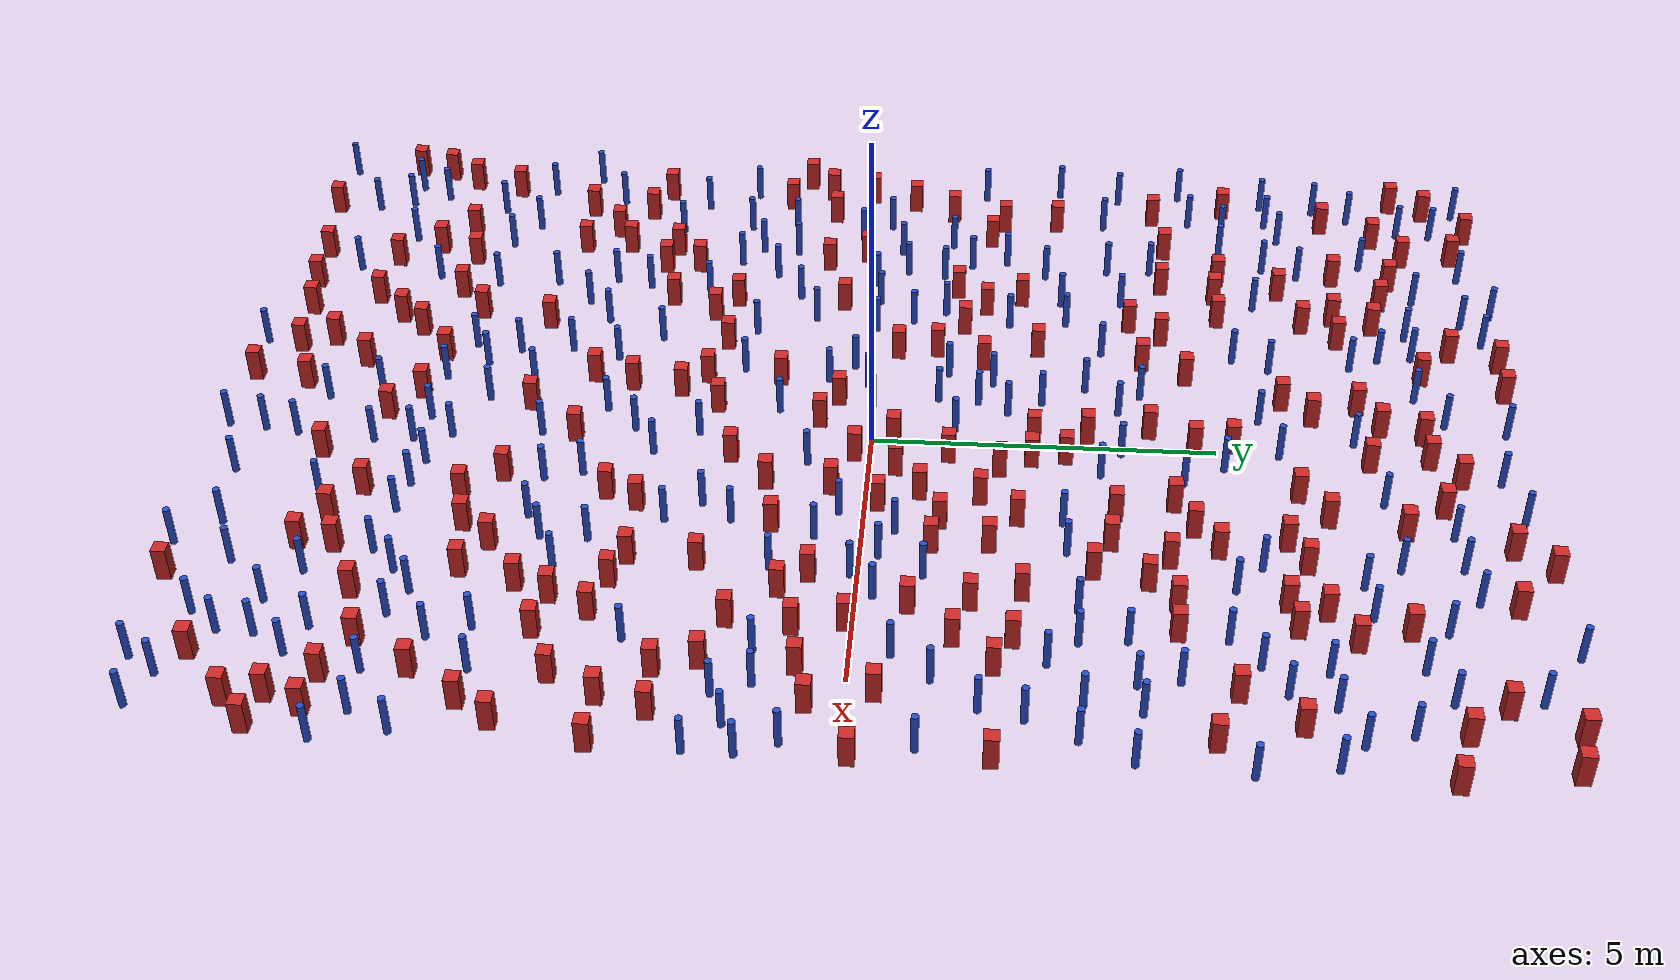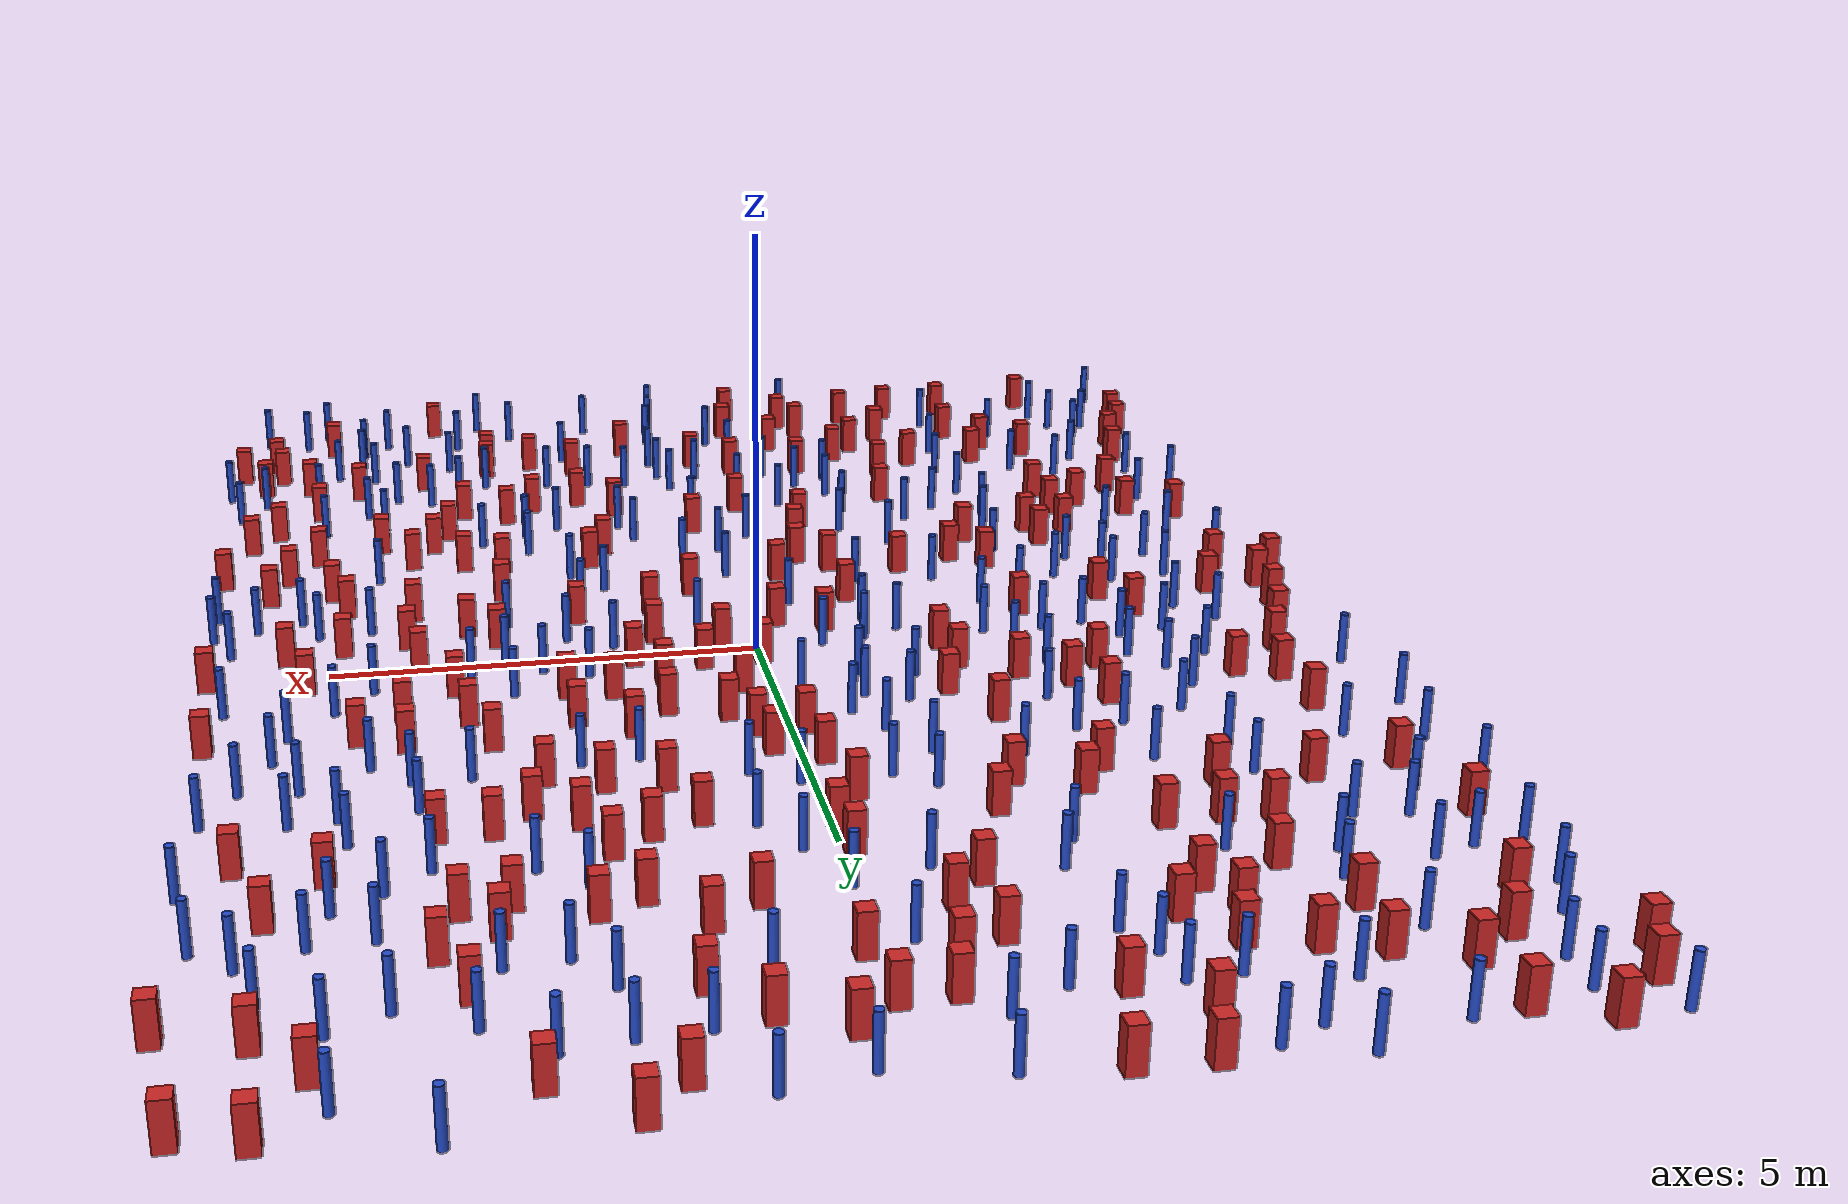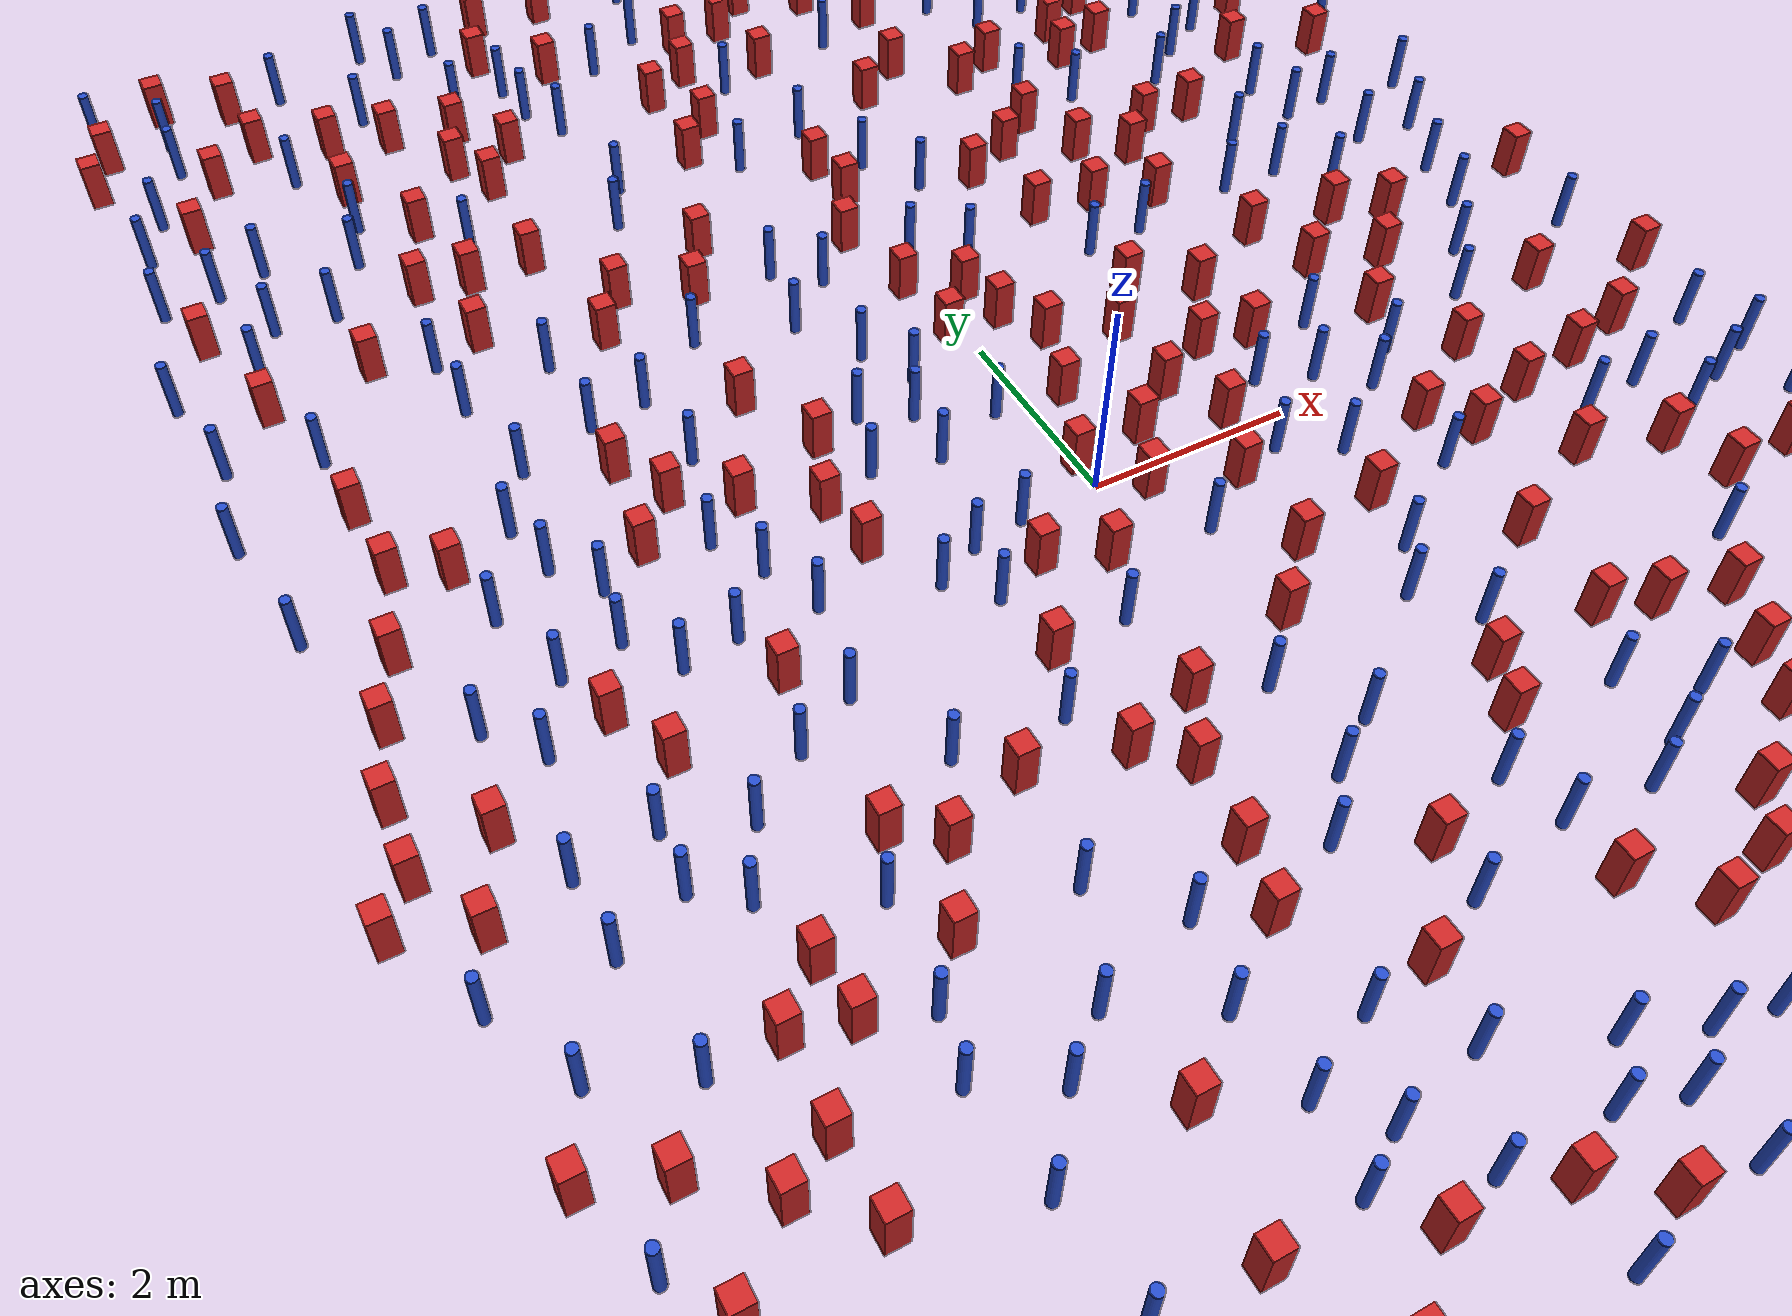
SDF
<sdf version="1.6">
  <model name="dense_50"><model name="square_post_obstacle0">
  <static>true</static>
  <pose frame="">1.99020298457 8.9363868212 1.91545236811e-07 -7.35059704564e-06 1.12565212e-07 2.39332434364e-05</pose>
  <link name="link">
    <pose frame="">0 0 0.25 0 -0 0</pose>
    <inertial>
      <mass>100</mass>
      <inertia>
        <ixx>0.166667</ixx>
        <ixy>0</ixy>
        <ixz>0</ixz>
        <iyy>0.166667</iyy>
        <iyz>0</iyz>
        <izz>0.166667</izz>
      </inertia>
    </inertial>
    <collision name="collision">
      <geometry>
        <box>
          <size>.2 .2 .5</size>
        </box>
      </geometry>
      <max_contacts>10</max_contacts>
      <surface>
        <contact>
          <ode/>
        </contact>
        <bounce/>
        <friction>
          <torsional>
            <ode/>
          </torsional>
          <ode/>
        </friction>
      </surface>
    </collision>
    <visual name="visual">
      <geometry>
        <box>
          <size>.2 .2 .5</size>
        </box>
      </geometry>
      <material>
        <script>
          <name>Gazebo/Red</name>
          <uri>file://media/materials/scripts/gazebo.material</uri>
        </script>
      </material>
    </visual>
    <self_collide>0</self_collide>
    <kinematic>0</kinematic>
  </link>
</model>
<model name="square_post_obstacle1">
  <static>true</static>
  <pose frame="">5.8524350811 -7.88041498456 1.91545236811e-07 -7.35059704564e-06 1.12565212e-07 2.39332434364e-05</pose>
  <link name="link">
    <pose frame="">0 0 0.25 0 -0 0</pose>
    <inertial>
      <mass>100</mass>
      <inertia>
        <ixx>0.166667</ixx>
        <ixy>0</ixy>
        <ixz>0</ixz>
        <iyy>0.166667</iyy>
        <iyz>0</iyz>
        <izz>0.166667</izz>
      </inertia>
    </inertial>
    <collision name="collision">
      <geometry>
        <box>
          <size>.2 .2 .5</size>
        </box>
      </geometry>
      <max_contacts>10</max_contacts>
      <surface>
        <contact>
          <ode/>
        </contact>
        <bounce/>
        <friction>
          <torsional>
            <ode/>
          </torsional>
          <ode/>
        </friction>
      </surface>
    </collision>
    <visual name="visual">
      <geometry>
        <box>
          <size>.2 .2 .5</size>
        </box>
      </geometry>
      <material>
        <script>
          <name>Gazebo/Red</name>
          <uri>file://media/materials/scripts/gazebo.material</uri>
        </script>
      </material>
    </visual>
    <self_collide>0</self_collide>
    <kinematic>0</kinematic>
  </link>
</model>
<model name="pole_obstacle0">
  <static>true</static>
  <pose frame="">2.45319481599 -4.44269924084 7.38925637345e-09 -8.47170692798e-08 1.24976765033e-08 -1.74513093019e-07</pose>
  <link name="link">
  <pose frame="">0 0 0.3 0 -0 0</pose>
    <inertial>
      <mass>1</mass>
      <inertia>
        <ixx>0.145833</ixx>
        <ixy>0</ixy>
        <ixz>0</ixz>
        <iyy>0.145833</iyy>
        <iyz>0</iyz>
        <izz>0.125</izz>
      </inertia>
    </inertial>
    <collision name="collision">
      <geometry>
        <cylinder>
          <radius>0.05</radius>
          <length>.6</length>
        </cylinder>
      </geometry>
      <max_contacts>10</max_contacts>
      <surface>
        <contact>
          <ode/>
        </contact>
        <bounce/>
        <friction>
          <torsional>
            <ode/>
          </torsional>
          <ode/>
        </friction>
      </surface>
    </collision>
    <visual name="visual">
      <geometry>
        <cylinder>
          <radius>0.05</radius>
          <length>.6</length>
        </cylinder>
      </geometry>
      <material>
        <script>
          <name>Gazebo/Blue</name>
          <uri>file://media/materials/scripts/gazebo.material</uri>
        </script>
      </material>
    </visual>
    <self_collide>0</self_collide>
    <kinematic>0</kinematic>
  </link>
</model>
<model name="square_post_obstacle2">
  <static>true</static>
  <pose frame="">-4.08696699237 6.18020313436 1.91545236811e-07 -7.35059704564e-06 1.12565212e-07 2.39332434364e-05</pose>
  <link name="link">
    <pose frame="">0 0 0.25 0 -0 0</pose>
    <inertial>
      <mass>100</mass>
      <inertia>
        <ixx>0.166667</ixx>
        <ixy>0</ixy>
        <ixz>0</ixz>
        <iyy>0.166667</iyy>
        <iyz>0</iyz>
        <izz>0.166667</izz>
      </inertia>
    </inertial>
    <collision name="collision">
      <geometry>
        <box>
          <size>.2 .2 .5</size>
        </box>
      </geometry>
      <max_contacts>10</max_contacts>
      <surface>
        <contact>
          <ode/>
        </contact>
        <bounce/>
        <friction>
          <torsional>
            <ode/>
          </torsional>
          <ode/>
        </friction>
      </surface>
    </collision>
    <visual name="visual">
      <geometry>
        <box>
          <size>.2 .2 .5</size>
        </box>
      </geometry>
      <material>
        <script>
          <name>Gazebo/Red</name>
          <uri>file://media/materials/scripts/gazebo.material</uri>
        </script>
      </material>
    </visual>
    <self_collide>0</self_collide>
    <kinematic>0</kinematic>
  </link>
</model>
<model name="pole_obstacle1">
  <static>true</static>
  <pose frame="">5.110812077 -4.89288464973 7.38925637345e-09 -8.47170692796e-08 1.24976764786e-08 -1.74513093032e-07</pose>
  <link name="link">
  <pose frame="">0 0 0.3 0 -0 0</pose>
    <inertial>
      <mass>1</mass>
      <inertia>
        <ixx>0.145833</ixx>
        <ixy>0</ixy>
        <ixz>0</ixz>
        <iyy>0.145833</iyy>
        <iyz>0</iyz>
        <izz>0.125</izz>
      </inertia>
    </inertial>
    <collision name="collision">
      <geometry>
        <cylinder>
          <radius>0.05</radius>
          <length>.6</length>
        </cylinder>
      </geometry>
      <max_contacts>10</max_contacts>
      <surface>
        <contact>
          <ode/>
        </contact>
        <bounce/>
        <friction>
          <torsional>
            <ode/>
          </torsional>
          <ode/>
        </friction>
      </surface>
    </collision>
    <visual name="visual">
      <geometry>
        <cylinder>
          <radius>0.05</radius>
          <length>.6</length>
        </cylinder>
      </geometry>
      <material>
        <script>
          <name>Gazebo/Blue</name>
          <uri>file://media/materials/scripts/gazebo.material</uri>
        </script>
      </material>
    </visual>
    <self_collide>0</self_collide>
    <kinematic>0</kinematic>
  </link>
</model>
<model name="square_post_obstacle3">
  <static>true</static>
  <pose frame="">1.17555070955 -5.18279903522 1.91545236811e-07 -7.35059704564e-06 1.12565212e-07 2.39332434364e-05</pose>
  <link name="link">
    <pose frame="">0 0 0.25 0 -0 0</pose>
    <inertial>
      <mass>100</mass>
      <inertia>
        <ixx>0.166667</ixx>
        <ixy>0</ixy>
        <ixz>0</ixz>
        <iyy>0.166667</iyy>
        <iyz>0</iyz>
        <izz>0.166667</izz>
      </inertia>
    </inertial>
    <collision name="collision">
      <geometry>
        <box>
          <size>.2 .2 .5</size>
        </box>
      </geometry>
      <max_contacts>10</max_contacts>
      <surface>
        <contact>
          <ode/>
        </contact>
        <bounce/>
        <friction>
          <torsional>
            <ode/>
          </torsional>
          <ode/>
        </friction>
      </surface>
    </collision>
    <visual name="visual">
      <geometry>
        <box>
          <size>.2 .2 .5</size>
        </box>
      </geometry>
      <material>
        <script>
          <name>Gazebo/Red</name>
          <uri>file://media/materials/scripts/gazebo.material</uri>
        </script>
      </material>
    </visual>
    <self_collide>0</self_collide>
    <kinematic>0</kinematic>
  </link>
</model>
<model name="pole_obstacle2">
  <static>true</static>
  <pose frame="">-5.38142675522 -3.46980054637 7.38925637345e-09 -8.47170692798e-08 1.24976764937e-08 -1.74513093023e-07</pose>
  <link name="link">
  <pose frame="">0 0 0.3 0 -0 0</pose>
    <inertial>
      <mass>1</mass>
      <inertia>
        <ixx>0.145833</ixx>
        <ixy>0</ixy>
        <ixz>0</ixz>
        <iyy>0.145833</iyy>
        <iyz>0</iyz>
        <izz>0.125</izz>
      </inertia>
    </inertial>
    <collision name="collision">
      <geometry>
        <cylinder>
          <radius>0.05</radius>
          <length>.6</length>
        </cylinder>
      </geometry>
      <max_contacts>10</max_contacts>
      <surface>
        <contact>
          <ode/>
        </contact>
        <bounce/>
        <friction>
          <torsional>
            <ode/>
          </torsional>
          <ode/>
        </friction>
      </surface>
    </collision>
    <visual name="visual">
      <geometry>
        <cylinder>
          <radius>0.05</radius>
          <length>.6</length>
        </cylinder>
      </geometry>
      <material>
        <script>
          <name>Gazebo/Blue</name>
          <uri>file://media/materials/scripts/gazebo.material</uri>
        </script>
      </material>
    </visual>
    <self_collide>0</self_collide>
    <kinematic>0</kinematic>
  </link>
</model>
<model name="pole_obstacle3">
  <static>true</static>
  <pose frame="">-3.40958924151 8.97512977727 7.38925637345e-09 -8.47170692799e-08 1.24976765012e-08 -1.74513093021e-07</pose>
  <link name="link">
  <pose frame="">0 0 0.3 0 -0 0</pose>
    <inertial>
      <mass>1</mass>
      <inertia>
        <ixx>0.145833</ixx>
        <ixy>0</ixy>
        <ixz>0</ixz>
        <iyy>0.145833</iyy>
        <iyz>0</iyz>
        <izz>0.125</izz>
      </inertia>
    </inertial>
    <collision name="collision">
      <geometry>
        <cylinder>
          <radius>0.05</radius>
          <length>.6</length>
        </cylinder>
      </geometry>
      <max_contacts>10</max_contacts>
      <surface>
        <contact>
          <ode/>
        </contact>
        <bounce/>
        <friction>
          <torsional>
            <ode/>
          </torsional>
          <ode/>
        </friction>
      </surface>
    </collision>
    <visual name="visual">
      <geometry>
        <cylinder>
          <radius>0.05</radius>
          <length>.6</length>
        </cylinder>
      </geometry>
      <material>
        <script>
          <name>Gazebo/Blue</name>
          <uri>file://media/materials/scripts/gazebo.material</uri>
        </script>
      </material>
    </visual>
    <self_collide>0</self_collide>
    <kinematic>0</kinematic>
  </link>
</model>
<model name="square_post_obstacle4">
  <static>true</static>
  <pose frame="">-1.94257678499 8.1703270499 1.91545236811e-07 -7.35059704564e-06 1.12565212e-07 2.39332434364e-05</pose>
  <link name="link">
    <pose frame="">0 0 0.25 0 -0 0</pose>
    <inertial>
      <mass>100</mass>
      <inertia>
        <ixx>0.166667</ixx>
        <ixy>0</ixy>
        <ixz>0</ixz>
        <iyy>0.166667</iyy>
        <iyz>0</iyz>
        <izz>0.166667</izz>
      </inertia>
    </inertial>
    <collision name="collision">
      <geometry>
        <box>
          <size>.2 .2 .5</size>
        </box>
      </geometry>
      <max_contacts>10</max_contacts>
      <surface>
        <contact>
          <ode/>
        </contact>
        <bounce/>
        <friction>
          <torsional>
            <ode/>
          </torsional>
          <ode/>
        </friction>
      </surface>
    </collision>
    <visual name="visual">
      <geometry>
        <box>
          <size>.2 .2 .5</size>
        </box>
      </geometry>
      <material>
        <script>
          <name>Gazebo/Red</name>
          <uri>file://media/materials/scripts/gazebo.material</uri>
        </script>
      </material>
    </visual>
    <self_collide>0</self_collide>
    <kinematic>0</kinematic>
  </link>
</model>
<model name="square_post_obstacle5">
  <static>true</static>
  <pose frame="">6.30125212651 -7.48989222779 1.91545236811e-07 -7.35059704564e-06 1.12565212e-07 2.39332434364e-05</pose>
  <link name="link">
    <pose frame="">0 0 0.25 0 -0 0</pose>
    <inertial>
      <mass>100</mass>
      <inertia>
        <ixx>0.166667</ixx>
        <ixy>0</ixy>
        <ixz>0</ixz>
        <iyy>0.166667</iyy>
        <iyz>0</iyz>
        <izz>0.166667</izz>
      </inertia>
    </inertial>
    <collision name="collision">
      <geometry>
        <box>
          <size>.2 .2 .5</size>
        </box>
      </geometry>
      <max_contacts>10</max_contacts>
      <surface>
        <contact>
          <ode/>
        </contact>
        <bounce/>
        <friction>
          <torsional>
            <ode/>
          </torsional>
          <ode/>
        </friction>
      </surface>
    </collision>
    <visual name="visual">
      <geometry>
        <box>
          <size>.2 .2 .5</size>
        </box>
      </geometry>
      <material>
        <script>
          <name>Gazebo/Red</name>
          <uri>file://media/materials/scripts/gazebo.material</uri>
        </script>
      </material>
    </visual>
    <self_collide>0</self_collide>
    <kinematic>0</kinematic>
  </link>
</model>
<model name="square_post_obstacle6">
  <static>true</static>
  <pose frame="">4.00243463076 -1.67645214226 1.91545236811e-07 -7.35059704564e-06 1.12565212e-07 2.39332434364e-05</pose>
  <link name="link">
    <pose frame="">0 0 0.25 0 -0 0</pose>
    <inertial>
      <mass>100</mass>
      <inertia>
        <ixx>0.166667</ixx>
        <ixy>0</ixy>
        <ixz>0</ixz>
        <iyy>0.166667</iyy>
        <iyz>0</iyz>
        <izz>0.166667</izz>
      </inertia>
    </inertial>
    <collision name="collision">
      <geometry>
        <box>
          <size>.2 .2 .5</size>
        </box>
      </geometry>
      <max_contacts>10</max_contacts>
      <surface>
        <contact>
          <ode/>
        </contact>
        <bounce/>
        <friction>
          <torsional>
            <ode/>
          </torsional>
          <ode/>
        </friction>
      </surface>
    </collision>
    <visual name="visual">
      <geometry>
        <box>
          <size>.2 .2 .5</size>
        </box>
      </geometry>
      <material>
        <script>
          <name>Gazebo/Red</name>
          <uri>file://media/materials/scripts/gazebo.material</uri>
        </script>
      </material>
    </visual>
    <self_collide>0</self_collide>
    <kinematic>0</kinematic>
  </link>
</model>
<model name="pole_obstacle4">
  <static>true</static>
  <pose frame="">-0.75053529397 1.97190595984 7.38925637345e-09 -8.47170692799e-08 1.24976765066e-08 -1.74513093016e-07</pose>
  <link name="link">
  <pose frame="">0 0 0.3 0 -0 0</pose>
    <inertial>
      <mass>1</mass>
      <inertia>
        <ixx>0.145833</ixx>
        <ixy>0</ixy>
        <ixz>0</ixz>
        <iyy>0.145833</iyy>
        <iyz>0</iyz>
        <izz>0.125</izz>
      </inertia>
    </inertial>
    <collision name="collision">
      <geometry>
        <cylinder>
          <radius>0.05</radius>
          <length>.6</length>
        </cylinder>
      </geometry>
      <max_contacts>10</max_contacts>
      <surface>
        <contact>
          <ode/>
        </contact>
        <bounce/>
        <friction>
          <torsional>
            <ode/>
          </torsional>
          <ode/>
        </friction>
      </surface>
    </collision>
    <visual name="visual">
      <geometry>
        <cylinder>
          <radius>0.05</radius>
          <length>.6</length>
        </cylinder>
      </geometry>
      <material>
        <script>
          <name>Gazebo/Blue</name>
          <uri>file://media/materials/scripts/gazebo.material</uri>
        </script>
      </material>
    </visual>
    <self_collide>0</self_collide>
    <kinematic>0</kinematic>
  </link>
</model>
<model name="pole_obstacle5">
  <static>true</static>
  <pose frame="">4.54238996978 2.56478637814 7.38925637345e-09 -8.47170692798e-08 1.24976764937e-08 -1.74513093023e-07</pose>
  <link name="link">
  <pose frame="">0 0 0.3 0 -0 0</pose>
    <inertial>
      <mass>1</mass>
      <inertia>
        <ixx>0.145833</ixx>
        <ixy>0</ixy>
        <ixz>0</ixz>
        <iyy>0.145833</iyy>
        <iyz>0</iyz>
        <izz>0.125</izz>
      </inertia>
    </inertial>
    <collision name="collision">
      <geometry>
        <cylinder>
          <radius>0.05</radius>
          <length>.6</length>
        </cylinder>
      </geometry>
      <max_contacts>10</max_contacts>
      <surface>
        <contact>
          <ode/>
        </contact>
        <bounce/>
        <friction>
          <torsional>
            <ode/>
          </torsional>
          <ode/>
        </friction>
      </surface>
    </collision>
    <visual name="visual">
      <geometry>
        <cylinder>
          <radius>0.05</radius>
          <length>.6</length>
        </cylinder>
      </geometry>
      <material>
        <script>
          <name>Gazebo/Blue</name>
          <uri>file://media/materials/scripts/gazebo.material</uri>
        </script>
      </material>
    </visual>
    <self_collide>0</self_collide>
    <kinematic>0</kinematic>
  </link>
</model>
<model name="square_post_obstacle7">
  <static>true</static>
  <pose frame="">2.81523320813 -7.72987050047 1.91545236811e-07 -7.35059704564e-06 1.12565212e-07 2.39332434364e-05</pose>
  <link name="link">
    <pose frame="">0 0 0.25 0 -0 0</pose>
    <inertial>
      <mass>100</mass>
      <inertia>
        <ixx>0.166667</ixx>
        <ixy>0</ixy>
        <ixz>0</ixz>
        <iyy>0.166667</iyy>
        <iyz>0</iyz>
        <izz>0.166667</izz>
      </inertia>
    </inertial>
    <collision name="collision">
      <geometry>
        <box>
          <size>.2 .2 .5</size>
        </box>
      </geometry>
      <max_contacts>10</max_contacts>
      <surface>
        <contact>
          <ode/>
        </contact>
        <bounce/>
        <friction>
          <torsional>
            <ode/>
          </torsional>
          <ode/>
        </friction>
      </surface>
    </collision>
    <visual name="visual">
      <geometry>
        <box>
          <size>.2 .2 .5</size>
        </box>
      </geometry>
      <material>
        <script>
          <name>Gazebo/Red</name>
          <uri>file://media/materials/scripts/gazebo.material</uri>
        </script>
      </material>
    </visual>
    <self_collide>0</self_collide>
    <kinematic>0</kinematic>
  </link>
</model>
<model name="square_post_obstacle8">
  <static>true</static>
  <pose frame="">-0.0129463398346 0.317881958594 1.91545236811e-07 -7.35059704564e-06 1.12565212e-07 2.39332434364e-05</pose>
  <link name="link">
    <pose frame="">0 0 0.25 0 -0 0</pose>
    <inertial>
      <mass>100</mass>
      <inertia>
        <ixx>0.166667</ixx>
        <ixy>0</ixy>
        <ixz>0</ixz>
        <iyy>0.166667</iyy>
        <iyz>0</iyz>
        <izz>0.166667</izz>
      </inertia>
    </inertial>
    <collision name="collision">
      <geometry>
        <box>
          <size>.2 .2 .5</size>
        </box>
      </geometry>
      <max_contacts>10</max_contacts>
      <surface>
        <contact>
          <ode/>
        </contact>
        <bounce/>
        <friction>
          <torsional>
            <ode/>
          </torsional>
          <ode/>
        </friction>
      </surface>
    </collision>
    <visual name="visual">
      <geometry>
        <box>
          <size>.2 .2 .5</size>
        </box>
      </geometry>
      <material>
        <script>
          <name>Gazebo/Red</name>
          <uri>file://media/materials/scripts/gazebo.material</uri>
        </script>
      </material>
    </visual>
    <self_collide>0</self_collide>
    <kinematic>0</kinematic>
  </link>
</model>
<model name="pole_obstacle6">
  <static>true</static>
  <pose frame="">6.16980746209 6.17317058995 7.38925637345e-09 -8.47170692796e-08 1.24976764786e-08 -1.74513093032e-07</pose>
  <link name="link">
  <pose frame="">0 0 0.3 0 -0 0</pose>
    <inertial>
      <mass>1</mass>
      <inertia>
        <ixx>0.145833</ixx>
        <ixy>0</ixy>
        <ixz>0</ixz>
        <iyy>0.145833</iyy>
        <iyz>0</iyz>
        <izz>0.125</izz>
      </inertia>
    </inertial>
    <collision name="collision">
      <geometry>
        <cylinder>
          <radius>0.05</radius>
          <length>.6</length>
        </cylinder>
      </geometry>
      <max_contacts>10</max_contacts>
      <surface>
        <contact>
          <ode/>
        </contact>
        <bounce/>
        <friction>
          <torsional>
            <ode/>
          </torsional>
          <ode/>
        </friction>
      </surface>
    </collision>
    <visual name="visual">
      <geometry>
        <cylinder>
          <radius>0.05</radius>
          <length>.6</length>
        </cylinder>
      </geometry>
      <material>
        <script>
          <name>Gazebo/Blue</name>
          <uri>file://media/materials/scripts/gazebo.material</uri>
        </script>
      </material>
    </visual>
    <self_collide>0</self_collide>
    <kinematic>0</kinematic>
  </link>
</model>
<model name="pole_obstacle7">
  <static>true</static>
  <pose frame="">6.15677421784 -0.760147875584 7.38925637345e-09 -8.47170692799e-08 1.24976765038e-08 -1.74513093018e-07</pose>
  <link name="link">
  <pose frame="">0 0 0.3 0 -0 0</pose>
    <inertial>
      <mass>1</mass>
      <inertia>
        <ixx>0.145833</ixx>
        <ixy>0</ixy>
        <ixz>0</ixz>
        <iyy>0.145833</iyy>
        <iyz>0</iyz>
        <izz>0.125</izz>
      </inertia>
    </inertial>
    <collision name="collision">
      <geometry>
        <cylinder>
          <radius>0.05</radius>
          <length>.6</length>
        </cylinder>
      </geometry>
      <max_contacts>10</max_contacts>
      <surface>
        <contact>
          <ode/>
        </contact>
        <bounce/>
        <friction>
          <torsional>
            <ode/>
          </torsional>
          <ode/>
        </friction>
      </surface>
    </collision>
    <visual name="visual">
      <geometry>
        <cylinder>
          <radius>0.05</radius>
          <length>.6</length>
        </cylinder>
      </geometry>
      <material>
        <script>
          <name>Gazebo/Blue</name>
          <uri>file://media/materials/scripts/gazebo.material</uri>
        </script>
      </material>
    </visual>
    <self_collide>0</self_collide>
    <kinematic>0</kinematic>
  </link>
</model>
<model name="square_post_obstacle9">
  <static>true</static>
  <pose frame="">-2.74050162465 4.29068194543 1.91545236811e-07 -7.35059704564e-06 1.12565212e-07 2.39332434364e-05</pose>
  <link name="link">
    <pose frame="">0 0 0.25 0 -0 0</pose>
    <inertial>
      <mass>100</mass>
      <inertia>
        <ixx>0.166667</ixx>
        <ixy>0</ixy>
        <ixz>0</ixz>
        <iyy>0.166667</iyy>
        <iyz>0</iyz>
        <izz>0.166667</izz>
      </inertia>
    </inertial>
    <collision name="collision">
      <geometry>
        <box>
          <size>.2 .2 .5</size>
        </box>
      </geometry>
      <max_contacts>10</max_contacts>
      <surface>
        <contact>
          <ode/>
        </contact>
        <bounce/>
        <friction>
          <torsional>
            <ode/>
          </torsional>
          <ode/>
        </friction>
      </surface>
    </collision>
    <visual name="visual">
      <geometry>
        <box>
          <size>.2 .2 .5</size>
        </box>
      </geometry>
      <material>
        <script>
          <name>Gazebo/Red</name>
          <uri>file://media/materials/scripts/gazebo.material</uri>
        </script>
      </material>
    </visual>
    <self_collide>0</self_collide>
    <kinematic>0</kinematic>
  </link>
</model>
<model name="square_post_obstacle10">
  <static>true</static>
  <pose frame="">-5.13952486066 -6.89971847633 1.91545236811e-07 -7.35059704564e-06 1.12565212e-07 2.39332434364e-05</pose>
  <link name="link">
    <pose frame="">0 0 0.25 0 -0 0</pose>
    <inertial>
      <mass>100</mass>
      <inertia>
        <ixx>0.166667</ixx>
        <ixy>0</ixy>
        <ixz>0</ixz>
        <iyy>0.166667</iyy>
        <iyz>0</iyz>
        <izz>0.166667</izz>
      </inertia>
    </inertial>
    <collision name="collision">
      <geometry>
        <box>
          <size>.2 .2 .5</size>
        </box>
      </geometry>
      <max_contacts>10</max_contacts>
      <surface>
        <contact>
          <ode/>
        </contact>
        <bounce/>
        <friction>
          <torsional>
            <ode/>
          </torsional>
          <ode/>
        </friction>
      </surface>
    </collision>
    <visual name="visual">
      <geometry>
        <box>
          <size>.2 .2 .5</size>
        </box>
      </geometry>
      <material>
        <script>
          <name>Gazebo/Red</name>
          <uri>file://media/materials/scripts/gazebo.material</uri>
        </script>
      </material>
    </visual>
    <self_collide>0</self_collide>
    <kinematic>0</kinematic>
  </link>
</model>
<model name="square_post_obstacle11">
  <static>true</static>
  <pose frame="">-6.36342929081 0.339561308146 1.91545236811e-07 -7.35059704564e-06 1.12565212e-07 2.39332434364e-05</pose>
  <link name="link">
    <pose frame="">0 0 0.25 0 -0 0</pose>
    <inertial>
      <mass>100</mass>
      <inertia>
        <ixx>0.166667</ixx>
        <ixy>0</ixy>
        <ixz>0</ixz>
        <iyy>0.166667</iyy>
        <iyz>0</iyz>
        <izz>0.166667</izz>
      </inertia>
    </inertial>
    <collision name="collision">
      <geometry>
        <box>
          <size>.2 .2 .5</size>
        </box>
      </geometry>
      <max_contacts>10</max_contacts>
      <surface>
        <contact>
          <ode/>
        </contact>
        <bounce/>
        <friction>
          <torsional>
            <ode/>
          </torsional>
          <ode/>
        </friction>
      </surface>
    </collision>
    <visual name="visual">
      <geometry>
        <box>
          <size>.2 .2 .5</size>
        </box>
      </geometry>
      <material>
        <script>
          <name>Gazebo/Red</name>
          <uri>file://media/materials/scripts/gazebo.material</uri>
        </script>
      </material>
    </visual>
    <self_collide>0</self_collide>
    <kinematic>0</kinematic>
  </link>
</model>
<model name="square_post_obstacle12">
  <static>true</static>
  <pose frame="">3.03835223823 -0.663720716733 1.91545236811e-07 -7.35059704564e-06 1.12565212e-07 2.39332434364e-05</pose>
  <link name="link">
    <pose frame="">0 0 0.25 0 -0 0</pose>
    <inertial>
      <mass>100</mass>
      <inertia>
        <ixx>0.166667</ixx>
        <ixy>0</ixy>
        <ixz>0</ixz>
        <iyy>0.166667</iyy>
        <iyz>0</iyz>
        <izz>0.166667</izz>
      </inertia>
    </inertial>
    <collision name="collision">
      <geometry>
        <box>
          <size>.2 .2 .5</size>
        </box>
      </geometry>
      <max_contacts>10</max_contacts>
      <surface>
        <contact>
          <ode/>
        </contact>
        <bounce/>
        <friction>
          <torsional>
            <ode/>
          </torsional>
          <ode/>
        </friction>
      </surface>
    </collision>
    <visual name="visual">
      <geometry>
        <box>
          <size>.2 .2 .5</size>
        </box>
      </geometry>
      <material>
        <script>
          <name>Gazebo/Red</name>
          <uri>file://media/materials/scripts/gazebo.material</uri>
        </script>
      </material>
    </visual>
    <self_collide>0</self_collide>
    <kinematic>0</kinematic>
  </link>
</model>
<model name="square_post_obstacle13">
  <static>true</static>
  <pose frame="">0.947055316499 6.09849386532 1.91545236811e-07 -7.35059704564e-06 1.12565212e-07 2.39332434364e-05</pose>
  <link name="link">
    <pose frame="">0 0 0.25 0 -0 0</pose>
    <inertial>
      <mass>100</mass>
      <inertia>
        <ixx>0.166667</ixx>
        <ixy>0</ixy>
        <ixz>0</ixz>
        <iyy>0.166667</iyy>
        <iyz>0</iyz>
        <izz>0.166667</izz>
      </inertia>
    </inertial>
    <collision name="collision">
      <geometry>
        <box>
          <size>.2 .2 .5</size>
        </box>
      </geometry>
      <max_contacts>10</max_contacts>
      <surface>
        <contact>
          <ode/>
        </contact>
        <bounce/>
        <friction>
          <torsional>
            <ode/>
          </torsional>
          <ode/>
        </friction>
      </surface>
    </collision>
    <visual name="visual">
      <geometry>
        <box>
          <size>.2 .2 .5</size>
        </box>
      </geometry>
      <material>
        <script>
          <name>Gazebo/Red</name>
          <uri>file://media/materials/scripts/gazebo.material</uri>
        </script>
      </material>
    </visual>
    <self_collide>0</self_collide>
    <kinematic>0</kinematic>
  </link>
</model>
<model name="pole_obstacle8">
  <static>true</static>
  <pose frame="">-1.87639103738 -5.52417425113 7.38925637345e-09 -8.47170692799e-08 1.24976765033e-08 -1.74513093018e-07</pose>
  <link name="link">
  <pose frame="">0 0 0.3 0 -0 0</pose>
    <inertial>
      <mass>1</mass>
      <inertia>
        <ixx>0.145833</ixx>
        <ixy>0</ixy>
        <ixz>0</ixz>
        <iyy>0.145833</iyy>
        <iyz>0</iyz>
        <izz>0.125</izz>
      </inertia>
    </inertial>
    <collision name="collision">
      <geometry>
        <cylinder>
          <radius>0.05</radius>
          <length>.6</length>
        </cylinder>
      </geometry>
      <max_contacts>10</max_contacts>
      <surface>
        <contact>
          <ode/>
        </contact>
        <bounce/>
        <friction>
          <torsional>
            <ode/>
          </torsional>
          <ode/>
        </friction>
      </surface>
    </collision>
    <visual name="visual">
      <geometry>
        <cylinder>
          <radius>0.05</radius>
          <length>.6</length>
        </cylinder>
      </geometry>
      <material>
        <script>
          <name>Gazebo/Blue</name>
          <uri>file://media/materials/scripts/gazebo.material</uri>
        </script>
      </material>
    </visual>
    <self_collide>0</self_collide>
    <kinematic>0</kinematic>
  </link>
</model>
<model name="square_post_obstacle14">
  <static>true</static>
  <pose frame="">-0.112037463065 5.22888776063 1.91545236811e-07 -7.35059704564e-06 1.12565212e-07 2.39332434364e-05</pose>
  <link name="link">
    <pose frame="">0 0 0.25 0 -0 0</pose>
    <inertial>
      <mass>100</mass>
      <inertia>
        <ixx>0.166667</ixx>
        <ixy>0</ixy>
        <ixz>0</ixz>
        <iyy>0.166667</iyy>
        <iyz>0</iyz>
        <izz>0.166667</izz>
      </inertia>
    </inertial>
    <collision name="collision">
      <geometry>
        <box>
          <size>.2 .2 .5</size>
        </box>
      </geometry>
      <max_contacts>10</max_contacts>
      <surface>
        <contact>
          <ode/>
        </contact>
        <bounce/>
        <friction>
          <torsional>
            <ode/>
          </torsional>
          <ode/>
        </friction>
      </surface>
    </collision>
    <visual name="visual">
      <geometry>
        <box>
          <size>.2 .2 .5</size>
        </box>
      </geometry>
      <material>
        <script>
          <name>Gazebo/Red</name>
          <uri>file://media/materials/scripts/gazebo.material</uri>
        </script>
      </material>
    </visual>
    <self_collide>0</self_collide>
    <kinematic>0</kinematic>
  </link>
</model>
<model name="square_post_obstacle15">
  <static>true</static>
  <pose frame="">-6.63554746986 -1.0725611367 1.91545236811e-07 -7.35059704564e-06 1.12565212e-07 2.39332434364e-05</pose>
  <link name="link">
    <pose frame="">0 0 0.25 0 -0 0</pose>
    <inertial>
      <mass>100</mass>
      <inertia>
        <ixx>0.166667</ixx>
        <ixy>0</ixy>
        <ixz>0</ixz>
        <iyy>0.166667</iyy>
        <iyz>0</iyz>
        <izz>0.166667</izz>
      </inertia>
    </inertial>
    <collision name="collision">
      <geometry>
        <box>
          <size>.2 .2 .5</size>
        </box>
      </geometry>
      <max_contacts>10</max_contacts>
      <surface>
        <contact>
          <ode/>
        </contact>
        <bounce/>
        <friction>
          <torsional>
            <ode/>
          </torsional>
          <ode/>
        </friction>
      </surface>
    </collision>
    <visual name="visual">
      <geometry>
        <box>
          <size>.2 .2 .5</size>
        </box>
      </geometry>
      <material>
        <script>
          <name>Gazebo/Red</name>
          <uri>file://media/materials/scripts/gazebo.material</uri>
        </script>
      </material>
    </visual>
    <self_collide>0</self_collide>
    <kinematic>0</kinematic>
  </link>
</model>
<model name="square_post_obstacle16">
  <static>true</static>
  <pose frame="">-0.980387862571 -2.91094023249 1.91545236811e-07 -7.35059704564e-06 1.12565212e-07 2.39332434364e-05</pose>
  <link name="link">
    <pose frame="">0 0 0.25 0 -0 0</pose>
    <inertial>
      <mass>100</mass>
      <inertia>
        <ixx>0.166667</ixx>
        <ixy>0</ixy>
        <ixz>0</ixz>
        <iyy>0.166667</iyy>
        <iyz>0</iyz>
        <izz>0.166667</izz>
      </inertia>
    </inertial>
    <collision name="collision">
      <geometry>
        <box>
          <size>.2 .2 .5</size>
        </box>
      </geometry>
      <max_contacts>10</max_contacts>
      <surface>
        <contact>
          <ode/>
        </contact>
        <bounce/>
        <friction>
          <torsional>
            <ode/>
          </torsional>
          <ode/>
        </friction>
      </surface>
    </collision>
    <visual name="visual">
      <geometry>
        <box>
          <size>.2 .2 .5</size>
        </box>
      </geometry>
      <material>
        <script>
          <name>Gazebo/Red</name>
          <uri>file://media/materials/scripts/gazebo.material</uri>
        </script>
      </material>
    </visual>
    <self_collide>0</self_collide>
    <kinematic>0</kinematic>
  </link>
</model>
<model name="pole_obstacle9">
  <static>true</static>
  <pose frame="">4.86439608183 3.7236601719 7.38925637345e-09 -8.47170692798e-08 1.24976764937e-08 -1.74513093023e-07</pose>
  <link name="link">
  <pose frame="">0 0 0.3 0 -0 0</pose>
    <inertial>
      <mass>1</mass>
      <inertia>
        <ixx>0.145833</ixx>
        <ixy>0</ixy>
        <ixz>0</ixz>
        <iyy>0.145833</iyy>
        <iyz>0</iyz>
        <izz>0.125</izz>
      </inertia>
    </inertial>
    <collision name="collision">
      <geometry>
        <cylinder>
          <radius>0.05</radius>
          <length>.6</length>
        </cylinder>
      </geometry>
      <max_contacts>10</max_contacts>
      <surface>
        <contact>
          <ode/>
        </contact>
        <bounce/>
        <friction>
          <torsional>
            <ode/>
          </torsional>
          <ode/>
        </friction>
      </surface>
    </collision>
    <visual name="visual">
      <geometry>
        <cylinder>
          <radius>0.05</radius>
          <length>.6</length>
        </cylinder>
      </geometry>
      <material>
        <script>
          <name>Gazebo/Blue</name>
          <uri>file://media/materials/scripts/gazebo.material</uri>
        </script>
      </material>
    </visual>
    <self_collide>0</self_collide>
    <kinematic>0</kinematic>
  </link>
</model>
<model name="square_post_obstacle17">
  <static>true</static>
  <pose frame="">5.25384583525 0.369909139949 1.91545236811e-07 -7.35059704564e-06 1.12565212e-07 2.39332434364e-05</pose>
  <link name="link">
    <pose frame="">0 0 0.25 0 -0 0</pose>
    <inertial>
      <mass>100</mass>
      <inertia>
        <ixx>0.166667</ixx>
        <ixy>0</ixy>
        <ixz>0</ixz>
        <iyy>0.166667</iyy>
        <iyz>0</iyz>
        <izz>0.166667</izz>
      </inertia>
    </inertial>
    <collision name="collision">
      <geometry>
        <box>
          <size>.2 .2 .5</size>
        </box>
      </geometry>
      <max_contacts>10</max_contacts>
      <surface>
        <contact>
          <ode/>
        </contact>
        <bounce/>
        <friction>
          <torsional>
            <ode/>
          </torsional>
          <ode/>
        </friction>
      </surface>
    </collision>
    <visual name="visual">
      <geometry>
        <box>
          <size>.2 .2 .5</size>
        </box>
      </geometry>
      <material>
        <script>
          <name>Gazebo/Red</name>
          <uri>file://media/materials/scripts/gazebo.material</uri>
        </script>
      </material>
    </visual>
    <self_collide>0</self_collide>
    <kinematic>0</kinematic>
  </link>
</model>
<model name="square_post_obstacle18">
  <static>true</static>
  <pose frame="">1.16525033121 8.103247018 1.91545236811e-07 -7.35059704564e-06 1.12565212e-07 2.39332434364e-05</pose>
  <link name="link">
    <pose frame="">0 0 0.25 0 -0 0</pose>
    <inertial>
      <mass>100</mass>
      <inertia>
        <ixx>0.166667</ixx>
        <ixy>0</ixy>
        <ixz>0</ixz>
        <iyy>0.166667</iyy>
        <iyz>0</iyz>
        <izz>0.166667</izz>
      </inertia>
    </inertial>
    <collision name="collision">
      <geometry>
        <box>
          <size>.2 .2 .5</size>
        </box>
      </geometry>
      <max_contacts>10</max_contacts>
      <surface>
        <contact>
          <ode/>
        </contact>
        <bounce/>
        <friction>
          <torsional>
            <ode/>
          </torsional>
          <ode/>
        </friction>
      </surface>
    </collision>
    <visual name="visual">
      <geometry>
        <box>
          <size>.2 .2 .5</size>
        </box>
      </geometry>
      <material>
        <script>
          <name>Gazebo/Red</name>
          <uri>file://media/materials/scripts/gazebo.material</uri>
        </script>
      </material>
    </visual>
    <self_collide>0</self_collide>
    <kinematic>0</kinematic>
  </link>
</model>
<model name="pole_obstacle10">
  <static>true</static>
  <pose frame="">4.88381314462 8.86168116422 7.38925637345e-09 -8.471706928e-08 1.24976765081e-08 -1.74513093015e-07</pose>
  <link name="link">
  <pose frame="">0 0 0.3 0 -0 0</pose>
    <inertial>
      <mass>1</mass>
      <inertia>
        <ixx>0.145833</ixx>
        <ixy>0</ixy>
        <ixz>0</ixz>
        <iyy>0.145833</iyy>
        <iyz>0</iyz>
        <izz>0.125</izz>
      </inertia>
    </inertial>
    <collision name="collision">
      <geometry>
        <cylinder>
          <radius>0.05</radius>
          <length>.6</length>
        </cylinder>
      </geometry>
      <max_contacts>10</max_contacts>
      <surface>
        <contact>
          <ode/>
        </contact>
        <bounce/>
        <friction>
          <torsional>
            <ode/>
          </torsional>
          <ode/>
        </friction>
      </surface>
    </collision>
    <visual name="visual">
      <geometry>
        <cylinder>
          <radius>0.05</radius>
          <length>.6</length>
        </cylinder>
      </geometry>
      <material>
        <script>
          <name>Gazebo/Blue</name>
          <uri>file://media/materials/scripts/gazebo.material</uri>
        </script>
      </material>
    </visual>
    <self_collide>0</self_collide>
    <kinematic>0</kinematic>
  </link>
</model>
<model name="square_post_obstacle19">
  <static>true</static>
  <pose frame="">-4.28214756523 -3.59136067005 1.91545236811e-07 -7.35059704564e-06 1.12565212e-07 2.39332434364e-05</pose>
  <link name="link">
    <pose frame="">0 0 0.25 0 -0 0</pose>
    <inertial>
      <mass>100</mass>
      <inertia>
        <ixx>0.166667</ixx>
        <ixy>0</ixy>
        <ixz>0</ixz>
        <iyy>0.166667</iyy>
        <iyz>0</iyz>
        <izz>0.166667</izz>
      </inertia>
    </inertial>
    <collision name="collision">
      <geometry>
        <box>
          <size>.2 .2 .5</size>
        </box>
      </geometry>
      <max_contacts>10</max_contacts>
      <surface>
        <contact>
          <ode/>
        </contact>
        <bounce/>
        <friction>
          <torsional>
            <ode/>
          </torsional>
          <ode/>
        </friction>
      </surface>
    </collision>
    <visual name="visual">
      <geometry>
        <box>
          <size>.2 .2 .5</size>
        </box>
      </geometry>
      <material>
        <script>
          <name>Gazebo/Red</name>
          <uri>file://media/materials/scripts/gazebo.material</uri>
        </script>
      </material>
    </visual>
    <self_collide>0</self_collide>
    <kinematic>0</kinematic>
  </link>
</model>
<model name="pole_obstacle11">
  <static>true</static>
  <pose frame="">2.42599380312 7.3634539889 7.38925637345e-09 -8.47170692798e-08 1.24976765033e-08 -1.74513093019e-07</pose>
  <link name="link">
  <pose frame="">0 0 0.3 0 -0 0</pose>
    <inertial>
      <mass>1</mass>
      <inertia>
        <ixx>0.145833</ixx>
        <ixy>0</ixy>
        <ixz>0</ixz>
        <iyy>0.145833</iyy>
        <iyz>0</iyz>
        <izz>0.125</izz>
      </inertia>
    </inertial>
    <collision name="collision">
      <geometry>
        <cylinder>
          <radius>0.05</radius>
          <length>.6</length>
        </cylinder>
      </geometry>
      <max_contacts>10</max_contacts>
      <surface>
        <contact>
          <ode/>
        </contact>
        <bounce/>
        <friction>
          <torsional>
            <ode/>
          </torsional>
          <ode/>
        </friction>
      </surface>
    </collision>
    <visual name="visual">
      <geometry>
        <cylinder>
          <radius>0.05</radius>
          <length>.6</length>
        </cylinder>
      </geometry>
      <material>
        <script>
          <name>Gazebo/Blue</name>
          <uri>file://media/materials/scripts/gazebo.material</uri>
        </script>
      </material>
    </visual>
    <self_collide>0</self_collide>
    <kinematic>0</kinematic>
  </link>
</model>
<model name="square_post_obstacle20">
  <static>true</static>
  <pose frame="">1.21002610688 0.756672883856 1.91545236811e-07 -7.35059704564e-06 1.12565212e-07 2.39332434364e-05</pose>
  <link name="link">
    <pose frame="">0 0 0.25 0 -0 0</pose>
    <inertial>
      <mass>100</mass>
      <inertia>
        <ixx>0.166667</ixx>
        <ixy>0</ixy>
        <ixz>0</ixz>
        <iyy>0.166667</iyy>
        <iyz>0</iyz>
        <izz>0.166667</izz>
      </inertia>
    </inertial>
    <collision name="collision">
      <geometry>
        <box>
          <size>.2 .2 .5</size>
        </box>
      </geometry>
      <max_contacts>10</max_contacts>
      <surface>
        <contact>
          <ode/>
        </contact>
        <bounce/>
        <friction>
          <torsional>
            <ode/>
          </torsional>
          <ode/>
        </friction>
      </surface>
    </collision>
    <visual name="visual">
      <geometry>
        <box>
          <size>.2 .2 .5</size>
        </box>
      </geometry>
      <material>
        <script>
          <name>Gazebo/Red</name>
          <uri>file://media/materials/scripts/gazebo.material</uri>
        </script>
      </material>
    </visual>
    <self_collide>0</self_collide>
    <kinematic>0</kinematic>
  </link>
</model>
<model name="pole_obstacle12">
  <static>true</static>
  <pose frame="">-4.62292605062 1.33828571062 7.38925637345e-09 -8.471706928e-08 1.24976765134e-08 -1.74513093015e-07</pose>
  <link name="link">
  <pose frame="">0 0 0.3 0 -0 0</pose>
    <inertial>
      <mass>1</mass>
      <inertia>
        <ixx>0.145833</ixx>
        <ixy>0</ixy>
        <ixz>0</ixz>
        <iyy>0.145833</iyy>
        <iyz>0</iyz>
        <izz>0.125</izz>
      </inertia>
    </inertial>
    <collision name="collision">
      <geometry>
        <cylinder>
          <radius>0.05</radius>
          <length>.6</length>
        </cylinder>
      </geometry>
      <max_contacts>10</max_contacts>
      <surface>
        <contact>
          <ode/>
        </contact>
        <bounce/>
        <friction>
          <torsional>
            <ode/>
          </torsional>
          <ode/>
        </friction>
      </surface>
    </collision>
    <visual name="visual">
      <geometry>
        <cylinder>
          <radius>0.05</radius>
          <length>.6</length>
        </cylinder>
      </geometry>
      <material>
        <script>
          <name>Gazebo/Blue</name>
          <uri>file://media/materials/scripts/gazebo.material</uri>
        </script>
      </material>
    </visual>
    <self_collide>0</self_collide>
    <kinematic>0</kinematic>
  </link>
</model>
<model name="square_post_obstacle21">
  <static>true</static>
  <pose frame="">-2.7512530869 -8.99102333689 1.91545236811e-07 -7.35059704564e-06 1.12565212e-07 2.39332434364e-05</pose>
  <link name="link">
    <pose frame="">0 0 0.25 0 -0 0</pose>
    <inertial>
      <mass>100</mass>
      <inertia>
        <ixx>0.166667</ixx>
        <ixy>0</ixy>
        <ixz>0</ixz>
        <iyy>0.166667</iyy>
        <iyz>0</iyz>
        <izz>0.166667</izz>
      </inertia>
    </inertial>
    <collision name="collision">
      <geometry>
        <box>
          <size>.2 .2 .5</size>
        </box>
      </geometry>
      <max_contacts>10</max_contacts>
      <surface>
        <contact>
          <ode/>
        </contact>
        <bounce/>
        <friction>
          <torsional>
            <ode/>
          </torsional>
          <ode/>
        </friction>
      </surface>
    </collision>
    <visual name="visual">
      <geometry>
        <box>
          <size>.2 .2 .5</size>
        </box>
      </geometry>
      <material>
        <script>
          <name>Gazebo/Red</name>
          <uri>file://media/materials/scripts/gazebo.material</uri>
        </script>
      </material>
    </visual>
    <self_collide>0</self_collide>
    <kinematic>0</kinematic>
  </link>
</model>
<model name="pole_obstacle13">
  <static>true</static>
  <pose frame="">-6.87187064369 -9.32866329716 7.38925637345e-09 -8.471706928e-08 1.24976765081e-08 -1.74513093015e-07</pose>
  <link name="link">
  <pose frame="">0 0 0.3 0 -0 0</pose>
    <inertial>
      <mass>1</mass>
      <inertia>
        <ixx>0.145833</ixx>
        <ixy>0</ixy>
        <ixz>0</ixz>
        <iyy>0.145833</iyy>
        <iyz>0</iyz>
        <izz>0.125</izz>
      </inertia>
    </inertial>
    <collision name="collision">
      <geometry>
        <cylinder>
          <radius>0.05</radius>
          <length>.6</length>
        </cylinder>
      </geometry>
      <max_contacts>10</max_contacts>
      <surface>
        <contact>
          <ode/>
        </contact>
        <bounce/>
        <friction>
          <torsional>
            <ode/>
          </torsional>
          <ode/>
        </friction>
      </surface>
    </collision>
    <visual name="visual">
      <geometry>
        <cylinder>
          <radius>0.05</radius>
          <length>.6</length>
        </cylinder>
      </geometry>
      <material>
        <script>
          <name>Gazebo/Blue</name>
          <uri>file://media/materials/scripts/gazebo.material</uri>
        </script>
      </material>
    </visual>
    <self_collide>0</self_collide>
    <kinematic>0</kinematic>
  </link>
</model>
<model name="square_post_obstacle22">
  <static>true</static>
  <pose frame="">-0.627810288311 -2.31708253477 1.91545236811e-07 -7.35059704564e-06 1.12565212e-07 2.39332434364e-05</pose>
  <link name="link">
    <pose frame="">0 0 0.25 0 -0 0</pose>
    <inertial>
      <mass>100</mass>
      <inertia>
        <ixx>0.166667</ixx>
        <ixy>0</ixy>
        <ixz>0</ixz>
        <iyy>0.166667</iyy>
        <iyz>0</iyz>
        <izz>0.166667</izz>
      </inertia>
    </inertial>
    <collision name="collision">
      <geometry>
        <box>
          <size>.2 .2 .5</size>
        </box>
      </geometry>
      <max_contacts>10</max_contacts>
      <surface>
        <contact>
          <ode/>
        </contact>
        <bounce/>
        <friction>
          <torsional>
            <ode/>
          </torsional>
          <ode/>
        </friction>
      </surface>
    </collision>
    <visual name="visual">
      <geometry>
        <box>
          <size>.2 .2 .5</size>
        </box>
      </geometry>
      <material>
        <script>
          <name>Gazebo/Red</name>
          <uri>file://media/materials/scripts/gazebo.material</uri>
        </script>
      </material>
    </visual>
    <self_collide>0</self_collide>
    <kinematic>0</kinematic>
  </link>
</model>
<model name="pole_obstacle14">
  <static>true</static>
  <pose frame="">0.145431486361 -4.83074506989 7.38925637345e-09 -8.471706928e-08 1.24976765036e-08 -1.74513093019e-07</pose>
  <link name="link">
  <pose frame="">0 0 0.3 0 -0 0</pose>
    <inertial>
      <mass>1</mass>
      <inertia>
        <ixx>0.145833</ixx>
        <ixy>0</ixy>
        <ixz>0</ixz>
        <iyy>0.145833</iyy>
        <iyz>0</iyz>
        <izz>0.125</izz>
      </inertia>
    </inertial>
    <collision name="collision">
      <geometry>
        <cylinder>
          <radius>0.05</radius>
          <length>.6</length>
        </cylinder>
      </geometry>
      <max_contacts>10</max_contacts>
      <surface>
        <contact>
          <ode/>
        </contact>
        <bounce/>
        <friction>
          <torsional>
            <ode/>
          </torsional>
          <ode/>
        </friction>
      </surface>
    </collision>
    <visual name="visual">
      <geometry>
        <cylinder>
          <radius>0.05</radius>
          <length>.6</length>
        </cylinder>
      </geometry>
      <material>
        <script>
          <name>Gazebo/Blue</name>
          <uri>file://media/materials/scripts/gazebo.material</uri>
        </script>
      </material>
    </visual>
    <self_collide>0</self_collide>
    <kinematic>0</kinematic>
  </link>
</model>
<model name="pole_obstacle15">
  <static>true</static>
  <pose frame="">-2.49472239428 8.10000024564 7.38925637345e-09 -8.47170692793e-08 1.24976764408e-08 -1.74513093041e-07</pose>
  <link name="link">
  <pose frame="">0 0 0.3 0 -0 0</pose>
    <inertial>
      <mass>1</mass>
      <inertia>
        <ixx>0.145833</ixx>
        <ixy>0</ixy>
        <ixz>0</ixz>
        <iyy>0.145833</iyy>
        <iyz>0</iyz>
        <izz>0.125</izz>
      </inertia>
    </inertial>
    <collision name="collision">
      <geometry>
        <cylinder>
          <radius>0.05</radius>
          <length>.6</length>
        </cylinder>
      </geometry>
      <max_contacts>10</max_contacts>
      <surface>
        <contact>
          <ode/>
        </contact>
        <bounce/>
        <friction>
          <torsional>
            <ode/>
          </torsional>
          <ode/>
        </friction>
      </surface>
    </collision>
    <visual name="visual">
      <geometry>
        <cylinder>
          <radius>0.05</radius>
          <length>.6</length>
        </cylinder>
      </geometry>
      <material>
        <script>
          <name>Gazebo/Blue</name>
          <uri>file://media/materials/scripts/gazebo.material</uri>
        </script>
      </material>
    </visual>
    <self_collide>0</self_collide>
    <kinematic>0</kinematic>
  </link>
</model>
<model name="pole_obstacle16">
  <static>true</static>
  <pose frame="">1.93347617222 -1.84121903709 7.38925637345e-09 -8.471706928e-08 1.24976765079e-08 -1.74513093017e-07</pose>
  <link name="link">
  <pose frame="">0 0 0.3 0 -0 0</pose>
    <inertial>
      <mass>1</mass>
      <inertia>
        <ixx>0.145833</ixx>
        <ixy>0</ixy>
        <ixz>0</ixz>
        <iyy>0.145833</iyy>
        <iyz>0</iyz>
        <izz>0.125</izz>
      </inertia>
    </inertial>
    <collision name="collision">
      <geometry>
        <cylinder>
          <radius>0.05</radius>
          <length>.6</length>
        </cylinder>
      </geometry>
      <max_contacts>10</max_contacts>
      <surface>
        <contact>
          <ode/>
        </contact>
        <bounce/>
        <friction>
          <torsional>
            <ode/>
          </torsional>
          <ode/>
        </friction>
      </surface>
    </collision>
    <visual name="visual">
      <geometry>
        <cylinder>
          <radius>0.05</radius>
          <length>.6</length>
        </cylinder>
      </geometry>
      <material>
        <script>
          <name>Gazebo/Blue</name>
          <uri>file://media/materials/scripts/gazebo.material</uri>
        </script>
      </material>
    </visual>
    <self_collide>0</self_collide>
    <kinematic>0</kinematic>
  </link>
</model>
<model name="square_post_obstacle23">
  <static>true</static>
  <pose frame="">-4.60558496701 -7.3352118702 1.91545236811e-07 -7.35059704564e-06 1.12565212e-07 2.39332434364e-05</pose>
  <link name="link">
    <pose frame="">0 0 0.25 0 -0 0</pose>
    <inertial>
      <mass>100</mass>
      <inertia>
        <ixx>0.166667</ixx>
        <ixy>0</ixy>
        <ixz>0</ixz>
        <iyy>0.166667</iyy>
        <iyz>0</iyz>
        <izz>0.166667</izz>
      </inertia>
    </inertial>
    <collision name="collision">
      <geometry>
        <box>
          <size>.2 .2 .5</size>
        </box>
      </geometry>
      <max_contacts>10</max_contacts>
      <surface>
        <contact>
          <ode/>
        </contact>
        <bounce/>
        <friction>
          <torsional>
            <ode/>
          </torsional>
          <ode/>
        </friction>
      </surface>
    </collision>
    <visual name="visual">
      <geometry>
        <box>
          <size>.2 .2 .5</size>
        </box>
      </geometry>
      <material>
        <script>
          <name>Gazebo/Red</name>
          <uri>file://media/materials/scripts/gazebo.material</uri>
        </script>
      </material>
    </visual>
    <self_collide>0</self_collide>
    <kinematic>0</kinematic>
  </link>
</model>
<model name="pole_obstacle17">
  <static>true</static>
  <pose frame="">5.14895536789 -9.33212256707 7.38925637345e-09 -8.471706928e-08 1.24976765081e-08 -1.74513093015e-07</pose>
  <link name="link">
  <pose frame="">0 0 0.3 0 -0 0</pose>
    <inertial>
      <mass>1</mass>
      <inertia>
        <ixx>0.145833</ixx>
        <ixy>0</ixy>
        <ixz>0</ixz>
        <iyy>0.145833</iyy>
        <iyz>0</iyz>
        <izz>0.125</izz>
      </inertia>
    </inertial>
    <collision name="collision">
      <geometry>
        <cylinder>
          <radius>0.05</radius>
          <length>.6</length>
        </cylinder>
      </geometry>
      <max_contacts>10</max_contacts>
      <surface>
        <contact>
          <ode/>
        </contact>
        <bounce/>
        <friction>
          <torsional>
            <ode/>
          </torsional>
          <ode/>
        </friction>
      </surface>
    </collision>
    <visual name="visual">
      <geometry>
        <cylinder>
          <radius>0.05</radius>
          <length>.6</length>
        </cylinder>
      </geometry>
      <material>
        <script>
          <name>Gazebo/Blue</name>
          <uri>file://media/materials/scripts/gazebo.material</uri>
        </script>
      </material>
    </visual>
    <self_collide>0</self_collide>
    <kinematic>0</kinematic>
  </link>
</model>
<model name="square_post_obstacle24">
  <static>true</static>
  <pose frame="">-2.14720096334 0.276899954422 1.91545236811e-07 -7.35059704564e-06 1.12565212e-07 2.39332434364e-05</pose>
  <link name="link">
    <pose frame="">0 0 0.25 0 -0 0</pose>
    <inertial>
      <mass>100</mass>
      <inertia>
        <ixx>0.166667</ixx>
        <ixy>0</ixy>
        <ixz>0</ixz>
        <iyy>0.166667</iyy>
        <iyz>0</iyz>
        <izz>0.166667</izz>
      </inertia>
    </inertial>
    <collision name="collision">
      <geometry>
        <box>
          <size>.2 .2 .5</size>
        </box>
      </geometry>
      <max_contacts>10</max_contacts>
      <surface>
        <contact>
          <ode/>
        </contact>
        <bounce/>
        <friction>
          <torsional>
            <ode/>
          </torsional>
          <ode/>
        </friction>
      </surface>
    </collision>
    <visual name="visual">
      <geometry>
        <box>
          <size>.2 .2 .5</size>
        </box>
      </geometry>
      <material>
        <script>
          <name>Gazebo/Red</name>
          <uri>file://media/materials/scripts/gazebo.material</uri>
        </script>
      </material>
    </visual>
    <self_collide>0</self_collide>
    <kinematic>0</kinematic>
  </link>
</model>
<model name="square_post_obstacle25">
  <static>true</static>
  <pose frame="">-6.46798068062 -3.79343933382 1.91545236811e-07 -7.35059704564e-06 1.12565212e-07 2.39332434364e-05</pose>
  <link name="link">
    <pose frame="">0 0 0.25 0 -0 0</pose>
    <inertial>
      <mass>100</mass>
      <inertia>
        <ixx>0.166667</ixx>
        <ixy>0</ixy>
        <ixz>0</ixz>
        <iyy>0.166667</iyy>
        <iyz>0</iyz>
        <izz>0.166667</izz>
      </inertia>
    </inertial>
    <collision name="collision">
      <geometry>
        <box>
          <size>.2 .2 .5</size>
        </box>
      </geometry>
      <max_contacts>10</max_contacts>
      <surface>
        <contact>
          <ode/>
        </contact>
        <bounce/>
        <friction>
          <torsional>
            <ode/>
          </torsional>
          <ode/>
        </friction>
      </surface>
    </collision>
    <visual name="visual">
      <geometry>
        <box>
          <size>.2 .2 .5</size>
        </box>
      </geometry>
      <material>
        <script>
          <name>Gazebo/Red</name>
          <uri>file://media/materials/scripts/gazebo.material</uri>
        </script>
      </material>
    </visual>
    <self_collide>0</self_collide>
    <kinematic>0</kinematic>
  </link>
</model>
<model name="square_post_obstacle26">
  <static>true</static>
  <pose frame="">-4.81714766103 -4.24669240295 1.91545236811e-07 -7.35059704564e-06 1.12565212e-07 2.39332434364e-05</pose>
  <link name="link">
    <pose frame="">0 0 0.25 0 -0 0</pose>
    <inertial>
      <mass>100</mass>
      <inertia>
        <ixx>0.166667</ixx>
        <ixy>0</ixy>
        <ixz>0</ixz>
        <iyy>0.166667</iyy>
        <iyz>0</iyz>
        <izz>0.166667</izz>
      </inertia>
    </inertial>
    <collision name="collision">
      <geometry>
        <box>
          <size>.2 .2 .5</size>
        </box>
      </geometry>
      <max_contacts>10</max_contacts>
      <surface>
        <contact>
          <ode/>
        </contact>
        <bounce/>
        <friction>
          <torsional>
            <ode/>
          </torsional>
          <ode/>
        </friction>
      </surface>
    </collision>
    <visual name="visual">
      <geometry>
        <box>
          <size>.2 .2 .5</size>
        </box>
      </geometry>
      <material>
        <script>
          <name>Gazebo/Red</name>
          <uri>file://media/materials/scripts/gazebo.material</uri>
        </script>
      </material>
    </visual>
    <self_collide>0</self_collide>
    <kinematic>0</kinematic>
  </link>
</model>
<model name="square_post_obstacle27">
  <static>true</static>
  <pose frame="">5.05536792014 8.38496246622 1.91545236811e-07 -7.35059704564e-06 1.12565212e-07 2.39332434364e-05</pose>
  <link name="link">
    <pose frame="">0 0 0.25 0 -0 0</pose>
    <inertial>
      <mass>100</mass>
      <inertia>
        <ixx>0.166667</ixx>
        <ixy>0</ixy>
        <ixz>0</ixz>
        <iyy>0.166667</iyy>
        <iyz>0</iyz>
        <izz>0.166667</izz>
      </inertia>
    </inertial>
    <collision name="collision">
      <geometry>
        <box>
          <size>.2 .2 .5</size>
        </box>
      </geometry>
      <max_contacts>10</max_contacts>
      <surface>
        <contact>
          <ode/>
        </contact>
        <bounce/>
        <friction>
          <torsional>
            <ode/>
          </torsional>
          <ode/>
        </friction>
      </surface>
    </collision>
    <visual name="visual">
      <geometry>
        <box>
          <size>.2 .2 .5</size>
        </box>
      </geometry>
      <material>
        <script>
          <name>Gazebo/Red</name>
          <uri>file://media/materials/scripts/gazebo.material</uri>
        </script>
      </material>
    </visual>
    <self_collide>0</self_collide>
    <kinematic>0</kinematic>
  </link>
</model>
<model name="pole_obstacle18">
  <static>true</static>
  <pose frame="">2.45848965624 -3.77160966524 7.38925637345e-09 -8.47170692798e-08 1.24976764939e-08 -1.74513093025e-07</pose>
  <link name="link">
  <pose frame="">0 0 0.3 0 -0 0</pose>
    <inertial>
      <mass>1</mass>
      <inertia>
        <ixx>0.145833</ixx>
        <ixy>0</ixy>
        <ixz>0</ixz>
        <iyy>0.145833</iyy>
        <iyz>0</iyz>
        <izz>0.125</izz>
      </inertia>
    </inertial>
    <collision name="collision">
      <geometry>
        <cylinder>
          <radius>0.05</radius>
          <length>.6</length>
        </cylinder>
      </geometry>
      <max_contacts>10</max_contacts>
      <surface>
        <contact>
          <ode/>
        </contact>
        <bounce/>
        <friction>
          <torsional>
            <ode/>
          </torsional>
          <ode/>
        </friction>
      </surface>
    </collision>
    <visual name="visual">
      <geometry>
        <cylinder>
          <radius>0.05</radius>
          <length>.6</length>
        </cylinder>
      </geometry>
      <material>
        <script>
          <name>Gazebo/Blue</name>
          <uri>file://media/materials/scripts/gazebo.material</uri>
        </script>
      </material>
    </visual>
    <self_collide>0</self_collide>
    <kinematic>0</kinematic>
  </link>
</model>
<model name="square_post_obstacle28">
  <static>true</static>
  <pose frame="">-2.98242574539 -2.64085419925 1.91545236811e-07 -7.35059704564e-06 1.12565212e-07 2.39332434364e-05</pose>
  <link name="link">
    <pose frame="">0 0 0.25 0 -0 0</pose>
    <inertial>
      <mass>100</mass>
      <inertia>
        <ixx>0.166667</ixx>
        <ixy>0</ixy>
        <ixz>0</ixz>
        <iyy>0.166667</iyy>
        <iyz>0</iyz>
        <izz>0.166667</izz>
      </inertia>
    </inertial>
    <collision name="collision">
      <geometry>
        <box>
          <size>.2 .2 .5</size>
        </box>
      </geometry>
      <max_contacts>10</max_contacts>
      <surface>
        <contact>
          <ode/>
        </contact>
        <bounce/>
        <friction>
          <torsional>
            <ode/>
          </torsional>
          <ode/>
        </friction>
      </surface>
    </collision>
    <visual name="visual">
      <geometry>
        <box>
          <size>.2 .2 .5</size>
        </box>
      </geometry>
      <material>
        <script>
          <name>Gazebo/Red</name>
          <uri>file://media/materials/scripts/gazebo.material</uri>
        </script>
      </material>
    </visual>
    <self_collide>0</self_collide>
    <kinematic>0</kinematic>
  </link>
</model>
<model name="pole_obstacle19">
  <static>true</static>
  <pose frame="">-4.86636003995 -7.82970636336 7.38925637345e-09 -8.47170692796e-08 1.24976764786e-08 -1.74513093032e-07</pose>
  <link name="link">
  <pose frame="">0 0 0.3 0 -0 0</pose>
    <inertial>
      <mass>1</mass>
      <inertia>
        <ixx>0.145833</ixx>
        <ixy>0</ixy>
        <ixz>0</ixz>
        <iyy>0.145833</iyy>
        <iyz>0</iyz>
        <izz>0.125</izz>
      </inertia>
    </inertial>
    <collision name="collision">
      <geometry>
        <cylinder>
          <radius>0.05</radius>
          <length>.6</length>
        </cylinder>
      </geometry>
      <max_contacts>10</max_contacts>
      <surface>
        <contact>
          <ode/>
        </contact>
        <bounce/>
        <friction>
          <torsional>
            <ode/>
          </torsional>
          <ode/>
        </friction>
      </surface>
    </collision>
    <visual name="visual">
      <geometry>
        <cylinder>
          <radius>0.05</radius>
          <length>.6</length>
        </cylinder>
      </geometry>
      <material>
        <script>
          <name>Gazebo/Blue</name>
          <uri>file://media/materials/scripts/gazebo.material</uri>
        </script>
      </material>
    </visual>
    <self_collide>0</self_collide>
    <kinematic>0</kinematic>
  </link>
</model>
<model name="square_post_obstacle29">
  <static>true</static>
  <pose frame="">-0.156257540047 2.35726194431 1.91545236811e-07 -7.35059704564e-06 1.12565212e-07 2.39332434364e-05</pose>
  <link name="link">
    <pose frame="">0 0 0.25 0 -0 0</pose>
    <inertial>
      <mass>100</mass>
      <inertia>
        <ixx>0.166667</ixx>
        <ixy>0</ixy>
        <ixz>0</ixz>
        <iyy>0.166667</iyy>
        <iyz>0</iyz>
        <izz>0.166667</izz>
      </inertia>
    </inertial>
    <collision name="collision">
      <geometry>
        <box>
          <size>.2 .2 .5</size>
        </box>
      </geometry>
      <max_contacts>10</max_contacts>
      <surface>
        <contact>
          <ode/>
        </contact>
        <bounce/>
        <friction>
          <torsional>
            <ode/>
          </torsional>
          <ode/>
        </friction>
      </surface>
    </collision>
    <visual name="visual">
      <geometry>
        <box>
          <size>.2 .2 .5</size>
        </box>
      </geometry>
      <material>
        <script>
          <name>Gazebo/Red</name>
          <uri>file://media/materials/scripts/gazebo.material</uri>
        </script>
      </material>
    </visual>
    <self_collide>0</self_collide>
    <kinematic>0</kinematic>
  </link>
</model>
<model name="square_post_obstacle30">
  <static>true</static>
  <pose frame="">-4.76900405241 -0.365671059773 1.91545236811e-07 -7.35059704564e-06 1.12565212e-07 2.39332434364e-05</pose>
  <link name="link">
    <pose frame="">0 0 0.25 0 -0 0</pose>
    <inertial>
      <mass>100</mass>
      <inertia>
        <ixx>0.166667</ixx>
        <ixy>0</ixy>
        <ixz>0</ixz>
        <iyy>0.166667</iyy>
        <iyz>0</iyz>
        <izz>0.166667</izz>
      </inertia>
    </inertial>
    <collision name="collision">
      <geometry>
        <box>
          <size>.2 .2 .5</size>
        </box>
      </geometry>
      <max_contacts>10</max_contacts>
      <surface>
        <contact>
          <ode/>
        </contact>
        <bounce/>
        <friction>
          <torsional>
            <ode/>
          </torsional>
          <ode/>
        </friction>
      </surface>
    </collision>
    <visual name="visual">
      <geometry>
        <box>
          <size>.2 .2 .5</size>
        </box>
      </geometry>
      <material>
        <script>
          <name>Gazebo/Red</name>
          <uri>file://media/materials/scripts/gazebo.material</uri>
        </script>
      </material>
    </visual>
    <self_collide>0</self_collide>
    <kinematic>0</kinematic>
  </link>
</model>
<model name="pole_obstacle20">
  <static>true</static>
  <pose frame="">-3.96666572395 -8.54690763764 7.38925637345e-09 -8.47170692799e-08 1.24976765043e-08 -1.74513093017e-07</pose>
  <link name="link">
  <pose frame="">0 0 0.3 0 -0 0</pose>
    <inertial>
      <mass>1</mass>
      <inertia>
        <ixx>0.145833</ixx>
        <ixy>0</ixy>
        <ixz>0</ixz>
        <iyy>0.145833</iyy>
        <iyz>0</iyz>
        <izz>0.125</izz>
      </inertia>
    </inertial>
    <collision name="collision">
      <geometry>
        <cylinder>
          <radius>0.05</radius>
          <length>.6</length>
        </cylinder>
      </geometry>
      <max_contacts>10</max_contacts>
      <surface>
        <contact>
          <ode/>
        </contact>
        <bounce/>
        <friction>
          <torsional>
            <ode/>
          </torsional>
          <ode/>
        </friction>
      </surface>
    </collision>
    <visual name="visual">
      <geometry>
        <cylinder>
          <radius>0.05</radius>
          <length>.6</length>
        </cylinder>
      </geometry>
      <material>
        <script>
          <name>Gazebo/Blue</name>
          <uri>file://media/materials/scripts/gazebo.material</uri>
        </script>
      </material>
    </visual>
    <self_collide>0</self_collide>
    <kinematic>0</kinematic>
  </link>
</model>
<model name="pole_obstacle21">
  <static>true</static>
  <pose frame="">-2.42110401922 7.58656722481 7.38925637345e-09 -8.47170692798e-08 1.24976765033e-08 -1.74513093019e-07</pose>
  <link name="link">
  <pose frame="">0 0 0.3 0 -0 0</pose>
    <inertial>
      <mass>1</mass>
      <inertia>
        <ixx>0.145833</ixx>
        <ixy>0</ixy>
        <ixz>0</ixz>
        <iyy>0.145833</iyy>
        <iyz>0</iyz>
        <izz>0.125</izz>
      </inertia>
    </inertial>
    <collision name="collision">
      <geometry>
        <cylinder>
          <radius>0.05</radius>
          <length>.6</length>
        </cylinder>
      </geometry>
      <max_contacts>10</max_contacts>
      <surface>
        <contact>
          <ode/>
        </contact>
        <bounce/>
        <friction>
          <torsional>
            <ode/>
          </torsional>
          <ode/>
        </friction>
      </surface>
    </collision>
    <visual name="visual">
      <geometry>
        <cylinder>
          <radius>0.05</radius>
          <length>.6</length>
        </cylinder>
      </geometry>
      <material>
        <script>
          <name>Gazebo/Blue</name>
          <uri>file://media/materials/scripts/gazebo.material</uri>
        </script>
      </material>
    </visual>
    <self_collide>0</self_collide>
    <kinematic>0</kinematic>
  </link>
</model>
<model name="square_post_obstacle31">
  <static>true</static>
  <pose frame="">-2.31864801103 2.40004000269 1.91545236811e-07 -7.35059704564e-06 1.12565212e-07 2.39332434364e-05</pose>
  <link name="link">
    <pose frame="">0 0 0.25 0 -0 0</pose>
    <inertial>
      <mass>100</mass>
      <inertia>
        <ixx>0.166667</ixx>
        <ixy>0</ixy>
        <ixz>0</ixz>
        <iyy>0.166667</iyy>
        <iyz>0</iyz>
        <izz>0.166667</izz>
      </inertia>
    </inertial>
    <collision name="collision">
      <geometry>
        <box>
          <size>.2 .2 .5</size>
        </box>
      </geometry>
      <max_contacts>10</max_contacts>
      <surface>
        <contact>
          <ode/>
        </contact>
        <bounce/>
        <friction>
          <torsional>
            <ode/>
          </torsional>
          <ode/>
        </friction>
      </surface>
    </collision>
    <visual name="visual">
      <geometry>
        <box>
          <size>.2 .2 .5</size>
        </box>
      </geometry>
      <material>
        <script>
          <name>Gazebo/Red</name>
          <uri>file://media/materials/scripts/gazebo.material</uri>
        </script>
      </material>
    </visual>
    <self_collide>0</self_collide>
    <kinematic>0</kinematic>
  </link>
</model>
<model name="pole_obstacle22">
  <static>true</static>
  <pose frame="">4.49500168611 6.20427569849 7.38925637345e-09 -8.47170692796e-08 1.24976764786e-08 -1.74513093032e-07</pose>
  <link name="link">
  <pose frame="">0 0 0.3 0 -0 0</pose>
    <inertial>
      <mass>1</mass>
      <inertia>
        <ixx>0.145833</ixx>
        <ixy>0</ixy>
        <ixz>0</ixz>
        <iyy>0.145833</iyy>
        <iyz>0</iyz>
        <izz>0.125</izz>
      </inertia>
    </inertial>
    <collision name="collision">
      <geometry>
        <cylinder>
          <radius>0.05</radius>
          <length>.6</length>
        </cylinder>
      </geometry>
      <max_contacts>10</max_contacts>
      <surface>
        <contact>
          <ode/>
        </contact>
        <bounce/>
        <friction>
          <torsional>
            <ode/>
          </torsional>
          <ode/>
        </friction>
      </surface>
    </collision>
    <visual name="visual">
      <geometry>
        <cylinder>
          <radius>0.05</radius>
          <length>.6</length>
        </cylinder>
      </geometry>
      <material>
        <script>
          <name>Gazebo/Blue</name>
          <uri>file://media/materials/scripts/gazebo.material</uri>
        </script>
      </material>
    </visual>
    <self_collide>0</self_collide>
    <kinematic>0</kinematic>
  </link>
</model>
<model name="pole_obstacle23">
  <static>true</static>
  <pose frame="">2.20990066824 -0.653696793738 7.38925637345e-09 -8.471706928e-08 1.24976765177e-08 -1.74513093012e-07</pose>
  <link name="link">
  <pose frame="">0 0 0.3 0 -0 0</pose>
    <inertial>
      <mass>1</mass>
      <inertia>
        <ixx>0.145833</ixx>
        <ixy>0</ixy>
        <ixz>0</ixz>
        <iyy>0.145833</iyy>
        <iyz>0</iyz>
        <izz>0.125</izz>
      </inertia>
    </inertial>
    <collision name="collision">
      <geometry>
        <cylinder>
          <radius>0.05</radius>
          <length>.6</length>
        </cylinder>
      </geometry>
      <max_contacts>10</max_contacts>
      <surface>
        <contact>
          <ode/>
        </contact>
        <bounce/>
        <friction>
          <torsional>
            <ode/>
          </torsional>
          <ode/>
        </friction>
      </surface>
    </collision>
    <visual name="visual">
      <geometry>
        <cylinder>
          <radius>0.05</radius>
          <length>.6</length>
        </cylinder>
      </geometry>
      <material>
        <script>
          <name>Gazebo/Blue</name>
          <uri>file://media/materials/scripts/gazebo.material</uri>
        </script>
      </material>
    </visual>
    <self_collide>0</self_collide>
    <kinematic>0</kinematic>
  </link>
</model>
<model name="pole_obstacle24">
  <static>true</static>
  <pose frame="">-1.40132719874 3.11840262572 7.38925637345e-09 -8.47170692799e-08 1.24976765053e-08 -1.74513093017e-07</pose>
  <link name="link">
  <pose frame="">0 0 0.3 0 -0 0</pose>
    <inertial>
      <mass>1</mass>
      <inertia>
        <ixx>0.145833</ixx>
        <ixy>0</ixy>
        <ixz>0</ixz>
        <iyy>0.145833</iyy>
        <iyz>0</iyz>
        <izz>0.125</izz>
      </inertia>
    </inertial>
    <collision name="collision">
      <geometry>
        <cylinder>
          <radius>0.05</radius>
          <length>.6</length>
        </cylinder>
      </geometry>
      <max_contacts>10</max_contacts>
      <surface>
        <contact>
          <ode/>
        </contact>
        <bounce/>
        <friction>
          <torsional>
            <ode/>
          </torsional>
          <ode/>
        </friction>
      </surface>
    </collision>
    <visual name="visual">
      <geometry>
        <cylinder>
          <radius>0.05</radius>
          <length>.6</length>
        </cylinder>
      </geometry>
      <material>
        <script>
          <name>Gazebo/Blue</name>
          <uri>file://media/materials/scripts/gazebo.material</uri>
        </script>
      </material>
    </visual>
    <self_collide>0</self_collide>
    <kinematic>0</kinematic>
  </link>
</model>
<model name="pole_obstacle25">
  <static>true</static>
  <pose frame="">-2.28186651283 5.36492532346 7.38925637345e-09 -8.47170692798e-08 1.24976765033e-08 -1.74513093019e-07</pose>
  <link name="link">
  <pose frame="">0 0 0.3 0 -0 0</pose>
    <inertial>
      <mass>1</mass>
      <inertia>
        <ixx>0.145833</ixx>
        <ixy>0</ixy>
        <ixz>0</ixz>
        <iyy>0.145833</iyy>
        <iyz>0</iyz>
        <izz>0.125</izz>
      </inertia>
    </inertial>
    <collision name="collision">
      <geometry>
        <cylinder>
          <radius>0.05</radius>
          <length>.6</length>
        </cylinder>
      </geometry>
      <max_contacts>10</max_contacts>
      <surface>
        <contact>
          <ode/>
        </contact>
        <bounce/>
        <friction>
          <torsional>
            <ode/>
          </torsional>
          <ode/>
        </friction>
      </surface>
    </collision>
    <visual name="visual">
      <geometry>
        <cylinder>
          <radius>0.05</radius>
          <length>.6</length>
        </cylinder>
      </geometry>
      <material>
        <script>
          <name>Gazebo/Blue</name>
          <uri>file://media/materials/scripts/gazebo.material</uri>
        </script>
      </material>
    </visual>
    <self_collide>0</self_collide>
    <kinematic>0</kinematic>
  </link>
</model>
<model name="pole_obstacle26">
  <static>true</static>
  <pose frame="">3.67127067409 -5.98958336278 7.38925637345e-09 -8.47170692798e-08 1.24976765033e-08 -1.74513093019e-07</pose>
  <link name="link">
  <pose frame="">0 0 0.3 0 -0 0</pose>
    <inertial>
      <mass>1</mass>
      <inertia>
        <ixx>0.145833</ixx>
        <ixy>0</ixy>
        <ixz>0</ixz>
        <iyy>0.145833</iyy>
        <iyz>0</iyz>
        <izz>0.125</izz>
      </inertia>
    </inertial>
    <collision name="collision">
      <geometry>
        <cylinder>
          <radius>0.05</radius>
          <length>.6</length>
        </cylinder>
      </geometry>
      <max_contacts>10</max_contacts>
      <surface>
        <contact>
          <ode/>
        </contact>
        <bounce/>
        <friction>
          <torsional>
            <ode/>
          </torsional>
          <ode/>
        </friction>
      </surface>
    </collision>
    <visual name="visual">
      <geometry>
        <cylinder>
          <radius>0.05</radius>
          <length>.6</length>
        </cylinder>
      </geometry>
      <material>
        <script>
          <name>Gazebo/Blue</name>
          <uri>file://media/materials/scripts/gazebo.material</uri>
        </script>
      </material>
    </visual>
    <self_collide>0</self_collide>
    <kinematic>0</kinematic>
  </link>
</model>
<model name="pole_obstacle27">
  <static>true</static>
  <pose frame="">0.218281617899 -9.46970340837 7.38925637345e-09 -8.47170692797e-08 1.24976764785e-08 -1.74513093032e-07</pose>
  <link name="link">
  <pose frame="">0 0 0.3 0 -0 0</pose>
    <inertial>
      <mass>1</mass>
      <inertia>
        <ixx>0.145833</ixx>
        <ixy>0</ixy>
        <ixz>0</ixz>
        <iyy>0.145833</iyy>
        <iyz>0</iyz>
        <izz>0.125</izz>
      </inertia>
    </inertial>
    <collision name="collision">
      <geometry>
        <cylinder>
          <radius>0.05</radius>
          <length>.6</length>
        </cylinder>
      </geometry>
      <max_contacts>10</max_contacts>
      <surface>
        <contact>
          <ode/>
        </contact>
        <bounce/>
        <friction>
          <torsional>
            <ode/>
          </torsional>
          <ode/>
        </friction>
      </surface>
    </collision>
    <visual name="visual">
      <geometry>
        <cylinder>
          <radius>0.05</radius>
          <length>.6</length>
        </cylinder>
      </geometry>
      <material>
        <script>
          <name>Gazebo/Blue</name>
          <uri>file://media/materials/scripts/gazebo.material</uri>
        </script>
      </material>
    </visual>
    <self_collide>0</self_collide>
    <kinematic>0</kinematic>
  </link>
</model>
<model name="square_post_obstacle32">
  <static>true</static>
  <pose frame="">2.00001026528 5.86001853332 1.91545236811e-07 -7.35059704564e-06 1.12565212e-07 2.39332434364e-05</pose>
  <link name="link">
    <pose frame="">0 0 0.25 0 -0 0</pose>
    <inertial>
      <mass>100</mass>
      <inertia>
        <ixx>0.166667</ixx>
        <ixy>0</ixy>
        <ixz>0</ixz>
        <iyy>0.166667</iyy>
        <iyz>0</iyz>
        <izz>0.166667</izz>
      </inertia>
    </inertial>
    <collision name="collision">
      <geometry>
        <box>
          <size>.2 .2 .5</size>
        </box>
      </geometry>
      <max_contacts>10</max_contacts>
      <surface>
        <contact>
          <ode/>
        </contact>
        <bounce/>
        <friction>
          <torsional>
            <ode/>
          </torsional>
          <ode/>
        </friction>
      </surface>
    </collision>
    <visual name="visual">
      <geometry>
        <box>
          <size>.2 .2 .5</size>
        </box>
      </geometry>
      <material>
        <script>
          <name>Gazebo/Red</name>
          <uri>file://media/materials/scripts/gazebo.material</uri>
        </script>
      </material>
    </visual>
    <self_collide>0</self_collide>
    <kinematic>0</kinematic>
  </link>
</model>
<model name="square_post_obstacle33">
  <static>true</static>
  <pose frame="">0.347890601713 1.13131780654 1.91545236811e-07 -7.35059704564e-06 1.12565212e-07 2.39332434364e-05</pose>
  <link name="link">
    <pose frame="">0 0 0.25 0 -0 0</pose>
    <inertial>
      <mass>100</mass>
      <inertia>
        <ixx>0.166667</ixx>
        <ixy>0</ixy>
        <ixz>0</ixz>
        <iyy>0.166667</iyy>
        <iyz>0</iyz>
        <izz>0.166667</izz>
      </inertia>
    </inertial>
    <collision name="collision">
      <geometry>
        <box>
          <size>.2 .2 .5</size>
        </box>
      </geometry>
      <max_contacts>10</max_contacts>
      <surface>
        <contact>
          <ode/>
        </contact>
        <bounce/>
        <friction>
          <torsional>
            <ode/>
          </torsional>
          <ode/>
        </friction>
      </surface>
    </collision>
    <visual name="visual">
      <geometry>
        <box>
          <size>.2 .2 .5</size>
        </box>
      </geometry>
      <material>
        <script>
          <name>Gazebo/Red</name>
          <uri>file://media/materials/scripts/gazebo.material</uri>
        </script>
      </material>
    </visual>
    <self_collide>0</self_collide>
    <kinematic>0</kinematic>
  </link>
</model>
<model name="pole_obstacle28">
  <static>true</static>
  <pose frame="">2.97211600172 -0.102306544609 7.38925637345e-09 -8.471706928e-08 1.24976765088e-08 -1.74513093017e-07</pose>
  <link name="link">
  <pose frame="">0 0 0.3 0 -0 0</pose>
    <inertial>
      <mass>1</mass>
      <inertia>
        <ixx>0.145833</ixx>
        <ixy>0</ixy>
        <ixz>0</ixz>
        <iyy>0.145833</iyy>
        <iyz>0</iyz>
        <izz>0.125</izz>
      </inertia>
    </inertial>
    <collision name="collision">
      <geometry>
        <cylinder>
          <radius>0.05</radius>
          <length>.6</length>
        </cylinder>
      </geometry>
      <max_contacts>10</max_contacts>
      <surface>
        <contact>
          <ode/>
        </contact>
        <bounce/>
        <friction>
          <torsional>
            <ode/>
          </torsional>
          <ode/>
        </friction>
      </surface>
    </collision>
    <visual name="visual">
      <geometry>
        <cylinder>
          <radius>0.05</radius>
          <length>.6</length>
        </cylinder>
      </geometry>
      <material>
        <script>
          <name>Gazebo/Blue</name>
          <uri>file://media/materials/scripts/gazebo.material</uri>
        </script>
      </material>
    </visual>
    <self_collide>0</self_collide>
    <kinematic>0</kinematic>
  </link>
</model>
<model name="pole_obstacle29">
  <static>true</static>
  <pose frame="">-4.01178348457 8.30314421972 7.38925637345e-09 -8.47170692799e-08 1.24976765075e-08 -1.74513093015e-07</pose>
  <link name="link">
  <pose frame="">0 0 0.3 0 -0 0</pose>
    <inertial>
      <mass>1</mass>
      <inertia>
        <ixx>0.145833</ixx>
        <ixy>0</ixy>
        <ixz>0</ixz>
        <iyy>0.145833</iyy>
        <iyz>0</iyz>
        <izz>0.125</izz>
      </inertia>
    </inertial>
    <collision name="collision">
      <geometry>
        <cylinder>
          <radius>0.05</radius>
          <length>.6</length>
        </cylinder>
      </geometry>
      <max_contacts>10</max_contacts>
      <surface>
        <contact>
          <ode/>
        </contact>
        <bounce/>
        <friction>
          <torsional>
            <ode/>
          </torsional>
          <ode/>
        </friction>
      </surface>
    </collision>
    <visual name="visual">
      <geometry>
        <cylinder>
          <radius>0.05</radius>
          <length>.6</length>
        </cylinder>
      </geometry>
      <material>
        <script>
          <name>Gazebo/Blue</name>
          <uri>file://media/materials/scripts/gazebo.material</uri>
        </script>
      </material>
    </visual>
    <self_collide>0</self_collide>
    <kinematic>0</kinematic>
  </link>
</model>
<model name="square_post_obstacle34">
  <static>true</static>
  <pose frame="">-1.093113975 -3.65987928961 1.91545236811e-07 -7.35059704564e-06 1.12565212e-07 2.39332434364e-05</pose>
  <link name="link">
    <pose frame="">0 0 0.25 0 -0 0</pose>
    <inertial>
      <mass>100</mass>
      <inertia>
        <ixx>0.166667</ixx>
        <ixy>0</ixy>
        <ixz>0</ixz>
        <iyy>0.166667</iyy>
        <iyz>0</iyz>
        <izz>0.166667</izz>
      </inertia>
    </inertial>
    <collision name="collision">
      <geometry>
        <box>
          <size>.2 .2 .5</size>
        </box>
      </geometry>
      <max_contacts>10</max_contacts>
      <surface>
        <contact>
          <ode/>
        </contact>
        <bounce/>
        <friction>
          <torsional>
            <ode/>
          </torsional>
          <ode/>
        </friction>
      </surface>
    </collision>
    <visual name="visual">
      <geometry>
        <box>
          <size>.2 .2 .5</size>
        </box>
      </geometry>
      <material>
        <script>
          <name>Gazebo/Red</name>
          <uri>file://media/materials/scripts/gazebo.material</uri>
        </script>
      </material>
    </visual>
    <self_collide>0</self_collide>
    <kinematic>0</kinematic>
  </link>
</model>
<model name="pole_obstacle30">
  <static>true</static>
  <pose frame="">-0.640609965322 -5.75604477994 7.38925637345e-09 -8.471706928e-08 1.24976765086e-08 -1.74513093015e-07</pose>
  <link name="link">
  <pose frame="">0 0 0.3 0 -0 0</pose>
    <inertial>
      <mass>1</mass>
      <inertia>
        <ixx>0.145833</ixx>
        <ixy>0</ixy>
        <ixz>0</ixz>
        <iyy>0.145833</iyy>
        <iyz>0</iyz>
        <izz>0.125</izz>
      </inertia>
    </inertial>
    <collision name="collision">
      <geometry>
        <cylinder>
          <radius>0.05</radius>
          <length>.6</length>
        </cylinder>
      </geometry>
      <max_contacts>10</max_contacts>
      <surface>
        <contact>
          <ode/>
        </contact>
        <bounce/>
        <friction>
          <torsional>
            <ode/>
          </torsional>
          <ode/>
        </friction>
      </surface>
    </collision>
    <visual name="visual">
      <geometry>
        <cylinder>
          <radius>0.05</radius>
          <length>.6</length>
        </cylinder>
      </geometry>
      <material>
        <script>
          <name>Gazebo/Blue</name>
          <uri>file://media/materials/scripts/gazebo.material</uri>
        </script>
      </material>
    </visual>
    <self_collide>0</self_collide>
    <kinematic>0</kinematic>
  </link>
</model>
<model name="pole_obstacle31">
  <static>true</static>
  <pose frame="">-6.42844407073 -5.79049608647 7.38925637345e-09 -8.47170692796e-08 1.24976764786e-08 -1.74513093032e-07</pose>
  <link name="link">
  <pose frame="">0 0 0.3 0 -0 0</pose>
    <inertial>
      <mass>1</mass>
      <inertia>
        <ixx>0.145833</ixx>
        <ixy>0</ixy>
        <ixz>0</ixz>
        <iyy>0.145833</iyy>
        <iyz>0</iyz>
        <izz>0.125</izz>
      </inertia>
    </inertial>
    <collision name="collision">
      <geometry>
        <cylinder>
          <radius>0.05</radius>
          <length>.6</length>
        </cylinder>
      </geometry>
      <max_contacts>10</max_contacts>
      <surface>
        <contact>
          <ode/>
        </contact>
        <bounce/>
        <friction>
          <torsional>
            <ode/>
          </torsional>
          <ode/>
        </friction>
      </surface>
    </collision>
    <visual name="visual">
      <geometry>
        <cylinder>
          <radius>0.05</radius>
          <length>.6</length>
        </cylinder>
      </geometry>
      <material>
        <script>
          <name>Gazebo/Blue</name>
          <uri>file://media/materials/scripts/gazebo.material</uri>
        </script>
      </material>
    </visual>
    <self_collide>0</self_collide>
    <kinematic>0</kinematic>
  </link>
</model>
<model name="pole_obstacle32">
  <static>true</static>
  <pose frame="">0.370580457258 -8.4109793026 7.38925637345e-09 -8.47170692796e-08 1.24976764724e-08 -1.74513093036e-07</pose>
  <link name="link">
  <pose frame="">0 0 0.3 0 -0 0</pose>
    <inertial>
      <mass>1</mass>
      <inertia>
        <ixx>0.145833</ixx>
        <ixy>0</ixy>
        <ixz>0</ixz>
        <iyy>0.145833</iyy>
        <iyz>0</iyz>
        <izz>0.125</izz>
      </inertia>
    </inertial>
    <collision name="collision">
      <geometry>
        <cylinder>
          <radius>0.05</radius>
          <length>.6</length>
        </cylinder>
      </geometry>
      <max_contacts>10</max_contacts>
      <surface>
        <contact>
          <ode/>
        </contact>
        <bounce/>
        <friction>
          <torsional>
            <ode/>
          </torsional>
          <ode/>
        </friction>
      </surface>
    </collision>
    <visual name="visual">
      <geometry>
        <cylinder>
          <radius>0.05</radius>
          <length>.6</length>
        </cylinder>
      </geometry>
      <material>
        <script>
          <name>Gazebo/Blue</name>
          <uri>file://media/materials/scripts/gazebo.material</uri>
        </script>
      </material>
    </visual>
    <self_collide>0</self_collide>
    <kinematic>0</kinematic>
  </link>
</model>
<model name="pole_obstacle33">
  <static>true</static>
  <pose frame="">-6.54553230775 -2.32718470068 7.38925637345e-09 -8.47170692798e-08 1.24976764937e-08 -1.74513093023e-07</pose>
  <link name="link">
  <pose frame="">0 0 0.3 0 -0 0</pose>
    <inertial>
      <mass>1</mass>
      <inertia>
        <ixx>0.145833</ixx>
        <ixy>0</ixy>
        <ixz>0</ixz>
        <iyy>0.145833</iyy>
        <iyz>0</iyz>
        <izz>0.125</izz>
      </inertia>
    </inertial>
    <collision name="collision">
      <geometry>
        <cylinder>
          <radius>0.05</radius>
          <length>.6</length>
        </cylinder>
      </geometry>
      <max_contacts>10</max_contacts>
      <surface>
        <contact>
          <ode/>
        </contact>
        <bounce/>
        <friction>
          <torsional>
            <ode/>
          </torsional>
          <ode/>
        </friction>
      </surface>
    </collision>
    <visual name="visual">
      <geometry>
        <cylinder>
          <radius>0.05</radius>
          <length>.6</length>
        </cylinder>
      </geometry>
      <material>
        <script>
          <name>Gazebo/Blue</name>
          <uri>file://media/materials/scripts/gazebo.material</uri>
        </script>
      </material>
    </visual>
    <self_collide>0</self_collide>
    <kinematic>0</kinematic>
  </link>
</model>
<model name="square_post_obstacle35">
  <static>true</static>
  <pose frame="">5.52235113387 5.78093469538 1.91545236811e-07 -7.35059704564e-06 1.12565212e-07 2.39332434364e-05</pose>
  <link name="link">
    <pose frame="">0 0 0.25 0 -0 0</pose>
    <inertial>
      <mass>100</mass>
      <inertia>
        <ixx>0.166667</ixx>
        <ixy>0</ixy>
        <ixz>0</ixz>
        <iyy>0.166667</iyy>
        <iyz>0</iyz>
        <izz>0.166667</izz>
      </inertia>
    </inertial>
    <collision name="collision">
      <geometry>
        <box>
          <size>.2 .2 .5</size>
        </box>
      </geometry>
      <max_contacts>10</max_contacts>
      <surface>
        <contact>
          <ode/>
        </contact>
        <bounce/>
        <friction>
          <torsional>
            <ode/>
          </torsional>
          <ode/>
        </friction>
      </surface>
    </collision>
    <visual name="visual">
      <geometry>
        <box>
          <size>.2 .2 .5</size>
        </box>
      </geometry>
      <material>
        <script>
          <name>Gazebo/Red</name>
          <uri>file://media/materials/scripts/gazebo.material</uri>
        </script>
      </material>
    </visual>
    <self_collide>0</self_collide>
    <kinematic>0</kinematic>
  </link>
</model>
<model name="pole_obstacle34">
  <static>true</static>
  <pose frame="">6.15226355741 0.936716093503 7.38925637345e-09 -8.47170692799e-08 1.24976765038e-08 -1.74513093018e-07</pose>
  <link name="link">
  <pose frame="">0 0 0.3 0 -0 0</pose>
    <inertial>
      <mass>1</mass>
      <inertia>
        <ixx>0.145833</ixx>
        <ixy>0</ixy>
        <ixz>0</ixz>
        <iyy>0.145833</iyy>
        <iyz>0</iyz>
        <izz>0.125</izz>
      </inertia>
    </inertial>
    <collision name="collision">
      <geometry>
        <cylinder>
          <radius>0.05</radius>
          <length>.6</length>
        </cylinder>
      </geometry>
      <max_contacts>10</max_contacts>
      <surface>
        <contact>
          <ode/>
        </contact>
        <bounce/>
        <friction>
          <torsional>
            <ode/>
          </torsional>
          <ode/>
        </friction>
      </surface>
    </collision>
    <visual name="visual">
      <geometry>
        <cylinder>
          <radius>0.05</radius>
          <length>.6</length>
        </cylinder>
      </geometry>
      <material>
        <script>
          <name>Gazebo/Blue</name>
          <uri>file://media/materials/scripts/gazebo.material</uri>
        </script>
      </material>
    </visual>
    <self_collide>0</self_collide>
    <kinematic>0</kinematic>
  </link>
</model>
<model name="pole_obstacle35">
  <static>true</static>
  <pose frame="">-4.69160205721 9.10326875302 7.38925637345e-09 -8.471706928e-08 1.24976765081e-08 -1.74513093015e-07</pose>
  <link name="link">
  <pose frame="">0 0 0.3 0 -0 0</pose>
    <inertial>
      <mass>1</mass>
      <inertia>
        <ixx>0.145833</ixx>
        <ixy>0</ixy>
        <ixz>0</ixz>
        <iyy>0.145833</iyy>
        <iyz>0</iyz>
        <izz>0.125</izz>
      </inertia>
    </inertial>
    <collision name="collision">
      <geometry>
        <cylinder>
          <radius>0.05</radius>
          <length>.6</length>
        </cylinder>
      </geometry>
      <max_contacts>10</max_contacts>
      <surface>
        <contact>
          <ode/>
        </contact>
        <bounce/>
        <friction>
          <torsional>
            <ode/>
          </torsional>
          <ode/>
        </friction>
      </surface>
    </collision>
    <visual name="visual">
      <geometry>
        <cylinder>
          <radius>0.05</radius>
          <length>.6</length>
        </cylinder>
      </geometry>
      <material>
        <script>
          <name>Gazebo/Blue</name>
          <uri>file://media/materials/scripts/gazebo.material</uri>
        </script>
      </material>
    </visual>
    <self_collide>0</self_collide>
    <kinematic>0</kinematic>
  </link>
</model>
<model name="pole_obstacle36">
  <static>true</static>
  <pose frame="">4.49692211645 0.537638080862 7.38925637345e-09 -8.471706928e-08 1.24976765164e-08 -1.74513093012e-07</pose>
  <link name="link">
  <pose frame="">0 0 0.3 0 -0 0</pose>
    <inertial>
      <mass>1</mass>
      <inertia>
        <ixx>0.145833</ixx>
        <ixy>0</ixy>
        <ixz>0</ixz>
        <iyy>0.145833</iyy>
        <iyz>0</iyz>
        <izz>0.125</izz>
      </inertia>
    </inertial>
    <collision name="collision">
      <geometry>
        <cylinder>
          <radius>0.05</radius>
          <length>.6</length>
        </cylinder>
      </geometry>
      <max_contacts>10</max_contacts>
      <surface>
        <contact>
          <ode/>
        </contact>
        <bounce/>
        <friction>
          <torsional>
            <ode/>
          </torsional>
          <ode/>
        </friction>
      </surface>
    </collision>
    <visual name="visual">
      <geometry>
        <cylinder>
          <radius>0.05</radius>
          <length>.6</length>
        </cylinder>
      </geometry>
      <material>
        <script>
          <name>Gazebo/Blue</name>
          <uri>file://media/materials/scripts/gazebo.material</uri>
        </script>
      </material>
    </visual>
    <self_collide>0</self_collide>
    <kinematic>0</kinematic>
  </link>
</model>
<model name="square_post_obstacle36">
  <static>true</static>
  <pose frame="">-0.634425203087 7.41490319729 1.91545236811e-07 -7.35059704564e-06 1.12565212e-07 2.39332434364e-05</pose>
  <link name="link">
    <pose frame="">0 0 0.25 0 -0 0</pose>
    <inertial>
      <mass>100</mass>
      <inertia>
        <ixx>0.166667</ixx>
        <ixy>0</ixy>
        <ixz>0</ixz>
        <iyy>0.166667</iyy>
        <iyz>0</iyz>
        <izz>0.166667</izz>
      </inertia>
    </inertial>
    <collision name="collision">
      <geometry>
        <box>
          <size>.2 .2 .5</size>
        </box>
      </geometry>
      <max_contacts>10</max_contacts>
      <surface>
        <contact>
          <ode/>
        </contact>
        <bounce/>
        <friction>
          <torsional>
            <ode/>
          </torsional>
          <ode/>
        </friction>
      </surface>
    </collision>
    <visual name="visual">
      <geometry>
        <box>
          <size>.2 .2 .5</size>
        </box>
      </geometry>
      <material>
        <script>
          <name>Gazebo/Red</name>
          <uri>file://media/materials/scripts/gazebo.material</uri>
        </script>
      </material>
    </visual>
    <self_collide>0</self_collide>
    <kinematic>0</kinematic>
  </link>
</model>
<model name="square_post_obstacle37">
  <static>true</static>
  <pose frame="">1.17955000722 -0.497676568372 1.91545236811e-07 -7.35059704564e-06 1.12565212e-07 2.39332434364e-05</pose>
  <link name="link">
    <pose frame="">0 0 0.25 0 -0 0</pose>
    <inertial>
      <mass>100</mass>
      <inertia>
        <ixx>0.166667</ixx>
        <ixy>0</ixy>
        <ixz>0</ixz>
        <iyy>0.166667</iyy>
        <iyz>0</iyz>
        <izz>0.166667</izz>
      </inertia>
    </inertial>
    <collision name="collision">
      <geometry>
        <box>
          <size>.2 .2 .5</size>
        </box>
      </geometry>
      <max_contacts>10</max_contacts>
      <surface>
        <contact>
          <ode/>
        </contact>
        <bounce/>
        <friction>
          <torsional>
            <ode/>
          </torsional>
          <ode/>
        </friction>
      </surface>
    </collision>
    <visual name="visual">
      <geometry>
        <box>
          <size>.2 .2 .5</size>
        </box>
      </geometry>
      <material>
        <script>
          <name>Gazebo/Red</name>
          <uri>file://media/materials/scripts/gazebo.material</uri>
        </script>
      </material>
    </visual>
    <self_collide>0</self_collide>
    <kinematic>0</kinematic>
  </link>
</model>
<model name="pole_obstacle37">
  <static>true</static>
  <pose frame="">4.25198157795 -8.78195436409 7.38925637345e-09 -8.471706928e-08 1.24976765081e-08 -1.74513093015e-07</pose>
  <link name="link">
  <pose frame="">0 0 0.3 0 -0 0</pose>
    <inertial>
      <mass>1</mass>
      <inertia>
        <ixx>0.145833</ixx>
        <ixy>0</ixy>
        <ixz>0</ixz>
        <iyy>0.145833</iyy>
        <iyz>0</iyz>
        <izz>0.125</izz>
      </inertia>
    </inertial>
    <collision name="collision">
      <geometry>
        <cylinder>
          <radius>0.05</radius>
          <length>.6</length>
        </cylinder>
      </geometry>
      <max_contacts>10</max_contacts>
      <surface>
        <contact>
          <ode/>
        </contact>
        <bounce/>
        <friction>
          <torsional>
            <ode/>
          </torsional>
          <ode/>
        </friction>
      </surface>
    </collision>
    <visual name="visual">
      <geometry>
        <cylinder>
          <radius>0.05</radius>
          <length>.6</length>
        </cylinder>
      </geometry>
      <material>
        <script>
          <name>Gazebo/Blue</name>
          <uri>file://media/materials/scripts/gazebo.material</uri>
        </script>
      </material>
    </visual>
    <self_collide>0</self_collide>
    <kinematic>0</kinematic>
  </link>
</model>
<model name="pole_obstacle38">
  <static>true</static>
  <pose frame="">2.00989700809 -6.5613850864 7.38925637345e-09 -8.47170692799e-08 1.24976765014e-08 -1.7451309302e-07</pose>
  <link name="link">
  <pose frame="">0 0 0.3 0 -0 0</pose>
    <inertial>
      <mass>1</mass>
      <inertia>
        <ixx>0.145833</ixx>
        <ixy>0</ixy>
        <ixz>0</ixz>
        <iyy>0.145833</iyy>
        <iyz>0</iyz>
        <izz>0.125</izz>
      </inertia>
    </inertial>
    <collision name="collision">
      <geometry>
        <cylinder>
          <radius>0.05</radius>
          <length>.6</length>
        </cylinder>
      </geometry>
      <max_contacts>10</max_contacts>
      <surface>
        <contact>
          <ode/>
        </contact>
        <bounce/>
        <friction>
          <torsional>
            <ode/>
          </torsional>
          <ode/>
        </friction>
      </surface>
    </collision>
    <visual name="visual">
      <geometry>
        <cylinder>
          <radius>0.05</radius>
          <length>.6</length>
        </cylinder>
      </geometry>
      <material>
        <script>
          <name>Gazebo/Blue</name>
          <uri>file://media/materials/scripts/gazebo.material</uri>
        </script>
      </material>
    </visual>
    <self_collide>0</self_collide>
    <kinematic>0</kinematic>
  </link>
</model>
<model name="square_post_obstacle38">
  <static>true</static>
  <pose frame="">4.97445771238 5.00716723049 1.91545236811e-07 -7.35059704564e-06 1.12565212e-07 2.39332434364e-05</pose>
  <link name="link">
    <pose frame="">0 0 0.25 0 -0 0</pose>
    <inertial>
      <mass>100</mass>
      <inertia>
        <ixx>0.166667</ixx>
        <ixy>0</ixy>
        <ixz>0</ixz>
        <iyy>0.166667</iyy>
        <iyz>0</iyz>
        <izz>0.166667</izz>
      </inertia>
    </inertial>
    <collision name="collision">
      <geometry>
        <box>
          <size>.2 .2 .5</size>
        </box>
      </geometry>
      <max_contacts>10</max_contacts>
      <surface>
        <contact>
          <ode/>
        </contact>
        <bounce/>
        <friction>
          <torsional>
            <ode/>
          </torsional>
          <ode/>
        </friction>
      </surface>
    </collision>
    <visual name="visual">
      <geometry>
        <box>
          <size>.2 .2 .5</size>
        </box>
      </geometry>
      <material>
        <script>
          <name>Gazebo/Red</name>
          <uri>file://media/materials/scripts/gazebo.material</uri>
        </script>
      </material>
    </visual>
    <self_collide>0</self_collide>
    <kinematic>0</kinematic>
  </link>
</model>
<model name="square_post_obstacle39">
  <static>true</static>
  <pose frame="">-1.19365380607 6.01688733724 1.91545236811e-07 -7.35059704564e-06 1.12565212e-07 2.39332434364e-05</pose>
  <link name="link">
    <pose frame="">0 0 0.25 0 -0 0</pose>
    <inertial>
      <mass>100</mass>
      <inertia>
        <ixx>0.166667</ixx>
        <ixy>0</ixy>
        <ixz>0</ixz>
        <iyy>0.166667</iyy>
        <iyz>0</iyz>
        <izz>0.166667</izz>
      </inertia>
    </inertial>
    <collision name="collision">
      <geometry>
        <box>
          <size>.2 .2 .5</size>
        </box>
      </geometry>
      <max_contacts>10</max_contacts>
      <surface>
        <contact>
          <ode/>
        </contact>
        <bounce/>
        <friction>
          <torsional>
            <ode/>
          </torsional>
          <ode/>
        </friction>
      </surface>
    </collision>
    <visual name="visual">
      <geometry>
        <box>
          <size>.2 .2 .5</size>
        </box>
      </geometry>
      <material>
        <script>
          <name>Gazebo/Red</name>
          <uri>file://media/materials/scripts/gazebo.material</uri>
        </script>
      </material>
    </visual>
    <self_collide>0</self_collide>
    <kinematic>0</kinematic>
  </link>
</model>
<model name="pole_obstacle39">
  <static>true</static>
  <pose frame="">-4.96155892591 7.56960836068 7.38925637345e-09 -8.47170692796e-08 1.24976764786e-08 -1.74513093032e-07</pose>
  <link name="link">
  <pose frame="">0 0 0.3 0 -0 0</pose>
    <inertial>
      <mass>1</mass>
      <inertia>
        <ixx>0.145833</ixx>
        <ixy>0</ixy>
        <ixz>0</ixz>
        <iyy>0.145833</iyy>
        <iyz>0</iyz>
        <izz>0.125</izz>
      </inertia>
    </inertial>
    <collision name="collision">
      <geometry>
        <cylinder>
          <radius>0.05</radius>
          <length>.6</length>
        </cylinder>
      </geometry>
      <max_contacts>10</max_contacts>
      <surface>
        <contact>
          <ode/>
        </contact>
        <bounce/>
        <friction>
          <torsional>
            <ode/>
          </torsional>
          <ode/>
        </friction>
      </surface>
    </collision>
    <visual name="visual">
      <geometry>
        <cylinder>
          <radius>0.05</radius>
          <length>.6</length>
        </cylinder>
      </geometry>
      <material>
        <script>
          <name>Gazebo/Blue</name>
          <uri>file://media/materials/scripts/gazebo.material</uri>
        </script>
      </material>
    </visual>
    <self_collide>0</self_collide>
    <kinematic>0</kinematic>
  </link>
</model>
<model name="pole_obstacle40">
  <static>true</static>
  <pose frame="">5.43878654084 -8.90056300066 7.38925637345e-09 -8.471706928e-08 1.24976765081e-08 -1.74513093015e-07</pose>
  <link name="link">
  <pose frame="">0 0 0.3 0 -0 0</pose>
    <inertial>
      <mass>1</mass>
      <inertia>
        <ixx>0.145833</ixx>
        <ixy>0</ixy>
        <ixz>0</ixz>
        <iyy>0.145833</iyy>
        <iyz>0</iyz>
        <izz>0.125</izz>
      </inertia>
    </inertial>
    <collision name="collision">
      <geometry>
        <cylinder>
          <radius>0.05</radius>
          <length>.6</length>
        </cylinder>
      </geometry>
      <max_contacts>10</max_contacts>
      <surface>
        <contact>
          <ode/>
        </contact>
        <bounce/>
        <friction>
          <torsional>
            <ode/>
          </torsional>
          <ode/>
        </friction>
      </surface>
    </collision>
    <visual name="visual">
      <geometry>
        <cylinder>
          <radius>0.05</radius>
          <length>.6</length>
        </cylinder>
      </geometry>
      <material>
        <script>
          <name>Gazebo/Blue</name>
          <uri>file://media/materials/scripts/gazebo.material</uri>
        </script>
      </material>
    </visual>
    <self_collide>0</self_collide>
    <kinematic>0</kinematic>
  </link>
</model>
<model name="pole_obstacle41">
  <static>true</static>
  <pose frame="">2.88680595156 -9.46219726965 7.38925637345e-09 -8.47170692793e-08 1.24976764408e-08 -1.74513093041e-07</pose>
  <link name="link">
  <pose frame="">0 0 0.3 0 -0 0</pose>
    <inertial>
      <mass>1</mass>
      <inertia>
        <ixx>0.145833</ixx>
        <ixy>0</ixy>
        <ixz>0</ixz>
        <iyy>0.145833</iyy>
        <iyz>0</iyz>
        <izz>0.125</izz>
      </inertia>
    </inertial>
    <collision name="collision">
      <geometry>
        <cylinder>
          <radius>0.05</radius>
          <length>.6</length>
        </cylinder>
      </geometry>
      <max_contacts>10</max_contacts>
      <surface>
        <contact>
          <ode/>
        </contact>
        <bounce/>
        <friction>
          <torsional>
            <ode/>
          </torsional>
          <ode/>
        </friction>
      </surface>
    </collision>
    <visual name="visual">
      <geometry>
        <cylinder>
          <radius>0.05</radius>
          <length>.6</length>
        </cylinder>
      </geometry>
      <material>
        <script>
          <name>Gazebo/Blue</name>
          <uri>file://media/materials/scripts/gazebo.material</uri>
        </script>
      </material>
    </visual>
    <self_collide>0</self_collide>
    <kinematic>0</kinematic>
  </link>
</model>
<model name="pole_obstacle42">
  <static>true</static>
  <pose frame="">0.625954875407 3.32088880928 7.38925637345e-09 -8.47170692799e-08 1.2497676509e-08 -1.74513093016e-07</pose>
  <link name="link">
  <pose frame="">0 0 0.3 0 -0 0</pose>
    <inertial>
      <mass>1</mass>
      <inertia>
        <ixx>0.145833</ixx>
        <ixy>0</ixy>
        <ixz>0</ixz>
        <iyy>0.145833</iyy>
        <iyz>0</iyz>
        <izz>0.125</izz>
      </inertia>
    </inertial>
    <collision name="collision">
      <geometry>
        <cylinder>
          <radius>0.05</radius>
          <length>.6</length>
        </cylinder>
      </geometry>
      <max_contacts>10</max_contacts>
      <surface>
        <contact>
          <ode/>
        </contact>
        <bounce/>
        <friction>
          <torsional>
            <ode/>
          </torsional>
          <ode/>
        </friction>
      </surface>
    </collision>
    <visual name="visual">
      <geometry>
        <cylinder>
          <radius>0.05</radius>
          <length>.6</length>
        </cylinder>
      </geometry>
      <material>
        <script>
          <name>Gazebo/Blue</name>
          <uri>file://media/materials/scripts/gazebo.material</uri>
        </script>
      </material>
    </visual>
    <self_collide>0</self_collide>
    <kinematic>0</kinematic>
  </link>
</model>
<model name="pole_obstacle43">
  <static>true</static>
  <pose frame="">4.41286751085 -2.99656042909 7.38925637345e-09 -8.47170692798e-08 1.24976764937e-08 -1.74513093023e-07</pose>
  <link name="link">
  <pose frame="">0 0 0.3 0 -0 0</pose>
    <inertial>
      <mass>1</mass>
      <inertia>
        <ixx>0.145833</ixx>
        <ixy>0</ixy>
        <ixz>0</ixz>
        <iyy>0.145833</iyy>
        <iyz>0</iyz>
        <izz>0.125</izz>
      </inertia>
    </inertial>
    <collision name="collision">
      <geometry>
        <cylinder>
          <radius>0.05</radius>
          <length>.6</length>
        </cylinder>
      </geometry>
      <max_contacts>10</max_contacts>
      <surface>
        <contact>
          <ode/>
        </contact>
        <bounce/>
        <friction>
          <torsional>
            <ode/>
          </torsional>
          <ode/>
        </friction>
      </surface>
    </collision>
    <visual name="visual">
      <geometry>
        <cylinder>
          <radius>0.05</radius>
          <length>.6</length>
        </cylinder>
      </geometry>
      <material>
        <script>
          <name>Gazebo/Blue</name>
          <uri>file://media/materials/scripts/gazebo.material</uri>
        </script>
      </material>
    </visual>
    <self_collide>0</self_collide>
    <kinematic>0</kinematic>
  </link>
</model>
<model name="square_post_obstacle40">
  <static>true</static>
  <pose frame="">-2.3351045229 9.38596355213 1.91545236811e-07 -7.35059704564e-06 1.12565212e-07 2.39332434364e-05</pose>
  <link name="link">
    <pose frame="">0 0 0.25 0 -0 0</pose>
    <inertial>
      <mass>100</mass>
      <inertia>
        <ixx>0.166667</ixx>
        <ixy>0</ixy>
        <ixz>0</ixz>
        <iyy>0.166667</iyy>
        <iyz>0</iyz>
        <izz>0.166667</izz>
      </inertia>
    </inertial>
    <collision name="collision">
      <geometry>
        <box>
          <size>.2 .2 .5</size>
        </box>
      </geometry>
      <max_contacts>10</max_contacts>
      <surface>
        <contact>
          <ode/>
        </contact>
        <bounce/>
        <friction>
          <torsional>
            <ode/>
          </torsional>
          <ode/>
        </friction>
      </surface>
    </collision>
    <visual name="visual">
      <geometry>
        <box>
          <size>.2 .2 .5</size>
        </box>
      </geometry>
      <material>
        <script>
          <name>Gazebo/Red</name>
          <uri>file://media/materials/scripts/gazebo.material</uri>
        </script>
      </material>
    </visual>
    <self_collide>0</self_collide>
    <kinematic>0</kinematic>
  </link>
</model>
<model name="square_post_obstacle41">
  <static>true</static>
  <pose frame="">5.75337226659 -2.47471514267 1.91545236811e-07 -7.35059704564e-06 1.12565212e-07 2.39332434364e-05</pose>
  <link name="link">
    <pose frame="">0 0 0.25 0 -0 0</pose>
    <inertial>
      <mass>100</mass>
      <inertia>
        <ixx>0.166667</ixx>
        <ixy>0</ixy>
        <ixz>0</ixz>
        <iyy>0.166667</iyy>
        <iyz>0</iyz>
        <izz>0.166667</izz>
      </inertia>
    </inertial>
    <collision name="collision">
      <geometry>
        <box>
          <size>.2 .2 .5</size>
        </box>
      </geometry>
      <max_contacts>10</max_contacts>
      <surface>
        <contact>
          <ode/>
        </contact>
        <bounce/>
        <friction>
          <torsional>
            <ode/>
          </torsional>
          <ode/>
        </friction>
      </surface>
    </collision>
    <visual name="visual">
      <geometry>
        <box>
          <size>.2 .2 .5</size>
        </box>
      </geometry>
      <material>
        <script>
          <name>Gazebo/Red</name>
          <uri>file://media/materials/scripts/gazebo.material</uri>
        </script>
      </material>
    </visual>
    <self_collide>0</self_collide>
    <kinematic>0</kinematic>
  </link>
</model>
<model name="pole_obstacle44">
  <static>true</static>
  <pose frame="">-3.59134192762 -1.35565609729 7.38925637345e-09 -8.47170692796e-08 1.24976764713e-08 -1.74513093037e-07</pose>
  <link name="link">
  <pose frame="">0 0 0.3 0 -0 0</pose>
    <inertial>
      <mass>1</mass>
      <inertia>
        <ixx>0.145833</ixx>
        <ixy>0</ixy>
        <ixz>0</ixz>
        <iyy>0.145833</iyy>
        <iyz>0</iyz>
        <izz>0.125</izz>
      </inertia>
    </inertial>
    <collision name="collision">
      <geometry>
        <cylinder>
          <radius>0.05</radius>
          <length>.6</length>
        </cylinder>
      </geometry>
      <max_contacts>10</max_contacts>
      <surface>
        <contact>
          <ode/>
        </contact>
        <bounce/>
        <friction>
          <torsional>
            <ode/>
          </torsional>
          <ode/>
        </friction>
      </surface>
    </collision>
    <visual name="visual">
      <geometry>
        <cylinder>
          <radius>0.05</radius>
          <length>.6</length>
        </cylinder>
      </geometry>
      <material>
        <script>
          <name>Gazebo/Blue</name>
          <uri>file://media/materials/scripts/gazebo.material</uri>
        </script>
      </material>
    </visual>
    <self_collide>0</self_collide>
    <kinematic>0</kinematic>
  </link>
</model>
<model name="pole_obstacle45">
  <static>true</static>
  <pose frame="">4.00981577223 9.48258028847 7.38925637345e-09 -8.47170692799e-08 1.24976765044e-08 -1.74513093018e-07</pose>
  <link name="link">
  <pose frame="">0 0 0.3 0 -0 0</pose>
    <inertial>
      <mass>1</mass>
      <inertia>
        <ixx>0.145833</ixx>
        <ixy>0</ixy>
        <ixz>0</ixz>
        <iyy>0.145833</iyy>
        <iyz>0</iyz>
        <izz>0.125</izz>
      </inertia>
    </inertial>
    <collision name="collision">
      <geometry>
        <cylinder>
          <radius>0.05</radius>
          <length>.6</length>
        </cylinder>
      </geometry>
      <max_contacts>10</max_contacts>
      <surface>
        <contact>
          <ode/>
        </contact>
        <bounce/>
        <friction>
          <torsional>
            <ode/>
          </torsional>
          <ode/>
        </friction>
      </surface>
    </collision>
    <visual name="visual">
      <geometry>
        <cylinder>
          <radius>0.05</radius>
          <length>.6</length>
        </cylinder>
      </geometry>
      <material>
        <script>
          <name>Gazebo/Blue</name>
          <uri>file://media/materials/scripts/gazebo.material</uri>
        </script>
      </material>
    </visual>
    <self_collide>0</self_collide>
    <kinematic>0</kinematic>
  </link>
</model>
<model name="square_post_obstacle42">
  <static>true</static>
  <pose frame="">-5.15264090439 8.25051557948 1.91545236811e-07 -7.35059704564e-06 1.12565212e-07 2.39332434364e-05</pose>
  <link name="link">
    <pose frame="">0 0 0.25 0 -0 0</pose>
    <inertial>
      <mass>100</mass>
      <inertia>
        <ixx>0.166667</ixx>
        <ixy>0</ixy>
        <ixz>0</ixz>
        <iyy>0.166667</iyy>
        <iyz>0</iyz>
        <izz>0.166667</izz>
      </inertia>
    </inertial>
    <collision name="collision">
      <geometry>
        <box>
          <size>.2 .2 .5</size>
        </box>
      </geometry>
      <max_contacts>10</max_contacts>
      <surface>
        <contact>
          <ode/>
        </contact>
        <bounce/>
        <friction>
          <torsional>
            <ode/>
          </torsional>
          <ode/>
        </friction>
      </surface>
    </collision>
    <visual name="visual">
      <geometry>
        <box>
          <size>.2 .2 .5</size>
        </box>
      </geometry>
      <material>
        <script>
          <name>Gazebo/Red</name>
          <uri>file://media/materials/scripts/gazebo.material</uri>
        </script>
      </material>
    </visual>
    <self_collide>0</self_collide>
    <kinematic>0</kinematic>
  </link>
</model>
<model name="square_post_obstacle43">
  <static>true</static>
  <pose frame="">6.12553239872 9.09348404291 1.91545236811e-07 -7.35059704564e-06 1.12565212e-07 2.39332434364e-05</pose>
  <link name="link">
    <pose frame="">0 0 0.25 0 -0 0</pose>
    <inertial>
      <mass>100</mass>
      <inertia>
        <ixx>0.166667</ixx>
        <ixy>0</ixy>
        <ixz>0</ixz>
        <iyy>0.166667</iyy>
        <iyz>0</iyz>
        <izz>0.166667</izz>
      </inertia>
    </inertial>
    <collision name="collision">
      <geometry>
        <box>
          <size>.2 .2 .5</size>
        </box>
      </geometry>
      <max_contacts>10</max_contacts>
      <surface>
        <contact>
          <ode/>
        </contact>
        <bounce/>
        <friction>
          <torsional>
            <ode/>
          </torsional>
          <ode/>
        </friction>
      </surface>
    </collision>
    <visual name="visual">
      <geometry>
        <box>
          <size>.2 .2 .5</size>
        </box>
      </geometry>
      <material>
        <script>
          <name>Gazebo/Red</name>
          <uri>file://media/materials/scripts/gazebo.material</uri>
        </script>
      </material>
    </visual>
    <self_collide>0</self_collide>
    <kinematic>0</kinematic>
  </link>
</model>
<model name="square_post_obstacle44">
  <static>true</static>
  <pose frame="">3.23896728383 2.22645428364 1.91545236811e-07 -7.35059704564e-06 1.12565212e-07 2.39332434364e-05</pose>
  <link name="link">
    <pose frame="">0 0 0.25 0 -0 0</pose>
    <inertial>
      <mass>100</mass>
      <inertia>
        <ixx>0.166667</ixx>
        <ixy>0</ixy>
        <ixz>0</ixz>
        <iyy>0.166667</iyy>
        <iyz>0</iyz>
        <izz>0.166667</izz>
      </inertia>
    </inertial>
    <collision name="collision">
      <geometry>
        <box>
          <size>.2 .2 .5</size>
        </box>
      </geometry>
      <max_contacts>10</max_contacts>
      <surface>
        <contact>
          <ode/>
        </contact>
        <bounce/>
        <friction>
          <torsional>
            <ode/>
          </torsional>
          <ode/>
        </friction>
      </surface>
    </collision>
    <visual name="visual">
      <geometry>
        <box>
          <size>.2 .2 .5</size>
        </box>
      </geometry>
      <material>
        <script>
          <name>Gazebo/Red</name>
          <uri>file://media/materials/scripts/gazebo.material</uri>
        </script>
      </material>
    </visual>
    <self_collide>0</self_collide>
    <kinematic>0</kinematic>
  </link>
</model>
<model name="square_post_obstacle45">
  <static>true</static>
  <pose frame="">-5.86912737096 2.69661752641 1.91545236811e-07 -7.35059704564e-06 1.12565212e-07 2.39332434364e-05</pose>
  <link name="link">
    <pose frame="">0 0 0.25 0 -0 0</pose>
    <inertial>
      <mass>100</mass>
      <inertia>
        <ixx>0.166667</ixx>
        <ixy>0</ixy>
        <ixz>0</ixz>
        <iyy>0.166667</iyy>
        <iyz>0</iyz>
        <izz>0.166667</izz>
      </inertia>
    </inertial>
    <collision name="collision">
      <geometry>
        <box>
          <size>.2 .2 .5</size>
        </box>
      </geometry>
      <max_contacts>10</max_contacts>
      <surface>
        <contact>
          <ode/>
        </contact>
        <bounce/>
        <friction>
          <torsional>
            <ode/>
          </torsional>
          <ode/>
        </friction>
      </surface>
    </collision>
    <visual name="visual">
      <geometry>
        <box>
          <size>.2 .2 .5</size>
        </box>
      </geometry>
      <material>
        <script>
          <name>Gazebo/Red</name>
          <uri>file://media/materials/scripts/gazebo.material</uri>
        </script>
      </material>
    </visual>
    <self_collide>0</self_collide>
    <kinematic>0</kinematic>
  </link>
</model>
<model name="square_post_obstacle46">
  <static>true</static>
  <pose frame="">-3.21342774587 7.56674703416 1.91545236811e-07 -7.35059704564e-06 1.12565212e-07 2.39332434364e-05</pose>
  <link name="link">
    <pose frame="">0 0 0.25 0 -0 0</pose>
    <inertial>
      <mass>100</mass>
      <inertia>
        <ixx>0.166667</ixx>
        <ixy>0</ixy>
        <ixz>0</ixz>
        <iyy>0.166667</iyy>
        <iyz>0</iyz>
        <izz>0.166667</izz>
      </inertia>
    </inertial>
    <collision name="collision">
      <geometry>
        <box>
          <size>.2 .2 .5</size>
        </box>
      </geometry>
      <max_contacts>10</max_contacts>
      <surface>
        <contact>
          <ode/>
        </contact>
        <bounce/>
        <friction>
          <torsional>
            <ode/>
          </torsional>
          <ode/>
        </friction>
      </surface>
    </collision>
    <visual name="visual">
      <geometry>
        <box>
          <size>.2 .2 .5</size>
        </box>
      </geometry>
      <material>
        <script>
          <name>Gazebo/Red</name>
          <uri>file://media/materials/scripts/gazebo.material</uri>
        </script>
      </material>
    </visual>
    <self_collide>0</self_collide>
    <kinematic>0</kinematic>
  </link>
</model>
<model name="square_post_obstacle47">
  <static>true</static>
  <pose frame="">-3.87257575507 7.75654048685 1.91545236811e-07 -7.35059704564e-06 1.12565212e-07 2.39332434364e-05</pose>
  <link name="link">
    <pose frame="">0 0 0.25 0 -0 0</pose>
    <inertial>
      <mass>100</mass>
      <inertia>
        <ixx>0.166667</ixx>
        <ixy>0</ixy>
        <ixz>0</ixz>
        <iyy>0.166667</iyy>
        <iyz>0</iyz>
        <izz>0.166667</izz>
      </inertia>
    </inertial>
    <collision name="collision">
      <geometry>
        <box>
          <size>.2 .2 .5</size>
        </box>
      </geometry>
      <max_contacts>10</max_contacts>
      <surface>
        <contact>
          <ode/>
        </contact>
        <bounce/>
        <friction>
          <torsional>
            <ode/>
          </torsional>
          <ode/>
        </friction>
      </surface>
    </collision>
    <visual name="visual">
      <geometry>
        <box>
          <size>.2 .2 .5</size>
        </box>
      </geometry>
      <material>
        <script>
          <name>Gazebo/Red</name>
          <uri>file://media/materials/scripts/gazebo.material</uri>
        </script>
      </material>
    </visual>
    <self_collide>0</self_collide>
    <kinematic>0</kinematic>
  </link>
</model>
<model name="square_post_obstacle48">
  <static>true</static>
  <pose frame="">-6.09147050206 7.04493701776 1.91545236811e-07 -7.35059704564e-06 1.12565212e-07 2.39332434364e-05</pose>
  <link name="link">
    <pose frame="">0 0 0.25 0 -0 0</pose>
    <inertial>
      <mass>100</mass>
      <inertia>
        <ixx>0.166667</ixx>
        <ixy>0</ixy>
        <ixz>0</ixz>
        <iyy>0.166667</iyy>
        <iyz>0</iyz>
        <izz>0.166667</izz>
      </inertia>
    </inertial>
    <collision name="collision">
      <geometry>
        <box>
          <size>.2 .2 .5</size>
        </box>
      </geometry>
      <max_contacts>10</max_contacts>
      <surface>
        <contact>
          <ode/>
        </contact>
        <bounce/>
        <friction>
          <torsional>
            <ode/>
          </torsional>
          <ode/>
        </friction>
      </surface>
    </collision>
    <visual name="visual">
      <geometry>
        <box>
          <size>.2 .2 .5</size>
        </box>
      </geometry>
      <material>
        <script>
          <name>Gazebo/Red</name>
          <uri>file://media/materials/scripts/gazebo.material</uri>
        </script>
      </material>
    </visual>
    <self_collide>0</self_collide>
    <kinematic>0</kinematic>
  </link>
</model>
<model name="pole_obstacle46">
  <static>true</static>
  <pose frame="">5.34829332922 -1.71451990077 7.38925637345e-09 -8.471706928e-08 1.24976765134e-08 -1.74513093015e-07</pose>
  <link name="link">
  <pose frame="">0 0 0.3 0 -0 0</pose>
    <inertial>
      <mass>1</mass>
      <inertia>
        <ixx>0.145833</ixx>
        <ixy>0</ixy>
        <ixz>0</ixz>
        <iyy>0.145833</iyy>
        <iyz>0</iyz>
        <izz>0.125</izz>
      </inertia>
    </inertial>
    <collision name="collision">
      <geometry>
        <cylinder>
          <radius>0.05</radius>
          <length>.6</length>
        </cylinder>
      </geometry>
      <max_contacts>10</max_contacts>
      <surface>
        <contact>
          <ode/>
        </contact>
        <bounce/>
        <friction>
          <torsional>
            <ode/>
          </torsional>
          <ode/>
        </friction>
      </surface>
    </collision>
    <visual name="visual">
      <geometry>
        <cylinder>
          <radius>0.05</radius>
          <length>.6</length>
        </cylinder>
      </geometry>
      <material>
        <script>
          <name>Gazebo/Blue</name>
          <uri>file://media/materials/scripts/gazebo.material</uri>
        </script>
      </material>
    </visual>
    <self_collide>0</self_collide>
    <kinematic>0</kinematic>
  </link>
</model>
<model name="pole_obstacle47">
  <static>true</static>
  <pose frame="">4.62525755946 -7.83946265827 7.38925637345e-09 -8.47170692796e-08 1.24976764786e-08 -1.74513093032e-07</pose>
  <link name="link">
  <pose frame="">0 0 0.3 0 -0 0</pose>
    <inertial>
      <mass>1</mass>
      <inertia>
        <ixx>0.145833</ixx>
        <ixy>0</ixy>
        <ixz>0</ixz>
        <iyy>0.145833</iyy>
        <iyz>0</iyz>
        <izz>0.125</izz>
      </inertia>
    </inertial>
    <collision name="collision">
      <geometry>
        <cylinder>
          <radius>0.05</radius>
          <length>.6</length>
        </cylinder>
      </geometry>
      <max_contacts>10</max_contacts>
      <surface>
        <contact>
          <ode/>
        </contact>
        <bounce/>
        <friction>
          <torsional>
            <ode/>
          </torsional>
          <ode/>
        </friction>
      </surface>
    </collision>
    <visual name="visual">
      <geometry>
        <cylinder>
          <radius>0.05</radius>
          <length>.6</length>
        </cylinder>
      </geometry>
      <material>
        <script>
          <name>Gazebo/Blue</name>
          <uri>file://media/materials/scripts/gazebo.material</uri>
        </script>
      </material>
    </visual>
    <self_collide>0</self_collide>
    <kinematic>0</kinematic>
  </link>
</model>
<model name="pole_obstacle48">
  <static>true</static>
  <pose frame="">-0.520418659637 -8.16272037802 7.38925637345e-09 -8.47170692796e-08 1.24976764704e-08 -1.74513093037e-07</pose>
  <link name="link">
  <pose frame="">0 0 0.3 0 -0 0</pose>
    <inertial>
      <mass>1</mass>
      <inertia>
        <ixx>0.145833</ixx>
        <ixy>0</ixy>
        <ixz>0</ixz>
        <iyy>0.145833</iyy>
        <iyz>0</iyz>
        <izz>0.125</izz>
      </inertia>
    </inertial>
    <collision name="collision">
      <geometry>
        <cylinder>
          <radius>0.05</radius>
          <length>.6</length>
        </cylinder>
      </geometry>
      <max_contacts>10</max_contacts>
      <surface>
        <contact>
          <ode/>
        </contact>
        <bounce/>
        <friction>
          <torsional>
            <ode/>
          </torsional>
          <ode/>
        </friction>
      </surface>
    </collision>
    <visual name="visual">
      <geometry>
        <cylinder>
          <radius>0.05</radius>
          <length>.6</length>
        </cylinder>
      </geometry>
      <material>
        <script>
          <name>Gazebo/Blue</name>
          <uri>file://media/materials/scripts/gazebo.material</uri>
        </script>
      </material>
    </visual>
    <self_collide>0</self_collide>
    <kinematic>0</kinematic>
  </link>
</model>
<model name="pole_obstacle49">
  <static>true</static>
  <pose frame="">0.00266151826803 -2.5237704497 7.38925637345e-09 -8.471706928e-08 1.24976765128e-08 -1.74513093013e-07</pose>
  <link name="link">
  <pose frame="">0 0 0.3 0 -0 0</pose>
    <inertial>
      <mass>1</mass>
      <inertia>
        <ixx>0.145833</ixx>
        <ixy>0</ixy>
        <ixz>0</ixz>
        <iyy>0.145833</iyy>
        <iyz>0</iyz>
        <izz>0.125</izz>
      </inertia>
    </inertial>
    <collision name="collision">
      <geometry>
        <cylinder>
          <radius>0.05</radius>
          <length>.6</length>
        </cylinder>
      </geometry>
      <max_contacts>10</max_contacts>
      <surface>
        <contact>
          <ode/>
        </contact>
        <bounce/>
        <friction>
          <torsional>
            <ode/>
          </torsional>
          <ode/>
        </friction>
      </surface>
    </collision>
    <visual name="visual">
      <geometry>
        <cylinder>
          <radius>0.05</radius>
          <length>.6</length>
        </cylinder>
      </geometry>
      <material>
        <script>
          <name>Gazebo/Blue</name>
          <uri>file://media/materials/scripts/gazebo.material</uri>
        </script>
      </material>
    </visual>
    <self_collide>0</self_collide>
    <kinematic>0</kinematic>
  </link>
</model>
<model name="pole_obstacle50">
  <static>true</static>
  <pose frame="">-5.92548192099 -8.1330993992 7.38925637345e-09 -8.471706928e-08 1.24976765081e-08 -1.74513093015e-07</pose>
  <link name="link">
  <pose frame="">0 0 0.3 0 -0 0</pose>
    <inertial>
      <mass>1</mass>
      <inertia>
        <ixx>0.145833</ixx>
        <ixy>0</ixy>
        <ixz>0</ixz>
        <iyy>0.145833</iyy>
        <iyz>0</iyz>
        <izz>0.125</izz>
      </inertia>
    </inertial>
    <collision name="collision">
      <geometry>
        <cylinder>
          <radius>0.05</radius>
          <length>.6</length>
        </cylinder>
      </geometry>
      <max_contacts>10</max_contacts>
      <surface>
        <contact>
          <ode/>
        </contact>
        <bounce/>
        <friction>
          <torsional>
            <ode/>
          </torsional>
          <ode/>
        </friction>
      </surface>
    </collision>
    <visual name="visual">
      <geometry>
        <cylinder>
          <radius>0.05</radius>
          <length>.6</length>
        </cylinder>
      </geometry>
      <material>
        <script>
          <name>Gazebo/Blue</name>
          <uri>file://media/materials/scripts/gazebo.material</uri>
        </script>
      </material>
    </visual>
    <self_collide>0</self_collide>
    <kinematic>0</kinematic>
  </link>
</model>
<model name="square_post_obstacle49">
  <static>true</static>
  <pose frame="">1.11537166356 -1.43196748717 1.91545236811e-07 -7.35059704564e-06 1.12565212e-07 2.39332434364e-05</pose>
  <link name="link">
    <pose frame="">0 0 0.25 0 -0 0</pose>
    <inertial>
      <mass>100</mass>
      <inertia>
        <ixx>0.166667</ixx>
        <ixy>0</ixy>
        <ixz>0</ixz>
        <iyy>0.166667</iyy>
        <iyz>0</iyz>
        <izz>0.166667</izz>
      </inertia>
    </inertial>
    <collision name="collision">
      <geometry>
        <box>
          <size>.2 .2 .5</size>
        </box>
      </geometry>
      <max_contacts>10</max_contacts>
      <surface>
        <contact>
          <ode/>
        </contact>
        <bounce/>
        <friction>
          <torsional>
            <ode/>
          </torsional>
          <ode/>
        </friction>
      </surface>
    </collision>
    <visual name="visual">
      <geometry>
        <box>
          <size>.2 .2 .5</size>
        </box>
      </geometry>
      <material>
        <script>
          <name>Gazebo/Red</name>
          <uri>file://media/materials/scripts/gazebo.material</uri>
        </script>
      </material>
    </visual>
    <self_collide>0</self_collide>
    <kinematic>0</kinematic>
  </link>
</model>
<model name="square_post_obstacle50">
  <static>true</static>
  <pose frame="">-2.05113072157 3.9813883755 1.91545236811e-07 -7.35059704564e-06 1.12565212e-07 2.39332434364e-05</pose>
  <link name="link">
    <pose frame="">0 0 0.25 0 -0 0</pose>
    <inertial>
      <mass>100</mass>
      <inertia>
        <ixx>0.166667</ixx>
        <ixy>0</ixy>
        <ixz>0</ixz>
        <iyy>0.166667</iyy>
        <iyz>0</iyz>
        <izz>0.166667</izz>
      </inertia>
    </inertial>
    <collision name="collision">
      <geometry>
        <box>
          <size>.2 .2 .5</size>
        </box>
      </geometry>
      <max_contacts>10</max_contacts>
      <surface>
        <contact>
          <ode/>
        </contact>
        <bounce/>
        <friction>
          <torsional>
            <ode/>
          </torsional>
          <ode/>
        </friction>
      </surface>
    </collision>
    <visual name="visual">
      <geometry>
        <box>
          <size>.2 .2 .5</size>
        </box>
      </geometry>
      <material>
        <script>
          <name>Gazebo/Red</name>
          <uri>file://media/materials/scripts/gazebo.material</uri>
        </script>
      </material>
    </visual>
    <self_collide>0</self_collide>
    <kinematic>0</kinematic>
  </link>
</model>
<model name="square_post_obstacle51">
  <static>true</static>
  <pose frame="">0.380697865721 2.33058414749 1.91545236811e-07 -7.35059704564e-06 1.12565212e-07 2.39332434364e-05</pose>
  <link name="link">
    <pose frame="">0 0 0.25 0 -0 0</pose>
    <inertial>
      <mass>100</mass>
      <inertia>
        <ixx>0.166667</ixx>
        <ixy>0</ixy>
        <ixz>0</ixz>
        <iyy>0.166667</iyy>
        <iyz>0</iyz>
        <izz>0.166667</izz>
      </inertia>
    </inertial>
    <collision name="collision">
      <geometry>
        <box>
          <size>.2 .2 .5</size>
        </box>
      </geometry>
      <max_contacts>10</max_contacts>
      <surface>
        <contact>
          <ode/>
        </contact>
        <bounce/>
        <friction>
          <torsional>
            <ode/>
          </torsional>
          <ode/>
        </friction>
      </surface>
    </collision>
    <visual name="visual">
      <geometry>
        <box>
          <size>.2 .2 .5</size>
        </box>
      </geometry>
      <material>
        <script>
          <name>Gazebo/Red</name>
          <uri>file://media/materials/scripts/gazebo.material</uri>
        </script>
      </material>
    </visual>
    <self_collide>0</self_collide>
    <kinematic>0</kinematic>
  </link>
</model>
<model name="square_post_obstacle52">
  <static>true</static>
  <pose frame="">0.542197385538 -1.99535825261 1.91545236811e-07 -7.35059704564e-06 1.12565212e-07 2.39332434364e-05</pose>
  <link name="link">
    <pose frame="">0 0 0.25 0 -0 0</pose>
    <inertial>
      <mass>100</mass>
      <inertia>
        <ixx>0.166667</ixx>
        <ixy>0</ixy>
        <ixz>0</ixz>
        <iyy>0.166667</iyy>
        <iyz>0</iyz>
        <izz>0.166667</izz>
      </inertia>
    </inertial>
    <collision name="collision">
      <geometry>
        <box>
          <size>.2 .2 .5</size>
        </box>
      </geometry>
      <max_contacts>10</max_contacts>
      <surface>
        <contact>
          <ode/>
        </contact>
        <bounce/>
        <friction>
          <torsional>
            <ode/>
          </torsional>
          <ode/>
        </friction>
      </surface>
    </collision>
    <visual name="visual">
      <geometry>
        <box>
          <size>.2 .2 .5</size>
        </box>
      </geometry>
      <material>
        <script>
          <name>Gazebo/Red</name>
          <uri>file://media/materials/scripts/gazebo.material</uri>
        </script>
      </material>
    </visual>
    <self_collide>0</self_collide>
    <kinematic>0</kinematic>
  </link>
</model>
<model name="square_post_obstacle53">
  <static>true</static>
  <pose frame="">-2.29252648537 -7.13390019268 1.91545236811e-07 -7.35059704564e-06 1.12565212e-07 2.39332434364e-05</pose>
  <link name="link">
    <pose frame="">0 0 0.25 0 -0 0</pose>
    <inertial>
      <mass>100</mass>
      <inertia>
        <ixx>0.166667</ixx>
        <ixy>0</ixy>
        <ixz>0</ixz>
        <iyy>0.166667</iyy>
        <iyz>0</iyz>
        <izz>0.166667</izz>
      </inertia>
    </inertial>
    <collision name="collision">
      <geometry>
        <box>
          <size>.2 .2 .5</size>
        </box>
      </geometry>
      <max_contacts>10</max_contacts>
      <surface>
        <contact>
          <ode/>
        </contact>
        <bounce/>
        <friction>
          <torsional>
            <ode/>
          </torsional>
          <ode/>
        </friction>
      </surface>
    </collision>
    <visual name="visual">
      <geometry>
        <box>
          <size>.2 .2 .5</size>
        </box>
      </geometry>
      <material>
        <script>
          <name>Gazebo/Red</name>
          <uri>file://media/materials/scripts/gazebo.material</uri>
        </script>
      </material>
    </visual>
    <self_collide>0</self_collide>
    <kinematic>0</kinematic>
  </link>
</model>
<model name="pole_obstacle51">
  <static>true</static>
  <pose frame="">1.32428582386 9.21189452642 7.38925637345e-09 -8.47170692798e-08 1.24976764881e-08 -1.74513093027e-07</pose>
  <link name="link">
  <pose frame="">0 0 0.3 0 -0 0</pose>
    <inertial>
      <mass>1</mass>
      <inertia>
        <ixx>0.145833</ixx>
        <ixy>0</ixy>
        <ixz>0</ixz>
        <iyy>0.145833</iyy>
        <iyz>0</iyz>
        <izz>0.125</izz>
      </inertia>
    </inertial>
    <collision name="collision">
      <geometry>
        <cylinder>
          <radius>0.05</radius>
          <length>.6</length>
        </cylinder>
      </geometry>
      <max_contacts>10</max_contacts>
      <surface>
        <contact>
          <ode/>
        </contact>
        <bounce/>
        <friction>
          <torsional>
            <ode/>
          </torsional>
          <ode/>
        </friction>
      </surface>
    </collision>
    <visual name="visual">
      <geometry>
        <cylinder>
          <radius>0.05</radius>
          <length>.6</length>
        </cylinder>
      </geometry>
      <material>
        <script>
          <name>Gazebo/Blue</name>
          <uri>file://media/materials/scripts/gazebo.material</uri>
        </script>
      </material>
    </visual>
    <self_collide>0</self_collide>
    <kinematic>0</kinematic>
  </link>
</model>
<model name="square_post_obstacle54">
  <static>true</static>
  <pose frame="">-3.90718365929 5.16577436458 1.91545236811e-07 -7.35059704564e-06 1.12565212e-07 2.39332434364e-05</pose>
  <link name="link">
    <pose frame="">0 0 0.25 0 -0 0</pose>
    <inertial>
      <mass>100</mass>
      <inertia>
        <ixx>0.166667</ixx>
        <ixy>0</ixy>
        <ixz>0</ixz>
        <iyy>0.166667</iyy>
        <iyz>0</iyz>
        <izz>0.166667</izz>
      </inertia>
    </inertial>
    <collision name="collision">
      <geometry>
        <box>
          <size>.2 .2 .5</size>
        </box>
      </geometry>
      <max_contacts>10</max_contacts>
      <surface>
        <contact>
          <ode/>
        </contact>
        <bounce/>
        <friction>
          <torsional>
            <ode/>
          </torsional>
          <ode/>
        </friction>
      </surface>
    </collision>
    <visual name="visual">
      <geometry>
        <box>
          <size>.2 .2 .5</size>
        </box>
      </geometry>
      <material>
        <script>
          <name>Gazebo/Red</name>
          <uri>file://media/materials/scripts/gazebo.material</uri>
        </script>
      </material>
    </visual>
    <self_collide>0</self_collide>
    <kinematic>0</kinematic>
  </link>
</model>
<model name="square_post_obstacle55">
  <static>true</static>
  <pose frame="">3.23925105209 5.76845098162 1.91545236811e-07 -7.35059704564e-06 1.12565212e-07 2.39332434364e-05</pose>
  <link name="link">
    <pose frame="">0 0 0.25 0 -0 0</pose>
    <inertial>
      <mass>100</mass>
      <inertia>
        <ixx>0.166667</ixx>
        <ixy>0</ixy>
        <ixz>0</ixz>
        <iyy>0.166667</iyy>
        <iyz>0</iyz>
        <izz>0.166667</izz>
      </inertia>
    </inertial>
    <collision name="collision">
      <geometry>
        <box>
          <size>.2 .2 .5</size>
        </box>
      </geometry>
      <max_contacts>10</max_contacts>
      <surface>
        <contact>
          <ode/>
        </contact>
        <bounce/>
        <friction>
          <torsional>
            <ode/>
          </torsional>
          <ode/>
        </friction>
      </surface>
    </collision>
    <visual name="visual">
      <geometry>
        <box>
          <size>.2 .2 .5</size>
        </box>
      </geometry>
      <material>
        <script>
          <name>Gazebo/Red</name>
          <uri>file://media/materials/scripts/gazebo.material</uri>
        </script>
      </material>
    </visual>
    <self_collide>0</self_collide>
    <kinematic>0</kinematic>
  </link>
</model>
<model name="pole_obstacle52">
  <static>true</static>
  <pose frame="">-1.44875402154 8.01813655431 7.38925637345e-09 -8.471706928e-08 1.24976765113e-08 -1.74513093014e-07</pose>
  <link name="link">
  <pose frame="">0 0 0.3 0 -0 0</pose>
    <inertial>
      <mass>1</mass>
      <inertia>
        <ixx>0.145833</ixx>
        <ixy>0</ixy>
        <ixz>0</ixz>
        <iyy>0.145833</iyy>
        <iyz>0</iyz>
        <izz>0.125</izz>
      </inertia>
    </inertial>
    <collision name="collision">
      <geometry>
        <cylinder>
          <radius>0.05</radius>
          <length>.6</length>
        </cylinder>
      </geometry>
      <max_contacts>10</max_contacts>
      <surface>
        <contact>
          <ode/>
        </contact>
        <bounce/>
        <friction>
          <torsional>
            <ode/>
          </torsional>
          <ode/>
        </friction>
      </surface>
    </collision>
    <visual name="visual">
      <geometry>
        <cylinder>
          <radius>0.05</radius>
          <length>.6</length>
        </cylinder>
      </geometry>
      <material>
        <script>
          <name>Gazebo/Blue</name>
          <uri>file://media/materials/scripts/gazebo.material</uri>
        </script>
      </material>
    </visual>
    <self_collide>0</self_collide>
    <kinematic>0</kinematic>
  </link>
</model>
<model name="square_post_obstacle56">
  <static>true</static>
  <pose frame="">3.32055986988 -3.33604358049 1.91545236811e-07 -7.35059704564e-06 1.12565212e-07 2.39332434364e-05</pose>
  <link name="link">
    <pose frame="">0 0 0.25 0 -0 0</pose>
    <inertial>
      <mass>100</mass>
      <inertia>
        <ixx>0.166667</ixx>
        <ixy>0</ixy>
        <ixz>0</ixz>
        <iyy>0.166667</iyy>
        <iyz>0</iyz>
        <izz>0.166667</izz>
      </inertia>
    </inertial>
    <collision name="collision">
      <geometry>
        <box>
          <size>.2 .2 .5</size>
        </box>
      </geometry>
      <max_contacts>10</max_contacts>
      <surface>
        <contact>
          <ode/>
        </contact>
        <bounce/>
        <friction>
          <torsional>
            <ode/>
          </torsional>
          <ode/>
        </friction>
      </surface>
    </collision>
    <visual name="visual">
      <geometry>
        <box>
          <size>.2 .2 .5</size>
        </box>
      </geometry>
      <material>
        <script>
          <name>Gazebo/Red</name>
          <uri>file://media/materials/scripts/gazebo.material</uri>
        </script>
      </material>
    </visual>
    <self_collide>0</self_collide>
    <kinematic>0</kinematic>
  </link>
</model>
<model name="pole_obstacle53">
  <static>true</static>
  <pose frame="">-4.7933635278 5.99765492462 7.38925637345e-09 -8.47170692796e-08 1.24976764786e-08 -1.74513093032e-07</pose>
  <link name="link">
  <pose frame="">0 0 0.3 0 -0 0</pose>
    <inertial>
      <mass>1</mass>
      <inertia>
        <ixx>0.145833</ixx>
        <ixy>0</ixy>
        <ixz>0</ixz>
        <iyy>0.145833</iyy>
        <iyz>0</iyz>
        <izz>0.125</izz>
      </inertia>
    </inertial>
    <collision name="collision">
      <geometry>
        <cylinder>
          <radius>0.05</radius>
          <length>.6</length>
        </cylinder>
      </geometry>
      <max_contacts>10</max_contacts>
      <surface>
        <contact>
          <ode/>
        </contact>
        <bounce/>
        <friction>
          <torsional>
            <ode/>
          </torsional>
          <ode/>
        </friction>
      </surface>
    </collision>
    <visual name="visual">
      <geometry>
        <cylinder>
          <radius>0.05</radius>
          <length>.6</length>
        </cylinder>
      </geometry>
      <material>
        <script>
          <name>Gazebo/Blue</name>
          <uri>file://media/materials/scripts/gazebo.material</uri>
        </script>
      </material>
    </visual>
    <self_collide>0</self_collide>
    <kinematic>0</kinematic>
  </link>
</model>
<model name="square_post_obstacle57">
  <static>true</static>
  <pose frame="">-0.0440668381316 4.68143036832 1.91545236811e-07 -7.35059704564e-06 1.12565212e-07 2.39332434364e-05</pose>
  <link name="link">
    <pose frame="">0 0 0.25 0 -0 0</pose>
    <inertial>
      <mass>100</mass>
      <inertia>
        <ixx>0.166667</ixx>
        <ixy>0</ixy>
        <ixz>0</ixz>
        <iyy>0.166667</iyy>
        <iyz>0</iyz>
        <izz>0.166667</izz>
      </inertia>
    </inertial>
    <collision name="collision">
      <geometry>
        <box>
          <size>.2 .2 .5</size>
        </box>
      </geometry>
      <max_contacts>10</max_contacts>
      <surface>
        <contact>
          <ode/>
        </contact>
        <bounce/>
        <friction>
          <torsional>
            <ode/>
          </torsional>
          <ode/>
        </friction>
      </surface>
    </collision>
    <visual name="visual">
      <geometry>
        <box>
          <size>.2 .2 .5</size>
        </box>
      </geometry>
      <material>
        <script>
          <name>Gazebo/Red</name>
          <uri>file://media/materials/scripts/gazebo.material</uri>
        </script>
      </material>
    </visual>
    <self_collide>0</self_collide>
    <kinematic>0</kinematic>
  </link>
</model>
<model name="pole_obstacle54">
  <static>true</static>
  <pose frame="">-4.57522564573 3.50415640879 7.38925637345e-09 -8.47170692798e-08 1.24976764937e-08 -1.74513093023e-07</pose>
  <link name="link">
  <pose frame="">0 0 0.3 0 -0 0</pose>
    <inertial>
      <mass>1</mass>
      <inertia>
        <ixx>0.145833</ixx>
        <ixy>0</ixy>
        <ixz>0</ixz>
        <iyy>0.145833</iyy>
        <iyz>0</iyz>
        <izz>0.125</izz>
      </inertia>
    </inertial>
    <collision name="collision">
      <geometry>
        <cylinder>
          <radius>0.05</radius>
          <length>.6</length>
        </cylinder>
      </geometry>
      <max_contacts>10</max_contacts>
      <surface>
        <contact>
          <ode/>
        </contact>
        <bounce/>
        <friction>
          <torsional>
            <ode/>
          </torsional>
          <ode/>
        </friction>
      </surface>
    </collision>
    <visual name="visual">
      <geometry>
        <cylinder>
          <radius>0.05</radius>
          <length>.6</length>
        </cylinder>
      </geometry>
      <material>
        <script>
          <name>Gazebo/Blue</name>
          <uri>file://media/materials/scripts/gazebo.material</uri>
        </script>
      </material>
    </visual>
    <self_collide>0</self_collide>
    <kinematic>0</kinematic>
  </link>
</model>
<model name="pole_obstacle55">
  <static>true</static>
  <pose frame="">5.42195279625 1.69428588885 7.38925637345e-09 -8.471706928e-08 1.24976765134e-08 -1.74513093015e-07</pose>
  <link name="link">
  <pose frame="">0 0 0.3 0 -0 0</pose>
    <inertial>
      <mass>1</mass>
      <inertia>
        <ixx>0.145833</ixx>
        <ixy>0</ixy>
        <ixz>0</ixz>
        <iyy>0.145833</iyy>
        <iyz>0</iyz>
        <izz>0.125</izz>
      </inertia>
    </inertial>
    <collision name="collision">
      <geometry>
        <cylinder>
          <radius>0.05</radius>
          <length>.6</length>
        </cylinder>
      </geometry>
      <max_contacts>10</max_contacts>
      <surface>
        <contact>
          <ode/>
        </contact>
        <bounce/>
        <friction>
          <torsional>
            <ode/>
          </torsional>
          <ode/>
        </friction>
      </surface>
    </collision>
    <visual name="visual">
      <geometry>
        <cylinder>
          <radius>0.05</radius>
          <length>.6</length>
        </cylinder>
      </geometry>
      <material>
        <script>
          <name>Gazebo/Blue</name>
          <uri>file://media/materials/scripts/gazebo.material</uri>
        </script>
      </material>
    </visual>
    <self_collide>0</self_collide>
    <kinematic>0</kinematic>
  </link>
</model>
<model name="square_post_obstacle58">
  <static>true</static>
  <pose frame="">3.34307952893 4.29897692383 1.91545236811e-07 -7.35059704564e-06 1.12565212e-07 2.39332434364e-05</pose>
  <link name="link">
    <pose frame="">0 0 0.25 0 -0 0</pose>
    <inertial>
      <mass>100</mass>
      <inertia>
        <ixx>0.166667</ixx>
        <ixy>0</ixy>
        <ixz>0</ixz>
        <iyy>0.166667</iyy>
        <iyz>0</iyz>
        <izz>0.166667</izz>
      </inertia>
    </inertial>
    <collision name="collision">
      <geometry>
        <box>
          <size>.2 .2 .5</size>
        </box>
      </geometry>
      <max_contacts>10</max_contacts>
      <surface>
        <contact>
          <ode/>
        </contact>
        <bounce/>
        <friction>
          <torsional>
            <ode/>
          </torsional>
          <ode/>
        </friction>
      </surface>
    </collision>
    <visual name="visual">
      <geometry>
        <box>
          <size>.2 .2 .5</size>
        </box>
      </geometry>
      <material>
        <script>
          <name>Gazebo/Red</name>
          <uri>file://media/materials/scripts/gazebo.material</uri>
        </script>
      </material>
    </visual>
    <self_collide>0</self_collide>
    <kinematic>0</kinematic>
  </link>
</model>
<model name="square_post_obstacle59">
  <static>true</static>
  <pose frame="">-1.35754683257 -1.4523518586 1.91545236811e-07 -7.35059704564e-06 1.12565212e-07 2.39332434364e-05</pose>
  <link name="link">
    <pose frame="">0 0 0.25 0 -0 0</pose>
    <inertial>
      <mass>100</mass>
      <inertia>
        <ixx>0.166667</ixx>
        <ixy>0</ixy>
        <ixz>0</ixz>
        <iyy>0.166667</iyy>
        <iyz>0</iyz>
        <izz>0.166667</izz>
      </inertia>
    </inertial>
    <collision name="collision">
      <geometry>
        <box>
          <size>.2 .2 .5</size>
        </box>
      </geometry>
      <max_contacts>10</max_contacts>
      <surface>
        <contact>
          <ode/>
        </contact>
        <bounce/>
        <friction>
          <torsional>
            <ode/>
          </torsional>
          <ode/>
        </friction>
      </surface>
    </collision>
    <visual name="visual">
      <geometry>
        <box>
          <size>.2 .2 .5</size>
        </box>
      </geometry>
      <material>
        <script>
          <name>Gazebo/Red</name>
          <uri>file://media/materials/scripts/gazebo.material</uri>
        </script>
      </material>
    </visual>
    <self_collide>0</self_collide>
    <kinematic>0</kinematic>
  </link>
</model>
<model name="square_post_obstacle60">
  <static>true</static>
  <pose frame="">2.41404011743 9.42373156853 1.91545236811e-07 -7.35059704564e-06 1.12565212e-07 2.39332434364e-05</pose>
  <link name="link">
    <pose frame="">0 0 0.25 0 -0 0</pose>
    <inertial>
      <mass>100</mass>
      <inertia>
        <ixx>0.166667</ixx>
        <ixy>0</ixy>
        <ixz>0</ixz>
        <iyy>0.166667</iyy>
        <iyz>0</iyz>
        <izz>0.166667</izz>
      </inertia>
    </inertial>
    <collision name="collision">
      <geometry>
        <box>
          <size>.2 .2 .5</size>
        </box>
      </geometry>
      <max_contacts>10</max_contacts>
      <surface>
        <contact>
          <ode/>
        </contact>
        <bounce/>
        <friction>
          <torsional>
            <ode/>
          </torsional>
          <ode/>
        </friction>
      </surface>
    </collision>
    <visual name="visual">
      <geometry>
        <box>
          <size>.2 .2 .5</size>
        </box>
      </geometry>
      <material>
        <script>
          <name>Gazebo/Red</name>
          <uri>file://media/materials/scripts/gazebo.material</uri>
        </script>
      </material>
    </visual>
    <self_collide>0</self_collide>
    <kinematic>0</kinematic>
  </link>
</model>
<model name="pole_obstacle56">
  <static>true</static>
  <pose frame="">2.03568391977 0.451290150566 7.38925637345e-09 -8.47170692799e-08 1.24976765122e-08 -1.74513093015e-07</pose>
  <link name="link">
  <pose frame="">0 0 0.3 0 -0 0</pose>
    <inertial>
      <mass>1</mass>
      <inertia>
        <ixx>0.145833</ixx>
        <ixy>0</ixy>
        <ixz>0</ixz>
        <iyy>0.145833</iyy>
        <iyz>0</iyz>
        <izz>0.125</izz>
      </inertia>
    </inertial>
    <collision name="collision">
      <geometry>
        <cylinder>
          <radius>0.05</radius>
          <length>.6</length>
        </cylinder>
      </geometry>
      <max_contacts>10</max_contacts>
      <surface>
        <contact>
          <ode/>
        </contact>
        <bounce/>
        <friction>
          <torsional>
            <ode/>
          </torsional>
          <ode/>
        </friction>
      </surface>
    </collision>
    <visual name="visual">
      <geometry>
        <cylinder>
          <radius>0.05</radius>
          <length>.6</length>
        </cylinder>
      </geometry>
      <material>
        <script>
          <name>Gazebo/Blue</name>
          <uri>file://media/materials/scripts/gazebo.material</uri>
        </script>
      </material>
    </visual>
    <self_collide>0</self_collide>
    <kinematic>0</kinematic>
  </link>
</model>
<model name="pole_obstacle57">
  <static>true</static>
  <pose frame="">-1.67618679546 1.06916677958 7.38925637345e-09 -8.471706928e-08 1.24976765079e-08 -1.74513093017e-07</pose>
  <link name="link">
  <pose frame="">0 0 0.3 0 -0 0</pose>
    <inertial>
      <mass>1</mass>
      <inertia>
        <ixx>0.145833</ixx>
        <ixy>0</ixy>
        <ixz>0</ixz>
        <iyy>0.145833</iyy>
        <iyz>0</iyz>
        <izz>0.125</izz>
      </inertia>
    </inertial>
    <collision name="collision">
      <geometry>
        <cylinder>
          <radius>0.05</radius>
          <length>.6</length>
        </cylinder>
      </geometry>
      <max_contacts>10</max_contacts>
      <surface>
        <contact>
          <ode/>
        </contact>
        <bounce/>
        <friction>
          <torsional>
            <ode/>
          </torsional>
          <ode/>
        </friction>
      </surface>
    </collision>
    <visual name="visual">
      <geometry>
        <cylinder>
          <radius>0.05</radius>
          <length>.6</length>
        </cylinder>
      </geometry>
      <material>
        <script>
          <name>Gazebo/Blue</name>
          <uri>file://media/materials/scripts/gazebo.material</uri>
        </script>
      </material>
    </visual>
    <self_collide>0</self_collide>
    <kinematic>0</kinematic>
  </link>
</model>
<model name="square_post_obstacle61">
  <static>true</static>
  <pose frame="">6.37324187477 7.58431328695 1.91545236811e-07 -7.35059704564e-06 1.12565212e-07 2.39332434364e-05</pose>
  <link name="link">
    <pose frame="">0 0 0.25 0 -0 0</pose>
    <inertial>
      <mass>100</mass>
      <inertia>
        <ixx>0.166667</ixx>
        <ixy>0</ixy>
        <ixz>0</ixz>
        <iyy>0.166667</iyy>
        <iyz>0</iyz>
        <izz>0.166667</izz>
      </inertia>
    </inertial>
    <collision name="collision">
      <geometry>
        <box>
          <size>.2 .2 .5</size>
        </box>
      </geometry>
      <max_contacts>10</max_contacts>
      <surface>
        <contact>
          <ode/>
        </contact>
        <bounce/>
        <friction>
          <torsional>
            <ode/>
          </torsional>
          <ode/>
        </friction>
      </surface>
    </collision>
    <visual name="visual">
      <geometry>
        <box>
          <size>.2 .2 .5</size>
        </box>
      </geometry>
      <material>
        <script>
          <name>Gazebo/Red</name>
          <uri>file://media/materials/scripts/gazebo.material</uri>
        </script>
      </material>
    </visual>
    <self_collide>0</self_collide>
    <kinematic>0</kinematic>
  </link>
</model>
<model name="pole_obstacle58">
  <static>true</static>
  <pose frame="">0.038327403687 5.90514391781 7.38925637345e-09 -8.471706928e-08 1.2497676505e-08 -1.74513093019e-07</pose>
  <link name="link">
  <pose frame="">0 0 0.3 0 -0 0</pose>
    <inertial>
      <mass>1</mass>
      <inertia>
        <ixx>0.145833</ixx>
        <ixy>0</ixy>
        <ixz>0</ixz>
        <iyy>0.145833</iyy>
        <iyz>0</iyz>
        <izz>0.125</izz>
      </inertia>
    </inertial>
    <collision name="collision">
      <geometry>
        <cylinder>
          <radius>0.05</radius>
          <length>.6</length>
        </cylinder>
      </geometry>
      <max_contacts>10</max_contacts>
      <surface>
        <contact>
          <ode/>
        </contact>
        <bounce/>
        <friction>
          <torsional>
            <ode/>
          </torsional>
          <ode/>
        </friction>
      </surface>
    </collision>
    <visual name="visual">
      <geometry>
        <cylinder>
          <radius>0.05</radius>
          <length>.6</length>
        </cylinder>
      </geometry>
      <material>
        <script>
          <name>Gazebo/Blue</name>
          <uri>file://media/materials/scripts/gazebo.material</uri>
        </script>
      </material>
    </visual>
    <self_collide>0</self_collide>
    <kinematic>0</kinematic>
  </link>
</model>
<model name="pole_obstacle59">
  <static>true</static>
  <pose frame="">-0.77320267444 5.66204168332 7.38925637345e-09 -8.471706928e-08 1.24976765086e-08 -1.74513093015e-07</pose>
  <link name="link">
  <pose frame="">0 0 0.3 0 -0 0</pose>
    <inertial>
      <mass>1</mass>
      <inertia>
        <ixx>0.145833</ixx>
        <ixy>0</ixy>
        <ixz>0</ixz>
        <iyy>0.145833</iyy>
        <iyz>0</iyz>
        <izz>0.125</izz>
      </inertia>
    </inertial>
    <collision name="collision">
      <geometry>
        <cylinder>
          <radius>0.05</radius>
          <length>.6</length>
        </cylinder>
      </geometry>
      <max_contacts>10</max_contacts>
      <surface>
        <contact>
          <ode/>
        </contact>
        <bounce/>
        <friction>
          <torsional>
            <ode/>
          </torsional>
          <ode/>
        </friction>
      </surface>
    </collision>
    <visual name="visual">
      <geometry>
        <cylinder>
          <radius>0.05</radius>
          <length>.6</length>
        </cylinder>
      </geometry>
      <material>
        <script>
          <name>Gazebo/Blue</name>
          <uri>file://media/materials/scripts/gazebo.material</uri>
        </script>
      </material>
    </visual>
    <self_collide>0</self_collide>
    <kinematic>0</kinematic>
  </link>
</model>
<model name="pole_obstacle60">
  <static>true</static>
  <pose frame="">0.460055146686 -7.26032263534 7.38925637345e-09 -8.471706928e-08 1.24976765095e-08 -1.74513093014e-07</pose>
  <link name="link">
  <pose frame="">0 0 0.3 0 -0 0</pose>
    <inertial>
      <mass>1</mass>
      <inertia>
        <ixx>0.145833</ixx>
        <ixy>0</ixy>
        <ixz>0</ixz>
        <iyy>0.145833</iyy>
        <iyz>0</iyz>
        <izz>0.125</izz>
      </inertia>
    </inertial>
    <collision name="collision">
      <geometry>
        <cylinder>
          <radius>0.05</radius>
          <length>.6</length>
        </cylinder>
      </geometry>
      <max_contacts>10</max_contacts>
      <surface>
        <contact>
          <ode/>
        </contact>
        <bounce/>
        <friction>
          <torsional>
            <ode/>
          </torsional>
          <ode/>
        </friction>
      </surface>
    </collision>
    <visual name="visual">
      <geometry>
        <cylinder>
          <radius>0.05</radius>
          <length>.6</length>
        </cylinder>
      </geometry>
      <material>
        <script>
          <name>Gazebo/Blue</name>
          <uri>file://media/materials/scripts/gazebo.material</uri>
        </script>
      </material>
    </visual>
    <self_collide>0</self_collide>
    <kinematic>0</kinematic>
  </link>
</model>
<model name="square_post_obstacle62">
  <static>true</static>
  <pose frame="">1.65205220888 -5.70170463473 1.91545236811e-07 -7.35059704564e-06 1.12565212e-07 2.39332434364e-05</pose>
  <link name="link">
    <pose frame="">0 0 0.25 0 -0 0</pose>
    <inertial>
      <mass>100</mass>
      <inertia>
        <ixx>0.166667</ixx>
        <ixy>0</ixy>
        <ixz>0</ixz>
        <iyy>0.166667</iyy>
        <iyz>0</iyz>
        <izz>0.166667</izz>
      </inertia>
    </inertial>
    <collision name="collision">
      <geometry>
        <box>
          <size>.2 .2 .5</size>
        </box>
      </geometry>
      <max_contacts>10</max_contacts>
      <surface>
        <contact>
          <ode/>
        </contact>
        <bounce/>
        <friction>
          <torsional>
            <ode/>
          </torsional>
          <ode/>
        </friction>
      </surface>
    </collision>
    <visual name="visual">
      <geometry>
        <box>
          <size>.2 .2 .5</size>
        </box>
      </geometry>
      <material>
        <script>
          <name>Gazebo/Red</name>
          <uri>file://media/materials/scripts/gazebo.material</uri>
        </script>
      </material>
    </visual>
    <self_collide>0</self_collide>
    <kinematic>0</kinematic>
  </link>
</model>
<model name="square_post_obstacle63">
  <static>true</static>
  <pose frame="">-5.87165512603 -5.03228632529 1.91545236811e-07 -7.35059704564e-06 1.12565212e-07 2.39332434364e-05</pose>
  <link name="link">
    <pose frame="">0 0 0.25 0 -0 0</pose>
    <inertial>
      <mass>100</mass>
      <inertia>
        <ixx>0.166667</ixx>
        <ixy>0</ixy>
        <ixz>0</ixz>
        <iyy>0.166667</iyy>
        <iyz>0</iyz>
        <izz>0.166667</izz>
      </inertia>
    </inertial>
    <collision name="collision">
      <geometry>
        <box>
          <size>.2 .2 .5</size>
        </box>
      </geometry>
      <max_contacts>10</max_contacts>
      <surface>
        <contact>
          <ode/>
        </contact>
        <bounce/>
        <friction>
          <torsional>
            <ode/>
          </torsional>
          <ode/>
        </friction>
      </surface>
    </collision>
    <visual name="visual">
      <geometry>
        <box>
          <size>.2 .2 .5</size>
        </box>
      </geometry>
      <material>
        <script>
          <name>Gazebo/Red</name>
          <uri>file://media/materials/scripts/gazebo.material</uri>
        </script>
      </material>
    </visual>
    <self_collide>0</self_collide>
    <kinematic>0</kinematic>
  </link>
</model>
<model name="pole_obstacle61">
  <static>true</static>
  <pose frame="">3.36711094771 -7.5144441604 7.38925637345e-09 -8.47170692798e-08 1.24976765033e-08 -1.74513093019e-07</pose>
  <link name="link">
  <pose frame="">0 0 0.3 0 -0 0</pose>
    <inertial>
      <mass>1</mass>
      <inertia>
        <ixx>0.145833</ixx>
        <ixy>0</ixy>
        <ixz>0</ixz>
        <iyy>0.145833</iyy>
        <iyz>0</iyz>
        <izz>0.125</izz>
      </inertia>
    </inertial>
    <collision name="collision">
      <geometry>
        <cylinder>
          <radius>0.05</radius>
          <length>.6</length>
        </cylinder>
      </geometry>
      <max_contacts>10</max_contacts>
      <surface>
        <contact>
          <ode/>
        </contact>
        <bounce/>
        <friction>
          <torsional>
            <ode/>
          </torsional>
          <ode/>
        </friction>
      </surface>
    </collision>
    <visual name="visual">
      <geometry>
        <cylinder>
          <radius>0.05</radius>
          <length>.6</length>
        </cylinder>
      </geometry>
      <material>
        <script>
          <name>Gazebo/Blue</name>
          <uri>file://media/materials/scripts/gazebo.material</uri>
        </script>
      </material>
    </visual>
    <self_collide>0</self_collide>
    <kinematic>0</kinematic>
  </link>
</model>
<model name="pole_obstacle62">
  <static>true</static>
  <pose frame="">5.94779780442 -6.24223520678 7.38925637345e-09 -8.47170692796e-08 1.24976764786e-08 -1.74513093032e-07</pose>
  <link name="link">
  <pose frame="">0 0 0.3 0 -0 0</pose>
    <inertial>
      <mass>1</mass>
      <inertia>
        <ixx>0.145833</ixx>
        <ixy>0</ixy>
        <ixz>0</ixz>
        <iyy>0.145833</iyy>
        <iyz>0</iyz>
        <izz>0.125</izz>
      </inertia>
    </inertial>
    <collision name="collision">
      <geometry>
        <cylinder>
          <radius>0.05</radius>
          <length>.6</length>
        </cylinder>
      </geometry>
      <max_contacts>10</max_contacts>
      <surface>
        <contact>
          <ode/>
        </contact>
        <bounce/>
        <friction>
          <torsional>
            <ode/>
          </torsional>
          <ode/>
        </friction>
      </surface>
    </collision>
    <visual name="visual">
      <geometry>
        <cylinder>
          <radius>0.05</radius>
          <length>.6</length>
        </cylinder>
      </geometry>
      <material>
        <script>
          <name>Gazebo/Blue</name>
          <uri>file://media/materials/scripts/gazebo.material</uri>
        </script>
      </material>
    </visual>
    <self_collide>0</self_collide>
    <kinematic>0</kinematic>
  </link>
</model>
<model name="square_post_obstacle64">
  <static>true</static>
  <pose frame="">-0.356073567444 -0.783404883348 1.91545236811e-07 -7.35059704564e-06 1.12565212e-07 2.39332434364e-05</pose>
  <link name="link">
    <pose frame="">0 0 0.25 0 -0 0</pose>
    <inertial>
      <mass>100</mass>
      <inertia>
        <ixx>0.166667</ixx>
        <ixy>0</ixy>
        <ixz>0</ixz>
        <iyy>0.166667</iyy>
        <iyz>0</iyz>
        <izz>0.166667</izz>
      </inertia>
    </inertial>
    <collision name="collision">
      <geometry>
        <box>
          <size>.2 .2 .5</size>
        </box>
      </geometry>
      <max_contacts>10</max_contacts>
      <surface>
        <contact>
          <ode/>
        </contact>
        <bounce/>
        <friction>
          <torsional>
            <ode/>
          </torsional>
          <ode/>
        </friction>
      </surface>
    </collision>
    <visual name="visual">
      <geometry>
        <box>
          <size>.2 .2 .5</size>
        </box>
      </geometry>
      <material>
        <script>
          <name>Gazebo/Red</name>
          <uri>file://media/materials/scripts/gazebo.material</uri>
        </script>
      </material>
    </visual>
    <self_collide>0</self_collide>
    <kinematic>0</kinematic>
  </link>
</model>
<model name="square_post_obstacle65">
  <static>true</static>
  <pose frame="">-1.94325476517 1.58443841942 1.91545236811e-07 -7.35059704564e-06 1.12565212e-07 2.39332434364e-05</pose>
  <link name="link">
    <pose frame="">0 0 0.25 0 -0 0</pose>
    <inertial>
      <mass>100</mass>
      <inertia>
        <ixx>0.166667</ixx>
        <ixy>0</ixy>
        <ixz>0</ixz>
        <iyy>0.166667</iyy>
        <iyz>0</iyz>
        <izz>0.166667</izz>
      </inertia>
    </inertial>
    <collision name="collision">
      <geometry>
        <box>
          <size>.2 .2 .5</size>
        </box>
      </geometry>
      <max_contacts>10</max_contacts>
      <surface>
        <contact>
          <ode/>
        </contact>
        <bounce/>
        <friction>
          <torsional>
            <ode/>
          </torsional>
          <ode/>
        </friction>
      </surface>
    </collision>
    <visual name="visual">
      <geometry>
        <box>
          <size>.2 .2 .5</size>
        </box>
      </geometry>
      <material>
        <script>
          <name>Gazebo/Red</name>
          <uri>file://media/materials/scripts/gazebo.material</uri>
        </script>
      </material>
    </visual>
    <self_collide>0</self_collide>
    <kinematic>0</kinematic>
  </link>
</model>
<model name="pole_obstacle63">
  <static>true</static>
  <pose frame="">4.4237340085 5.33318457855 7.38925637345e-09 -8.47170692796e-08 1.24976764786e-08 -1.74513093032e-07</pose>
  <link name="link">
  <pose frame="">0 0 0.3 0 -0 0</pose>
    <inertial>
      <mass>1</mass>
      <inertia>
        <ixx>0.145833</ixx>
        <ixy>0</ixy>
        <ixz>0</ixz>
        <iyy>0.145833</iyy>
        <iyz>0</iyz>
        <izz>0.125</izz>
      </inertia>
    </inertial>
    <collision name="collision">
      <geometry>
        <cylinder>
          <radius>0.05</radius>
          <length>.6</length>
        </cylinder>
      </geometry>
      <max_contacts>10</max_contacts>
      <surface>
        <contact>
          <ode/>
        </contact>
        <bounce/>
        <friction>
          <torsional>
            <ode/>
          </torsional>
          <ode/>
        </friction>
      </surface>
    </collision>
    <visual name="visual">
      <geometry>
        <cylinder>
          <radius>0.05</radius>
          <length>.6</length>
        </cylinder>
      </geometry>
      <material>
        <script>
          <name>Gazebo/Blue</name>
          <uri>file://media/materials/scripts/gazebo.material</uri>
        </script>
      </material>
    </visual>
    <self_collide>0</self_collide>
    <kinematic>0</kinematic>
  </link>
</model>
<model name="square_post_obstacle66">
  <static>true</static>
  <pose frame="">-0.507123574653 -5.09535236411 1.91545236811e-07 -7.35059704564e-06 1.12565212e-07 2.39332434364e-05</pose>
  <link name="link">
    <pose frame="">0 0 0.25 0 -0 0</pose>
    <inertial>
      <mass>100</mass>
      <inertia>
        <ixx>0.166667</ixx>
        <ixy>0</ixy>
        <ixz>0</ixz>
        <iyy>0.166667</iyy>
        <iyz>0</iyz>
        <izz>0.166667</izz>
      </inertia>
    </inertial>
    <collision name="collision">
      <geometry>
        <box>
          <size>.2 .2 .5</size>
        </box>
      </geometry>
      <max_contacts>10</max_contacts>
      <surface>
        <contact>
          <ode/>
        </contact>
        <bounce/>
        <friction>
          <torsional>
            <ode/>
          </torsional>
          <ode/>
        </friction>
      </surface>
    </collision>
    <visual name="visual">
      <geometry>
        <box>
          <size>.2 .2 .5</size>
        </box>
      </geometry>
      <material>
        <script>
          <name>Gazebo/Red</name>
          <uri>file://media/materials/scripts/gazebo.material</uri>
        </script>
      </material>
    </visual>
    <self_collide>0</self_collide>
    <kinematic>0</kinematic>
  </link>
</model>
<model name="pole_obstacle64">
  <static>true</static>
  <pose frame="">-4.2951970392 0.903173799367 7.38925637345e-09 -8.47170692799e-08 1.24976765038e-08 -1.74513093018e-07</pose>
  <link name="link">
  <pose frame="">0 0 0.3 0 -0 0</pose>
    <inertial>
      <mass>1</mass>
      <inertia>
        <ixx>0.145833</ixx>
        <ixy>0</ixy>
        <ixz>0</ixz>
        <iyy>0.145833</iyy>
        <iyz>0</iyz>
        <izz>0.125</izz>
      </inertia>
    </inertial>
    <collision name="collision">
      <geometry>
        <cylinder>
          <radius>0.05</radius>
          <length>.6</length>
        </cylinder>
      </geometry>
      <max_contacts>10</max_contacts>
      <surface>
        <contact>
          <ode/>
        </contact>
        <bounce/>
        <friction>
          <torsional>
            <ode/>
          </torsional>
          <ode/>
        </friction>
      </surface>
    </collision>
    <visual name="visual">
      <geometry>
        <cylinder>
          <radius>0.05</radius>
          <length>.6</length>
        </cylinder>
      </geometry>
      <material>
        <script>
          <name>Gazebo/Blue</name>
          <uri>file://media/materials/scripts/gazebo.material</uri>
        </script>
      </material>
    </visual>
    <self_collide>0</self_collide>
    <kinematic>0</kinematic>
  </link>
</model>
<model name="square_post_obstacle67">
  <static>true</static>
  <pose frame="">1.47637966966 -3.65562101043 1.91545236811e-07 -7.35059704564e-06 1.12565212e-07 2.39332434364e-05</pose>
  <link name="link">
    <pose frame="">0 0 0.25 0 -0 0</pose>
    <inertial>
      <mass>100</mass>
      <inertia>
        <ixx>0.166667</ixx>
        <ixy>0</ixy>
        <ixz>0</ixz>
        <iyy>0.166667</iyy>
        <iyz>0</iyz>
        <izz>0.166667</izz>
      </inertia>
    </inertial>
    <collision name="collision">
      <geometry>
        <box>
          <size>.2 .2 .5</size>
        </box>
      </geometry>
      <max_contacts>10</max_contacts>
      <surface>
        <contact>
          <ode/>
        </contact>
        <bounce/>
        <friction>
          <torsional>
            <ode/>
          </torsional>
          <ode/>
        </friction>
      </surface>
    </collision>
    <visual name="visual">
      <geometry>
        <box>
          <size>.2 .2 .5</size>
        </box>
      </geometry>
      <material>
        <script>
          <name>Gazebo/Red</name>
          <uri>file://media/materials/scripts/gazebo.material</uri>
        </script>
      </material>
    </visual>
    <self_collide>0</self_collide>
    <kinematic>0</kinematic>
  </link>
</model>
<model name="pole_obstacle65">
  <static>true</static>
  <pose frame="">0.48113209461 -3.14065445239 7.38925637345e-09 -8.471706928e-08 1.24976765089e-08 -1.74513093016e-07</pose>
  <link name="link">
  <pose frame="">0 0 0.3 0 -0 0</pose>
    <inertial>
      <mass>1</mass>
      <inertia>
        <ixx>0.145833</ixx>
        <ixy>0</ixy>
        <ixz>0</ixz>
        <iyy>0.145833</iyy>
        <iyz>0</iyz>
        <izz>0.125</izz>
      </inertia>
    </inertial>
    <collision name="collision">
      <geometry>
        <cylinder>
          <radius>0.05</radius>
          <length>.6</length>
        </cylinder>
      </geometry>
      <max_contacts>10</max_contacts>
      <surface>
        <contact>
          <ode/>
        </contact>
        <bounce/>
        <friction>
          <torsional>
            <ode/>
          </torsional>
          <ode/>
        </friction>
      </surface>
    </collision>
    <visual name="visual">
      <geometry>
        <cylinder>
          <radius>0.05</radius>
          <length>.6</length>
        </cylinder>
      </geometry>
      <material>
        <script>
          <name>Gazebo/Blue</name>
          <uri>file://media/materials/scripts/gazebo.material</uri>
        </script>
      </material>
    </visual>
    <self_collide>0</self_collide>
    <kinematic>0</kinematic>
  </link>
</model>
<model name="square_post_obstacle68">
  <static>true</static>
  <pose frame="">3.97317553825 -0.0992174458361 1.91545236811e-07 -7.35059704564e-06 1.12565212e-07 2.39332434364e-05</pose>
  <link name="link">
    <pose frame="">0 0 0.25 0 -0 0</pose>
    <inertial>
      <mass>100</mass>
      <inertia>
        <ixx>0.166667</ixx>
        <ixy>0</ixy>
        <ixz>0</ixz>
        <iyy>0.166667</iyy>
        <iyz>0</iyz>
        <izz>0.166667</izz>
      </inertia>
    </inertial>
    <collision name="collision">
      <geometry>
        <box>
          <size>.2 .2 .5</size>
        </box>
      </geometry>
      <max_contacts>10</max_contacts>
      <surface>
        <contact>
          <ode/>
        </contact>
        <bounce/>
        <friction>
          <torsional>
            <ode/>
          </torsional>
          <ode/>
        </friction>
      </surface>
    </collision>
    <visual name="visual">
      <geometry>
        <box>
          <size>.2 .2 .5</size>
        </box>
      </geometry>
      <material>
        <script>
          <name>Gazebo/Red</name>
          <uri>file://media/materials/scripts/gazebo.material</uri>
        </script>
      </material>
    </visual>
    <self_collide>0</self_collide>
    <kinematic>0</kinematic>
  </link>
</model>
<model name="pole_obstacle66">
  <static>true</static>
  <pose frame="">6.2660378032 -5.65372171169 7.38925637345e-09 -8.47170692796e-08 1.24976764786e-08 -1.74513093032e-07</pose>
  <link name="link">
  <pose frame="">0 0 0.3 0 -0 0</pose>
    <inertial>
      <mass>1</mass>
      <inertia>
        <ixx>0.145833</ixx>
        <ixy>0</ixy>
        <ixz>0</ixz>
        <iyy>0.145833</iyy>
        <iyz>0</iyz>
        <izz>0.125</izz>
      </inertia>
    </inertial>
    <collision name="collision">
      <geometry>
        <cylinder>
          <radius>0.05</radius>
          <length>.6</length>
        </cylinder>
      </geometry>
      <max_contacts>10</max_contacts>
      <surface>
        <contact>
          <ode/>
        </contact>
        <bounce/>
        <friction>
          <torsional>
            <ode/>
          </torsional>
          <ode/>
        </friction>
      </surface>
    </collision>
    <visual name="visual">
      <geometry>
        <cylinder>
          <radius>0.05</radius>
          <length>.6</length>
        </cylinder>
      </geometry>
      <material>
        <script>
          <name>Gazebo/Blue</name>
          <uri>file://media/materials/scripts/gazebo.material</uri>
        </script>
      </material>
    </visual>
    <self_collide>0</self_collide>
    <kinematic>0</kinematic>
  </link>
</model>
<model name="square_post_obstacle69">
  <static>true</static>
  <pose frame="">1.70439567199 2.14129918748 1.91545236811e-07 -7.35059704564e-06 1.12565212e-07 2.39332434364e-05</pose>
  <link name="link">
    <pose frame="">0 0 0.25 0 -0 0</pose>
    <inertial>
      <mass>100</mass>
      <inertia>
        <ixx>0.166667</ixx>
        <ixy>0</ixy>
        <ixz>0</ixz>
        <iyy>0.166667</iyy>
        <iyz>0</iyz>
        <izz>0.166667</izz>
      </inertia>
    </inertial>
    <collision name="collision">
      <geometry>
        <box>
          <size>.2 .2 .5</size>
        </box>
      </geometry>
      <max_contacts>10</max_contacts>
      <surface>
        <contact>
          <ode/>
        </contact>
        <bounce/>
        <friction>
          <torsional>
            <ode/>
          </torsional>
          <ode/>
        </friction>
      </surface>
    </collision>
    <visual name="visual">
      <geometry>
        <box>
          <size>.2 .2 .5</size>
        </box>
      </geometry>
      <material>
        <script>
          <name>Gazebo/Red</name>
          <uri>file://media/materials/scripts/gazebo.material</uri>
        </script>
      </material>
    </visual>
    <self_collide>0</self_collide>
    <kinematic>0</kinematic>
  </link>
</model>
<model name="square_post_obstacle70">
  <static>true</static>
  <pose frame="">4.84049237456 -0.670427888841 1.91545236811e-07 -7.35059704564e-06 1.12565212e-07 2.39332434364e-05</pose>
  <link name="link">
    <pose frame="">0 0 0.25 0 -0 0</pose>
    <inertial>
      <mass>100</mass>
      <inertia>
        <ixx>0.166667</ixx>
        <ixy>0</ixy>
        <ixz>0</ixz>
        <iyy>0.166667</iyy>
        <iyz>0</iyz>
        <izz>0.166667</izz>
      </inertia>
    </inertial>
    <collision name="collision">
      <geometry>
        <box>
          <size>.2 .2 .5</size>
        </box>
      </geometry>
      <max_contacts>10</max_contacts>
      <surface>
        <contact>
          <ode/>
        </contact>
        <bounce/>
        <friction>
          <torsional>
            <ode/>
          </torsional>
          <ode/>
        </friction>
      </surface>
    </collision>
    <visual name="visual">
      <geometry>
        <box>
          <size>.2 .2 .5</size>
        </box>
      </geometry>
      <material>
        <script>
          <name>Gazebo/Red</name>
          <uri>file://media/materials/scripts/gazebo.material</uri>
        </script>
      </material>
    </visual>
    <self_collide>0</self_collide>
    <kinematic>0</kinematic>
  </link>
</model>
<model name="pole_obstacle67">
  <static>true</static>
  <pose frame="">-3.65346776015 -6.22328937623 7.38925637345e-09 -8.47170692794e-08 1.24976764468e-08 -1.7451309304e-07</pose>
  <link name="link">
  <pose frame="">0 0 0.3 0 -0 0</pose>
    <inertial>
      <mass>1</mass>
      <inertia>
        <ixx>0.145833</ixx>
        <ixy>0</ixy>
        <ixz>0</ixz>
        <iyy>0.145833</iyy>
        <iyz>0</iyz>
        <izz>0.125</izz>
      </inertia>
    </inertial>
    <collision name="collision">
      <geometry>
        <cylinder>
          <radius>0.05</radius>
          <length>.6</length>
        </cylinder>
      </geometry>
      <max_contacts>10</max_contacts>
      <surface>
        <contact>
          <ode/>
        </contact>
        <bounce/>
        <friction>
          <torsional>
            <ode/>
          </torsional>
          <ode/>
        </friction>
      </surface>
    </collision>
    <visual name="visual">
      <geometry>
        <cylinder>
          <radius>0.05</radius>
          <length>.6</length>
        </cylinder>
      </geometry>
      <material>
        <script>
          <name>Gazebo/Blue</name>
          <uri>file://media/materials/scripts/gazebo.material</uri>
        </script>
      </material>
    </visual>
    <self_collide>0</self_collide>
    <kinematic>0</kinematic>
  </link>
</model>
<model name="square_post_obstacle71">
  <static>true</static>
  <pose frame="">-5.84186291157 -4.0312585812 1.91545236811e-07 -7.35059704564e-06 1.12565212e-07 2.39332434364e-05</pose>
  <link name="link">
    <pose frame="">0 0 0.25 0 -0 0</pose>
    <inertial>
      <mass>100</mass>
      <inertia>
        <ixx>0.166667</ixx>
        <ixy>0</ixy>
        <ixz>0</ixz>
        <iyy>0.166667</iyy>
        <iyz>0</iyz>
        <izz>0.166667</izz>
      </inertia>
    </inertial>
    <collision name="collision">
      <geometry>
        <box>
          <size>.2 .2 .5</size>
        </box>
      </geometry>
      <max_contacts>10</max_contacts>
      <surface>
        <contact>
          <ode/>
        </contact>
        <bounce/>
        <friction>
          <torsional>
            <ode/>
          </torsional>
          <ode/>
        </friction>
      </surface>
    </collision>
    <visual name="visual">
      <geometry>
        <box>
          <size>.2 .2 .5</size>
        </box>
      </geometry>
      <material>
        <script>
          <name>Gazebo/Red</name>
          <uri>file://media/materials/scripts/gazebo.material</uri>
        </script>
      </material>
    </visual>
    <self_collide>0</self_collide>
    <kinematic>0</kinematic>
  </link>
</model>
<model name="pole_obstacle68">
  <static>true</static>
  <pose frame="">-5.6582532612 6.30687704618 7.38925637345e-09 -8.47170692796e-08 1.24976764786e-08 -1.74513093032e-07</pose>
  <link name="link">
  <pose frame="">0 0 0.3 0 -0 0</pose>
    <inertial>
      <mass>1</mass>
      <inertia>
        <ixx>0.145833</ixx>
        <ixy>0</ixy>
        <ixz>0</ixz>
        <iyy>0.145833</iyy>
        <iyz>0</iyz>
        <izz>0.125</izz>
      </inertia>
    </inertial>
    <collision name="collision">
      <geometry>
        <cylinder>
          <radius>0.05</radius>
          <length>.6</length>
        </cylinder>
      </geometry>
      <max_contacts>10</max_contacts>
      <surface>
        <contact>
          <ode/>
        </contact>
        <bounce/>
        <friction>
          <torsional>
            <ode/>
          </torsional>
          <ode/>
        </friction>
      </surface>
    </collision>
    <visual name="visual">
      <geometry>
        <cylinder>
          <radius>0.05</radius>
          <length>.6</length>
        </cylinder>
      </geometry>
      <material>
        <script>
          <name>Gazebo/Blue</name>
          <uri>file://media/materials/scripts/gazebo.material</uri>
        </script>
      </material>
    </visual>
    <self_collide>0</self_collide>
    <kinematic>0</kinematic>
  </link>
</model>
<model name="square_post_obstacle72">
  <static>true</static>
  <pose frame="">-5.15905597445 4.42697742856 1.91545236811e-07 -7.35059704564e-06 1.12565212e-07 2.39332434364e-05</pose>
  <link name="link">
    <pose frame="">0 0 0.25 0 -0 0</pose>
    <inertial>
      <mass>100</mass>
      <inertia>
        <ixx>0.166667</ixx>
        <ixy>0</ixy>
        <ixz>0</ixz>
        <iyy>0.166667</iyy>
        <iyz>0</iyz>
        <izz>0.166667</izz>
      </inertia>
    </inertial>
    <collision name="collision">
      <geometry>
        <box>
          <size>.2 .2 .5</size>
        </box>
      </geometry>
      <max_contacts>10</max_contacts>
      <surface>
        <contact>
          <ode/>
        </contact>
        <bounce/>
        <friction>
          <torsional>
            <ode/>
          </torsional>
          <ode/>
        </friction>
      </surface>
    </collision>
    <visual name="visual">
      <geometry>
        <box>
          <size>.2 .2 .5</size>
        </box>
      </geometry>
      <material>
        <script>
          <name>Gazebo/Red</name>
          <uri>file://media/materials/scripts/gazebo.material</uri>
        </script>
      </material>
    </visual>
    <self_collide>0</self_collide>
    <kinematic>0</kinematic>
  </link>
</model>
<model name="square_post_obstacle73">
  <static>true</static>
  <pose frame="">2.66612881722 -5.10111255644 1.91545236811e-07 -7.35059704564e-06 1.12565212e-07 2.39332434364e-05</pose>
  <link name="link">
    <pose frame="">0 0 0.25 0 -0 0</pose>
    <inertial>
      <mass>100</mass>
      <inertia>
        <ixx>0.166667</ixx>
        <ixy>0</ixy>
        <ixz>0</ixz>
        <iyy>0.166667</iyy>
        <iyz>0</iyz>
        <izz>0.166667</izz>
      </inertia>
    </inertial>
    <collision name="collision">
      <geometry>
        <box>
          <size>.2 .2 .5</size>
        </box>
      </geometry>
      <max_contacts>10</max_contacts>
      <surface>
        <contact>
          <ode/>
        </contact>
        <bounce/>
        <friction>
          <torsional>
            <ode/>
          </torsional>
          <ode/>
        </friction>
      </surface>
    </collision>
    <visual name="visual">
      <geometry>
        <box>
          <size>.2 .2 .5</size>
        </box>
      </geometry>
      <material>
        <script>
          <name>Gazebo/Red</name>
          <uri>file://media/materials/scripts/gazebo.material</uri>
        </script>
      </material>
    </visual>
    <self_collide>0</self_collide>
    <kinematic>0</kinematic>
  </link>
</model>
<model name="square_post_obstacle74">
  <static>true</static>
  <pose frame="">-3.83693648597 1.13790932641 1.91545236811e-07 -7.35059704564e-06 1.12565212e-07 2.39332434364e-05</pose>
  <link name="link">
    <pose frame="">0 0 0.25 0 -0 0</pose>
    <inertial>
      <mass>100</mass>
      <inertia>
        <ixx>0.166667</ixx>
        <ixy>0</ixy>
        <ixz>0</ixz>
        <iyy>0.166667</iyy>
        <iyz>0</iyz>
        <izz>0.166667</izz>
      </inertia>
    </inertial>
    <collision name="collision">
      <geometry>
        <box>
          <size>.2 .2 .5</size>
        </box>
      </geometry>
      <max_contacts>10</max_contacts>
      <surface>
        <contact>
          <ode/>
        </contact>
        <bounce/>
        <friction>
          <torsional>
            <ode/>
          </torsional>
          <ode/>
        </friction>
      </surface>
    </collision>
    <visual name="visual">
      <geometry>
        <box>
          <size>.2 .2 .5</size>
        </box>
      </geometry>
      <material>
        <script>
          <name>Gazebo/Red</name>
          <uri>file://media/materials/scripts/gazebo.material</uri>
        </script>
      </material>
    </visual>
    <self_collide>0</self_collide>
    <kinematic>0</kinematic>
  </link>
</model>
<model name="square_post_obstacle75">
  <static>true</static>
  <pose frame="">3.24001456475 -5.39599290933 1.91545236811e-07 -7.35059704564e-06 1.12565212e-07 2.39332434364e-05</pose>
  <link name="link">
    <pose frame="">0 0 0.25 0 -0 0</pose>
    <inertial>
      <mass>100</mass>
      <inertia>
        <ixx>0.166667</ixx>
        <ixy>0</ixy>
        <ixz>0</ixz>
        <iyy>0.166667</iyy>
        <iyz>0</iyz>
        <izz>0.166667</izz>
      </inertia>
    </inertial>
    <collision name="collision">
      <geometry>
        <box>
          <size>.2 .2 .5</size>
        </box>
      </geometry>
      <max_contacts>10</max_contacts>
      <surface>
        <contact>
          <ode/>
        </contact>
        <bounce/>
        <friction>
          <torsional>
            <ode/>
          </torsional>
          <ode/>
        </friction>
      </surface>
    </collision>
    <visual name="visual">
      <geometry>
        <box>
          <size>.2 .2 .5</size>
        </box>
      </geometry>
      <material>
        <script>
          <name>Gazebo/Red</name>
          <uri>file://media/materials/scripts/gazebo.material</uri>
        </script>
      </material>
    </visual>
    <self_collide>0</self_collide>
    <kinematic>0</kinematic>
  </link>
</model>
<model name="pole_obstacle69">
  <static>true</static>
  <pose frame="">-4.79204010713 -6.20416195175 7.38925637345e-09 -8.47170692796e-08 1.24976764786e-08 -1.74513093032e-07</pose>
  <link name="link">
  <pose frame="">0 0 0.3 0 -0 0</pose>
    <inertial>
      <mass>1</mass>
      <inertia>
        <ixx>0.145833</ixx>
        <ixy>0</ixy>
        <ixz>0</ixz>
        <iyy>0.145833</iyy>
        <iyz>0</iyz>
        <izz>0.125</izz>
      </inertia>
    </inertial>
    <collision name="collision">
      <geometry>
        <cylinder>
          <radius>0.05</radius>
          <length>.6</length>
        </cylinder>
      </geometry>
      <max_contacts>10</max_contacts>
      <surface>
        <contact>
          <ode/>
        </contact>
        <bounce/>
        <friction>
          <torsional>
            <ode/>
          </torsional>
          <ode/>
        </friction>
      </surface>
    </collision>
    <visual name="visual">
      <geometry>
        <cylinder>
          <radius>0.05</radius>
          <length>.6</length>
        </cylinder>
      </geometry>
      <material>
        <script>
          <name>Gazebo/Blue</name>
          <uri>file://media/materials/scripts/gazebo.material</uri>
        </script>
      </material>
    </visual>
    <self_collide>0</self_collide>
    <kinematic>0</kinematic>
  </link>
</model>
<model name="pole_obstacle70">
  <static>true</static>
  <pose frame="">3.97271697191 -7.89106494173 7.38925637345e-09 -8.47170692798e-08 1.24976764915e-08 -1.74513093026e-07</pose>
  <link name="link">
  <pose frame="">0 0 0.3 0 -0 0</pose>
    <inertial>
      <mass>1</mass>
      <inertia>
        <ixx>0.145833</ixx>
        <ixy>0</ixy>
        <ixz>0</ixz>
        <iyy>0.145833</iyy>
        <iyz>0</iyz>
        <izz>0.125</izz>
      </inertia>
    </inertial>
    <collision name="collision">
      <geometry>
        <cylinder>
          <radius>0.05</radius>
          <length>.6</length>
        </cylinder>
      </geometry>
      <max_contacts>10</max_contacts>
      <surface>
        <contact>
          <ode/>
        </contact>
        <bounce/>
        <friction>
          <torsional>
            <ode/>
          </torsional>
          <ode/>
        </friction>
      </surface>
    </collision>
    <visual name="visual">
      <geometry>
        <cylinder>
          <radius>0.05</radius>
          <length>.6</length>
        </cylinder>
      </geometry>
      <material>
        <script>
          <name>Gazebo/Blue</name>
          <uri>file://media/materials/scripts/gazebo.material</uri>
        </script>
      </material>
    </visual>
    <self_collide>0</self_collide>
    <kinematic>0</kinematic>
  </link>
</model>
<model name="pole_obstacle71">
  <static>true</static>
  <pose frame="">0.909518761275 -6.3886095551 7.38925637345e-09 -8.471706928e-08 1.24976765086e-08 -1.74513093015e-07</pose>
  <link name="link">
  <pose frame="">0 0 0.3 0 -0 0</pose>
    <inertial>
      <mass>1</mass>
      <inertia>
        <ixx>0.145833</ixx>
        <ixy>0</ixy>
        <ixz>0</ixz>
        <iyy>0.145833</iyy>
        <iyz>0</iyz>
        <izz>0.125</izz>
      </inertia>
    </inertial>
    <collision name="collision">
      <geometry>
        <cylinder>
          <radius>0.05</radius>
          <length>.6</length>
        </cylinder>
      </geometry>
      <max_contacts>10</max_contacts>
      <surface>
        <contact>
          <ode/>
        </contact>
        <bounce/>
        <friction>
          <torsional>
            <ode/>
          </torsional>
          <ode/>
        </friction>
      </surface>
    </collision>
    <visual name="visual">
      <geometry>
        <cylinder>
          <radius>0.05</radius>
          <length>.6</length>
        </cylinder>
      </geometry>
      <material>
        <script>
          <name>Gazebo/Blue</name>
          <uri>file://media/materials/scripts/gazebo.material</uri>
        </script>
      </material>
    </visual>
    <self_collide>0</self_collide>
    <kinematic>0</kinematic>
  </link>
</model>
<model name="square_post_obstacle76">
  <static>true</static>
  <pose frame="">-6.96265155672 -8.20502199091 1.91545236811e-07 -7.35059704564e-06 1.12565212e-07 2.39332434364e-05</pose>
  <link name="link">
    <pose frame="">0 0 0.25 0 -0 0</pose>
    <inertial>
      <mass>100</mass>
      <inertia>
        <ixx>0.166667</ixx>
        <ixy>0</ixy>
        <ixz>0</ixz>
        <iyy>0.166667</iyy>
        <iyz>0</iyz>
        <izz>0.166667</izz>
      </inertia>
    </inertial>
    <collision name="collision">
      <geometry>
        <box>
          <size>.2 .2 .5</size>
        </box>
      </geometry>
      <max_contacts>10</max_contacts>
      <surface>
        <contact>
          <ode/>
        </contact>
        <bounce/>
        <friction>
          <torsional>
            <ode/>
          </torsional>
          <ode/>
        </friction>
      </surface>
    </collision>
    <visual name="visual">
      <geometry>
        <box>
          <size>.2 .2 .5</size>
        </box>
      </geometry>
      <material>
        <script>
          <name>Gazebo/Red</name>
          <uri>file://media/materials/scripts/gazebo.material</uri>
        </script>
      </material>
    </visual>
    <self_collide>0</self_collide>
    <kinematic>0</kinematic>
  </link>
</model>
<model name="pole_obstacle72">
  <static>true</static>
  <pose frame="">-4.96477721161 0.195381901351 7.38925637345e-09 -8.471706928e-08 1.24976765151e-08 -1.74513093014e-07</pose>
  <link name="link">
  <pose frame="">0 0 0.3 0 -0 0</pose>
    <inertial>
      <mass>1</mass>
      <inertia>
        <ixx>0.145833</ixx>
        <ixy>0</ixy>
        <ixz>0</ixz>
        <iyy>0.145833</iyy>
        <iyz>0</iyz>
        <izz>0.125</izz>
      </inertia>
    </inertial>
    <collision name="collision">
      <geometry>
        <cylinder>
          <radius>0.05</radius>
          <length>.6</length>
        </cylinder>
      </geometry>
      <max_contacts>10</max_contacts>
      <surface>
        <contact>
          <ode/>
        </contact>
        <bounce/>
        <friction>
          <torsional>
            <ode/>
          </torsional>
          <ode/>
        </friction>
      </surface>
    </collision>
    <visual name="visual">
      <geometry>
        <cylinder>
          <radius>0.05</radius>
          <length>.6</length>
        </cylinder>
      </geometry>
      <material>
        <script>
          <name>Gazebo/Blue</name>
          <uri>file://media/materials/scripts/gazebo.material</uri>
        </script>
      </material>
    </visual>
    <self_collide>0</self_collide>
    <kinematic>0</kinematic>
  </link>
</model>
<model name="pole_obstacle73">
  <static>true</static>
  <pose frame="">-4.38709843425 0.314621887469 7.38925637345e-09 -8.47170692798e-08 1.24976765003e-08 -1.7451309302e-07</pose>
  <link name="link">
  <pose frame="">0 0 0.3 0 -0 0</pose>
    <inertial>
      <mass>1</mass>
      <inertia>
        <ixx>0.145833</ixx>
        <ixy>0</ixy>
        <ixz>0</ixz>
        <iyy>0.145833</iyy>
        <iyz>0</iyz>
        <izz>0.125</izz>
      </inertia>
    </inertial>
    <collision name="collision">
      <geometry>
        <cylinder>
          <radius>0.05</radius>
          <length>.6</length>
        </cylinder>
      </geometry>
      <max_contacts>10</max_contacts>
      <surface>
        <contact>
          <ode/>
        </contact>
        <bounce/>
        <friction>
          <torsional>
            <ode/>
          </torsional>
          <ode/>
        </friction>
      </surface>
    </collision>
    <visual name="visual">
      <geometry>
        <cylinder>
          <radius>0.05</radius>
          <length>.6</length>
        </cylinder>
      </geometry>
      <material>
        <script>
          <name>Gazebo/Blue</name>
          <uri>file://media/materials/scripts/gazebo.material</uri>
        </script>
      </material>
    </visual>
    <self_collide>0</self_collide>
    <kinematic>0</kinematic>
  </link>
</model>
<model name="pole_obstacle74">
  <static>true</static>
  <pose frame="">-2.33085970781 -3.38845330504 7.38925637345e-09 -8.47170692798e-08 1.24976764939e-08 -1.74513093025e-07</pose>
  <link name="link">
  <pose frame="">0 0 0.3 0 -0 0</pose>
    <inertial>
      <mass>1</mass>
      <inertia>
        <ixx>0.145833</ixx>
        <ixy>0</ixy>
        <ixz>0</ixz>
        <iyy>0.145833</iyy>
        <iyz>0</iyz>
        <izz>0.125</izz>
      </inertia>
    </inertial>
    <collision name="collision">
      <geometry>
        <cylinder>
          <radius>0.05</radius>
          <length>.6</length>
        </cylinder>
      </geometry>
      <max_contacts>10</max_contacts>
      <surface>
        <contact>
          <ode/>
        </contact>
        <bounce/>
        <friction>
          <torsional>
            <ode/>
          </torsional>
          <ode/>
        </friction>
      </surface>
    </collision>
    <visual name="visual">
      <geometry>
        <cylinder>
          <radius>0.05</radius>
          <length>.6</length>
        </cylinder>
      </geometry>
      <material>
        <script>
          <name>Gazebo/Blue</name>
          <uri>file://media/materials/scripts/gazebo.material</uri>
        </script>
      </material>
    </visual>
    <self_collide>0</self_collide>
    <kinematic>0</kinematic>
  </link>
</model>
<model name="pole_obstacle75">
  <static>true</static>
  <pose frame="">3.96847444776 4.94687574597 7.38925637345e-09 -8.47170692798e-08 1.24976764915e-08 -1.74513093026e-07</pose>
  <link name="link">
  <pose frame="">0 0 0.3 0 -0 0</pose>
    <inertial>
      <mass>1</mass>
      <inertia>
        <ixx>0.145833</ixx>
        <ixy>0</ixy>
        <ixz>0</ixz>
        <iyy>0.145833</iyy>
        <iyz>0</iyz>
        <izz>0.125</izz>
      </inertia>
    </inertial>
    <collision name="collision">
      <geometry>
        <cylinder>
          <radius>0.05</radius>
          <length>.6</length>
        </cylinder>
      </geometry>
      <max_contacts>10</max_contacts>
      <surface>
        <contact>
          <ode/>
        </contact>
        <bounce/>
        <friction>
          <torsional>
            <ode/>
          </torsional>
          <ode/>
        </friction>
      </surface>
    </collision>
    <visual name="visual">
      <geometry>
        <cylinder>
          <radius>0.05</radius>
          <length>.6</length>
        </cylinder>
      </geometry>
      <material>
        <script>
          <name>Gazebo/Blue</name>
          <uri>file://media/materials/scripts/gazebo.material</uri>
        </script>
      </material>
    </visual>
    <self_collide>0</self_collide>
    <kinematic>0</kinematic>
  </link>
</model>
<model name="pole_obstacle76">
  <static>true</static>
  <pose frame="">0.372016328345 5.09658520721 7.38925637345e-09 -8.471706928e-08 1.24976765079e-08 -1.74513093015e-07</pose>
  <link name="link">
  <pose frame="">0 0 0.3 0 -0 0</pose>
    <inertial>
      <mass>1</mass>
      <inertia>
        <ixx>0.145833</ixx>
        <ixy>0</ixy>
        <ixz>0</ixz>
        <iyy>0.145833</iyy>
        <iyz>0</iyz>
        <izz>0.125</izz>
      </inertia>
    </inertial>
    <collision name="collision">
      <geometry>
        <cylinder>
          <radius>0.05</radius>
          <length>.6</length>
        </cylinder>
      </geometry>
      <max_contacts>10</max_contacts>
      <surface>
        <contact>
          <ode/>
        </contact>
        <bounce/>
        <friction>
          <torsional>
            <ode/>
          </torsional>
          <ode/>
        </friction>
      </surface>
    </collision>
    <visual name="visual">
      <geometry>
        <cylinder>
          <radius>0.05</radius>
          <length>.6</length>
        </cylinder>
      </geometry>
      <material>
        <script>
          <name>Gazebo/Blue</name>
          <uri>file://media/materials/scripts/gazebo.material</uri>
        </script>
      </material>
    </visual>
    <self_collide>0</self_collide>
    <kinematic>0</kinematic>
  </link>
</model>
<model name="pole_obstacle77">
  <static>true</static>
  <pose frame="">4.13741881495 -6.18328651159 7.38925637345e-09 -8.47170692796e-08 1.24976764786e-08 -1.74513093032e-07</pose>
  <link name="link">
  <pose frame="">0 0 0.3 0 -0 0</pose>
    <inertial>
      <mass>1</mass>
      <inertia>
        <ixx>0.145833</ixx>
        <ixy>0</ixy>
        <ixz>0</ixz>
        <iyy>0.145833</iyy>
        <iyz>0</iyz>
        <izz>0.125</izz>
      </inertia>
    </inertial>
    <collision name="collision">
      <geometry>
        <cylinder>
          <radius>0.05</radius>
          <length>.6</length>
        </cylinder>
      </geometry>
      <max_contacts>10</max_contacts>
      <surface>
        <contact>
          <ode/>
        </contact>
        <bounce/>
        <friction>
          <torsional>
            <ode/>
          </torsional>
          <ode/>
        </friction>
      </surface>
    </collision>
    <visual name="visual">
      <geometry>
        <cylinder>
          <radius>0.05</radius>
          <length>.6</length>
        </cylinder>
      </geometry>
      <material>
        <script>
          <name>Gazebo/Blue</name>
          <uri>file://media/materials/scripts/gazebo.material</uri>
        </script>
      </material>
    </visual>
    <self_collide>0</self_collide>
    <kinematic>0</kinematic>
  </link>
</model>
<model name="pole_obstacle78">
  <static>true</static>
  <pose frame="">3.02912214632 8.33232185064 7.38925637345e-09 -8.47170692793e-08 1.24976764408e-08 -1.74513093041e-07</pose>
  <link name="link">
  <pose frame="">0 0 0.3 0 -0 0</pose>
    <inertial>
      <mass>1</mass>
      <inertia>
        <ixx>0.145833</ixx>
        <ixy>0</ixy>
        <ixz>0</ixz>
        <iyy>0.145833</iyy>
        <iyz>0</iyz>
        <izz>0.125</izz>
      </inertia>
    </inertial>
    <collision name="collision">
      <geometry>
        <cylinder>
          <radius>0.05</radius>
          <length>.6</length>
        </cylinder>
      </geometry>
      <max_contacts>10</max_contacts>
      <surface>
        <contact>
          <ode/>
        </contact>
        <bounce/>
        <friction>
          <torsional>
            <ode/>
          </torsional>
          <ode/>
        </friction>
      </surface>
    </collision>
    <visual name="visual">
      <geometry>
        <cylinder>
          <radius>0.05</radius>
          <length>.6</length>
        </cylinder>
      </geometry>
      <material>
        <script>
          <name>Gazebo/Blue</name>
          <uri>file://media/materials/scripts/gazebo.material</uri>
        </script>
      </material>
    </visual>
    <self_collide>0</self_collide>
    <kinematic>0</kinematic>
  </link>
</model>
<model name="square_post_obstacle77">
  <static>true</static>
  <pose frame="">-6.28989270197 -1.73136755375 1.91545236811e-07 -7.35059704564e-06 1.12565212e-07 2.39332434364e-05</pose>
  <link name="link">
    <pose frame="">0 0 0.25 0 -0 0</pose>
    <inertial>
      <mass>100</mass>
      <inertia>
        <ixx>0.166667</ixx>
        <ixy>0</ixy>
        <ixz>0</ixz>
        <iyy>0.166667</iyy>
        <iyz>0</iyz>
        <izz>0.166667</izz>
      </inertia>
    </inertial>
    <collision name="collision">
      <geometry>
        <box>
          <size>.2 .2 .5</size>
        </box>
      </geometry>
      <max_contacts>10</max_contacts>
      <surface>
        <contact>
          <ode/>
        </contact>
        <bounce/>
        <friction>
          <torsional>
            <ode/>
          </torsional>
          <ode/>
        </friction>
      </surface>
    </collision>
    <visual name="visual">
      <geometry>
        <box>
          <size>.2 .2 .5</size>
        </box>
      </geometry>
      <material>
        <script>
          <name>Gazebo/Red</name>
          <uri>file://media/materials/scripts/gazebo.material</uri>
        </script>
      </material>
    </visual>
    <self_collide>0</self_collide>
    <kinematic>0</kinematic>
  </link>
</model>
<model name="pole_obstacle79">
  <static>true</static>
  <pose frame="">-3.08736341742 2.83496775026 7.38925637345e-09 -8.47170692798e-08 1.24976764939e-08 -1.74513093025e-07</pose>
  <link name="link">
  <pose frame="">0 0 0.3 0 -0 0</pose>
    <inertial>
      <mass>1</mass>
      <inertia>
        <ixx>0.145833</ixx>
        <ixy>0</ixy>
        <ixz>0</ixz>
        <iyy>0.145833</iyy>
        <iyz>0</iyz>
        <izz>0.125</izz>
      </inertia>
    </inertial>
    <collision name="collision">
      <geometry>
        <cylinder>
          <radius>0.05</radius>
          <length>.6</length>
        </cylinder>
      </geometry>
      <max_contacts>10</max_contacts>
      <surface>
        <contact>
          <ode/>
        </contact>
        <bounce/>
        <friction>
          <torsional>
            <ode/>
          </torsional>
          <ode/>
        </friction>
      </surface>
    </collision>
    <visual name="visual">
      <geometry>
        <cylinder>
          <radius>0.05</radius>
          <length>.6</length>
        </cylinder>
      </geometry>
      <material>
        <script>
          <name>Gazebo/Blue</name>
          <uri>file://media/materials/scripts/gazebo.material</uri>
        </script>
      </material>
    </visual>
    <self_collide>0</self_collide>
    <kinematic>0</kinematic>
  </link>
</model>
<model name="square_post_obstacle78">
  <static>true</static>
  <pose frame="">-2.23327106368 0.869202071408 1.91545236811e-07 -7.35059704564e-06 1.12565212e-07 2.39332434364e-05</pose>
  <link name="link">
    <pose frame="">0 0 0.25 0 -0 0</pose>
    <inertial>
      <mass>100</mass>
      <inertia>
        <ixx>0.166667</ixx>
        <ixy>0</ixy>
        <ixz>0</ixz>
        <iyy>0.166667</iyy>
        <iyz>0</iyz>
        <izz>0.166667</izz>
      </inertia>
    </inertial>
    <collision name="collision">
      <geometry>
        <box>
          <size>.2 .2 .5</size>
        </box>
      </geometry>
      <max_contacts>10</max_contacts>
      <surface>
        <contact>
          <ode/>
        </contact>
        <bounce/>
        <friction>
          <torsional>
            <ode/>
          </torsional>
          <ode/>
        </friction>
      </surface>
    </collision>
    <visual name="visual">
      <geometry>
        <box>
          <size>.2 .2 .5</size>
        </box>
      </geometry>
      <material>
        <script>
          <name>Gazebo/Red</name>
          <uri>file://media/materials/scripts/gazebo.material</uri>
        </script>
      </material>
    </visual>
    <self_collide>0</self_collide>
    <kinematic>0</kinematic>
  </link>
</model>
<model name="square_post_obstacle79">
  <static>true</static>
  <pose frame="">0.804886437363 -7.90606189338 1.91545236811e-07 -7.35059704564e-06 1.12565212e-07 2.39332434364e-05</pose>
  <link name="link">
    <pose frame="">0 0 0.25 0 -0 0</pose>
    <inertial>
      <mass>100</mass>
      <inertia>
        <ixx>0.166667</ixx>
        <ixy>0</ixy>
        <ixz>0</ixz>
        <iyy>0.166667</iyy>
        <iyz>0</iyz>
        <izz>0.166667</izz>
      </inertia>
    </inertial>
    <collision name="collision">
      <geometry>
        <box>
          <size>.2 .2 .5</size>
        </box>
      </geometry>
      <max_contacts>10</max_contacts>
      <surface>
        <contact>
          <ode/>
        </contact>
        <bounce/>
        <friction>
          <torsional>
            <ode/>
          </torsional>
          <ode/>
        </friction>
      </surface>
    </collision>
    <visual name="visual">
      <geometry>
        <box>
          <size>.2 .2 .5</size>
        </box>
      </geometry>
      <material>
        <script>
          <name>Gazebo/Red</name>
          <uri>file://media/materials/scripts/gazebo.material</uri>
        </script>
      </material>
    </visual>
    <self_collide>0</self_collide>
    <kinematic>0</kinematic>
  </link>
</model>
<model name="pole_obstacle80">
  <static>true</static>
  <pose frame="">-5.588898609 -1.58997670715 7.38925637345e-09 -8.471706928e-08 1.24976765134e-08 -1.74513093015e-07</pose>
  <link name="link">
  <pose frame="">0 0 0.3 0 -0 0</pose>
    <inertial>
      <mass>1</mass>
      <inertia>
        <ixx>0.145833</ixx>
        <ixy>0</ixy>
        <ixz>0</ixz>
        <iyy>0.145833</iyy>
        <iyz>0</iyz>
        <izz>0.125</izz>
      </inertia>
    </inertial>
    <collision name="collision">
      <geometry>
        <cylinder>
          <radius>0.05</radius>
          <length>.6</length>
        </cylinder>
      </geometry>
      <max_contacts>10</max_contacts>
      <surface>
        <contact>
          <ode/>
        </contact>
        <bounce/>
        <friction>
          <torsional>
            <ode/>
          </torsional>
          <ode/>
        </friction>
      </surface>
    </collision>
    <visual name="visual">
      <geometry>
        <cylinder>
          <radius>0.05</radius>
          <length>.6</length>
        </cylinder>
      </geometry>
      <material>
        <script>
          <name>Gazebo/Blue</name>
          <uri>file://media/materials/scripts/gazebo.material</uri>
        </script>
      </material>
    </visual>
    <self_collide>0</self_collide>
    <kinematic>0</kinematic>
  </link>
</model>
<model name="pole_obstacle81">
  <static>true</static>
  <pose frame="">1.18306871838 -4.61463756703 7.38925637345e-09 -8.47170692799e-08 1.24976765033e-08 -1.74513093018e-07</pose>
  <link name="link">
  <pose frame="">0 0 0.3 0 -0 0</pose>
    <inertial>
      <mass>1</mass>
      <inertia>
        <ixx>0.145833</ixx>
        <ixy>0</ixy>
        <ixz>0</ixz>
        <iyy>0.145833</iyy>
        <iyz>0</iyz>
        <izz>0.125</izz>
      </inertia>
    </inertial>
    <collision name="collision">
      <geometry>
        <cylinder>
          <radius>0.05</radius>
          <length>.6</length>
        </cylinder>
      </geometry>
      <max_contacts>10</max_contacts>
      <surface>
        <contact>
          <ode/>
        </contact>
        <bounce/>
        <friction>
          <torsional>
            <ode/>
          </torsional>
          <ode/>
        </friction>
      </surface>
    </collision>
    <visual name="visual">
      <geometry>
        <cylinder>
          <radius>0.05</radius>
          <length>.6</length>
        </cylinder>
      </geometry>
      <material>
        <script>
          <name>Gazebo/Blue</name>
          <uri>file://media/materials/scripts/gazebo.material</uri>
        </script>
      </material>
    </visual>
    <self_collide>0</self_collide>
    <kinematic>0</kinematic>
  </link>
</model>
<model name="pole_obstacle82">
  <static>true</static>
  <pose frame="">1.60013649807 -2.28201325467 7.38925637345e-09 -8.47170692799e-08 1.24976765053e-08 -1.74513093017e-07</pose>
  <link name="link">
  <pose frame="">0 0 0.3 0 -0 0</pose>
    <inertial>
      <mass>1</mass>
      <inertia>
        <ixx>0.145833</ixx>
        <ixy>0</ixy>
        <ixz>0</ixz>
        <iyy>0.145833</iyy>
        <iyz>0</iyz>
        <izz>0.125</izz>
      </inertia>
    </inertial>
    <collision name="collision">
      <geometry>
        <cylinder>
          <radius>0.05</radius>
          <length>.6</length>
        </cylinder>
      </geometry>
      <max_contacts>10</max_contacts>
      <surface>
        <contact>
          <ode/>
        </contact>
        <bounce/>
        <friction>
          <torsional>
            <ode/>
          </torsional>
          <ode/>
        </friction>
      </surface>
    </collision>
    <visual name="visual">
      <geometry>
        <cylinder>
          <radius>0.05</radius>
          <length>.6</length>
        </cylinder>
      </geometry>
      <material>
        <script>
          <name>Gazebo/Blue</name>
          <uri>file://media/materials/scripts/gazebo.material</uri>
        </script>
      </material>
    </visual>
    <self_collide>0</self_collide>
    <kinematic>0</kinematic>
  </link>
</model>
<model name="pole_obstacle83">
  <static>true</static>
  <pose frame="">0.282120769581 -6.13484240213 7.38925637345e-09 -8.47170692799e-08 1.24976765101e-08 -1.74513093014e-07</pose>
  <link name="link">
  <pose frame="">0 0 0.3 0 -0 0</pose>
    <inertial>
      <mass>1</mass>
      <inertia>
        <ixx>0.145833</ixx>
        <ixy>0</ixy>
        <ixz>0</ixz>
        <iyy>0.145833</iyy>
        <iyz>0</iyz>
        <izz>0.125</izz>
      </inertia>
    </inertial>
    <collision name="collision">
      <geometry>
        <cylinder>
          <radius>0.05</radius>
          <length>.6</length>
        </cylinder>
      </geometry>
      <max_contacts>10</max_contacts>
      <surface>
        <contact>
          <ode/>
        </contact>
        <bounce/>
        <friction>
          <torsional>
            <ode/>
          </torsional>
          <ode/>
        </friction>
      </surface>
    </collision>
    <visual name="visual">
      <geometry>
        <cylinder>
          <radius>0.05</radius>
          <length>.6</length>
        </cylinder>
      </geometry>
      <material>
        <script>
          <name>Gazebo/Blue</name>
          <uri>file://media/materials/scripts/gazebo.material</uri>
        </script>
      </material>
    </visual>
    <self_collide>0</self_collide>
    <kinematic>0</kinematic>
  </link>
</model>
<model name="pole_obstacle84">
  <static>true</static>
  <pose frame="">-2.7553563836 -4.29183904211 7.38925637345e-09 -8.47170692798e-08 1.24976765033e-08 -1.74513093019e-07</pose>
  <link name="link">
  <pose frame="">0 0 0.3 0 -0 0</pose>
    <inertial>
      <mass>1</mass>
      <inertia>
        <ixx>0.145833</ixx>
        <ixy>0</ixy>
        <ixz>0</ixz>
        <iyy>0.145833</iyy>
        <iyz>0</iyz>
        <izz>0.125</izz>
      </inertia>
    </inertial>
    <collision name="collision">
      <geometry>
        <cylinder>
          <radius>0.05</radius>
          <length>.6</length>
        </cylinder>
      </geometry>
      <max_contacts>10</max_contacts>
      <surface>
        <contact>
          <ode/>
        </contact>
        <bounce/>
        <friction>
          <torsional>
            <ode/>
          </torsional>
          <ode/>
        </friction>
      </surface>
    </collision>
    <visual name="visual">
      <geometry>
        <cylinder>
          <radius>0.05</radius>
          <length>.6</length>
        </cylinder>
      </geometry>
      <material>
        <script>
          <name>Gazebo/Blue</name>
          <uri>file://media/materials/scripts/gazebo.material</uri>
        </script>
      </material>
    </visual>
    <self_collide>0</self_collide>
    <kinematic>0</kinematic>
  </link>
</model>
<model name="pole_obstacle85">
  <static>true</static>
  <pose frame="">-5.91340965436 3.46501152392 7.38925637345e-09 -8.47170692798e-08 1.24976764937e-08 -1.74513093023e-07</pose>
  <link name="link">
  <pose frame="">0 0 0.3 0 -0 0</pose>
    <inertial>
      <mass>1</mass>
      <inertia>
        <ixx>0.145833</ixx>
        <ixy>0</ixy>
        <ixz>0</ixz>
        <iyy>0.145833</iyy>
        <iyz>0</iyz>
        <izz>0.125</izz>
      </inertia>
    </inertial>
    <collision name="collision">
      <geometry>
        <cylinder>
          <radius>0.05</radius>
          <length>.6</length>
        </cylinder>
      </geometry>
      <max_contacts>10</max_contacts>
      <surface>
        <contact>
          <ode/>
        </contact>
        <bounce/>
        <friction>
          <torsional>
            <ode/>
          </torsional>
          <ode/>
        </friction>
      </surface>
    </collision>
    <visual name="visual">
      <geometry>
        <cylinder>
          <radius>0.05</radius>
          <length>.6</length>
        </cylinder>
      </geometry>
      <material>
        <script>
          <name>Gazebo/Blue</name>
          <uri>file://media/materials/scripts/gazebo.material</uri>
        </script>
      </material>
    </visual>
    <self_collide>0</self_collide>
    <kinematic>0</kinematic>
  </link>
</model>
<model name="square_post_obstacle80">
  <static>true</static>
  <pose frame="">4.09728990456 -0.79292504854 1.91545236811e-07 -7.35059704564e-06 1.12565212e-07 2.39332434364e-05</pose>
  <link name="link">
    <pose frame="">0 0 0.25 0 -0 0</pose>
    <inertial>
      <mass>100</mass>
      <inertia>
        <ixx>0.166667</ixx>
        <ixy>0</ixy>
        <ixz>0</ixz>
        <iyy>0.166667</iyy>
        <iyz>0</iyz>
        <izz>0.166667</izz>
      </inertia>
    </inertial>
    <collision name="collision">
      <geometry>
        <box>
          <size>.2 .2 .5</size>
        </box>
      </geometry>
      <max_contacts>10</max_contacts>
      <surface>
        <contact>
          <ode/>
        </contact>
        <bounce/>
        <friction>
          <torsional>
            <ode/>
          </torsional>
          <ode/>
        </friction>
      </surface>
    </collision>
    <visual name="visual">
      <geometry>
        <box>
          <size>.2 .2 .5</size>
        </box>
      </geometry>
      <material>
        <script>
          <name>Gazebo/Red</name>
          <uri>file://media/materials/scripts/gazebo.material</uri>
        </script>
      </material>
    </visual>
    <self_collide>0</self_collide>
    <kinematic>0</kinematic>
  </link>
</model>
<model name="pole_obstacle86">
  <static>true</static>
  <pose frame="">-6.60397817089 9.28048440079 7.38925637345e-09 -8.471706928e-08 1.24976765081e-08 -1.74513093015e-07</pose>
  <link name="link">
  <pose frame="">0 0 0.3 0 -0 0</pose>
    <inertial>
      <mass>1</mass>
      <inertia>
        <ixx>0.145833</ixx>
        <ixy>0</ixy>
        <ixz>0</ixz>
        <iyy>0.145833</iyy>
        <iyz>0</iyz>
        <izz>0.125</izz>
      </inertia>
    </inertial>
    <collision name="collision">
      <geometry>
        <cylinder>
          <radius>0.05</radius>
          <length>.6</length>
        </cylinder>
      </geometry>
      <max_contacts>10</max_contacts>
      <surface>
        <contact>
          <ode/>
        </contact>
        <bounce/>
        <friction>
          <torsional>
            <ode/>
          </torsional>
          <ode/>
        </friction>
      </surface>
    </collision>
    <visual name="visual">
      <geometry>
        <cylinder>
          <radius>0.05</radius>
          <length>.6</length>
        </cylinder>
      </geometry>
      <material>
        <script>
          <name>Gazebo/Blue</name>
          <uri>file://media/materials/scripts/gazebo.material</uri>
        </script>
      </material>
    </visual>
    <self_collide>0</self_collide>
    <kinematic>0</kinematic>
  </link>
</model>
<model name="pole_obstacle87">
  <static>true</static>
  <pose frame="">-0.62110609969 -1.40363559387 7.38925637345e-09 -8.47170692799e-08 1.24976765033e-08 -1.7451309302e-07</pose>
  <link name="link">
  <pose frame="">0 0 0.3 0 -0 0</pose>
    <inertial>
      <mass>1</mass>
      <inertia>
        <ixx>0.145833</ixx>
        <ixy>0</ixy>
        <ixz>0</ixz>
        <iyy>0.145833</iyy>
        <iyz>0</iyz>
        <izz>0.125</izz>
      </inertia>
    </inertial>
    <collision name="collision">
      <geometry>
        <cylinder>
          <radius>0.05</radius>
          <length>.6</length>
        </cylinder>
      </geometry>
      <max_contacts>10</max_contacts>
      <surface>
        <contact>
          <ode/>
        </contact>
        <bounce/>
        <friction>
          <torsional>
            <ode/>
          </torsional>
          <ode/>
        </friction>
      </surface>
    </collision>
    <visual name="visual">
      <geometry>
        <cylinder>
          <radius>0.05</radius>
          <length>.6</length>
        </cylinder>
      </geometry>
      <material>
        <script>
          <name>Gazebo/Blue</name>
          <uri>file://media/materials/scripts/gazebo.material</uri>
        </script>
      </material>
    </visual>
    <self_collide>0</self_collide>
    <kinematic>0</kinematic>
  </link>
</model>
<model name="square_post_obstacle81">
  <static>true</static>
  <pose frame="">-6.07745499159 0.99381337129 1.91545236811e-07 -7.35059704564e-06 1.12565212e-07 2.39332434364e-05</pose>
  <link name="link">
    <pose frame="">0 0 0.25 0 -0 0</pose>
    <inertial>
      <mass>100</mass>
      <inertia>
        <ixx>0.166667</ixx>
        <ixy>0</ixy>
        <ixz>0</ixz>
        <iyy>0.166667</iyy>
        <iyz>0</iyz>
        <izz>0.166667</izz>
      </inertia>
    </inertial>
    <collision name="collision">
      <geometry>
        <box>
          <size>.2 .2 .5</size>
        </box>
      </geometry>
      <max_contacts>10</max_contacts>
      <surface>
        <contact>
          <ode/>
        </contact>
        <bounce/>
        <friction>
          <torsional>
            <ode/>
          </torsional>
          <ode/>
        </friction>
      </surface>
    </collision>
    <visual name="visual">
      <geometry>
        <box>
          <size>.2 .2 .5</size>
        </box>
      </geometry>
      <material>
        <script>
          <name>Gazebo/Red</name>
          <uri>file://media/materials/scripts/gazebo.material</uri>
        </script>
      </material>
    </visual>
    <self_collide>0</self_collide>
    <kinematic>0</kinematic>
  </link>
</model>
<model name="pole_obstacle88">
  <static>true</static>
  <pose frame="">-4.85939433383 -1.50722507727 7.38925637345e-09 -8.471706928e-08 1.24976765134e-08 -1.74513093015e-07</pose>
  <link name="link">
  <pose frame="">0 0 0.3 0 -0 0</pose>
    <inertial>
      <mass>1</mass>
      <inertia>
        <ixx>0.145833</ixx>
        <ixy>0</ixy>
        <ixz>0</ixz>
        <iyy>0.145833</iyy>
        <iyz>0</iyz>
        <izz>0.125</izz>
      </inertia>
    </inertial>
    <collision name="collision">
      <geometry>
        <cylinder>
          <radius>0.05</radius>
          <length>.6</length>
        </cylinder>
      </geometry>
      <max_contacts>10</max_contacts>
      <surface>
        <contact>
          <ode/>
        </contact>
        <bounce/>
        <friction>
          <torsional>
            <ode/>
          </torsional>
          <ode/>
        </friction>
      </surface>
    </collision>
    <visual name="visual">
      <geometry>
        <cylinder>
          <radius>0.05</radius>
          <length>.6</length>
        </cylinder>
      </geometry>
      <material>
        <script>
          <name>Gazebo/Blue</name>
          <uri>file://media/materials/scripts/gazebo.material</uri>
        </script>
      </material>
    </visual>
    <self_collide>0</self_collide>
    <kinematic>0</kinematic>
  </link>
</model>
<model name="pole_obstacle89">
  <static>true</static>
  <pose frame="">3.21432584726 -8.55921578674 7.38925637345e-09 -8.47170692793e-08 1.24976764408e-08 -1.74513093041e-07</pose>
  <link name="link">
  <pose frame="">0 0 0.3 0 -0 0</pose>
    <inertial>
      <mass>1</mass>
      <inertia>
        <ixx>0.145833</ixx>
        <ixy>0</ixy>
        <ixz>0</ixz>
        <iyy>0.145833</iyy>
        <iyz>0</iyz>
        <izz>0.125</izz>
      </inertia>
    </inertial>
    <collision name="collision">
      <geometry>
        <cylinder>
          <radius>0.05</radius>
          <length>.6</length>
        </cylinder>
      </geometry>
      <max_contacts>10</max_contacts>
      <surface>
        <contact>
          <ode/>
        </contact>
        <bounce/>
        <friction>
          <torsional>
            <ode/>
          </torsional>
          <ode/>
        </friction>
      </surface>
    </collision>
    <visual name="visual">
      <geometry>
        <cylinder>
          <radius>0.05</radius>
          <length>.6</length>
        </cylinder>
      </geometry>
      <material>
        <script>
          <name>Gazebo/Blue</name>
          <uri>file://media/materials/scripts/gazebo.material</uri>
        </script>
      </material>
    </visual>
    <self_collide>0</self_collide>
    <kinematic>0</kinematic>
  </link>
</model>
<model name="square_post_obstacle82">
  <static>true</static>
  <pose frame="">-3.06060975111 3.8110474315 1.91545236811e-07 -7.35059704564e-06 1.12565212e-07 2.39332434364e-05</pose>
  <link name="link">
    <pose frame="">0 0 0.25 0 -0 0</pose>
    <inertial>
      <mass>100</mass>
      <inertia>
        <ixx>0.166667</ixx>
        <ixy>0</ixy>
        <ixz>0</ixz>
        <iyy>0.166667</iyy>
        <iyz>0</iyz>
        <izz>0.166667</izz>
      </inertia>
    </inertial>
    <collision name="collision">
      <geometry>
        <box>
          <size>.2 .2 .5</size>
        </box>
      </geometry>
      <max_contacts>10</max_contacts>
      <surface>
        <contact>
          <ode/>
        </contact>
        <bounce/>
        <friction>
          <torsional>
            <ode/>
          </torsional>
          <ode/>
        </friction>
      </surface>
    </collision>
    <visual name="visual">
      <geometry>
        <box>
          <size>.2 .2 .5</size>
        </box>
      </geometry>
      <material>
        <script>
          <name>Gazebo/Red</name>
          <uri>file://media/materials/scripts/gazebo.material</uri>
        </script>
      </material>
    </visual>
    <self_collide>0</self_collide>
    <kinematic>0</kinematic>
  </link>
</model>
<model name="pole_obstacle90">
  <static>true</static>
  <pose frame="">-6.70700598225 1.5238169817 7.38925637345e-09 -8.471706928e-08 1.24976765134e-08 -1.74513093015e-07</pose>
  <link name="link">
  <pose frame="">0 0 0.3 0 -0 0</pose>
    <inertial>
      <mass>1</mass>
      <inertia>
        <ixx>0.145833</ixx>
        <ixy>0</ixy>
        <ixz>0</ixz>
        <iyy>0.145833</iyy>
        <iyz>0</iyz>
        <izz>0.125</izz>
      </inertia>
    </inertial>
    <collision name="collision">
      <geometry>
        <cylinder>
          <radius>0.05</radius>
          <length>.6</length>
        </cylinder>
      </geometry>
      <max_contacts>10</max_contacts>
      <surface>
        <contact>
          <ode/>
        </contact>
        <bounce/>
        <friction>
          <torsional>
            <ode/>
          </torsional>
          <ode/>
        </friction>
      </surface>
    </collision>
    <visual name="visual">
      <geometry>
        <cylinder>
          <radius>0.05</radius>
          <length>.6</length>
        </cylinder>
      </geometry>
      <material>
        <script>
          <name>Gazebo/Blue</name>
          <uri>file://media/materials/scripts/gazebo.material</uri>
        </script>
      </material>
    </visual>
    <self_collide>0</self_collide>
    <kinematic>0</kinematic>
  </link>
</model>
<model name="pole_obstacle91">
  <static>true</static>
  <pose frame="">-6.35601513902 7.51399601596 7.38925637345e-09 -8.47170692796e-08 1.24976764786e-08 -1.74513093032e-07</pose>
  <link name="link">
  <pose frame="">0 0 0.3 0 -0 0</pose>
    <inertial>
      <mass>1</mass>
      <inertia>
        <ixx>0.145833</ixx>
        <ixy>0</ixy>
        <ixz>0</ixz>
        <iyy>0.145833</iyy>
        <iyz>0</iyz>
        <izz>0.125</izz>
      </inertia>
    </inertial>
    <collision name="collision">
      <geometry>
        <cylinder>
          <radius>0.05</radius>
          <length>.6</length>
        </cylinder>
      </geometry>
      <max_contacts>10</max_contacts>
      <surface>
        <contact>
          <ode/>
        </contact>
        <bounce/>
        <friction>
          <torsional>
            <ode/>
          </torsional>
          <ode/>
        </friction>
      </surface>
    </collision>
    <visual name="visual">
      <geometry>
        <cylinder>
          <radius>0.05</radius>
          <length>.6</length>
        </cylinder>
      </geometry>
      <material>
        <script>
          <name>Gazebo/Blue</name>
          <uri>file://media/materials/scripts/gazebo.material</uri>
        </script>
      </material>
    </visual>
    <self_collide>0</self_collide>
    <kinematic>0</kinematic>
  </link>
</model>
<model name="pole_obstacle92">
  <static>true</static>
  <pose frame="">-4.39818850485 2.51587769652 7.38925637345e-09 -8.47170692798e-08 1.24976764937e-08 -1.74513093023e-07</pose>
  <link name="link">
  <pose frame="">0 0 0.3 0 -0 0</pose>
    <inertial>
      <mass>1</mass>
      <inertia>
        <ixx>0.145833</ixx>
        <ixy>0</ixy>
        <ixz>0</ixz>
        <iyy>0.145833</iyy>
        <iyz>0</iyz>
        <izz>0.125</izz>
      </inertia>
    </inertial>
    <collision name="collision">
      <geometry>
        <cylinder>
          <radius>0.05</radius>
          <length>.6</length>
        </cylinder>
      </geometry>
      <max_contacts>10</max_contacts>
      <surface>
        <contact>
          <ode/>
        </contact>
        <bounce/>
        <friction>
          <torsional>
            <ode/>
          </torsional>
          <ode/>
        </friction>
      </surface>
    </collision>
    <visual name="visual">
      <geometry>
        <cylinder>
          <radius>0.05</radius>
          <length>.6</length>
        </cylinder>
      </geometry>
      <material>
        <script>
          <name>Gazebo/Blue</name>
          <uri>file://media/materials/scripts/gazebo.material</uri>
        </script>
      </material>
    </visual>
    <self_collide>0</self_collide>
    <kinematic>0</kinematic>
  </link>
</model>
<model name="pole_obstacle93">
  <static>true</static>
  <pose frame="">-1.87948259001 -9.48408217607 7.38925637345e-09 -8.47170692798e-08 1.24976764881e-08 -1.74513093027e-07</pose>
  <link name="link">
  <pose frame="">0 0 0.3 0 -0 0</pose>
    <inertial>
      <mass>1</mass>
      <inertia>
        <ixx>0.145833</ixx>
        <ixy>0</ixy>
        <ixz>0</ixz>
        <iyy>0.145833</iyy>
        <iyz>0</iyz>
        <izz>0.125</izz>
      </inertia>
    </inertial>
    <collision name="collision">
      <geometry>
        <cylinder>
          <radius>0.05</radius>
          <length>.6</length>
        </cylinder>
      </geometry>
      <max_contacts>10</max_contacts>
      <surface>
        <contact>
          <ode/>
        </contact>
        <bounce/>
        <friction>
          <torsional>
            <ode/>
          </torsional>
          <ode/>
        </friction>
      </surface>
    </collision>
    <visual name="visual">
      <geometry>
        <cylinder>
          <radius>0.05</radius>
          <length>.6</length>
        </cylinder>
      </geometry>
      <material>
        <script>
          <name>Gazebo/Blue</name>
          <uri>file://media/materials/scripts/gazebo.material</uri>
        </script>
      </material>
    </visual>
    <self_collide>0</self_collide>
    <kinematic>0</kinematic>
  </link>
</model>
<model name="pole_obstacle94">
  <static>true</static>
  <pose frame="">-3.64505518364 2.76328638376 7.38925637345e-09 -8.47170692798e-08 1.24976764939e-08 -1.74513093025e-07</pose>
  <link name="link">
  <pose frame="">0 0 0.3 0 -0 0</pose>
    <inertial>
      <mass>1</mass>
      <inertia>
        <ixx>0.145833</ixx>
        <ixy>0</ixy>
        <ixz>0</ixz>
        <iyy>0.145833</iyy>
        <iyz>0</iyz>
        <izz>0.125</izz>
      </inertia>
    </inertial>
    <collision name="collision">
      <geometry>
        <cylinder>
          <radius>0.05</radius>
          <length>.6</length>
        </cylinder>
      </geometry>
      <max_contacts>10</max_contacts>
      <surface>
        <contact>
          <ode/>
        </contact>
        <bounce/>
        <friction>
          <torsional>
            <ode/>
          </torsional>
          <ode/>
        </friction>
      </surface>
    </collision>
    <visual name="visual">
      <geometry>
        <cylinder>
          <radius>0.05</radius>
          <length>.6</length>
        </cylinder>
      </geometry>
      <material>
        <script>
          <name>Gazebo/Blue</name>
          <uri>file://media/materials/scripts/gazebo.material</uri>
        </script>
      </material>
    </visual>
    <self_collide>0</self_collide>
    <kinematic>0</kinematic>
  </link>
</model>
<model name="square_post_obstacle83">
  <static>true</static>
  <pose frame="">1.70178001027 -3.19657636864 1.91545236811e-07 -7.35059704564e-06 1.12565212e-07 2.39332434364e-05</pose>
  <link name="link">
    <pose frame="">0 0 0.25 0 -0 0</pose>
    <inertial>
      <mass>100</mass>
      <inertia>
        <ixx>0.166667</ixx>
        <ixy>0</ixy>
        <ixz>0</ixz>
        <iyy>0.166667</iyy>
        <iyz>0</iyz>
        <izz>0.166667</izz>
      </inertia>
    </inertial>
    <collision name="collision">
      <geometry>
        <box>
          <size>.2 .2 .5</size>
        </box>
      </geometry>
      <max_contacts>10</max_contacts>
      <surface>
        <contact>
          <ode/>
        </contact>
        <bounce/>
        <friction>
          <torsional>
            <ode/>
          </torsional>
          <ode/>
        </friction>
      </surface>
    </collision>
    <visual name="visual">
      <geometry>
        <box>
          <size>.2 .2 .5</size>
        </box>
      </geometry>
      <material>
        <script>
          <name>Gazebo/Red</name>
          <uri>file://media/materials/scripts/gazebo.material</uri>
        </script>
      </material>
    </visual>
    <self_collide>0</self_collide>
    <kinematic>0</kinematic>
  </link>
</model>
<model name="pole_obstacle95">
  <static>true</static>
  <pose frame="">0.405110132146 -6.68753545809 7.38925637345e-09 -8.471706928e-08 1.24976765079e-08 -1.74513093015e-07</pose>
  <link name="link">
  <pose frame="">0 0 0.3 0 -0 0</pose>
    <inertial>
      <mass>1</mass>
      <inertia>
        <ixx>0.145833</ixx>
        <ixy>0</ixy>
        <ixz>0</ixz>
        <iyy>0.145833</iyy>
        <iyz>0</iyz>
        <izz>0.125</izz>
      </inertia>
    </inertial>
    <collision name="collision">
      <geometry>
        <cylinder>
          <radius>0.05</radius>
          <length>.6</length>
        </cylinder>
      </geometry>
      <max_contacts>10</max_contacts>
      <surface>
        <contact>
          <ode/>
        </contact>
        <bounce/>
        <friction>
          <torsional>
            <ode/>
          </torsional>
          <ode/>
        </friction>
      </surface>
    </collision>
    <visual name="visual">
      <geometry>
        <cylinder>
          <radius>0.05</radius>
          <length>.6</length>
        </cylinder>
      </geometry>
      <material>
        <script>
          <name>Gazebo/Blue</name>
          <uri>file://media/materials/scripts/gazebo.material</uri>
        </script>
      </material>
    </visual>
    <self_collide>0</self_collide>
    <kinematic>0</kinematic>
  </link>
</model>
<model name="pole_obstacle96">
  <static>true</static>
  <pose frame="">6.0168835938 -9.11356275432 7.38925637345e-09 -8.471706928e-08 1.24976765081e-08 -1.74513093015e-07</pose>
  <link name="link">
  <pose frame="">0 0 0.3 0 -0 0</pose>
    <inertial>
      <mass>1</mass>
      <inertia>
        <ixx>0.145833</ixx>
        <ixy>0</ixy>
        <ixz>0</ixz>
        <iyy>0.145833</iyy>
        <iyz>0</iyz>
        <izz>0.125</izz>
      </inertia>
    </inertial>
    <collision name="collision">
      <geometry>
        <cylinder>
          <radius>0.05</radius>
          <length>.6</length>
        </cylinder>
      </geometry>
      <max_contacts>10</max_contacts>
      <surface>
        <contact>
          <ode/>
        </contact>
        <bounce/>
        <friction>
          <torsional>
            <ode/>
          </torsional>
          <ode/>
        </friction>
      </surface>
    </collision>
    <visual name="visual">
      <geometry>
        <cylinder>
          <radius>0.05</radius>
          <length>.6</length>
        </cylinder>
      </geometry>
      <material>
        <script>
          <name>Gazebo/Blue</name>
          <uri>file://media/materials/scripts/gazebo.material</uri>
        </script>
      </material>
    </visual>
    <self_collide>0</self_collide>
    <kinematic>0</kinematic>
  </link>
</model>
<model name="square_post_obstacle84">
  <static>true</static>
  <pose frame="">-1.65178411315 -6.63323031922 1.91545236811e-07 -7.35059704564e-06 1.12565212e-07 2.39332434364e-05</pose>
  <link name="link">
    <pose frame="">0 0 0.25 0 -0 0</pose>
    <inertial>
      <mass>100</mass>
      <inertia>
        <ixx>0.166667</ixx>
        <ixy>0</ixy>
        <ixz>0</ixz>
        <iyy>0.166667</iyy>
        <iyz>0</iyz>
        <izz>0.166667</izz>
      </inertia>
    </inertial>
    <collision name="collision">
      <geometry>
        <box>
          <size>.2 .2 .5</size>
        </box>
      </geometry>
      <max_contacts>10</max_contacts>
      <surface>
        <contact>
          <ode/>
        </contact>
        <bounce/>
        <friction>
          <torsional>
            <ode/>
          </torsional>
          <ode/>
        </friction>
      </surface>
    </collision>
    <visual name="visual">
      <geometry>
        <box>
          <size>.2 .2 .5</size>
        </box>
      </geometry>
      <material>
        <script>
          <name>Gazebo/Red</name>
          <uri>file://media/materials/scripts/gazebo.material</uri>
        </script>
      </material>
    </visual>
    <self_collide>0</self_collide>
    <kinematic>0</kinematic>
  </link>
</model>
<model name="square_post_obstacle85">
  <static>true</static>
  <pose frame="">-3.38546086479 -0.642851858333 1.91545236811e-07 -7.35059704564e-06 1.12565212e-07 2.39332434364e-05</pose>
  <link name="link">
    <pose frame="">0 0 0.25 0 -0 0</pose>
    <inertial>
      <mass>100</mass>
      <inertia>
        <ixx>0.166667</ixx>
        <ixy>0</ixy>
        <ixz>0</ixz>
        <iyy>0.166667</iyy>
        <iyz>0</iyz>
        <izz>0.166667</izz>
      </inertia>
    </inertial>
    <collision name="collision">
      <geometry>
        <box>
          <size>.2 .2 .5</size>
        </box>
      </geometry>
      <max_contacts>10</max_contacts>
      <surface>
        <contact>
          <ode/>
        </contact>
        <bounce/>
        <friction>
          <torsional>
            <ode/>
          </torsional>
          <ode/>
        </friction>
      </surface>
    </collision>
    <visual name="visual">
      <geometry>
        <box>
          <size>.2 .2 .5</size>
        </box>
      </geometry>
      <material>
        <script>
          <name>Gazebo/Red</name>
          <uri>file://media/materials/scripts/gazebo.material</uri>
        </script>
      </material>
    </visual>
    <self_collide>0</self_collide>
    <kinematic>0</kinematic>
  </link>
</model>
<model name="square_post_obstacle86">
  <static>true</static>
  <pose frame="">-2.80793216993 -6.29262559915 1.91545236811e-07 -7.35059704564e-06 1.12565212e-07 2.39332434364e-05</pose>
  <link name="link">
    <pose frame="">0 0 0.25 0 -0 0</pose>
    <inertial>
      <mass>100</mass>
      <inertia>
        <ixx>0.166667</ixx>
        <ixy>0</ixy>
        <ixz>0</ixz>
        <iyy>0.166667</iyy>
        <iyz>0</iyz>
        <izz>0.166667</izz>
      </inertia>
    </inertial>
    <collision name="collision">
      <geometry>
        <box>
          <size>.2 .2 .5</size>
        </box>
      </geometry>
      <max_contacts>10</max_contacts>
      <surface>
        <contact>
          <ode/>
        </contact>
        <bounce/>
        <friction>
          <torsional>
            <ode/>
          </torsional>
          <ode/>
        </friction>
      </surface>
    </collision>
    <visual name="visual">
      <geometry>
        <box>
          <size>.2 .2 .5</size>
        </box>
      </geometry>
      <material>
        <script>
          <name>Gazebo/Red</name>
          <uri>file://media/materials/scripts/gazebo.material</uri>
        </script>
      </material>
    </visual>
    <self_collide>0</self_collide>
    <kinematic>0</kinematic>
  </link>
</model>
<model name="square_post_obstacle87">
  <static>true</static>
  <pose frame="">-2.86172564171 1.268861844 1.91545236811e-07 -7.35059704564e-06 1.12565212e-07 2.39332434364e-05</pose>
  <link name="link">
    <pose frame="">0 0 0.25 0 -0 0</pose>
    <inertial>
      <mass>100</mass>
      <inertia>
        <ixx>0.166667</ixx>
        <ixy>0</ixy>
        <ixz>0</ixz>
        <iyy>0.166667</iyy>
        <iyz>0</iyz>
        <izz>0.166667</izz>
      </inertia>
    </inertial>
    <collision name="collision">
      <geometry>
        <box>
          <size>.2 .2 .5</size>
        </box>
      </geometry>
      <max_contacts>10</max_contacts>
      <surface>
        <contact>
          <ode/>
        </contact>
        <bounce/>
        <friction>
          <torsional>
            <ode/>
          </torsional>
          <ode/>
        </friction>
      </surface>
    </collision>
    <visual name="visual">
      <geometry>
        <box>
          <size>.2 .2 .5</size>
        </box>
      </geometry>
      <material>
        <script>
          <name>Gazebo/Red</name>
          <uri>file://media/materials/scripts/gazebo.material</uri>
        </script>
      </material>
    </visual>
    <self_collide>0</self_collide>
    <kinematic>0</kinematic>
  </link>
</model>
<model name="pole_obstacle97">
  <static>true</static>
  <pose frame="">-1.1169498687 -6.51305377569 7.38925637345e-09 -8.47170692799e-08 1.24976765033e-08 -1.74513093018e-07</pose>
  <link name="link">
  <pose frame="">0 0 0.3 0 -0 0</pose>
    <inertial>
      <mass>1</mass>
      <inertia>
        <ixx>0.145833</ixx>
        <ixy>0</ixy>
        <ixz>0</ixz>
        <iyy>0.145833</iyy>
        <iyz>0</iyz>
        <izz>0.125</izz>
      </inertia>
    </inertial>
    <collision name="collision">
      <geometry>
        <cylinder>
          <radius>0.05</radius>
          <length>.6</length>
        </cylinder>
      </geometry>
      <max_contacts>10</max_contacts>
      <surface>
        <contact>
          <ode/>
        </contact>
        <bounce/>
        <friction>
          <torsional>
            <ode/>
          </torsional>
          <ode/>
        </friction>
      </surface>
    </collision>
    <visual name="visual">
      <geometry>
        <cylinder>
          <radius>0.05</radius>
          <length>.6</length>
        </cylinder>
      </geometry>
      <material>
        <script>
          <name>Gazebo/Blue</name>
          <uri>file://media/materials/scripts/gazebo.material</uri>
        </script>
      </material>
    </visual>
    <self_collide>0</self_collide>
    <kinematic>0</kinematic>
  </link>
</model>
<model name="pole_obstacle98">
  <static>true</static>
  <pose frame="">6.45386179996 -6.62031490919 7.38925637345e-09 -8.47170692796e-08 1.24976764786e-08 -1.74513093032e-07</pose>
  <link name="link">
  <pose frame="">0 0 0.3 0 -0 0</pose>
    <inertial>
      <mass>1</mass>
      <inertia>
        <ixx>0.145833</ixx>
        <ixy>0</ixy>
        <ixz>0</ixz>
        <iyy>0.145833</iyy>
        <iyz>0</iyz>
        <izz>0.125</izz>
      </inertia>
    </inertial>
    <collision name="collision">
      <geometry>
        <cylinder>
          <radius>0.05</radius>
          <length>.6</length>
        </cylinder>
      </geometry>
      <max_contacts>10</max_contacts>
      <surface>
        <contact>
          <ode/>
        </contact>
        <bounce/>
        <friction>
          <torsional>
            <ode/>
          </torsional>
          <ode/>
        </friction>
      </surface>
    </collision>
    <visual name="visual">
      <geometry>
        <cylinder>
          <radius>0.05</radius>
          <length>.6</length>
        </cylinder>
      </geometry>
      <material>
        <script>
          <name>Gazebo/Blue</name>
          <uri>file://media/materials/scripts/gazebo.material</uri>
        </script>
      </material>
    </visual>
    <self_collide>0</self_collide>
    <kinematic>0</kinematic>
  </link>
</model>
<model name="pole_obstacle99">
  <static>true</static>
  <pose frame="">-5.36016746258 -5.85819607551 7.38925637345e-09 -8.47170692796e-08 1.24976764786e-08 -1.74513093032e-07</pose>
  <link name="link">
  <pose frame="">0 0 0.3 0 -0 0</pose>
    <inertial>
      <mass>1</mass>
      <inertia>
        <ixx>0.145833</ixx>
        <ixy>0</ixy>
        <ixz>0</ixz>
        <iyy>0.145833</iyy>
        <iyz>0</iyz>
        <izz>0.125</izz>
      </inertia>
    </inertial>
    <collision name="collision">
      <geometry>
        <cylinder>
          <radius>0.05</radius>
          <length>.6</length>
        </cylinder>
      </geometry>
      <max_contacts>10</max_contacts>
      <surface>
        <contact>
          <ode/>
        </contact>
        <bounce/>
        <friction>
          <torsional>
            <ode/>
          </torsional>
          <ode/>
        </friction>
      </surface>
    </collision>
    <visual name="visual">
      <geometry>
        <cylinder>
          <radius>0.05</radius>
          <length>.6</length>
        </cylinder>
      </geometry>
      <material>
        <script>
          <name>Gazebo/Blue</name>
          <uri>file://media/materials/scripts/gazebo.material</uri>
        </script>
      </material>
    </visual>
    <self_collide>0</self_collide>
    <kinematic>0</kinematic>
  </link>
</model>
<model name="pole_obstacle100">
  <static>true</static>
  <pose frame="">2.55865952431 0.255963174134 7.38925637345e-09 -8.471706928e-08 1.24976765126e-08 -1.74513093015e-07</pose>
  <link name="link">
  <pose frame="">0 0 0.3 0 -0 0</pose>
    <inertial>
      <mass>1</mass>
      <inertia>
        <ixx>0.145833</ixx>
        <ixy>0</ixy>
        <ixz>0</ixz>
        <iyy>0.145833</iyy>
        <iyz>0</iyz>
        <izz>0.125</izz>
      </inertia>
    </inertial>
    <collision name="collision">
      <geometry>
        <cylinder>
          <radius>0.05</radius>
          <length>.6</length>
        </cylinder>
      </geometry>
      <max_contacts>10</max_contacts>
      <surface>
        <contact>
          <ode/>
        </contact>
        <bounce/>
        <friction>
          <torsional>
            <ode/>
          </torsional>
          <ode/>
        </friction>
      </surface>
    </collision>
    <visual name="visual">
      <geometry>
        <cylinder>
          <radius>0.05</radius>
          <length>.6</length>
        </cylinder>
      </geometry>
      <material>
        <script>
          <name>Gazebo/Blue</name>
          <uri>file://media/materials/scripts/gazebo.material</uri>
        </script>
      </material>
    </visual>
    <self_collide>0</self_collide>
    <kinematic>0</kinematic>
  </link>
</model>
<model name="square_post_obstacle88">
  <static>true</static>
  <pose frame="">4.805602678 -1.93061500642 1.91545236811e-07 -7.35059704564e-06 1.12565212e-07 2.39332434364e-05</pose>
  <link name="link">
    <pose frame="">0 0 0.25 0 -0 0</pose>
    <inertial>
      <mass>100</mass>
      <inertia>
        <ixx>0.166667</ixx>
        <ixy>0</ixy>
        <ixz>0</ixz>
        <iyy>0.166667</iyy>
        <iyz>0</iyz>
        <izz>0.166667</izz>
      </inertia>
    </inertial>
    <collision name="collision">
      <geometry>
        <box>
          <size>.2 .2 .5</size>
        </box>
      </geometry>
      <max_contacts>10</max_contacts>
      <surface>
        <contact>
          <ode/>
        </contact>
        <bounce/>
        <friction>
          <torsional>
            <ode/>
          </torsional>
          <ode/>
        </friction>
      </surface>
    </collision>
    <visual name="visual">
      <geometry>
        <box>
          <size>.2 .2 .5</size>
        </box>
      </geometry>
      <material>
        <script>
          <name>Gazebo/Red</name>
          <uri>file://media/materials/scripts/gazebo.material</uri>
        </script>
      </material>
    </visual>
    <self_collide>0</self_collide>
    <kinematic>0</kinematic>
  </link>
</model>
<model name="pole_obstacle101">
  <static>true</static>
  <pose frame="">-3.71044978352 5.77630626236 7.38925637345e-09 -8.47170692794e-08 1.24976764468e-08 -1.7451309304e-07</pose>
  <link name="link">
  <pose frame="">0 0 0.3 0 -0 0</pose>
    <inertial>
      <mass>1</mass>
      <inertia>
        <ixx>0.145833</ixx>
        <ixy>0</ixy>
        <ixz>0</ixz>
        <iyy>0.145833</iyy>
        <iyz>0</iyz>
        <izz>0.125</izz>
      </inertia>
    </inertial>
    <collision name="collision">
      <geometry>
        <cylinder>
          <radius>0.05</radius>
          <length>.6</length>
        </cylinder>
      </geometry>
      <max_contacts>10</max_contacts>
      <surface>
        <contact>
          <ode/>
        </contact>
        <bounce/>
        <friction>
          <torsional>
            <ode/>
          </torsional>
          <ode/>
        </friction>
      </surface>
    </collision>
    <visual name="visual">
      <geometry>
        <cylinder>
          <radius>0.05</radius>
          <length>.6</length>
        </cylinder>
      </geometry>
      <material>
        <script>
          <name>Gazebo/Blue</name>
          <uri>file://media/materials/scripts/gazebo.material</uri>
        </script>
      </material>
    </visual>
    <self_collide>0</self_collide>
    <kinematic>0</kinematic>
  </link>
</model>
<model name="square_post_obstacle89">
  <static>true</static>
  <pose frame="">2.8452078195 -7.21534029138 1.91545236811e-07 -7.35059704564e-06 1.12565212e-07 2.39332434364e-05</pose>
  <link name="link">
    <pose frame="">0 0 0.25 0 -0 0</pose>
    <inertial>
      <mass>100</mass>
      <inertia>
        <ixx>0.166667</ixx>
        <ixy>0</ixy>
        <ixz>0</ixz>
        <iyy>0.166667</iyy>
        <iyz>0</iyz>
        <izz>0.166667</izz>
      </inertia>
    </inertial>
    <collision name="collision">
      <geometry>
        <box>
          <size>.2 .2 .5</size>
        </box>
      </geometry>
      <max_contacts>10</max_contacts>
      <surface>
        <contact>
          <ode/>
        </contact>
        <bounce/>
        <friction>
          <torsional>
            <ode/>
          </torsional>
          <ode/>
        </friction>
      </surface>
    </collision>
    <visual name="visual">
      <geometry>
        <box>
          <size>.2 .2 .5</size>
        </box>
      </geometry>
      <material>
        <script>
          <name>Gazebo/Red</name>
          <uri>file://media/materials/scripts/gazebo.material</uri>
        </script>
      </material>
    </visual>
    <self_collide>0</self_collide>
    <kinematic>0</kinematic>
  </link>
</model>
<model name="square_post_obstacle90">
  <static>true</static>
  <pose frame="">2.46440706959 4.23406513678 1.91545236811e-07 -7.35059704564e-06 1.12565212e-07 2.39332434364e-05</pose>
  <link name="link">
    <pose frame="">0 0 0.25 0 -0 0</pose>
    <inertial>
      <mass>100</mass>
      <inertia>
        <ixx>0.166667</ixx>
        <ixy>0</ixy>
        <ixz>0</ixz>
        <iyy>0.166667</iyy>
        <iyz>0</iyz>
        <izz>0.166667</izz>
      </inertia>
    </inertial>
    <collision name="collision">
      <geometry>
        <box>
          <size>.2 .2 .5</size>
        </box>
      </geometry>
      <max_contacts>10</max_contacts>
      <surface>
        <contact>
          <ode/>
        </contact>
        <bounce/>
        <friction>
          <torsional>
            <ode/>
          </torsional>
          <ode/>
        </friction>
      </surface>
    </collision>
    <visual name="visual">
      <geometry>
        <box>
          <size>.2 .2 .5</size>
        </box>
      </geometry>
      <material>
        <script>
          <name>Gazebo/Red</name>
          <uri>file://media/materials/scripts/gazebo.material</uri>
        </script>
      </material>
    </visual>
    <self_collide>0</self_collide>
    <kinematic>0</kinematic>
  </link>
</model>
<model name="pole_obstacle102">
  <static>true</static>
  <pose frame="">3.40522608948 6.88542766014 7.38925637345e-09 -8.47170692798e-08 1.24976765033e-08 -1.74513093019e-07</pose>
  <link name="link">
  <pose frame="">0 0 0.3 0 -0 0</pose>
    <inertial>
      <mass>1</mass>
      <inertia>
        <ixx>0.145833</ixx>
        <ixy>0</ixy>
        <ixz>0</ixz>
        <iyy>0.145833</iyy>
        <iyz>0</iyz>
        <izz>0.125</izz>
      </inertia>
    </inertial>
    <collision name="collision">
      <geometry>
        <cylinder>
          <radius>0.05</radius>
          <length>.6</length>
        </cylinder>
      </geometry>
      <max_contacts>10</max_contacts>
      <surface>
        <contact>
          <ode/>
        </contact>
        <bounce/>
        <friction>
          <torsional>
            <ode/>
          </torsional>
          <ode/>
        </friction>
      </surface>
    </collision>
    <visual name="visual">
      <geometry>
        <cylinder>
          <radius>0.05</radius>
          <length>.6</length>
        </cylinder>
      </geometry>
      <material>
        <script>
          <name>Gazebo/Blue</name>
          <uri>file://media/materials/scripts/gazebo.material</uri>
        </script>
      </material>
    </visual>
    <self_collide>0</self_collide>
    <kinematic>0</kinematic>
  </link>
</model>
<model name="square_post_obstacle91">
  <static>true</static>
  <pose frame="">-3.35051383092 -3.348216367 1.91545236811e-07 -7.35059704564e-06 1.12565212e-07 2.39332434364e-05</pose>
  <link name="link">
    <pose frame="">0 0 0.25 0 -0 0</pose>
    <inertial>
      <mass>100</mass>
      <inertia>
        <ixx>0.166667</ixx>
        <ixy>0</ixy>
        <ixz>0</ixz>
        <iyy>0.166667</iyy>
        <iyz>0</iyz>
        <izz>0.166667</izz>
      </inertia>
    </inertial>
    <collision name="collision">
      <geometry>
        <box>
          <size>.2 .2 .5</size>
        </box>
      </geometry>
      <max_contacts>10</max_contacts>
      <surface>
        <contact>
          <ode/>
        </contact>
        <bounce/>
        <friction>
          <torsional>
            <ode/>
          </torsional>
          <ode/>
        </friction>
      </surface>
    </collision>
    <visual name="visual">
      <geometry>
        <box>
          <size>.2 .2 .5</size>
        </box>
      </geometry>
      <material>
        <script>
          <name>Gazebo/Red</name>
          <uri>file://media/materials/scripts/gazebo.material</uri>
        </script>
      </material>
    </visual>
    <self_collide>0</self_collide>
    <kinematic>0</kinematic>
  </link>
</model>
<model name="pole_obstacle103">
  <static>true</static>
  <pose frame="">5.36540105432 3.78649801736 7.38925637345e-09 -8.47170692798e-08 1.24976764937e-08 -1.74513093023e-07</pose>
  <link name="link">
  <pose frame="">0 0 0.3 0 -0 0</pose>
    <inertial>
      <mass>1</mass>
      <inertia>
        <ixx>0.145833</ixx>
        <ixy>0</ixy>
        <ixz>0</ixz>
        <iyy>0.145833</iyy>
        <iyz>0</iyz>
        <izz>0.125</izz>
      </inertia>
    </inertial>
    <collision name="collision">
      <geometry>
        <cylinder>
          <radius>0.05</radius>
          <length>.6</length>
        </cylinder>
      </geometry>
      <max_contacts>10</max_contacts>
      <surface>
        <contact>
          <ode/>
        </contact>
        <bounce/>
        <friction>
          <torsional>
            <ode/>
          </torsional>
          <ode/>
        </friction>
      </surface>
    </collision>
    <visual name="visual">
      <geometry>
        <cylinder>
          <radius>0.05</radius>
          <length>.6</length>
        </cylinder>
      </geometry>
      <material>
        <script>
          <name>Gazebo/Blue</name>
          <uri>file://media/materials/scripts/gazebo.material</uri>
        </script>
      </material>
    </visual>
    <self_collide>0</self_collide>
    <kinematic>0</kinematic>
  </link>
</model>
<model name="pole_obstacle104">
  <static>true</static>
  <pose frame="">-6.09014546299 4.87315624739 7.38925637345e-09 -8.47170692796e-08 1.24976764786e-08 -1.74513093032e-07</pose>
  <link name="link">
  <pose frame="">0 0 0.3 0 -0 0</pose>
    <inertial>
      <mass>1</mass>
      <inertia>
        <ixx>0.145833</ixx>
        <ixy>0</ixy>
        <ixz>0</ixz>
        <iyy>0.145833</iyy>
        <iyz>0</iyz>
        <izz>0.125</izz>
      </inertia>
    </inertial>
    <collision name="collision">
      <geometry>
        <cylinder>
          <radius>0.05</radius>
          <length>.6</length>
        </cylinder>
      </geometry>
      <max_contacts>10</max_contacts>
      <surface>
        <contact>
          <ode/>
        </contact>
        <bounce/>
        <friction>
          <torsional>
            <ode/>
          </torsional>
          <ode/>
        </friction>
      </surface>
    </collision>
    <visual name="visual">
      <geometry>
        <cylinder>
          <radius>0.05</radius>
          <length>.6</length>
        </cylinder>
      </geometry>
      <material>
        <script>
          <name>Gazebo/Blue</name>
          <uri>file://media/materials/scripts/gazebo.material</uri>
        </script>
      </material>
    </visual>
    <self_collide>0</self_collide>
    <kinematic>0</kinematic>
  </link>
</model>
<model name="square_post_obstacle92">
  <static>true</static>
  <pose frame="">-3.11346608398 -8.00720449494 1.91545236811e-07 -7.35059704564e-06 1.12565212e-07 2.39332434364e-05</pose>
  <link name="link">
    <pose frame="">0 0 0.25 0 -0 0</pose>
    <inertial>
      <mass>100</mass>
      <inertia>
        <ixx>0.166667</ixx>
        <ixy>0</ixy>
        <ixz>0</ixz>
        <iyy>0.166667</iyy>
        <iyz>0</iyz>
        <izz>0.166667</izz>
      </inertia>
    </inertial>
    <collision name="collision">
      <geometry>
        <box>
          <size>.2 .2 .5</size>
        </box>
      </geometry>
      <max_contacts>10</max_contacts>
      <surface>
        <contact>
          <ode/>
        </contact>
        <bounce/>
        <friction>
          <torsional>
            <ode/>
          </torsional>
          <ode/>
        </friction>
      </surface>
    </collision>
    <visual name="visual">
      <geometry>
        <box>
          <size>.2 .2 .5</size>
        </box>
      </geometry>
      <material>
        <script>
          <name>Gazebo/Red</name>
          <uri>file://media/materials/scripts/gazebo.material</uri>
        </script>
      </material>
    </visual>
    <self_collide>0</self_collide>
    <kinematic>0</kinematic>
  </link>
</model>
<model name="square_post_obstacle93">
  <static>true</static>
  <pose frame="">-2.22517822564 -2.35212511262 1.91545236811e-07 -7.35059704564e-06 1.12565212e-07 2.39332434364e-05</pose>
  <link name="link">
    <pose frame="">0 0 0.25 0 -0 0</pose>
    <inertial>
      <mass>100</mass>
      <inertia>
        <ixx>0.166667</ixx>
        <ixy>0</ixy>
        <ixz>0</ixz>
        <iyy>0.166667</iyy>
        <iyz>0</iyz>
        <izz>0.166667</izz>
      </inertia>
    </inertial>
    <collision name="collision">
      <geometry>
        <box>
          <size>.2 .2 .5</size>
        </box>
      </geometry>
      <max_contacts>10</max_contacts>
      <surface>
        <contact>
          <ode/>
        </contact>
        <bounce/>
        <friction>
          <torsional>
            <ode/>
          </torsional>
          <ode/>
        </friction>
      </surface>
    </collision>
    <visual name="visual">
      <geometry>
        <box>
          <size>.2 .2 .5</size>
        </box>
      </geometry>
      <material>
        <script>
          <name>Gazebo/Red</name>
          <uri>file://media/materials/scripts/gazebo.material</uri>
        </script>
      </material>
    </visual>
    <self_collide>0</self_collide>
    <kinematic>0</kinematic>
  </link>
</model>
<model name="pole_obstacle105">
  <static>true</static>
  <pose frame="">-0.48616510923 -3.95364297576 7.38925637345e-09 -8.471706928e-08 1.24976765081e-08 -1.74513093015e-07</pose>
  <link name="link">
  <pose frame="">0 0 0.3 0 -0 0</pose>
    <inertial>
      <mass>1</mass>
      <inertia>
        <ixx>0.145833</ixx>
        <ixy>0</ixy>
        <ixz>0</ixz>
        <iyy>0.145833</iyy>
        <iyz>0</iyz>
        <izz>0.125</izz>
      </inertia>
    </inertial>
    <collision name="collision">
      <geometry>
        <cylinder>
          <radius>0.05</radius>
          <length>.6</length>
        </cylinder>
      </geometry>
      <max_contacts>10</max_contacts>
      <surface>
        <contact>
          <ode/>
        </contact>
        <bounce/>
        <friction>
          <torsional>
            <ode/>
          </torsional>
          <ode/>
        </friction>
      </surface>
    </collision>
    <visual name="visual">
      <geometry>
        <cylinder>
          <radius>0.05</radius>
          <length>.6</length>
        </cylinder>
      </geometry>
      <material>
        <script>
          <name>Gazebo/Blue</name>
          <uri>file://media/materials/scripts/gazebo.material</uri>
        </script>
      </material>
    </visual>
    <self_collide>0</self_collide>
    <kinematic>0</kinematic>
  </link>
</model>
<model name="pole_obstacle106">
  <static>true</static>
  <pose frame="">2.36874512764 8.22493178309 7.38925637345e-09 -8.47170692793e-08 1.24976764408e-08 -1.74513093041e-07</pose>
  <link name="link">
  <pose frame="">0 0 0.3 0 -0 0</pose>
    <inertial>
      <mass>1</mass>
      <inertia>
        <ixx>0.145833</ixx>
        <ixy>0</ixy>
        <ixz>0</ixz>
        <iyy>0.145833</iyy>
        <iyz>0</iyz>
        <izz>0.125</izz>
      </inertia>
    </inertial>
    <collision name="collision">
      <geometry>
        <cylinder>
          <radius>0.05</radius>
          <length>.6</length>
        </cylinder>
      </geometry>
      <max_contacts>10</max_contacts>
      <surface>
        <contact>
          <ode/>
        </contact>
        <bounce/>
        <friction>
          <torsional>
            <ode/>
          </torsional>
          <ode/>
        </friction>
      </surface>
    </collision>
    <visual name="visual">
      <geometry>
        <cylinder>
          <radius>0.05</radius>
          <length>.6</length>
        </cylinder>
      </geometry>
      <material>
        <script>
          <name>Gazebo/Blue</name>
          <uri>file://media/materials/scripts/gazebo.material</uri>
        </script>
      </material>
    </visual>
    <self_collide>0</self_collide>
    <kinematic>0</kinematic>
  </link>
</model>
<model name="square_post_obstacle94">
  <static>true</static>
  <pose frame="">2.75186810921 3.18628712781 1.91545236811e-07 -7.35059704564e-06 1.12565212e-07 2.39332434364e-05</pose>
  <link name="link">
    <pose frame="">0 0 0.25 0 -0 0</pose>
    <inertial>
      <mass>100</mass>
      <inertia>
        <ixx>0.166667</ixx>
        <ixy>0</ixy>
        <ixz>0</ixz>
        <iyy>0.166667</iyy>
        <iyz>0</iyz>
        <izz>0.166667</izz>
      </inertia>
    </inertial>
    <collision name="collision">
      <geometry>
        <box>
          <size>.2 .2 .5</size>
        </box>
      </geometry>
      <max_contacts>10</max_contacts>
      <surface>
        <contact>
          <ode/>
        </contact>
        <bounce/>
        <friction>
          <torsional>
            <ode/>
          </torsional>
          <ode/>
        </friction>
      </surface>
    </collision>
    <visual name="visual">
      <geometry>
        <box>
          <size>.2 .2 .5</size>
        </box>
      </geometry>
      <material>
        <script>
          <name>Gazebo/Red</name>
          <uri>file://media/materials/scripts/gazebo.material</uri>
        </script>
      </material>
    </visual>
    <self_collide>0</self_collide>
    <kinematic>0</kinematic>
  </link>
</model>
<model name="pole_obstacle107">
  <static>true</static>
  <pose frame="">6.35493137794 5.12069562702 7.38925637345e-09 -8.47170692796e-08 1.24976764786e-08 -1.74513093032e-07</pose>
  <link name="link">
  <pose frame="">0 0 0.3 0 -0 0</pose>
    <inertial>
      <mass>1</mass>
      <inertia>
        <ixx>0.145833</ixx>
        <ixy>0</ixy>
        <ixz>0</ixz>
        <iyy>0.145833</iyy>
        <iyz>0</iyz>
        <izz>0.125</izz>
      </inertia>
    </inertial>
    <collision name="collision">
      <geometry>
        <cylinder>
          <radius>0.05</radius>
          <length>.6</length>
        </cylinder>
      </geometry>
      <max_contacts>10</max_contacts>
      <surface>
        <contact>
          <ode/>
        </contact>
        <bounce/>
        <friction>
          <torsional>
            <ode/>
          </torsional>
          <ode/>
        </friction>
      </surface>
    </collision>
    <visual name="visual">
      <geometry>
        <cylinder>
          <radius>0.05</radius>
          <length>.6</length>
        </cylinder>
      </geometry>
      <material>
        <script>
          <name>Gazebo/Blue</name>
          <uri>file://media/materials/scripts/gazebo.material</uri>
        </script>
      </material>
    </visual>
    <self_collide>0</self_collide>
    <kinematic>0</kinematic>
  </link>
</model>
<model name="square_post_obstacle95">
  <static>true</static>
  <pose frame="">-1.58668031617 9.36268741837 1.91545236811e-07 -7.35059704564e-06 1.12565212e-07 2.39332434364e-05</pose>
  <link name="link">
    <pose frame="">0 0 0.25 0 -0 0</pose>
    <inertial>
      <mass>100</mass>
      <inertia>
        <ixx>0.166667</ixx>
        <ixy>0</ixy>
        <ixz>0</ixz>
        <iyy>0.166667</iyy>
        <iyz>0</iyz>
        <izz>0.166667</izz>
      </inertia>
    </inertial>
    <collision name="collision">
      <geometry>
        <box>
          <size>.2 .2 .5</size>
        </box>
      </geometry>
      <max_contacts>10</max_contacts>
      <surface>
        <contact>
          <ode/>
        </contact>
        <bounce/>
        <friction>
          <torsional>
            <ode/>
          </torsional>
          <ode/>
        </friction>
      </surface>
    </collision>
    <visual name="visual">
      <geometry>
        <box>
          <size>.2 .2 .5</size>
        </box>
      </geometry>
      <material>
        <script>
          <name>Gazebo/Red</name>
          <uri>file://media/materials/scripts/gazebo.material</uri>
        </script>
      </material>
    </visual>
    <self_collide>0</self_collide>
    <kinematic>0</kinematic>
  </link>
</model>
<model name="pole_obstacle108">
  <static>true</static>
  <pose frame="">-3.0079295225 1.96256701853 7.38925637345e-09 -8.47170692793e-08 1.24976764428e-08 -1.74513093041e-07</pose>
  <link name="link">
  <pose frame="">0 0 0.3 0 -0 0</pose>
    <inertial>
      <mass>1</mass>
      <inertia>
        <ixx>0.145833</ixx>
        <ixy>0</ixy>
        <ixz>0</ixz>
        <iyy>0.145833</iyy>
        <iyz>0</iyz>
        <izz>0.125</izz>
      </inertia>
    </inertial>
    <collision name="collision">
      <geometry>
        <cylinder>
          <radius>0.05</radius>
          <length>.6</length>
        </cylinder>
      </geometry>
      <max_contacts>10</max_contacts>
      <surface>
        <contact>
          <ode/>
        </contact>
        <bounce/>
        <friction>
          <torsional>
            <ode/>
          </torsional>
          <ode/>
        </friction>
      </surface>
    </collision>
    <visual name="visual">
      <geometry>
        <cylinder>
          <radius>0.05</radius>
          <length>.6</length>
        </cylinder>
      </geometry>
      <material>
        <script>
          <name>Gazebo/Blue</name>
          <uri>file://media/materials/scripts/gazebo.material</uri>
        </script>
      </material>
    </visual>
    <self_collide>0</self_collide>
    <kinematic>0</kinematic>
  </link>
</model>
<model name="square_post_obstacle96">
  <static>true</static>
  <pose frame="">-3.39512595008 1.60033203194 1.91545236811e-07 -7.35059704564e-06 1.12565212e-07 2.39332434364e-05</pose>
  <link name="link">
    <pose frame="">0 0 0.25 0 -0 0</pose>
    <inertial>
      <mass>100</mass>
      <inertia>
        <ixx>0.166667</ixx>
        <ixy>0</ixy>
        <ixz>0</ixz>
        <iyy>0.166667</iyy>
        <iyz>0</iyz>
        <izz>0.166667</izz>
      </inertia>
    </inertial>
    <collision name="collision">
      <geometry>
        <box>
          <size>.2 .2 .5</size>
        </box>
      </geometry>
      <max_contacts>10</max_contacts>
      <surface>
        <contact>
          <ode/>
        </contact>
        <bounce/>
        <friction>
          <torsional>
            <ode/>
          </torsional>
          <ode/>
        </friction>
      </surface>
    </collision>
    <visual name="visual">
      <geometry>
        <box>
          <size>.2 .2 .5</size>
        </box>
      </geometry>
      <material>
        <script>
          <name>Gazebo/Red</name>
          <uri>file://media/materials/scripts/gazebo.material</uri>
        </script>
      </material>
    </visual>
    <self_collide>0</self_collide>
    <kinematic>0</kinematic>
  </link>
</model>
<model name="pole_obstacle109">
  <static>true</static>
  <pose frame="">4.54108719141 -5.56778793481 7.38925637345e-09 -8.47170692796e-08 1.24976764786e-08 -1.74513093032e-07</pose>
  <link name="link">
  <pose frame="">0 0 0.3 0 -0 0</pose>
    <inertial>
      <mass>1</mass>
      <inertia>
        <ixx>0.145833</ixx>
        <ixy>0</ixy>
        <ixz>0</ixz>
        <iyy>0.145833</iyy>
        <iyz>0</iyz>
        <izz>0.125</izz>
      </inertia>
    </inertial>
    <collision name="collision">
      <geometry>
        <cylinder>
          <radius>0.05</radius>
          <length>.6</length>
        </cylinder>
      </geometry>
      <max_contacts>10</max_contacts>
      <surface>
        <contact>
          <ode/>
        </contact>
        <bounce/>
        <friction>
          <torsional>
            <ode/>
          </torsional>
          <ode/>
        </friction>
      </surface>
    </collision>
    <visual name="visual">
      <geometry>
        <cylinder>
          <radius>0.05</radius>
          <length>.6</length>
        </cylinder>
      </geometry>
      <material>
        <script>
          <name>Gazebo/Blue</name>
          <uri>file://media/materials/scripts/gazebo.material</uri>
        </script>
      </material>
    </visual>
    <self_collide>0</self_collide>
    <kinematic>0</kinematic>
  </link>
</model>
<model name="square_post_obstacle97">
  <static>true</static>
  <pose frame="">4.36598024586 -4.18890298477 1.91545236811e-07 -7.35059704564e-06 1.12565212e-07 2.39332434364e-05</pose>
  <link name="link">
    <pose frame="">0 0 0.25 0 -0 0</pose>
    <inertial>
      <mass>100</mass>
      <inertia>
        <ixx>0.166667</ixx>
        <ixy>0</ixy>
        <ixz>0</ixz>
        <iyy>0.166667</iyy>
        <iyz>0</iyz>
        <izz>0.166667</izz>
      </inertia>
    </inertial>
    <collision name="collision">
      <geometry>
        <box>
          <size>.2 .2 .5</size>
        </box>
      </geometry>
      <max_contacts>10</max_contacts>
      <surface>
        <contact>
          <ode/>
        </contact>
        <bounce/>
        <friction>
          <torsional>
            <ode/>
          </torsional>
          <ode/>
        </friction>
      </surface>
    </collision>
    <visual name="visual">
      <geometry>
        <box>
          <size>.2 .2 .5</size>
        </box>
      </geometry>
      <material>
        <script>
          <name>Gazebo/Red</name>
          <uri>file://media/materials/scripts/gazebo.material</uri>
        </script>
      </material>
    </visual>
    <self_collide>0</self_collide>
    <kinematic>0</kinematic>
  </link>
</model>
<model name="square_post_obstacle98">
  <static>true</static>
  <pose frame="">2.34094670929 0.967388931751 1.91545236811e-07 -7.35059704564e-06 1.12565212e-07 2.39332434364e-05</pose>
  <link name="link">
    <pose frame="">0 0 0.25 0 -0 0</pose>
    <inertial>
      <mass>100</mass>
      <inertia>
        <ixx>0.166667</ixx>
        <ixy>0</ixy>
        <ixz>0</ixz>
        <iyy>0.166667</iyy>
        <iyz>0</iyz>
        <izz>0.166667</izz>
      </inertia>
    </inertial>
    <collision name="collision">
      <geometry>
        <box>
          <size>.2 .2 .5</size>
        </box>
      </geometry>
      <max_contacts>10</max_contacts>
      <surface>
        <contact>
          <ode/>
        </contact>
        <bounce/>
        <friction>
          <torsional>
            <ode/>
          </torsional>
          <ode/>
        </friction>
      </surface>
    </collision>
    <visual name="visual">
      <geometry>
        <box>
          <size>.2 .2 .5</size>
        </box>
      </geometry>
      <material>
        <script>
          <name>Gazebo/Red</name>
          <uri>file://media/materials/scripts/gazebo.material</uri>
        </script>
      </material>
    </visual>
    <self_collide>0</self_collide>
    <kinematic>0</kinematic>
  </link>
</model>
<model name="pole_obstacle110">
  <static>true</static>
  <pose frame="">2.79018038874 6.83040456094 7.38925637345e-09 -8.47170692798e-08 1.24976765033e-08 -1.74513093019e-07</pose>
  <link name="link">
  <pose frame="">0 0 0.3 0 -0 0</pose>
    <inertial>
      <mass>1</mass>
      <inertia>
        <ixx>0.145833</ixx>
        <ixy>0</ixy>
        <ixz>0</ixz>
        <iyy>0.145833</iyy>
        <iyz>0</iyz>
        <izz>0.125</izz>
      </inertia>
    </inertial>
    <collision name="collision">
      <geometry>
        <cylinder>
          <radius>0.05</radius>
          <length>.6</length>
        </cylinder>
      </geometry>
      <max_contacts>10</max_contacts>
      <surface>
        <contact>
          <ode/>
        </contact>
        <bounce/>
        <friction>
          <torsional>
            <ode/>
          </torsional>
          <ode/>
        </friction>
      </surface>
    </collision>
    <visual name="visual">
      <geometry>
        <cylinder>
          <radius>0.05</radius>
          <length>.6</length>
        </cylinder>
      </geometry>
      <material>
        <script>
          <name>Gazebo/Blue</name>
          <uri>file://media/materials/scripts/gazebo.material</uri>
        </script>
      </material>
    </visual>
    <self_collide>0</self_collide>
    <kinematic>0</kinematic>
  </link>
</model>
<model name="pole_obstacle111">
  <static>true</static>
  <pose frame="">-3.0235765314 0.466484024352 7.38925637345e-09 -8.47170692801e-08 1.24976765209e-08 -1.74513093011e-07</pose>
  <link name="link">
  <pose frame="">0 0 0.3 0 -0 0</pose>
    <inertial>
      <mass>1</mass>
      <inertia>
        <ixx>0.145833</ixx>
        <ixy>0</ixy>
        <ixz>0</ixz>
        <iyy>0.145833</iyy>
        <iyz>0</iyz>
        <izz>0.125</izz>
      </inertia>
    </inertial>
    <collision name="collision">
      <geometry>
        <cylinder>
          <radius>0.05</radius>
          <length>.6</length>
        </cylinder>
      </geometry>
      <max_contacts>10</max_contacts>
      <surface>
        <contact>
          <ode/>
        </contact>
        <bounce/>
        <friction>
          <torsional>
            <ode/>
          </torsional>
          <ode/>
        </friction>
      </surface>
    </collision>
    <visual name="visual">
      <geometry>
        <cylinder>
          <radius>0.05</radius>
          <length>.6</length>
        </cylinder>
      </geometry>
      <material>
        <script>
          <name>Gazebo/Blue</name>
          <uri>file://media/materials/scripts/gazebo.material</uri>
        </script>
      </material>
    </visual>
    <self_collide>0</self_collide>
    <kinematic>0</kinematic>
  </link>
</model>
<model name="pole_obstacle112">
  <static>true</static>
  <pose frame="">-6.72551076548 3.73088490796 7.38925637345e-09 -8.47170692798e-08 1.24976764937e-08 -1.74513093023e-07</pose>
  <link name="link">
  <pose frame="">0 0 0.3 0 -0 0</pose>
    <inertial>
      <mass>1</mass>
      <inertia>
        <ixx>0.145833</ixx>
        <ixy>0</ixy>
        <ixz>0</ixz>
        <iyy>0.145833</iyy>
        <iyz>0</iyz>
        <izz>0.125</izz>
      </inertia>
    </inertial>
    <collision name="collision">
      <geometry>
        <cylinder>
          <radius>0.05</radius>
          <length>.6</length>
        </cylinder>
      </geometry>
      <max_contacts>10</max_contacts>
      <surface>
        <contact>
          <ode/>
        </contact>
        <bounce/>
        <friction>
          <torsional>
            <ode/>
          </torsional>
          <ode/>
        </friction>
      </surface>
    </collision>
    <visual name="visual">
      <geometry>
        <cylinder>
          <radius>0.05</radius>
          <length>.6</length>
        </cylinder>
      </geometry>
      <material>
        <script>
          <name>Gazebo/Blue</name>
          <uri>file://media/materials/scripts/gazebo.material</uri>
        </script>
      </material>
    </visual>
    <self_collide>0</self_collide>
    <kinematic>0</kinematic>
  </link>
</model>
<model name="square_post_obstacle99">
  <static>true</static>
  <pose frame="">-3.38834026939 -2.32274445864 1.91545236811e-07 -7.35059704564e-06 1.12565212e-07 2.39332434364e-05</pose>
  <link name="link">
    <pose frame="">0 0 0.25 0 -0 0</pose>
    <inertial>
      <mass>100</mass>
      <inertia>
        <ixx>0.166667</ixx>
        <ixy>0</ixy>
        <ixz>0</ixz>
        <iyy>0.166667</iyy>
        <iyz>0</iyz>
        <izz>0.166667</izz>
      </inertia>
    </inertial>
    <collision name="collision">
      <geometry>
        <box>
          <size>.2 .2 .5</size>
        </box>
      </geometry>
      <max_contacts>10</max_contacts>
      <surface>
        <contact>
          <ode/>
        </contact>
        <bounce/>
        <friction>
          <torsional>
            <ode/>
          </torsional>
          <ode/>
        </friction>
      </surface>
    </collision>
    <visual name="visual">
      <geometry>
        <box>
          <size>.2 .2 .5</size>
        </box>
      </geometry>
      <material>
        <script>
          <name>Gazebo/Red</name>
          <uri>file://media/materials/scripts/gazebo.material</uri>
        </script>
      </material>
    </visual>
    <self_collide>0</self_collide>
    <kinematic>0</kinematic>
  </link>
</model>
<model name="pole_obstacle113">
  <static>true</static>
  <pose frame="">-1.77847440267 -3.9937022802 7.38925637345e-09 -8.471706928e-08 1.24976765103e-08 -1.74513093014e-07</pose>
  <link name="link">
  <pose frame="">0 0 0.3 0 -0 0</pose>
    <inertial>
      <mass>1</mass>
      <inertia>
        <ixx>0.145833</ixx>
        <ixy>0</ixy>
        <ixz>0</ixz>
        <iyy>0.145833</iyy>
        <iyz>0</iyz>
        <izz>0.125</izz>
      </inertia>
    </inertial>
    <collision name="collision">
      <geometry>
        <cylinder>
          <radius>0.05</radius>
          <length>.6</length>
        </cylinder>
      </geometry>
      <max_contacts>10</max_contacts>
      <surface>
        <contact>
          <ode/>
        </contact>
        <bounce/>
        <friction>
          <torsional>
            <ode/>
          </torsional>
          <ode/>
        </friction>
      </surface>
    </collision>
    <visual name="visual">
      <geometry>
        <cylinder>
          <radius>0.05</radius>
          <length>.6</length>
        </cylinder>
      </geometry>
      <material>
        <script>
          <name>Gazebo/Blue</name>
          <uri>file://media/materials/scripts/gazebo.material</uri>
        </script>
      </material>
    </visual>
    <self_collide>0</self_collide>
    <kinematic>0</kinematic>
  </link>
</model>
<model name="square_post_obstacle100">
  <static>true</static>
  <pose frame="">1.79534412347 4.59141570505 1.91545236811e-07 -7.35059704564e-06 1.12565212e-07 2.39332434364e-05</pose>
  <link name="link">
    <pose frame="">0 0 0.25 0 -0 0</pose>
    <inertial>
      <mass>100</mass>
      <inertia>
        <ixx>0.166667</ixx>
        <ixy>0</ixy>
        <ixz>0</ixz>
        <iyy>0.166667</iyy>
        <iyz>0</iyz>
        <izz>0.166667</izz>
      </inertia>
    </inertial>
    <collision name="collision">
      <geometry>
        <box>
          <size>.2 .2 .5</size>
        </box>
      </geometry>
      <max_contacts>10</max_contacts>
      <surface>
        <contact>
          <ode/>
        </contact>
        <bounce/>
        <friction>
          <torsional>
            <ode/>
          </torsional>
          <ode/>
        </friction>
      </surface>
    </collision>
    <visual name="visual">
      <geometry>
        <box>
          <size>.2 .2 .5</size>
        </box>
      </geometry>
      <material>
        <script>
          <name>Gazebo/Red</name>
          <uri>file://media/materials/scripts/gazebo.material</uri>
        </script>
      </material>
    </visual>
    <self_collide>0</self_collide>
    <kinematic>0</kinematic>
  </link>
</model>
<model name="square_post_obstacle101">
  <static>true</static>
  <pose frame="">5.19624560357 -5.64636741555 1.91545236811e-07 -7.35059704564e-06 1.12565212e-07 2.39332434364e-05</pose>
  <link name="link">
    <pose frame="">0 0 0.25 0 -0 0</pose>
    <inertial>
      <mass>100</mass>
      <inertia>
        <ixx>0.166667</ixx>
        <ixy>0</ixy>
        <ixz>0</ixz>
        <iyy>0.166667</iyy>
        <iyz>0</iyz>
        <izz>0.166667</izz>
      </inertia>
    </inertial>
    <collision name="collision">
      <geometry>
        <box>
          <size>.2 .2 .5</size>
        </box>
      </geometry>
      <max_contacts>10</max_contacts>
      <surface>
        <contact>
          <ode/>
        </contact>
        <bounce/>
        <friction>
          <torsional>
            <ode/>
          </torsional>
          <ode/>
        </friction>
      </surface>
    </collision>
    <visual name="visual">
      <geometry>
        <box>
          <size>.2 .2 .5</size>
        </box>
      </geometry>
      <material>
        <script>
          <name>Gazebo/Red</name>
          <uri>file://media/materials/scripts/gazebo.material</uri>
        </script>
      </material>
    </visual>
    <self_collide>0</self_collide>
    <kinematic>0</kinematic>
  </link>
</model>
<model name="pole_obstacle114">
  <static>true</static>
  <pose frame="">1.02913164631 -4.07853367812 7.38925637345e-09 -8.47170692799e-08 1.24976765021e-08 -1.74513093019e-07</pose>
  <link name="link">
  <pose frame="">0 0 0.3 0 -0 0</pose>
    <inertial>
      <mass>1</mass>
      <inertia>
        <ixx>0.145833</ixx>
        <ixy>0</ixy>
        <ixz>0</ixz>
        <iyy>0.145833</iyy>
        <iyz>0</iyz>
        <izz>0.125</izz>
      </inertia>
    </inertial>
    <collision name="collision">
      <geometry>
        <cylinder>
          <radius>0.05</radius>
          <length>.6</length>
        </cylinder>
      </geometry>
      <max_contacts>10</max_contacts>
      <surface>
        <contact>
          <ode/>
        </contact>
        <bounce/>
        <friction>
          <torsional>
            <ode/>
          </torsional>
          <ode/>
        </friction>
      </surface>
    </collision>
    <visual name="visual">
      <geometry>
        <cylinder>
          <radius>0.05</radius>
          <length>.6</length>
        </cylinder>
      </geometry>
      <material>
        <script>
          <name>Gazebo/Blue</name>
          <uri>file://media/materials/scripts/gazebo.material</uri>
        </script>
      </material>
    </visual>
    <self_collide>0</self_collide>
    <kinematic>0</kinematic>
  </link>
</model>
<model name="pole_obstacle115">
  <static>true</static>
  <pose frame="">-3.68496593204 3.699500266 7.38925637345e-09 -8.47170692798e-08 1.24976764939e-08 -1.74513093025e-07</pose>
  <link name="link">
  <pose frame="">0 0 0.3 0 -0 0</pose>
    <inertial>
      <mass>1</mass>
      <inertia>
        <ixx>0.145833</ixx>
        <ixy>0</ixy>
        <ixz>0</ixz>
        <iyy>0.145833</iyy>
        <iyz>0</iyz>
        <izz>0.125</izz>
      </inertia>
    </inertial>
    <collision name="collision">
      <geometry>
        <cylinder>
          <radius>0.05</radius>
          <length>.6</length>
        </cylinder>
      </geometry>
      <max_contacts>10</max_contacts>
      <surface>
        <contact>
          <ode/>
        </contact>
        <bounce/>
        <friction>
          <torsional>
            <ode/>
          </torsional>
          <ode/>
        </friction>
      </surface>
    </collision>
    <visual name="visual">
      <geometry>
        <cylinder>
          <radius>0.05</radius>
          <length>.6</length>
        </cylinder>
      </geometry>
      <material>
        <script>
          <name>Gazebo/Blue</name>
          <uri>file://media/materials/scripts/gazebo.material</uri>
        </script>
      </material>
    </visual>
    <self_collide>0</self_collide>
    <kinematic>0</kinematic>
  </link>
</model>
<model name="square_post_obstacle102">
  <static>true</static>
  <pose frame="">-0.820459691793 6.43376785788 1.91545236811e-07 -7.35059704564e-06 1.12565212e-07 2.39332434364e-05</pose>
  <link name="link">
    <pose frame="">0 0 0.25 0 -0 0</pose>
    <inertial>
      <mass>100</mass>
      <inertia>
        <ixx>0.166667</ixx>
        <ixy>0</ixy>
        <ixz>0</ixz>
        <iyy>0.166667</iyy>
        <iyz>0</iyz>
        <izz>0.166667</izz>
      </inertia>
    </inertial>
    <collision name="collision">
      <geometry>
        <box>
          <size>.2 .2 .5</size>
        </box>
      </geometry>
      <max_contacts>10</max_contacts>
      <surface>
        <contact>
          <ode/>
        </contact>
        <bounce/>
        <friction>
          <torsional>
            <ode/>
          </torsional>
          <ode/>
        </friction>
      </surface>
    </collision>
    <visual name="visual">
      <geometry>
        <box>
          <size>.2 .2 .5</size>
        </box>
      </geometry>
      <material>
        <script>
          <name>Gazebo/Red</name>
          <uri>file://media/materials/scripts/gazebo.material</uri>
        </script>
      </material>
    </visual>
    <self_collide>0</self_collide>
    <kinematic>0</kinematic>
  </link>
</model>
<model name="pole_obstacle116">
  <static>true</static>
  <pose frame="">4.37862728378 7.44336205832 7.38925637345e-09 -8.47170692796e-08 1.24976764786e-08 -1.74513093032e-07</pose>
  <link name="link">
  <pose frame="">0 0 0.3 0 -0 0</pose>
    <inertial>
      <mass>1</mass>
      <inertia>
        <ixx>0.145833</ixx>
        <ixy>0</ixy>
        <ixz>0</ixz>
        <iyy>0.145833</iyy>
        <iyz>0</iyz>
        <izz>0.125</izz>
      </inertia>
    </inertial>
    <collision name="collision">
      <geometry>
        <cylinder>
          <radius>0.05</radius>
          <length>.6</length>
        </cylinder>
      </geometry>
      <max_contacts>10</max_contacts>
      <surface>
        <contact>
          <ode/>
        </contact>
        <bounce/>
        <friction>
          <torsional>
            <ode/>
          </torsional>
          <ode/>
        </friction>
      </surface>
    </collision>
    <visual name="visual">
      <geometry>
        <cylinder>
          <radius>0.05</radius>
          <length>.6</length>
        </cylinder>
      </geometry>
      <material>
        <script>
          <name>Gazebo/Blue</name>
          <uri>file://media/materials/scripts/gazebo.material</uri>
        </script>
      </material>
    </visual>
    <self_collide>0</self_collide>
    <kinematic>0</kinematic>
  </link>
</model>
<model name="pole_obstacle117">
  <static>true</static>
  <pose frame="">5.13882890534 -1.20481461348 7.38925637345e-09 -8.471706928e-08 1.24976765134e-08 -1.74513093015e-07</pose>
  <link name="link">
  <pose frame="">0 0 0.3 0 -0 0</pose>
    <inertial>
      <mass>1</mass>
      <inertia>
        <ixx>0.145833</ixx>
        <ixy>0</ixy>
        <ixz>0</ixz>
        <iyy>0.145833</iyy>
        <iyz>0</iyz>
        <izz>0.125</izz>
      </inertia>
    </inertial>
    <collision name="collision">
      <geometry>
        <cylinder>
          <radius>0.05</radius>
          <length>.6</length>
        </cylinder>
      </geometry>
      <max_contacts>10</max_contacts>
      <surface>
        <contact>
          <ode/>
        </contact>
        <bounce/>
        <friction>
          <torsional>
            <ode/>
          </torsional>
          <ode/>
        </friction>
      </surface>
    </collision>
    <visual name="visual">
      <geometry>
        <cylinder>
          <radius>0.05</radius>
          <length>.6</length>
        </cylinder>
      </geometry>
      <material>
        <script>
          <name>Gazebo/Blue</name>
          <uri>file://media/materials/scripts/gazebo.material</uri>
        </script>
      </material>
    </visual>
    <self_collide>0</self_collide>
    <kinematic>0</kinematic>
  </link>
</model>
<model name="pole_obstacle118">
  <static>true</static>
  <pose frame="">-5.22107887538 5.32691213291 7.38925637345e-09 -8.47170692796e-08 1.24976764786e-08 -1.74513093032e-07</pose>
  <link name="link">
  <pose frame="">0 0 0.3 0 -0 0</pose>
    <inertial>
      <mass>1</mass>
      <inertia>
        <ixx>0.145833</ixx>
        <ixy>0</ixy>
        <ixz>0</ixz>
        <iyy>0.145833</iyy>
        <iyz>0</iyz>
        <izz>0.125</izz>
      </inertia>
    </inertial>
    <collision name="collision">
      <geometry>
        <cylinder>
          <radius>0.05</radius>
          <length>.6</length>
        </cylinder>
      </geometry>
      <max_contacts>10</max_contacts>
      <surface>
        <contact>
          <ode/>
        </contact>
        <bounce/>
        <friction>
          <torsional>
            <ode/>
          </torsional>
          <ode/>
        </friction>
      </surface>
    </collision>
    <visual name="visual">
      <geometry>
        <cylinder>
          <radius>0.05</radius>
          <length>.6</length>
        </cylinder>
      </geometry>
      <material>
        <script>
          <name>Gazebo/Blue</name>
          <uri>file://media/materials/scripts/gazebo.material</uri>
        </script>
      </material>
    </visual>
    <self_collide>0</self_collide>
    <kinematic>0</kinematic>
  </link>
</model>
<model name="square_post_obstacle103">
  <static>true</static>
  <pose frame="">-5.7092826459 -9.33688329334 1.91545236811e-07 -7.35059704564e-06 1.12565212e-07 2.39332434364e-05</pose>
  <link name="link">
    <pose frame="">0 0 0.25 0 -0 0</pose>
    <inertial>
      <mass>100</mass>
      <inertia>
        <ixx>0.166667</ixx>
        <ixy>0</ixy>
        <ixz>0</ixz>
        <iyy>0.166667</iyy>
        <iyz>0</iyz>
        <izz>0.166667</izz>
      </inertia>
    </inertial>
    <collision name="collision">
      <geometry>
        <box>
          <size>.2 .2 .5</size>
        </box>
      </geometry>
      <max_contacts>10</max_contacts>
      <surface>
        <contact>
          <ode/>
        </contact>
        <bounce/>
        <friction>
          <torsional>
            <ode/>
          </torsional>
          <ode/>
        </friction>
      </surface>
    </collision>
    <visual name="visual">
      <geometry>
        <box>
          <size>.2 .2 .5</size>
        </box>
      </geometry>
      <material>
        <script>
          <name>Gazebo/Red</name>
          <uri>file://media/materials/scripts/gazebo.material</uri>
        </script>
      </material>
    </visual>
    <self_collide>0</self_collide>
    <kinematic>0</kinematic>
  </link>
</model>
<model name="square_post_obstacle104">
  <static>true</static>
  <pose frame="">-6.57745564052 -7.15433630933 1.91545236811e-07 -7.35059704564e-06 1.12565212e-07 2.39332434364e-05</pose>
  <link name="link">
    <pose frame="">0 0 0.25 0 -0 0</pose>
    <inertial>
      <mass>100</mass>
      <inertia>
        <ixx>0.166667</ixx>
        <ixy>0</ixy>
        <ixz>0</ixz>
        <iyy>0.166667</iyy>
        <iyz>0</iyz>
        <izz>0.166667</izz>
      </inertia>
    </inertial>
    <collision name="collision">
      <geometry>
        <box>
          <size>.2 .2 .5</size>
        </box>
      </geometry>
      <max_contacts>10</max_contacts>
      <surface>
        <contact>
          <ode/>
        </contact>
        <bounce/>
        <friction>
          <torsional>
            <ode/>
          </torsional>
          <ode/>
        </friction>
      </surface>
    </collision>
    <visual name="visual">
      <geometry>
        <box>
          <size>.2 .2 .5</size>
        </box>
      </geometry>
      <material>
        <script>
          <name>Gazebo/Red</name>
          <uri>file://media/materials/scripts/gazebo.material</uri>
        </script>
      </material>
    </visual>
    <self_collide>0</self_collide>
    <kinematic>0</kinematic>
  </link>
</model>
<model name="square_post_obstacle105">
  <static>true</static>
  <pose frame="">-0.468337408497 8.0217643782 1.91545236811e-07 -7.35059704564e-06 1.12565212e-07 2.39332434364e-05</pose>
  <link name="link">
    <pose frame="">0 0 0.25 0 -0 0</pose>
    <inertial>
      <mass>100</mass>
      <inertia>
        <ixx>0.166667</ixx>
        <ixy>0</ixy>
        <ixz>0</ixz>
        <iyy>0.166667</iyy>
        <iyz>0</iyz>
        <izz>0.166667</izz>
      </inertia>
    </inertial>
    <collision name="collision">
      <geometry>
        <box>
          <size>.2 .2 .5</size>
        </box>
      </geometry>
      <max_contacts>10</max_contacts>
      <surface>
        <contact>
          <ode/>
        </contact>
        <bounce/>
        <friction>
          <torsional>
            <ode/>
          </torsional>
          <ode/>
        </friction>
      </surface>
    </collision>
    <visual name="visual">
      <geometry>
        <box>
          <size>.2 .2 .5</size>
        </box>
      </geometry>
      <material>
        <script>
          <name>Gazebo/Red</name>
          <uri>file://media/materials/scripts/gazebo.material</uri>
        </script>
      </material>
    </visual>
    <self_collide>0</self_collide>
    <kinematic>0</kinematic>
  </link>
</model>
<model name="square_post_obstacle106">
  <static>true</static>
  <pose frame="">3.16924433621 8.81471888307 1.91545236811e-07 -7.35059704564e-06 1.12565212e-07 2.39332434364e-05</pose>
  <link name="link">
    <pose frame="">0 0 0.25 0 -0 0</pose>
    <inertial>
      <mass>100</mass>
      <inertia>
        <ixx>0.166667</ixx>
        <ixy>0</ixy>
        <ixz>0</ixz>
        <iyy>0.166667</iyy>
        <iyz>0</iyz>
        <izz>0.166667</izz>
      </inertia>
    </inertial>
    <collision name="collision">
      <geometry>
        <box>
          <size>.2 .2 .5</size>
        </box>
      </geometry>
      <max_contacts>10</max_contacts>
      <surface>
        <contact>
          <ode/>
        </contact>
        <bounce/>
        <friction>
          <torsional>
            <ode/>
          </torsional>
          <ode/>
        </friction>
      </surface>
    </collision>
    <visual name="visual">
      <geometry>
        <box>
          <size>.2 .2 .5</size>
        </box>
      </geometry>
      <material>
        <script>
          <name>Gazebo/Red</name>
          <uri>file://media/materials/scripts/gazebo.material</uri>
        </script>
      </material>
    </visual>
    <self_collide>0</self_collide>
    <kinematic>0</kinematic>
  </link>
</model>
<model name="square_post_obstacle107">
  <static>true</static>
  <pose frame="">5.1773045139 -3.83583907621 1.91545236811e-07 -7.35059704564e-06 1.12565212e-07 2.39332434364e-05</pose>
  <link name="link">
    <pose frame="">0 0 0.25 0 -0 0</pose>
    <inertial>
      <mass>100</mass>
      <inertia>
        <ixx>0.166667</ixx>
        <ixy>0</ixy>
        <ixz>0</ixz>
        <iyy>0.166667</iyy>
        <iyz>0</iyz>
        <izz>0.166667</izz>
      </inertia>
    </inertial>
    <collision name="collision">
      <geometry>
        <box>
          <size>.2 .2 .5</size>
        </box>
      </geometry>
      <max_contacts>10</max_contacts>
      <surface>
        <contact>
          <ode/>
        </contact>
        <bounce/>
        <friction>
          <torsional>
            <ode/>
          </torsional>
          <ode/>
        </friction>
      </surface>
    </collision>
    <visual name="visual">
      <geometry>
        <box>
          <size>.2 .2 .5</size>
        </box>
      </geometry>
      <material>
        <script>
          <name>Gazebo/Red</name>
          <uri>file://media/materials/scripts/gazebo.material</uri>
        </script>
      </material>
    </visual>
    <self_collide>0</self_collide>
    <kinematic>0</kinematic>
  </link>
</model>
<model name="pole_obstacle119">
  <static>true</static>
  <pose frame="">-0.753557937524 -7.41727583534 7.38925637345e-09 -8.471706928e-08 1.24976765086e-08 -1.74513093015e-07</pose>
  <link name="link">
  <pose frame="">0 0 0.3 0 -0 0</pose>
    <inertial>
      <mass>1</mass>
      <inertia>
        <ixx>0.145833</ixx>
        <ixy>0</ixy>
        <ixz>0</ixz>
        <iyy>0.145833</iyy>
        <iyz>0</iyz>
        <izz>0.125</izz>
      </inertia>
    </inertial>
    <collision name="collision">
      <geometry>
        <cylinder>
          <radius>0.05</radius>
          <length>.6</length>
        </cylinder>
      </geometry>
      <max_contacts>10</max_contacts>
      <surface>
        <contact>
          <ode/>
        </contact>
        <bounce/>
        <friction>
          <torsional>
            <ode/>
          </torsional>
          <ode/>
        </friction>
      </surface>
    </collision>
    <visual name="visual">
      <geometry>
        <cylinder>
          <radius>0.05</radius>
          <length>.6</length>
        </cylinder>
      </geometry>
      <material>
        <script>
          <name>Gazebo/Blue</name>
          <uri>file://media/materials/scripts/gazebo.material</uri>
        </script>
      </material>
    </visual>
    <self_collide>0</self_collide>
    <kinematic>0</kinematic>
  </link>
</model>
<model name="square_post_obstacle108">
  <static>true</static>
  <pose frame="">1.82022127979 1.06612872411 1.91545236811e-07 -7.35059704564e-06 1.12565212e-07 2.39332434364e-05</pose>
  <link name="link">
    <pose frame="">0 0 0.25 0 -0 0</pose>
    <inertial>
      <mass>100</mass>
      <inertia>
        <ixx>0.166667</ixx>
        <ixy>0</ixy>
        <ixz>0</ixz>
        <iyy>0.166667</iyy>
        <iyz>0</iyz>
        <izz>0.166667</izz>
      </inertia>
    </inertial>
    <collision name="collision">
      <geometry>
        <box>
          <size>.2 .2 .5</size>
        </box>
      </geometry>
      <max_contacts>10</max_contacts>
      <surface>
        <contact>
          <ode/>
        </contact>
        <bounce/>
        <friction>
          <torsional>
            <ode/>
          </torsional>
          <ode/>
        </friction>
      </surface>
    </collision>
    <visual name="visual">
      <geometry>
        <box>
          <size>.2 .2 .5</size>
        </box>
      </geometry>
      <material>
        <script>
          <name>Gazebo/Red</name>
          <uri>file://media/materials/scripts/gazebo.material</uri>
        </script>
      </material>
    </visual>
    <self_collide>0</self_collide>
    <kinematic>0</kinematic>
  </link>
</model>
<model name="square_post_obstacle109">
  <static>true</static>
  <pose frame="">2.89922569255 -2.19452560358 1.91545236811e-07 -7.35059704564e-06 1.12565212e-07 2.39332434364e-05</pose>
  <link name="link">
    <pose frame="">0 0 0.25 0 -0 0</pose>
    <inertial>
      <mass>100</mass>
      <inertia>
        <ixx>0.166667</ixx>
        <ixy>0</ixy>
        <ixz>0</ixz>
        <iyy>0.166667</iyy>
        <iyz>0</iyz>
        <izz>0.166667</izz>
      </inertia>
    </inertial>
    <collision name="collision">
      <geometry>
        <box>
          <size>.2 .2 .5</size>
        </box>
      </geometry>
      <max_contacts>10</max_contacts>
      <surface>
        <contact>
          <ode/>
        </contact>
        <bounce/>
        <friction>
          <torsional>
            <ode/>
          </torsional>
          <ode/>
        </friction>
      </surface>
    </collision>
    <visual name="visual">
      <geometry>
        <box>
          <size>.2 .2 .5</size>
        </box>
      </geometry>
      <material>
        <script>
          <name>Gazebo/Red</name>
          <uri>file://media/materials/scripts/gazebo.material</uri>
        </script>
      </material>
    </visual>
    <self_collide>0</self_collide>
    <kinematic>0</kinematic>
  </link>
</model>
<model name="square_post_obstacle110">
  <static>true</static>
  <pose frame="">-5.23725024286 9.05527912844 1.91545236811e-07 -7.35059704564e-06 1.12565212e-07 2.39332434364e-05</pose>
  <link name="link">
    <pose frame="">0 0 0.25 0 -0 0</pose>
    <inertial>
      <mass>100</mass>
      <inertia>
        <ixx>0.166667</ixx>
        <ixy>0</ixy>
        <ixz>0</ixz>
        <iyy>0.166667</iyy>
        <iyz>0</iyz>
        <izz>0.166667</izz>
      </inertia>
    </inertial>
    <collision name="collision">
      <geometry>
        <box>
          <size>.2 .2 .5</size>
        </box>
      </geometry>
      <max_contacts>10</max_contacts>
      <surface>
        <contact>
          <ode/>
        </contact>
        <bounce/>
        <friction>
          <torsional>
            <ode/>
          </torsional>
          <ode/>
        </friction>
      </surface>
    </collision>
    <visual name="visual">
      <geometry>
        <box>
          <size>.2 .2 .5</size>
        </box>
      </geometry>
      <material>
        <script>
          <name>Gazebo/Red</name>
          <uri>file://media/materials/scripts/gazebo.material</uri>
        </script>
      </material>
    </visual>
    <self_collide>0</self_collide>
    <kinematic>0</kinematic>
  </link>
</model>
<model name="square_post_obstacle111">
  <static>true</static>
  <pose frame="">-4.77867525229 -4.97800064063 1.91545236811e-07 -7.35059704564e-06 1.12565212e-07 2.39332434364e-05</pose>
  <link name="link">
    <pose frame="">0 0 0.25 0 -0 0</pose>
    <inertial>
      <mass>100</mass>
      <inertia>
        <ixx>0.166667</ixx>
        <ixy>0</ixy>
        <ixz>0</ixz>
        <iyy>0.166667</iyy>
        <iyz>0</iyz>
        <izz>0.166667</izz>
      </inertia>
    </inertial>
    <collision name="collision">
      <geometry>
        <box>
          <size>.2 .2 .5</size>
        </box>
      </geometry>
      <max_contacts>10</max_contacts>
      <surface>
        <contact>
          <ode/>
        </contact>
        <bounce/>
        <friction>
          <torsional>
            <ode/>
          </torsional>
          <ode/>
        </friction>
      </surface>
    </collision>
    <visual name="visual">
      <geometry>
        <box>
          <size>.2 .2 .5</size>
        </box>
      </geometry>
      <material>
        <script>
          <name>Gazebo/Red</name>
          <uri>file://media/materials/scripts/gazebo.material</uri>
        </script>
      </material>
    </visual>
    <self_collide>0</self_collide>
    <kinematic>0</kinematic>
  </link>
</model>
<model name="pole_obstacle120">
  <static>true</static>
  <pose frame="">-4.74958864953 1.89649233311 7.38925637345e-09 -8.471706928e-08 1.24976765134e-08 -1.74513093015e-07</pose>
  <link name="link">
  <pose frame="">0 0 0.3 0 -0 0</pose>
    <inertial>
      <mass>1</mass>
      <inertia>
        <ixx>0.145833</ixx>
        <ixy>0</ixy>
        <ixz>0</ixz>
        <iyy>0.145833</iyy>
        <iyz>0</iyz>
        <izz>0.125</izz>
      </inertia>
    </inertial>
    <collision name="collision">
      <geometry>
        <cylinder>
          <radius>0.05</radius>
          <length>.6</length>
        </cylinder>
      </geometry>
      <max_contacts>10</max_contacts>
      <surface>
        <contact>
          <ode/>
        </contact>
        <bounce/>
        <friction>
          <torsional>
            <ode/>
          </torsional>
          <ode/>
        </friction>
      </surface>
    </collision>
    <visual name="visual">
      <geometry>
        <cylinder>
          <radius>0.05</radius>
          <length>.6</length>
        </cylinder>
      </geometry>
      <material>
        <script>
          <name>Gazebo/Blue</name>
          <uri>file://media/materials/scripts/gazebo.material</uri>
        </script>
      </material>
    </visual>
    <self_collide>0</self_collide>
    <kinematic>0</kinematic>
  </link>
</model>
<model name="square_post_obstacle112">
  <static>true</static>
  <pose frame="">3.75536360353 -6.75383638732 1.91545236811e-07 -7.35059704564e-06 1.12565212e-07 2.39332434364e-05</pose>
  <link name="link">
    <pose frame="">0 0 0.25 0 -0 0</pose>
    <inertial>
      <mass>100</mass>
      <inertia>
        <ixx>0.166667</ixx>
        <ixy>0</ixy>
        <ixz>0</ixz>
        <iyy>0.166667</iyy>
        <iyz>0</iyz>
        <izz>0.166667</izz>
      </inertia>
    </inertial>
    <collision name="collision">
      <geometry>
        <box>
          <size>.2 .2 .5</size>
        </box>
      </geometry>
      <max_contacts>10</max_contacts>
      <surface>
        <contact>
          <ode/>
        </contact>
        <bounce/>
        <friction>
          <torsional>
            <ode/>
          </torsional>
          <ode/>
        </friction>
      </surface>
    </collision>
    <visual name="visual">
      <geometry>
        <box>
          <size>.2 .2 .5</size>
        </box>
      </geometry>
      <material>
        <script>
          <name>Gazebo/Red</name>
          <uri>file://media/materials/scripts/gazebo.material</uri>
        </script>
      </material>
    </visual>
    <self_collide>0</self_collide>
    <kinematic>0</kinematic>
  </link>
</model>
<model name="pole_obstacle121">
  <static>true</static>
  <pose frame="">3.49970595557 2.97972236115 7.38925637345e-09 -8.47170692798e-08 1.24976764939e-08 -1.74513093025e-07</pose>
  <link name="link">
  <pose frame="">0 0 0.3 0 -0 0</pose>
    <inertial>
      <mass>1</mass>
      <inertia>
        <ixx>0.145833</ixx>
        <ixy>0</ixy>
        <ixz>0</ixz>
        <iyy>0.145833</iyy>
        <iyz>0</iyz>
        <izz>0.125</izz>
      </inertia>
    </inertial>
    <collision name="collision">
      <geometry>
        <cylinder>
          <radius>0.05</radius>
          <length>.6</length>
        </cylinder>
      </geometry>
      <max_contacts>10</max_contacts>
      <surface>
        <contact>
          <ode/>
        </contact>
        <bounce/>
        <friction>
          <torsional>
            <ode/>
          </torsional>
          <ode/>
        </friction>
      </surface>
    </collision>
    <visual name="visual">
      <geometry>
        <cylinder>
          <radius>0.05</radius>
          <length>.6</length>
        </cylinder>
      </geometry>
      <material>
        <script>
          <name>Gazebo/Blue</name>
          <uri>file://media/materials/scripts/gazebo.material</uri>
        </script>
      </material>
    </visual>
    <self_collide>0</self_collide>
    <kinematic>0</kinematic>
  </link>
</model>
<model name="pole_obstacle122">
  <static>true</static>
  <pose frame="">5.89256325081 2.96693084631 7.38925637345e-09 -8.47170692798e-08 1.24976764937e-08 -1.74513093023e-07</pose>
  <link name="link">
  <pose frame="">0 0 0.3 0 -0 0</pose>
    <inertial>
      <mass>1</mass>
      <inertia>
        <ixx>0.145833</ixx>
        <ixy>0</ixy>
        <ixz>0</ixz>
        <iyy>0.145833</iyy>
        <iyz>0</iyz>
        <izz>0.125</izz>
      </inertia>
    </inertial>
    <collision name="collision">
      <geometry>
        <cylinder>
          <radius>0.05</radius>
          <length>.6</length>
        </cylinder>
      </geometry>
      <max_contacts>10</max_contacts>
      <surface>
        <contact>
          <ode/>
        </contact>
        <bounce/>
        <friction>
          <torsional>
            <ode/>
          </torsional>
          <ode/>
        </friction>
      </surface>
    </collision>
    <visual name="visual">
      <geometry>
        <cylinder>
          <radius>0.05</radius>
          <length>.6</length>
        </cylinder>
      </geometry>
      <material>
        <script>
          <name>Gazebo/Blue</name>
          <uri>file://media/materials/scripts/gazebo.material</uri>
        </script>
      </material>
    </visual>
    <self_collide>0</self_collide>
    <kinematic>0</kinematic>
  </link>
</model>
<model name="pole_obstacle123">
  <static>true</static>
  <pose frame="">-2.18525332466 7.13585992671 7.38925637345e-09 -8.47170692798e-08 1.24976765033e-08 -1.74513093019e-07</pose>
  <link name="link">
  <pose frame="">0 0 0.3 0 -0 0</pose>
    <inertial>
      <mass>1</mass>
      <inertia>
        <ixx>0.145833</ixx>
        <ixy>0</ixy>
        <ixz>0</ixz>
        <iyy>0.145833</iyy>
        <iyz>0</iyz>
        <izz>0.125</izz>
      </inertia>
    </inertial>
    <collision name="collision">
      <geometry>
        <cylinder>
          <radius>0.05</radius>
          <length>.6</length>
        </cylinder>
      </geometry>
      <max_contacts>10</max_contacts>
      <surface>
        <contact>
          <ode/>
        </contact>
        <bounce/>
        <friction>
          <torsional>
            <ode/>
          </torsional>
          <ode/>
        </friction>
      </surface>
    </collision>
    <visual name="visual">
      <geometry>
        <cylinder>
          <radius>0.05</radius>
          <length>.6</length>
        </cylinder>
      </geometry>
      <material>
        <script>
          <name>Gazebo/Blue</name>
          <uri>file://media/materials/scripts/gazebo.material</uri>
        </script>
      </material>
    </visual>
    <self_collide>0</self_collide>
    <kinematic>0</kinematic>
  </link>
</model>
<model name="pole_obstacle124">
  <static>true</static>
  <pose frame="">-6.88121440331 2.76149243064 7.38925637345e-09 -8.47170692798e-08 1.24976764937e-08 -1.74513093023e-07</pose>
  <link name="link">
  <pose frame="">0 0 0.3 0 -0 0</pose>
    <inertial>
      <mass>1</mass>
      <inertia>
        <ixx>0.145833</ixx>
        <ixy>0</ixy>
        <ixz>0</ixz>
        <iyy>0.145833</iyy>
        <iyz>0</iyz>
        <izz>0.125</izz>
      </inertia>
    </inertial>
    <collision name="collision">
      <geometry>
        <cylinder>
          <radius>0.05</radius>
          <length>.6</length>
        </cylinder>
      </geometry>
      <max_contacts>10</max_contacts>
      <surface>
        <contact>
          <ode/>
        </contact>
        <bounce/>
        <friction>
          <torsional>
            <ode/>
          </torsional>
          <ode/>
        </friction>
      </surface>
    </collision>
    <visual name="visual">
      <geometry>
        <cylinder>
          <radius>0.05</radius>
          <length>.6</length>
        </cylinder>
      </geometry>
      <material>
        <script>
          <name>Gazebo/Blue</name>
          <uri>file://media/materials/scripts/gazebo.material</uri>
        </script>
      </material>
    </visual>
    <self_collide>0</self_collide>
    <kinematic>0</kinematic>
  </link>
</model>
<model name="pole_obstacle125">
  <static>true</static>
  <pose frame="">-3.74428500968 -3.78072300067 7.38925637345e-09 -8.47170692798e-08 1.24976764939e-08 -1.74513093025e-07</pose>
  <link name="link">
  <pose frame="">0 0 0.3 0 -0 0</pose>
    <inertial>
      <mass>1</mass>
      <inertia>
        <ixx>0.145833</ixx>
        <ixy>0</ixy>
        <ixz>0</ixz>
        <iyy>0.145833</iyy>
        <iyz>0</iyz>
        <izz>0.125</izz>
      </inertia>
    </inertial>
    <collision name="collision">
      <geometry>
        <cylinder>
          <radius>0.05</radius>
          <length>.6</length>
        </cylinder>
      </geometry>
      <max_contacts>10</max_contacts>
      <surface>
        <contact>
          <ode/>
        </contact>
        <bounce/>
        <friction>
          <torsional>
            <ode/>
          </torsional>
          <ode/>
        </friction>
      </surface>
    </collision>
    <visual name="visual">
      <geometry>
        <cylinder>
          <radius>0.05</radius>
          <length>.6</length>
        </cylinder>
      </geometry>
      <material>
        <script>
          <name>Gazebo/Blue</name>
          <uri>file://media/materials/scripts/gazebo.material</uri>
        </script>
      </material>
    </visual>
    <self_collide>0</self_collide>
    <kinematic>0</kinematic>
  </link>
</model>
<model name="pole_obstacle126">
  <static>true</static>
  <pose frame="">-1.32401901308 -0.139205662608 7.38925637345e-09 -8.47170692798e-08 1.24976765004e-08 -1.7451309302e-07</pose>
  <link name="link">
  <pose frame="">0 0 0.3 0 -0 0</pose>
    <inertial>
      <mass>1</mass>
      <inertia>
        <ixx>0.145833</ixx>
        <ixy>0</ixy>
        <ixz>0</ixz>
        <iyy>0.145833</iyy>
        <iyz>0</iyz>
        <izz>0.125</izz>
      </inertia>
    </inertial>
    <collision name="collision">
      <geometry>
        <cylinder>
          <radius>0.05</radius>
          <length>.6</length>
        </cylinder>
      </geometry>
      <max_contacts>10</max_contacts>
      <surface>
        <contact>
          <ode/>
        </contact>
        <bounce/>
        <friction>
          <torsional>
            <ode/>
          </torsional>
          <ode/>
        </friction>
      </surface>
    </collision>
    <visual name="visual">
      <geometry>
        <cylinder>
          <radius>0.05</radius>
          <length>.6</length>
        </cylinder>
      </geometry>
      <material>
        <script>
          <name>Gazebo/Blue</name>
          <uri>file://media/materials/scripts/gazebo.material</uri>
        </script>
      </material>
    </visual>
    <self_collide>0</self_collide>
    <kinematic>0</kinematic>
  </link>
</model>
<model name="pole_obstacle127">
  <static>true</static>
  <pose frame="">1.0425724639 7.29478614006 7.38925637345e-09 -8.47170692799e-08 1.24976765021e-08 -1.74513093019e-07</pose>
  <link name="link">
  <pose frame="">0 0 0.3 0 -0 0</pose>
    <inertial>
      <mass>1</mass>
      <inertia>
        <ixx>0.145833</ixx>
        <ixy>0</ixy>
        <ixz>0</ixz>
        <iyy>0.145833</iyy>
        <iyz>0</iyz>
        <izz>0.125</izz>
      </inertia>
    </inertial>
    <collision name="collision">
      <geometry>
        <cylinder>
          <radius>0.05</radius>
          <length>.6</length>
        </cylinder>
      </geometry>
      <max_contacts>10</max_contacts>
      <surface>
        <contact>
          <ode/>
        </contact>
        <bounce/>
        <friction>
          <torsional>
            <ode/>
          </torsional>
          <ode/>
        </friction>
      </surface>
    </collision>
    <visual name="visual">
      <geometry>
        <cylinder>
          <radius>0.05</radius>
          <length>.6</length>
        </cylinder>
      </geometry>
      <material>
        <script>
          <name>Gazebo/Blue</name>
          <uri>file://media/materials/scripts/gazebo.material</uri>
        </script>
      </material>
    </visual>
    <self_collide>0</self_collide>
    <kinematic>0</kinematic>
  </link>
</model>
<model name="square_post_obstacle113">
  <static>true</static>
  <pose frame="">5.53743807144 -3.15821754719 1.91545236811e-07 -7.35059704564e-06 1.12565212e-07 2.39332434364e-05</pose>
  <link name="link">
    <pose frame="">0 0 0.25 0 -0 0</pose>
    <inertial>
      <mass>100</mass>
      <inertia>
        <ixx>0.166667</ixx>
        <ixy>0</ixy>
        <ixz>0</ixz>
        <iyy>0.166667</iyy>
        <iyz>0</iyz>
        <izz>0.166667</izz>
      </inertia>
    </inertial>
    <collision name="collision">
      <geometry>
        <box>
          <size>.2 .2 .5</size>
        </box>
      </geometry>
      <max_contacts>10</max_contacts>
      <surface>
        <contact>
          <ode/>
        </contact>
        <bounce/>
        <friction>
          <torsional>
            <ode/>
          </torsional>
          <ode/>
        </friction>
      </surface>
    </collision>
    <visual name="visual">
      <geometry>
        <box>
          <size>.2 .2 .5</size>
        </box>
      </geometry>
      <material>
        <script>
          <name>Gazebo/Red</name>
          <uri>file://media/materials/scripts/gazebo.material</uri>
        </script>
      </material>
    </visual>
    <self_collide>0</self_collide>
    <kinematic>0</kinematic>
  </link>
</model>
<model name="pole_obstacle128">
  <static>true</static>
  <pose frame="">5.75253897023 6.52076620754 7.38925637345e-09 -8.47170692796e-08 1.24976764786e-08 -1.74513093032e-07</pose>
  <link name="link">
  <pose frame="">0 0 0.3 0 -0 0</pose>
    <inertial>
      <mass>1</mass>
      <inertia>
        <ixx>0.145833</ixx>
        <ixy>0</ixy>
        <ixz>0</ixz>
        <iyy>0.145833</iyy>
        <iyz>0</iyz>
        <izz>0.125</izz>
      </inertia>
    </inertial>
    <collision name="collision">
      <geometry>
        <cylinder>
          <radius>0.05</radius>
          <length>.6</length>
        </cylinder>
      </geometry>
      <max_contacts>10</max_contacts>
      <surface>
        <contact>
          <ode/>
        </contact>
        <bounce/>
        <friction>
          <torsional>
            <ode/>
          </torsional>
          <ode/>
        </friction>
      </surface>
    </collision>
    <visual name="visual">
      <geometry>
        <cylinder>
          <radius>0.05</radius>
          <length>.6</length>
        </cylinder>
      </geometry>
      <material>
        <script>
          <name>Gazebo/Blue</name>
          <uri>file://media/materials/scripts/gazebo.material</uri>
        </script>
      </material>
    </visual>
    <self_collide>0</self_collide>
    <kinematic>0</kinematic>
  </link>
</model>
<model name="pole_obstacle129">
  <static>true</static>
  <pose frame="">-1.97135333609 -6.22411552088 7.38925637345e-09 -8.47170692799e-08 1.2497676507e-08 -1.74513093016e-07</pose>
  <link name="link">
  <pose frame="">0 0 0.3 0 -0 0</pose>
    <inertial>
      <mass>1</mass>
      <inertia>
        <ixx>0.145833</ixx>
        <ixy>0</ixy>
        <ixz>0</ixz>
        <iyy>0.145833</iyy>
        <iyz>0</iyz>
        <izz>0.125</izz>
      </inertia>
    </inertial>
    <collision name="collision">
      <geometry>
        <cylinder>
          <radius>0.05</radius>
          <length>.6</length>
        </cylinder>
      </geometry>
      <max_contacts>10</max_contacts>
      <surface>
        <contact>
          <ode/>
        </contact>
        <bounce/>
        <friction>
          <torsional>
            <ode/>
          </torsional>
          <ode/>
        </friction>
      </surface>
    </collision>
    <visual name="visual">
      <geometry>
        <cylinder>
          <radius>0.05</radius>
          <length>.6</length>
        </cylinder>
      </geometry>
      <material>
        <script>
          <name>Gazebo/Blue</name>
          <uri>file://media/materials/scripts/gazebo.material</uri>
        </script>
      </material>
    </visual>
    <self_collide>0</self_collide>
    <kinematic>0</kinematic>
  </link>
</model>
<model name="square_post_obstacle114">
  <static>true</static>
  <pose frame="">5.50180842541 -0.495988527625 1.91545236811e-07 -7.35059704564e-06 1.12565212e-07 2.39332434364e-05</pose>
  <link name="link">
    <pose frame="">0 0 0.25 0 -0 0</pose>
    <inertial>
      <mass>100</mass>
      <inertia>
        <ixx>0.166667</ixx>
        <ixy>0</ixy>
        <ixz>0</ixz>
        <iyy>0.166667</iyy>
        <iyz>0</iyz>
        <izz>0.166667</izz>
      </inertia>
    </inertial>
    <collision name="collision">
      <geometry>
        <box>
          <size>.2 .2 .5</size>
        </box>
      </geometry>
      <max_contacts>10</max_contacts>
      <surface>
        <contact>
          <ode/>
        </contact>
        <bounce/>
        <friction>
          <torsional>
            <ode/>
          </torsional>
          <ode/>
        </friction>
      </surface>
    </collision>
    <visual name="visual">
      <geometry>
        <box>
          <size>.2 .2 .5</size>
        </box>
      </geometry>
      <material>
        <script>
          <name>Gazebo/Red</name>
          <uri>file://media/materials/scripts/gazebo.material</uri>
        </script>
      </material>
    </visual>
    <self_collide>0</self_collide>
    <kinematic>0</kinematic>
  </link>
</model>
<model name="pole_obstacle130">
  <static>true</static>
  <pose frame="">1.27187517223 -9.07288518427 7.38925637345e-09 -8.47170692798e-08 1.24976764881e-08 -1.74513093027e-07</pose>
  <link name="link">
  <pose frame="">0 0 0.3 0 -0 0</pose>
    <inertial>
      <mass>1</mass>
      <inertia>
        <ixx>0.145833</ixx>
        <ixy>0</ixy>
        <ixz>0</ixz>
        <iyy>0.145833</iyy>
        <iyz>0</iyz>
        <izz>0.125</izz>
      </inertia>
    </inertial>
    <collision name="collision">
      <geometry>
        <cylinder>
          <radius>0.05</radius>
          <length>.6</length>
        </cylinder>
      </geometry>
      <max_contacts>10</max_contacts>
      <surface>
        <contact>
          <ode/>
        </contact>
        <bounce/>
        <friction>
          <torsional>
            <ode/>
          </torsional>
          <ode/>
        </friction>
      </surface>
    </collision>
    <visual name="visual">
      <geometry>
        <cylinder>
          <radius>0.05</radius>
          <length>.6</length>
        </cylinder>
      </geometry>
      <material>
        <script>
          <name>Gazebo/Blue</name>
          <uri>file://media/materials/scripts/gazebo.material</uri>
        </script>
      </material>
    </visual>
    <self_collide>0</self_collide>
    <kinematic>0</kinematic>
  </link>
</model>
<model name="pole_obstacle131">
  <static>true</static>
  <pose frame="">-0.987112999868 1.52915309288 7.38925637345e-09 -8.47170692798e-08 1.2497676504e-08 -1.74513093019e-07</pose>
  <link name="link">
  <pose frame="">0 0 0.3 0 -0 0</pose>
    <inertial>
      <mass>1</mass>
      <inertia>
        <ixx>0.145833</ixx>
        <ixy>0</ixy>
        <ixz>0</ixz>
        <iyy>0.145833</iyy>
        <iyz>0</iyz>
        <izz>0.125</izz>
      </inertia>
    </inertial>
    <collision name="collision">
      <geometry>
        <cylinder>
          <radius>0.05</radius>
          <length>.6</length>
        </cylinder>
      </geometry>
      <max_contacts>10</max_contacts>
      <surface>
        <contact>
          <ode/>
        </contact>
        <bounce/>
        <friction>
          <torsional>
            <ode/>
          </torsional>
          <ode/>
        </friction>
      </surface>
    </collision>
    <visual name="visual">
      <geometry>
        <cylinder>
          <radius>0.05</radius>
          <length>.6</length>
        </cylinder>
      </geometry>
      <material>
        <script>
          <name>Gazebo/Blue</name>
          <uri>file://media/materials/scripts/gazebo.material</uri>
        </script>
      </material>
    </visual>
    <self_collide>0</self_collide>
    <kinematic>0</kinematic>
  </link>
</model>
<model name="pole_obstacle132">
  <static>true</static>
  <pose frame="">-3.52542103041 -0.0788988232357 7.38925637345e-09 -8.471706928e-08 1.24976765088e-08 -1.74513093017e-07</pose>
  <link name="link">
  <pose frame="">0 0 0.3 0 -0 0</pose>
    <inertial>
      <mass>1</mass>
      <inertia>
        <ixx>0.145833</ixx>
        <ixy>0</ixy>
        <ixz>0</ixz>
        <iyy>0.145833</iyy>
        <iyz>0</iyz>
        <izz>0.125</izz>
      </inertia>
    </inertial>
    <collision name="collision">
      <geometry>
        <cylinder>
          <radius>0.05</radius>
          <length>.6</length>
        </cylinder>
      </geometry>
      <max_contacts>10</max_contacts>
      <surface>
        <contact>
          <ode/>
        </contact>
        <bounce/>
        <friction>
          <torsional>
            <ode/>
          </torsional>
          <ode/>
        </friction>
      </surface>
    </collision>
    <visual name="visual">
      <geometry>
        <cylinder>
          <radius>0.05</radius>
          <length>.6</length>
        </cylinder>
      </geometry>
      <material>
        <script>
          <name>Gazebo/Blue</name>
          <uri>file://media/materials/scripts/gazebo.material</uri>
        </script>
      </material>
    </visual>
    <self_collide>0</self_collide>
    <kinematic>0</kinematic>
  </link>
</model>
<model name="pole_obstacle133">
  <static>true</static>
  <pose frame="">6.3856419927 -1.29599310036 7.38925637345e-09 -8.471706928e-08 1.24976765134e-08 -1.74513093015e-07</pose>
  <link name="link">
  <pose frame="">0 0 0.3 0 -0 0</pose>
    <inertial>
      <mass>1</mass>
      <inertia>
        <ixx>0.145833</ixx>
        <ixy>0</ixy>
        <ixz>0</ixz>
        <iyy>0.145833</iyy>
        <iyz>0</iyz>
        <izz>0.125</izz>
      </inertia>
    </inertial>
    <collision name="collision">
      <geometry>
        <cylinder>
          <radius>0.05</radius>
          <length>.6</length>
        </cylinder>
      </geometry>
      <max_contacts>10</max_contacts>
      <surface>
        <contact>
          <ode/>
        </contact>
        <bounce/>
        <friction>
          <torsional>
            <ode/>
          </torsional>
          <ode/>
        </friction>
      </surface>
    </collision>
    <visual name="visual">
      <geometry>
        <cylinder>
          <radius>0.05</radius>
          <length>.6</length>
        </cylinder>
      </geometry>
      <material>
        <script>
          <name>Gazebo/Blue</name>
          <uri>file://media/materials/scripts/gazebo.material</uri>
        </script>
      </material>
    </visual>
    <self_collide>0</self_collide>
    <kinematic>0</kinematic>
  </link>
</model>
<model name="square_post_obstacle115">
  <static>true</static>
  <pose frame="">-6.96098390381 -1.45668449698 1.91545236811e-07 -7.35059704564e-06 1.12565212e-07 2.39332434364e-05</pose>
  <link name="link">
    <pose frame="">0 0 0.25 0 -0 0</pose>
    <inertial>
      <mass>100</mass>
      <inertia>
        <ixx>0.166667</ixx>
        <ixy>0</ixy>
        <ixz>0</ixz>
        <iyy>0.166667</iyy>
        <iyz>0</iyz>
        <izz>0.166667</izz>
      </inertia>
    </inertial>
    <collision name="collision">
      <geometry>
        <box>
          <size>.2 .2 .5</size>
        </box>
      </geometry>
      <max_contacts>10</max_contacts>
      <surface>
        <contact>
          <ode/>
        </contact>
        <bounce/>
        <friction>
          <torsional>
            <ode/>
          </torsional>
          <ode/>
        </friction>
      </surface>
    </collision>
    <visual name="visual">
      <geometry>
        <box>
          <size>.2 .2 .5</size>
        </box>
      </geometry>
      <material>
        <script>
          <name>Gazebo/Red</name>
          <uri>file://media/materials/scripts/gazebo.material</uri>
        </script>
      </material>
    </visual>
    <self_collide>0</self_collide>
    <kinematic>0</kinematic>
  </link>
</model>
<model name="pole_obstacle134">
  <static>true</static>
  <pose frame="">3.04232876489 -4.1602074259 7.38925637345e-09 -8.47170692798e-08 1.24976765033e-08 -1.74513093019e-07</pose>
  <link name="link">
  <pose frame="">0 0 0.3 0 -0 0</pose>
    <inertial>
      <mass>1</mass>
      <inertia>
        <ixx>0.145833</ixx>
        <ixy>0</ixy>
        <ixz>0</ixz>
        <iyy>0.145833</iyy>
        <iyz>0</iyz>
        <izz>0.125</izz>
      </inertia>
    </inertial>
    <collision name="collision">
      <geometry>
        <cylinder>
          <radius>0.05</radius>
          <length>.6</length>
        </cylinder>
      </geometry>
      <max_contacts>10</max_contacts>
      <surface>
        <contact>
          <ode/>
        </contact>
        <bounce/>
        <friction>
          <torsional>
            <ode/>
          </torsional>
          <ode/>
        </friction>
      </surface>
    </collision>
    <visual name="visual">
      <geometry>
        <cylinder>
          <radius>0.05</radius>
          <length>.6</length>
        </cylinder>
      </geometry>
      <material>
        <script>
          <name>Gazebo/Blue</name>
          <uri>file://media/materials/scripts/gazebo.material</uri>
        </script>
      </material>
    </visual>
    <self_collide>0</self_collide>
    <kinematic>0</kinematic>
  </link>
</model>
<model name="pole_obstacle135">
  <static>true</static>
  <pose frame="">2.49891222209 5.48955628942 7.38925637345e-09 -8.47170692798e-08 1.24976765033e-08 -1.74513093019e-07</pose>
  <link name="link">
  <pose frame="">0 0 0.3 0 -0 0</pose>
    <inertial>
      <mass>1</mass>
      <inertia>
        <ixx>0.145833</ixx>
        <ixy>0</ixy>
        <ixz>0</ixz>
        <iyy>0.145833</iyy>
        <iyz>0</iyz>
        <izz>0.125</izz>
      </inertia>
    </inertial>
    <collision name="collision">
      <geometry>
        <cylinder>
          <radius>0.05</radius>
          <length>.6</length>
        </cylinder>
      </geometry>
      <max_contacts>10</max_contacts>
      <surface>
        <contact>
          <ode/>
        </contact>
        <bounce/>
        <friction>
          <torsional>
            <ode/>
          </torsional>
          <ode/>
        </friction>
      </surface>
    </collision>
    <visual name="visual">
      <geometry>
        <cylinder>
          <radius>0.05</radius>
          <length>.6</length>
        </cylinder>
      </geometry>
      <material>
        <script>
          <name>Gazebo/Blue</name>
          <uri>file://media/materials/scripts/gazebo.material</uri>
        </script>
      </material>
    </visual>
    <self_collide>0</self_collide>
    <kinematic>0</kinematic>
  </link>
</model>
<model name="square_post_obstacle116">
  <static>true</static>
  <pose frame="">0.191159308041 7.17806644672 1.91545236811e-07 -7.35059704564e-06 1.12565212e-07 2.39332434364e-05</pose>
  <link name="link">
    <pose frame="">0 0 0.25 0 -0 0</pose>
    <inertial>
      <mass>100</mass>
      <inertia>
        <ixx>0.166667</ixx>
        <ixy>0</ixy>
        <ixz>0</ixz>
        <iyy>0.166667</iyy>
        <iyz>0</iyz>
        <izz>0.166667</izz>
      </inertia>
    </inertial>
    <collision name="collision">
      <geometry>
        <box>
          <size>.2 .2 .5</size>
        </box>
      </geometry>
      <max_contacts>10</max_contacts>
      <surface>
        <contact>
          <ode/>
        </contact>
        <bounce/>
        <friction>
          <torsional>
            <ode/>
          </torsional>
          <ode/>
        </friction>
      </surface>
    </collision>
    <visual name="visual">
      <geometry>
        <box>
          <size>.2 .2 .5</size>
        </box>
      </geometry>
      <material>
        <script>
          <name>Gazebo/Red</name>
          <uri>file://media/materials/scripts/gazebo.material</uri>
        </script>
      </material>
    </visual>
    <self_collide>0</self_collide>
    <kinematic>0</kinematic>
  </link>
</model>
<model name="square_post_obstacle117">
  <static>true</static>
  <pose frame="">2.20672416516 -7.4568853936 1.91545236811e-07 -7.35059704564e-06 1.12565212e-07 2.39332434364e-05</pose>
  <link name="link">
    <pose frame="">0 0 0.25 0 -0 0</pose>
    <inertial>
      <mass>100</mass>
      <inertia>
        <ixx>0.166667</ixx>
        <ixy>0</ixy>
        <ixz>0</ixz>
        <iyy>0.166667</iyy>
        <iyz>0</iyz>
        <izz>0.166667</izz>
      </inertia>
    </inertial>
    <collision name="collision">
      <geometry>
        <box>
          <size>.2 .2 .5</size>
        </box>
      </geometry>
      <max_contacts>10</max_contacts>
      <surface>
        <contact>
          <ode/>
        </contact>
        <bounce/>
        <friction>
          <torsional>
            <ode/>
          </torsional>
          <ode/>
        </friction>
      </surface>
    </collision>
    <visual name="visual">
      <geometry>
        <box>
          <size>.2 .2 .5</size>
        </box>
      </geometry>
      <material>
        <script>
          <name>Gazebo/Red</name>
          <uri>file://media/materials/scripts/gazebo.material</uri>
        </script>
      </material>
    </visual>
    <self_collide>0</self_collide>
    <kinematic>0</kinematic>
  </link>
</model>
<model name="pole_obstacle136">
  <static>true</static>
  <pose frame="">-1.46029759138 1.73915464593 7.38925637345e-09 -8.471706928e-08 1.24976765079e-08 -1.74513093017e-07</pose>
  <link name="link">
  <pose frame="">0 0 0.3 0 -0 0</pose>
    <inertial>
      <mass>1</mass>
      <inertia>
        <ixx>0.145833</ixx>
        <ixy>0</ixy>
        <ixz>0</ixz>
        <iyy>0.145833</iyy>
        <iyz>0</iyz>
        <izz>0.125</izz>
      </inertia>
    </inertial>
    <collision name="collision">
      <geometry>
        <cylinder>
          <radius>0.05</radius>
          <length>.6</length>
        </cylinder>
      </geometry>
      <max_contacts>10</max_contacts>
      <surface>
        <contact>
          <ode/>
        </contact>
        <bounce/>
        <friction>
          <torsional>
            <ode/>
          </torsional>
          <ode/>
        </friction>
      </surface>
    </collision>
    <visual name="visual">
      <geometry>
        <cylinder>
          <radius>0.05</radius>
          <length>.6</length>
        </cylinder>
      </geometry>
      <material>
        <script>
          <name>Gazebo/Blue</name>
          <uri>file://media/materials/scripts/gazebo.material</uri>
        </script>
      </material>
    </visual>
    <self_collide>0</self_collide>
    <kinematic>0</kinematic>
  </link>
</model>
<model name="square_post_obstacle118">
  <static>true</static>
  <pose frame="">-0.218139517069 3.13630341641 1.91545236811e-07 -7.35059704564e-06 1.12565212e-07 2.39332434364e-05</pose>
  <link name="link">
    <pose frame="">0 0 0.25 0 -0 0</pose>
    <inertial>
      <mass>100</mass>
      <inertia>
        <ixx>0.166667</ixx>
        <ixy>0</ixy>
        <ixz>0</ixz>
        <iyy>0.166667</iyy>
        <iyz>0</iyz>
        <izz>0.166667</izz>
      </inertia>
    </inertial>
    <collision name="collision">
      <geometry>
        <box>
          <size>.2 .2 .5</size>
        </box>
      </geometry>
      <max_contacts>10</max_contacts>
      <surface>
        <contact>
          <ode/>
        </contact>
        <bounce/>
        <friction>
          <torsional>
            <ode/>
          </torsional>
          <ode/>
        </friction>
      </surface>
    </collision>
    <visual name="visual">
      <geometry>
        <box>
          <size>.2 .2 .5</size>
        </box>
      </geometry>
      <material>
        <script>
          <name>Gazebo/Red</name>
          <uri>file://media/materials/scripts/gazebo.material</uri>
        </script>
      </material>
    </visual>
    <self_collide>0</self_collide>
    <kinematic>0</kinematic>
  </link>
</model>
<model name="pole_obstacle137">
  <static>true</static>
  <pose frame="">-0.313622576142 1.20833844272 7.38925637345e-09 -8.47170692798e-08 1.24976765025e-08 -1.74513093018e-07</pose>
  <link name="link">
  <pose frame="">0 0 0.3 0 -0 0</pose>
    <inertial>
      <mass>1</mass>
      <inertia>
        <ixx>0.145833</ixx>
        <ixy>0</ixy>
        <ixz>0</ixz>
        <iyy>0.145833</iyy>
        <iyz>0</iyz>
        <izz>0.125</izz>
      </inertia>
    </inertial>
    <collision name="collision">
      <geometry>
        <cylinder>
          <radius>0.05</radius>
          <length>.6</length>
        </cylinder>
      </geometry>
      <max_contacts>10</max_contacts>
      <surface>
        <contact>
          <ode/>
        </contact>
        <bounce/>
        <friction>
          <torsional>
            <ode/>
          </torsional>
          <ode/>
        </friction>
      </surface>
    </collision>
    <visual name="visual">
      <geometry>
        <cylinder>
          <radius>0.05</radius>
          <length>.6</length>
        </cylinder>
      </geometry>
      <material>
        <script>
          <name>Gazebo/Blue</name>
          <uri>file://media/materials/scripts/gazebo.material</uri>
        </script>
      </material>
    </visual>
    <self_collide>0</self_collide>
    <kinematic>0</kinematic>
  </link>
</model>
<model name="pole_obstacle138">
  <static>true</static>
  <pose frame="">-2.04545635734 5.90000535007 7.38925637345e-09 -8.471706928e-08 1.24976765103e-08 -1.74513093015e-07</pose>
  <link name="link">
  <pose frame="">0 0 0.3 0 -0 0</pose>
    <inertial>
      <mass>1</mass>
      <inertia>
        <ixx>0.145833</ixx>
        <ixy>0</ixy>
        <ixz>0</ixz>
        <iyy>0.145833</iyy>
        <iyz>0</iyz>
        <izz>0.125</izz>
      </inertia>
    </inertial>
    <collision name="collision">
      <geometry>
        <cylinder>
          <radius>0.05</radius>
          <length>.6</length>
        </cylinder>
      </geometry>
      <max_contacts>10</max_contacts>
      <surface>
        <contact>
          <ode/>
        </contact>
        <bounce/>
        <friction>
          <torsional>
            <ode/>
          </torsional>
          <ode/>
        </friction>
      </surface>
    </collision>
    <visual name="visual">
      <geometry>
        <cylinder>
          <radius>0.05</radius>
          <length>.6</length>
        </cylinder>
      </geometry>
      <material>
        <script>
          <name>Gazebo/Blue</name>
          <uri>file://media/materials/scripts/gazebo.material</uri>
        </script>
      </material>
    </visual>
    <self_collide>0</self_collide>
    <kinematic>0</kinematic>
  </link>
</model>
<model name="square_post_obstacle119">
  <static>true</static>
  <pose frame="">-5.26790321171 -4.50678568617 1.91545236811e-07 -7.35059704564e-06 1.12565212e-07 2.39332434364e-05</pose>
  <link name="link">
    <pose frame="">0 0 0.25 0 -0 0</pose>
    <inertial>
      <mass>100</mass>
      <inertia>
        <ixx>0.166667</ixx>
        <ixy>0</ixy>
        <ixz>0</ixz>
        <iyy>0.166667</iyy>
        <iyz>0</iyz>
        <izz>0.166667</izz>
      </inertia>
    </inertial>
    <collision name="collision">
      <geometry>
        <box>
          <size>.2 .2 .5</size>
        </box>
      </geometry>
      <max_contacts>10</max_contacts>
      <surface>
        <contact>
          <ode/>
        </contact>
        <bounce/>
        <friction>
          <torsional>
            <ode/>
          </torsional>
          <ode/>
        </friction>
      </surface>
    </collision>
    <visual name="visual">
      <geometry>
        <box>
          <size>.2 .2 .5</size>
        </box>
      </geometry>
      <material>
        <script>
          <name>Gazebo/Red</name>
          <uri>file://media/materials/scripts/gazebo.material</uri>
        </script>
      </material>
    </visual>
    <self_collide>0</self_collide>
    <kinematic>0</kinematic>
  </link>
</model>
<model name="square_post_obstacle120">
  <static>true</static>
  <pose frame="">3.68701081456 -4.08731762734 1.91545236811e-07 -7.35059704564e-06 1.12565212e-07 2.39332434364e-05</pose>
  <link name="link">
    <pose frame="">0 0 0.25 0 -0 0</pose>
    <inertial>
      <mass>100</mass>
      <inertia>
        <ixx>0.166667</ixx>
        <ixy>0</ixy>
        <ixz>0</ixz>
        <iyy>0.166667</iyy>
        <iyz>0</iyz>
        <izz>0.166667</izz>
      </inertia>
    </inertial>
    <collision name="collision">
      <geometry>
        <box>
          <size>.2 .2 .5</size>
        </box>
      </geometry>
      <max_contacts>10</max_contacts>
      <surface>
        <contact>
          <ode/>
        </contact>
        <bounce/>
        <friction>
          <torsional>
            <ode/>
          </torsional>
          <ode/>
        </friction>
      </surface>
    </collision>
    <visual name="visual">
      <geometry>
        <box>
          <size>.2 .2 .5</size>
        </box>
      </geometry>
      <material>
        <script>
          <name>Gazebo/Red</name>
          <uri>file://media/materials/scripts/gazebo.material</uri>
        </script>
      </material>
    </visual>
    <self_collide>0</self_collide>
    <kinematic>0</kinematic>
  </link>
</model>
<model name="square_post_obstacle121">
  <static>true</static>
  <pose frame="">-4.32526539329 -3.05539992471 1.91545236811e-07 -7.35059704564e-06 1.12565212e-07 2.39332434364e-05</pose>
  <link name="link">
    <pose frame="">0 0 0.25 0 -0 0</pose>
    <inertial>
      <mass>100</mass>
      <inertia>
        <ixx>0.166667</ixx>
        <ixy>0</ixy>
        <ixz>0</ixz>
        <iyy>0.166667</iyy>
        <iyz>0</iyz>
        <izz>0.166667</izz>
      </inertia>
    </inertial>
    <collision name="collision">
      <geometry>
        <box>
          <size>.2 .2 .5</size>
        </box>
      </geometry>
      <max_contacts>10</max_contacts>
      <surface>
        <contact>
          <ode/>
        </contact>
        <bounce/>
        <friction>
          <torsional>
            <ode/>
          </torsional>
          <ode/>
        </friction>
      </surface>
    </collision>
    <visual name="visual">
      <geometry>
        <box>
          <size>.2 .2 .5</size>
        </box>
      </geometry>
      <material>
        <script>
          <name>Gazebo/Red</name>
          <uri>file://media/materials/scripts/gazebo.material</uri>
        </script>
      </material>
    </visual>
    <self_collide>0</self_collide>
    <kinematic>0</kinematic>
  </link>
</model>
<model name="square_post_obstacle122">
  <static>true</static>
  <pose frame="">5.72048666476 -4.90826845732 1.91545236811e-07 -7.35059704564e-06 1.12565212e-07 2.39332434364e-05</pose>
  <link name="link">
    <pose frame="">0 0 0.25 0 -0 0</pose>
    <inertial>
      <mass>100</mass>
      <inertia>
        <ixx>0.166667</ixx>
        <ixy>0</ixy>
        <ixz>0</ixz>
        <iyy>0.166667</iyy>
        <iyz>0</iyz>
        <izz>0.166667</izz>
      </inertia>
    </inertial>
    <collision name="collision">
      <geometry>
        <box>
          <size>.2 .2 .5</size>
        </box>
      </geometry>
      <max_contacts>10</max_contacts>
      <surface>
        <contact>
          <ode/>
        </contact>
        <bounce/>
        <friction>
          <torsional>
            <ode/>
          </torsional>
          <ode/>
        </friction>
      </surface>
    </collision>
    <visual name="visual">
      <geometry>
        <box>
          <size>.2 .2 .5</size>
        </box>
      </geometry>
      <material>
        <script>
          <name>Gazebo/Red</name>
          <uri>file://media/materials/scripts/gazebo.material</uri>
        </script>
      </material>
    </visual>
    <self_collide>0</self_collide>
    <kinematic>0</kinematic>
  </link>
</model>
<model name="pole_obstacle139">
  <static>true</static>
  <pose frame="">-6.42999250251 -8.07547870685 7.38925637345e-09 -8.471706928e-08 1.24976765081e-08 -1.74513093015e-07</pose>
  <link name="link">
  <pose frame="">0 0 0.3 0 -0 0</pose>
    <inertial>
      <mass>1</mass>
      <inertia>
        <ixx>0.145833</ixx>
        <ixy>0</ixy>
        <ixz>0</ixz>
        <iyy>0.145833</iyy>
        <iyz>0</iyz>
        <izz>0.125</izz>
      </inertia>
    </inertial>
    <collision name="collision">
      <geometry>
        <cylinder>
          <radius>0.05</radius>
          <length>.6</length>
        </cylinder>
      </geometry>
      <max_contacts>10</max_contacts>
      <surface>
        <contact>
          <ode/>
        </contact>
        <bounce/>
        <friction>
          <torsional>
            <ode/>
          </torsional>
          <ode/>
        </friction>
      </surface>
    </collision>
    <visual name="visual">
      <geometry>
        <cylinder>
          <radius>0.05</radius>
          <length>.6</length>
        </cylinder>
      </geometry>
      <material>
        <script>
          <name>Gazebo/Blue</name>
          <uri>file://media/materials/scripts/gazebo.material</uri>
        </script>
      </material>
    </visual>
    <self_collide>0</self_collide>
    <kinematic>0</kinematic>
  </link>
</model>
<model name="square_post_obstacle123">
  <static>true</static>
  <pose frame="">-4.35123300278 -9.1462637451 1.91545236811e-07 -7.35059704564e-06 1.12565212e-07 2.39332434364e-05</pose>
  <link name="link">
    <pose frame="">0 0 0.25 0 -0 0</pose>
    <inertial>
      <mass>100</mass>
      <inertia>
        <ixx>0.166667</ixx>
        <ixy>0</ixy>
        <ixz>0</ixz>
        <iyy>0.166667</iyy>
        <iyz>0</iyz>
        <izz>0.166667</izz>
      </inertia>
    </inertial>
    <collision name="collision">
      <geometry>
        <box>
          <size>.2 .2 .5</size>
        </box>
      </geometry>
      <max_contacts>10</max_contacts>
      <surface>
        <contact>
          <ode/>
        </contact>
        <bounce/>
        <friction>
          <torsional>
            <ode/>
          </torsional>
          <ode/>
        </friction>
      </surface>
    </collision>
    <visual name="visual">
      <geometry>
        <box>
          <size>.2 .2 .5</size>
        </box>
      </geometry>
      <material>
        <script>
          <name>Gazebo/Red</name>
          <uri>file://media/materials/scripts/gazebo.material</uri>
        </script>
      </material>
    </visual>
    <self_collide>0</self_collide>
    <kinematic>0</kinematic>
  </link>
</model>
<model name="square_post_obstacle124">
  <static>true</static>
  <pose frame="">3.37688881154 -1.04663580848 1.91545236811e-07 -7.35059704564e-06 1.12565212e-07 2.39332434364e-05</pose>
  <link name="link">
    <pose frame="">0 0 0.25 0 -0 0</pose>
    <inertial>
      <mass>100</mass>
      <inertia>
        <ixx>0.166667</ixx>
        <ixy>0</ixy>
        <ixz>0</ixz>
        <iyy>0.166667</iyy>
        <iyz>0</iyz>
        <izz>0.166667</izz>
      </inertia>
    </inertial>
    <collision name="collision">
      <geometry>
        <box>
          <size>.2 .2 .5</size>
        </box>
      </geometry>
      <max_contacts>10</max_contacts>
      <surface>
        <contact>
          <ode/>
        </contact>
        <bounce/>
        <friction>
          <torsional>
            <ode/>
          </torsional>
          <ode/>
        </friction>
      </surface>
    </collision>
    <visual name="visual">
      <geometry>
        <box>
          <size>.2 .2 .5</size>
        </box>
      </geometry>
      <material>
        <script>
          <name>Gazebo/Red</name>
          <uri>file://media/materials/scripts/gazebo.material</uri>
        </script>
      </material>
    </visual>
    <self_collide>0</self_collide>
    <kinematic>0</kinematic>
  </link>
</model>
<model name="square_post_obstacle125">
  <static>true</static>
  <pose frame="">2.14942397595 3.43456352625 1.91545236811e-07 -7.35059704564e-06 1.12565212e-07 2.39332434364e-05</pose>
  <link name="link">
    <pose frame="">0 0 0.25 0 -0 0</pose>
    <inertial>
      <mass>100</mass>
      <inertia>
        <ixx>0.166667</ixx>
        <ixy>0</ixy>
        <ixz>0</ixz>
        <iyy>0.166667</iyy>
        <iyz>0</iyz>
        <izz>0.166667</izz>
      </inertia>
    </inertial>
    <collision name="collision">
      <geometry>
        <box>
          <size>.2 .2 .5</size>
        </box>
      </geometry>
      <max_contacts>10</max_contacts>
      <surface>
        <contact>
          <ode/>
        </contact>
        <bounce/>
        <friction>
          <torsional>
            <ode/>
          </torsional>
          <ode/>
        </friction>
      </surface>
    </collision>
    <visual name="visual">
      <geometry>
        <box>
          <size>.2 .2 .5</size>
        </box>
      </geometry>
      <material>
        <script>
          <name>Gazebo/Red</name>
          <uri>file://media/materials/scripts/gazebo.material</uri>
        </script>
      </material>
    </visual>
    <self_collide>0</self_collide>
    <kinematic>0</kinematic>
  </link>
</model>
<model name="pole_obstacle140">
  <static>true</static>
  <pose frame="">4.92893289476 1.07229710617 7.38925637345e-09 -8.471706928e-08 1.24976765134e-08 -1.74513093015e-07</pose>
  <link name="link">
  <pose frame="">0 0 0.3 0 -0 0</pose>
    <inertial>
      <mass>1</mass>
      <inertia>
        <ixx>0.145833</ixx>
        <ixy>0</ixy>
        <ixz>0</ixz>
        <iyy>0.145833</iyy>
        <iyz>0</iyz>
        <izz>0.125</izz>
      </inertia>
    </inertial>
    <collision name="collision">
      <geometry>
        <cylinder>
          <radius>0.05</radius>
          <length>.6</length>
        </cylinder>
      </geometry>
      <max_contacts>10</max_contacts>
      <surface>
        <contact>
          <ode/>
        </contact>
        <bounce/>
        <friction>
          <torsional>
            <ode/>
          </torsional>
          <ode/>
        </friction>
      </surface>
    </collision>
    <visual name="visual">
      <geometry>
        <cylinder>
          <radius>0.05</radius>
          <length>.6</length>
        </cylinder>
      </geometry>
      <material>
        <script>
          <name>Gazebo/Blue</name>
          <uri>file://media/materials/scripts/gazebo.material</uri>
        </script>
      </material>
    </visual>
    <self_collide>0</self_collide>
    <kinematic>0</kinematic>
  </link>
</model>
<model name="pole_obstacle141">
  <static>true</static>
  <pose frame="">4.12055723762 2.97585806209 7.38925637345e-09 -8.47170692798e-08 1.24976764937e-08 -1.74513093023e-07</pose>
  <link name="link">
  <pose frame="">0 0 0.3 0 -0 0</pose>
    <inertial>
      <mass>1</mass>
      <inertia>
        <ixx>0.145833</ixx>
        <ixy>0</ixy>
        <ixz>0</ixz>
        <iyy>0.145833</iyy>
        <iyz>0</iyz>
        <izz>0.125</izz>
      </inertia>
    </inertial>
    <collision name="collision">
      <geometry>
        <cylinder>
          <radius>0.05</radius>
          <length>.6</length>
        </cylinder>
      </geometry>
      <max_contacts>10</max_contacts>
      <surface>
        <contact>
          <ode/>
        </contact>
        <bounce/>
        <friction>
          <torsional>
            <ode/>
          </torsional>
          <ode/>
        </friction>
      </surface>
    </collision>
    <visual name="visual">
      <geometry>
        <cylinder>
          <radius>0.05</radius>
          <length>.6</length>
        </cylinder>
      </geometry>
      <material>
        <script>
          <name>Gazebo/Blue</name>
          <uri>file://media/materials/scripts/gazebo.material</uri>
        </script>
      </material>
    </visual>
    <self_collide>0</self_collide>
    <kinematic>0</kinematic>
  </link>
</model>
<model name="square_post_obstacle126">
  <static>true</static>
  <pose frame="">4.66367284686 -6.46945786732 1.91545236811e-07 -7.35059704564e-06 1.12565212e-07 2.39332434364e-05</pose>
  <link name="link">
    <pose frame="">0 0 0.25 0 -0 0</pose>
    <inertial>
      <mass>100</mass>
      <inertia>
        <ixx>0.166667</ixx>
        <ixy>0</ixy>
        <ixz>0</ixz>
        <iyy>0.166667</iyy>
        <iyz>0</iyz>
        <izz>0.166667</izz>
      </inertia>
    </inertial>
    <collision name="collision">
      <geometry>
        <box>
          <size>.2 .2 .5</size>
        </box>
      </geometry>
      <max_contacts>10</max_contacts>
      <surface>
        <contact>
          <ode/>
        </contact>
        <bounce/>
        <friction>
          <torsional>
            <ode/>
          </torsional>
          <ode/>
        </friction>
      </surface>
    </collision>
    <visual name="visual">
      <geometry>
        <box>
          <size>.2 .2 .5</size>
        </box>
      </geometry>
      <material>
        <script>
          <name>Gazebo/Red</name>
          <uri>file://media/materials/scripts/gazebo.material</uri>
        </script>
      </material>
    </visual>
    <self_collide>0</self_collide>
    <kinematic>0</kinematic>
  </link>
</model>
<model name="square_post_obstacle127">
  <static>true</static>
  <pose frame="">6.37756579108 0.111631129207 1.91545236811e-07 -7.35059704564e-06 1.12565212e-07 2.39332434364e-05</pose>
  <link name="link">
    <pose frame="">0 0 0.25 0 -0 0</pose>
    <inertial>
      <mass>100</mass>
      <inertia>
        <ixx>0.166667</ixx>
        <ixy>0</ixy>
        <ixz>0</ixz>
        <iyy>0.166667</iyy>
        <iyz>0</iyz>
        <izz>0.166667</izz>
      </inertia>
    </inertial>
    <collision name="collision">
      <geometry>
        <box>
          <size>.2 .2 .5</size>
        </box>
      </geometry>
      <max_contacts>10</max_contacts>
      <surface>
        <contact>
          <ode/>
        </contact>
        <bounce/>
        <friction>
          <torsional>
            <ode/>
          </torsional>
          <ode/>
        </friction>
      </surface>
    </collision>
    <visual name="visual">
      <geometry>
        <box>
          <size>.2 .2 .5</size>
        </box>
      </geometry>
      <material>
        <script>
          <name>Gazebo/Red</name>
          <uri>file://media/materials/scripts/gazebo.material</uri>
        </script>
      </material>
    </visual>
    <self_collide>0</self_collide>
    <kinematic>0</kinematic>
  </link>
</model>
<model name="square_post_obstacle128">
  <static>true</static>
  <pose frame="">3.90174752887 4.27979499866 1.91545236811e-07 -7.35059704564e-06 1.12565212e-07 2.39332434364e-05</pose>
  <link name="link">
    <pose frame="">0 0 0.25 0 -0 0</pose>
    <inertial>
      <mass>100</mass>
      <inertia>
        <ixx>0.166667</ixx>
        <ixy>0</ixy>
        <ixz>0</ixz>
        <iyy>0.166667</iyy>
        <iyz>0</iyz>
        <izz>0.166667</izz>
      </inertia>
    </inertial>
    <collision name="collision">
      <geometry>
        <box>
          <size>.2 .2 .5</size>
        </box>
      </geometry>
      <max_contacts>10</max_contacts>
      <surface>
        <contact>
          <ode/>
        </contact>
        <bounce/>
        <friction>
          <torsional>
            <ode/>
          </torsional>
          <ode/>
        </friction>
      </surface>
    </collision>
    <visual name="visual">
      <geometry>
        <box>
          <size>.2 .2 .5</size>
        </box>
      </geometry>
      <material>
        <script>
          <name>Gazebo/Red</name>
          <uri>file://media/materials/scripts/gazebo.material</uri>
        </script>
      </material>
    </visual>
    <self_collide>0</self_collide>
    <kinematic>0</kinematic>
  </link>
</model>
<model name="square_post_obstacle129">
  <static>true</static>
  <pose frame="">2.03746928216 -1.26183296181 1.91545236811e-07 -7.35059704564e-06 1.12565212e-07 2.39332434364e-05</pose>
  <link name="link">
    <pose frame="">0 0 0.25 0 -0 0</pose>
    <inertial>
      <mass>100</mass>
      <inertia>
        <ixx>0.166667</ixx>
        <ixy>0</ixy>
        <ixz>0</ixz>
        <iyy>0.166667</iyy>
        <iyz>0</iyz>
        <izz>0.166667</izz>
      </inertia>
    </inertial>
    <collision name="collision">
      <geometry>
        <box>
          <size>.2 .2 .5</size>
        </box>
      </geometry>
      <max_contacts>10</max_contacts>
      <surface>
        <contact>
          <ode/>
        </contact>
        <bounce/>
        <friction>
          <torsional>
            <ode/>
          </torsional>
          <ode/>
        </friction>
      </surface>
    </collision>
    <visual name="visual">
      <geometry>
        <box>
          <size>.2 .2 .5</size>
        </box>
      </geometry>
      <material>
        <script>
          <name>Gazebo/Red</name>
          <uri>file://media/materials/scripts/gazebo.material</uri>
        </script>
      </material>
    </visual>
    <self_collide>0</self_collide>
    <kinematic>0</kinematic>
  </link>
</model>
<model name="pole_obstacle142">
  <static>true</static>
  <pose frame="">4.52007379734 -1.26332180528 7.38925637345e-09 -8.471706928e-08 1.24976765134e-08 -1.74513093015e-07</pose>
  <link name="link">
  <pose frame="">0 0 0.3 0 -0 0</pose>
    <inertial>
      <mass>1</mass>
      <inertia>
        <ixx>0.145833</ixx>
        <ixy>0</ixy>
        <ixz>0</ixz>
        <iyy>0.145833</iyy>
        <iyz>0</iyz>
        <izz>0.125</izz>
      </inertia>
    </inertial>
    <collision name="collision">
      <geometry>
        <cylinder>
          <radius>0.05</radius>
          <length>.6</length>
        </cylinder>
      </geometry>
      <max_contacts>10</max_contacts>
      <surface>
        <contact>
          <ode/>
        </contact>
        <bounce/>
        <friction>
          <torsional>
            <ode/>
          </torsional>
          <ode/>
        </friction>
      </surface>
    </collision>
    <visual name="visual">
      <geometry>
        <cylinder>
          <radius>0.05</radius>
          <length>.6</length>
        </cylinder>
      </geometry>
      <material>
        <script>
          <name>Gazebo/Blue</name>
          <uri>file://media/materials/scripts/gazebo.material</uri>
        </script>
      </material>
    </visual>
    <self_collide>0</self_collide>
    <kinematic>0</kinematic>
  </link>
</model>
<model name="square_post_obstacle130">
  <static>true</static>
  <pose frame="">-1.34482599598 -2.55570255908 1.91545236811e-07 -7.35059704564e-06 1.12565212e-07 2.39332434364e-05</pose>
  <link name="link">
    <pose frame="">0 0 0.25 0 -0 0</pose>
    <inertial>
      <mass>100</mass>
      <inertia>
        <ixx>0.166667</ixx>
        <ixy>0</ixy>
        <ixz>0</ixz>
        <iyy>0.166667</iyy>
        <iyz>0</iyz>
        <izz>0.166667</izz>
      </inertia>
    </inertial>
    <collision name="collision">
      <geometry>
        <box>
          <size>.2 .2 .5</size>
        </box>
      </geometry>
      <max_contacts>10</max_contacts>
      <surface>
        <contact>
          <ode/>
        </contact>
        <bounce/>
        <friction>
          <torsional>
            <ode/>
          </torsional>
          <ode/>
        </friction>
      </surface>
    </collision>
    <visual name="visual">
      <geometry>
        <box>
          <size>.2 .2 .5</size>
        </box>
      </geometry>
      <material>
        <script>
          <name>Gazebo/Red</name>
          <uri>file://media/materials/scripts/gazebo.material</uri>
        </script>
      </material>
    </visual>
    <self_collide>0</self_collide>
    <kinematic>0</kinematic>
  </link>
</model>
<model name="square_post_obstacle131">
  <static>true</static>
  <pose frame="">3.58319737693 0.709496786827 1.91545236811e-07 -7.35059704564e-06 1.12565212e-07 2.39332434364e-05</pose>
  <link name="link">
    <pose frame="">0 0 0.25 0 -0 0</pose>
    <inertial>
      <mass>100</mass>
      <inertia>
        <ixx>0.166667</ixx>
        <ixy>0</ixy>
        <ixz>0</ixz>
        <iyy>0.166667</iyy>
        <iyz>0</iyz>
        <izz>0.166667</izz>
      </inertia>
    </inertial>
    <collision name="collision">
      <geometry>
        <box>
          <size>.2 .2 .5</size>
        </box>
      </geometry>
      <max_contacts>10</max_contacts>
      <surface>
        <contact>
          <ode/>
        </contact>
        <bounce/>
        <friction>
          <torsional>
            <ode/>
          </torsional>
          <ode/>
        </friction>
      </surface>
    </collision>
    <visual name="visual">
      <geometry>
        <box>
          <size>.2 .2 .5</size>
        </box>
      </geometry>
      <material>
        <script>
          <name>Gazebo/Red</name>
          <uri>file://media/materials/scripts/gazebo.material</uri>
        </script>
      </material>
    </visual>
    <self_collide>0</self_collide>
    <kinematic>0</kinematic>
  </link>
</model>
<model name="square_post_obstacle132">
  <static>true</static>
  <pose frame="">-1.72328964582 4.62413059294 1.91545236811e-07 -7.35059704564e-06 1.12565212e-07 2.39332434364e-05</pose>
  <link name="link">
    <pose frame="">0 0 0.25 0 -0 0</pose>
    <inertial>
      <mass>100</mass>
      <inertia>
        <ixx>0.166667</ixx>
        <ixy>0</ixy>
        <ixz>0</ixz>
        <iyy>0.166667</iyy>
        <iyz>0</iyz>
        <izz>0.166667</izz>
      </inertia>
    </inertial>
    <collision name="collision">
      <geometry>
        <box>
          <size>.2 .2 .5</size>
        </box>
      </geometry>
      <max_contacts>10</max_contacts>
      <surface>
        <contact>
          <ode/>
        </contact>
        <bounce/>
        <friction>
          <torsional>
            <ode/>
          </torsional>
          <ode/>
        </friction>
      </surface>
    </collision>
    <visual name="visual">
      <geometry>
        <box>
          <size>.2 .2 .5</size>
        </box>
      </geometry>
      <material>
        <script>
          <name>Gazebo/Red</name>
          <uri>file://media/materials/scripts/gazebo.material</uri>
        </script>
      </material>
    </visual>
    <self_collide>0</self_collide>
    <kinematic>0</kinematic>
  </link>
</model>
<model name="pole_obstacle143">
  <static>true</static>
  <pose frame="">-4.62286211676 6.54126792948 7.38925637345e-09 -8.47170692796e-08 1.24976764786e-08 -1.74513093032e-07</pose>
  <link name="link">
  <pose frame="">0 0 0.3 0 -0 0</pose>
    <inertial>
      <mass>1</mass>
      <inertia>
        <ixx>0.145833</ixx>
        <ixy>0</ixy>
        <ixz>0</ixz>
        <iyy>0.145833</iyy>
        <iyz>0</iyz>
        <izz>0.125</izz>
      </inertia>
    </inertial>
    <collision name="collision">
      <geometry>
        <cylinder>
          <radius>0.05</radius>
          <length>.6</length>
        </cylinder>
      </geometry>
      <max_contacts>10</max_contacts>
      <surface>
        <contact>
          <ode/>
        </contact>
        <bounce/>
        <friction>
          <torsional>
            <ode/>
          </torsional>
          <ode/>
        </friction>
      </surface>
    </collision>
    <visual name="visual">
      <geometry>
        <cylinder>
          <radius>0.05</radius>
          <length>.6</length>
        </cylinder>
      </geometry>
      <material>
        <script>
          <name>Gazebo/Blue</name>
          <uri>file://media/materials/scripts/gazebo.material</uri>
        </script>
      </material>
    </visual>
    <self_collide>0</self_collide>
    <kinematic>0</kinematic>
  </link>
</model>
<model name="square_post_obstacle133">
  <static>true</static>
  <pose frame="">-6.57890906202 -0.376502928126 1.91545236811e-07 -7.35059704564e-06 1.12565212e-07 2.39332434364e-05</pose>
  <link name="link">
    <pose frame="">0 0 0.25 0 -0 0</pose>
    <inertial>
      <mass>100</mass>
      <inertia>
        <ixx>0.166667</ixx>
        <ixy>0</ixy>
        <ixz>0</ixz>
        <iyy>0.166667</iyy>
        <iyz>0</iyz>
        <izz>0.166667</izz>
      </inertia>
    </inertial>
    <collision name="collision">
      <geometry>
        <box>
          <size>.2 .2 .5</size>
        </box>
      </geometry>
      <max_contacts>10</max_contacts>
      <surface>
        <contact>
          <ode/>
        </contact>
        <bounce/>
        <friction>
          <torsional>
            <ode/>
          </torsional>
          <ode/>
        </friction>
      </surface>
    </collision>
    <visual name="visual">
      <geometry>
        <box>
          <size>.2 .2 .5</size>
        </box>
      </geometry>
      <material>
        <script>
          <name>Gazebo/Red</name>
          <uri>file://media/materials/scripts/gazebo.material</uri>
        </script>
      </material>
    </visual>
    <self_collide>0</self_collide>
    <kinematic>0</kinematic>
  </link>
</model>
<model name="pole_obstacle144">
  <static>true</static>
  <pose frame="">-3.63124527315 -2.81808188732 7.38925637345e-09 -8.47170692798e-08 1.24976764939e-08 -1.74513093025e-07</pose>
  <link name="link">
  <pose frame="">0 0 0.3 0 -0 0</pose>
    <inertial>
      <mass>1</mass>
      <inertia>
        <ixx>0.145833</ixx>
        <ixy>0</ixy>
        <ixz>0</ixz>
        <iyy>0.145833</iyy>
        <iyz>0</iyz>
        <izz>0.125</izz>
      </inertia>
    </inertial>
    <collision name="collision">
      <geometry>
        <cylinder>
          <radius>0.05</radius>
          <length>.6</length>
        </cylinder>
      </geometry>
      <max_contacts>10</max_contacts>
      <surface>
        <contact>
          <ode/>
        </contact>
        <bounce/>
        <friction>
          <torsional>
            <ode/>
          </torsional>
          <ode/>
        </friction>
      </surface>
    </collision>
    <visual name="visual">
      <geometry>
        <cylinder>
          <radius>0.05</radius>
          <length>.6</length>
        </cylinder>
      </geometry>
      <material>
        <script>
          <name>Gazebo/Blue</name>
          <uri>file://media/materials/scripts/gazebo.material</uri>
        </script>
      </material>
    </visual>
    <self_collide>0</self_collide>
    <kinematic>0</kinematic>
  </link>
</model>
<model name="square_post_obstacle134">
  <static>true</static>
  <pose frame="">2.29128909394 1.76275824219 1.91545236811e-07 -7.35059704564e-06 1.12565212e-07 2.39332434364e-05</pose>
  <link name="link">
    <pose frame="">0 0 0.25 0 -0 0</pose>
    <inertial>
      <mass>100</mass>
      <inertia>
        <ixx>0.166667</ixx>
        <ixy>0</ixy>
        <ixz>0</ixz>
        <iyy>0.166667</iyy>
        <iyz>0</iyz>
        <izz>0.166667</izz>
      </inertia>
    </inertial>
    <collision name="collision">
      <geometry>
        <box>
          <size>.2 .2 .5</size>
        </box>
      </geometry>
      <max_contacts>10</max_contacts>
      <surface>
        <contact>
          <ode/>
        </contact>
        <bounce/>
        <friction>
          <torsional>
            <ode/>
          </torsional>
          <ode/>
        </friction>
      </surface>
    </collision>
    <visual name="visual">
      <geometry>
        <box>
          <size>.2 .2 .5</size>
        </box>
      </geometry>
      <material>
        <script>
          <name>Gazebo/Red</name>
          <uri>file://media/materials/scripts/gazebo.material</uri>
        </script>
      </material>
    </visual>
    <self_collide>0</self_collide>
    <kinematic>0</kinematic>
  </link>
</model>
<model name="square_post_obstacle135">
  <static>true</static>
  <pose frame="">1.2628710877 4.3396809338 1.91545236811e-07 -7.35059704564e-06 1.12565212e-07 2.39332434364e-05</pose>
  <link name="link">
    <pose frame="">0 0 0.25 0 -0 0</pose>
    <inertial>
      <mass>100</mass>
      <inertia>
        <ixx>0.166667</ixx>
        <ixy>0</ixy>
        <ixz>0</ixz>
        <iyy>0.166667</iyy>
        <iyz>0</iyz>
        <izz>0.166667</izz>
      </inertia>
    </inertial>
    <collision name="collision">
      <geometry>
        <box>
          <size>.2 .2 .5</size>
        </box>
      </geometry>
      <max_contacts>10</max_contacts>
      <surface>
        <contact>
          <ode/>
        </contact>
        <bounce/>
        <friction>
          <torsional>
            <ode/>
          </torsional>
          <ode/>
        </friction>
      </surface>
    </collision>
    <visual name="visual">
      <geometry>
        <box>
          <size>.2 .2 .5</size>
        </box>
      </geometry>
      <material>
        <script>
          <name>Gazebo/Red</name>
          <uri>file://media/materials/scripts/gazebo.material</uri>
        </script>
      </material>
    </visual>
    <self_collide>0</self_collide>
    <kinematic>0</kinematic>
  </link>
</model>
<model name="pole_obstacle145">
  <static>true</static>
  <pose frame="">2.01550627889 -4.6844382027 7.38925637345e-09 -8.47170692799e-08 1.24976765014e-08 -1.7451309302e-07</pose>
  <link name="link">
  <pose frame="">0 0 0.3 0 -0 0</pose>
    <inertial>
      <mass>1</mass>
      <inertia>
        <ixx>0.145833</ixx>
        <ixy>0</ixy>
        <ixz>0</ixz>
        <iyy>0.145833</iyy>
        <iyz>0</iyz>
        <izz>0.125</izz>
      </inertia>
    </inertial>
    <collision name="collision">
      <geometry>
        <cylinder>
          <radius>0.05</radius>
          <length>.6</length>
        </cylinder>
      </geometry>
      <max_contacts>10</max_contacts>
      <surface>
        <contact>
          <ode/>
        </contact>
        <bounce/>
        <friction>
          <torsional>
            <ode/>
          </torsional>
          <ode/>
        </friction>
      </surface>
    </collision>
    <visual name="visual">
      <geometry>
        <cylinder>
          <radius>0.05</radius>
          <length>.6</length>
        </cylinder>
      </geometry>
      <material>
        <script>
          <name>Gazebo/Blue</name>
          <uri>file://media/materials/scripts/gazebo.material</uri>
        </script>
      </material>
    </visual>
    <self_collide>0</self_collide>
    <kinematic>0</kinematic>
  </link>
</model>
<model name="square_post_obstacle136">
  <static>true</static>
  <pose frame="">0.396001858806 -0.224659655318 1.91545236811e-07 -7.35059704564e-06 1.12565212e-07 2.39332434364e-05</pose>
  <link name="link">
    <pose frame="">0 0 0.25 0 -0 0</pose>
    <inertial>
      <mass>100</mass>
      <inertia>
        <ixx>0.166667</ixx>
        <ixy>0</ixy>
        <ixz>0</ixz>
        <iyy>0.166667</iyy>
        <iyz>0</iyz>
        <izz>0.166667</izz>
      </inertia>
    </inertial>
    <collision name="collision">
      <geometry>
        <box>
          <size>.2 .2 .5</size>
        </box>
      </geometry>
      <max_contacts>10</max_contacts>
      <surface>
        <contact>
          <ode/>
        </contact>
        <bounce/>
        <friction>
          <torsional>
            <ode/>
          </torsional>
          <ode/>
        </friction>
      </surface>
    </collision>
    <visual name="visual">
      <geometry>
        <box>
          <size>.2 .2 .5</size>
        </box>
      </geometry>
      <material>
        <script>
          <name>Gazebo/Red</name>
          <uri>file://media/materials/scripts/gazebo.material</uri>
        </script>
      </material>
    </visual>
    <self_collide>0</self_collide>
    <kinematic>0</kinematic>
  </link>
</model>
<model name="pole_obstacle146">
  <static>true</static>
  <pose frame="">-3.74949912184 -5.27789308659 7.38925637345e-09 -8.47170692794e-08 1.24976764468e-08 -1.7451309304e-07</pose>
  <link name="link">
  <pose frame="">0 0 0.3 0 -0 0</pose>
    <inertial>
      <mass>1</mass>
      <inertia>
        <ixx>0.145833</ixx>
        <ixy>0</ixy>
        <ixz>0</ixz>
        <iyy>0.145833</iyy>
        <iyz>0</iyz>
        <izz>0.125</izz>
      </inertia>
    </inertial>
    <collision name="collision">
      <geometry>
        <cylinder>
          <radius>0.05</radius>
          <length>.6</length>
        </cylinder>
      </geometry>
      <max_contacts>10</max_contacts>
      <surface>
        <contact>
          <ode/>
        </contact>
        <bounce/>
        <friction>
          <torsional>
            <ode/>
          </torsional>
          <ode/>
        </friction>
      </surface>
    </collision>
    <visual name="visual">
      <geometry>
        <cylinder>
          <radius>0.05</radius>
          <length>.6</length>
        </cylinder>
      </geometry>
      <material>
        <script>
          <name>Gazebo/Blue</name>
          <uri>file://media/materials/scripts/gazebo.material</uri>
        </script>
      </material>
    </visual>
    <self_collide>0</self_collide>
    <kinematic>0</kinematic>
  </link>
</model>
<model name="pole_obstacle147">
  <static>true</static>
  <pose frame="">-5.8055686989 5.39411957204 7.38925637345e-09 -8.47170692796e-08 1.24976764786e-08 -1.74513093032e-07</pose>
  <link name="link">
  <pose frame="">0 0 0.3 0 -0 0</pose>
    <inertial>
      <mass>1</mass>
      <inertia>
        <ixx>0.145833</ixx>
        <ixy>0</ixy>
        <ixz>0</ixz>
        <iyy>0.145833</iyy>
        <iyz>0</iyz>
        <izz>0.125</izz>
      </inertia>
    </inertial>
    <collision name="collision">
      <geometry>
        <cylinder>
          <radius>0.05</radius>
          <length>.6</length>
        </cylinder>
      </geometry>
      <max_contacts>10</max_contacts>
      <surface>
        <contact>
          <ode/>
        </contact>
        <bounce/>
        <friction>
          <torsional>
            <ode/>
          </torsional>
          <ode/>
        </friction>
      </surface>
    </collision>
    <visual name="visual">
      <geometry>
        <cylinder>
          <radius>0.05</radius>
          <length>.6</length>
        </cylinder>
      </geometry>
      <material>
        <script>
          <name>Gazebo/Blue</name>
          <uri>file://media/materials/scripts/gazebo.material</uri>
        </script>
      </material>
    </visual>
    <self_collide>0</self_collide>
    <kinematic>0</kinematic>
  </link>
</model>
<model name="pole_obstacle148">
  <static>true</static>
  <pose frame="">0.593964791001 -0.890331978313 7.38925637345e-09 -8.47170692799e-08 1.24976765008e-08 -1.7451309302e-07</pose>
  <link name="link">
  <pose frame="">0 0 0.3 0 -0 0</pose>
    <inertial>
      <mass>1</mass>
      <inertia>
        <ixx>0.145833</ixx>
        <ixy>0</ixy>
        <ixz>0</ixz>
        <iyy>0.145833</iyy>
        <iyz>0</iyz>
        <izz>0.125</izz>
      </inertia>
    </inertial>
    <collision name="collision">
      <geometry>
        <cylinder>
          <radius>0.05</radius>
          <length>.6</length>
        </cylinder>
      </geometry>
      <max_contacts>10</max_contacts>
      <surface>
        <contact>
          <ode/>
        </contact>
        <bounce/>
        <friction>
          <torsional>
            <ode/>
          </torsional>
          <ode/>
        </friction>
      </surface>
    </collision>
    <visual name="visual">
      <geometry>
        <cylinder>
          <radius>0.05</radius>
          <length>.6</length>
        </cylinder>
      </geometry>
      <material>
        <script>
          <name>Gazebo/Blue</name>
          <uri>file://media/materials/scripts/gazebo.material</uri>
        </script>
      </material>
    </visual>
    <self_collide>0</self_collide>
    <kinematic>0</kinematic>
  </link>
</model>
<model name="square_post_obstacle137">
  <static>true</static>
  <pose frame="">5.55254809147 7.8212834985 1.91545236811e-07 -7.35059704564e-06 1.12565212e-07 2.39332434364e-05</pose>
  <link name="link">
    <pose frame="">0 0 0.25 0 -0 0</pose>
    <inertial>
      <mass>100</mass>
      <inertia>
        <ixx>0.166667</ixx>
        <ixy>0</ixy>
        <ixz>0</ixz>
        <iyy>0.166667</iyy>
        <iyz>0</iyz>
        <izz>0.166667</izz>
      </inertia>
    </inertial>
    <collision name="collision">
      <geometry>
        <box>
          <size>.2 .2 .5</size>
        </box>
      </geometry>
      <max_contacts>10</max_contacts>
      <surface>
        <contact>
          <ode/>
        </contact>
        <bounce/>
        <friction>
          <torsional>
            <ode/>
          </torsional>
          <ode/>
        </friction>
      </surface>
    </collision>
    <visual name="visual">
      <geometry>
        <box>
          <size>.2 .2 .5</size>
        </box>
      </geometry>
      <material>
        <script>
          <name>Gazebo/Red</name>
          <uri>file://media/materials/scripts/gazebo.material</uri>
        </script>
      </material>
    </visual>
    <self_collide>0</self_collide>
    <kinematic>0</kinematic>
  </link>
</model>
<model name="square_post_obstacle138">
  <static>true</static>
  <pose frame="">-1.41567288323 -7.80470076123 1.91545236811e-07 -7.35059704564e-06 1.12565212e-07 2.39332434364e-05</pose>
  <link name="link">
    <pose frame="">0 0 0.25 0 -0 0</pose>
    <inertial>
      <mass>100</mass>
      <inertia>
        <ixx>0.166667</ixx>
        <ixy>0</ixy>
        <ixz>0</ixz>
        <iyy>0.166667</iyy>
        <iyz>0</iyz>
        <izz>0.166667</izz>
      </inertia>
    </inertial>
    <collision name="collision">
      <geometry>
        <box>
          <size>.2 .2 .5</size>
        </box>
      </geometry>
      <max_contacts>10</max_contacts>
      <surface>
        <contact>
          <ode/>
        </contact>
        <bounce/>
        <friction>
          <torsional>
            <ode/>
          </torsional>
          <ode/>
        </friction>
      </surface>
    </collision>
    <visual name="visual">
      <geometry>
        <box>
          <size>.2 .2 .5</size>
        </box>
      </geometry>
      <material>
        <script>
          <name>Gazebo/Red</name>
          <uri>file://media/materials/scripts/gazebo.material</uri>
        </script>
      </material>
    </visual>
    <self_collide>0</self_collide>
    <kinematic>0</kinematic>
  </link>
</model>
<model name="square_post_obstacle139">
  <static>true</static>
  <pose frame="">-6.17028208846 4.27921297826 1.91545236811e-07 -7.35059704564e-06 1.12565212e-07 2.39332434364e-05</pose>
  <link name="link">
    <pose frame="">0 0 0.25 0 -0 0</pose>
    <inertial>
      <mass>100</mass>
      <inertia>
        <ixx>0.166667</ixx>
        <ixy>0</ixy>
        <ixz>0</ixz>
        <iyy>0.166667</iyy>
        <iyz>0</iyz>
        <izz>0.166667</izz>
      </inertia>
    </inertial>
    <collision name="collision">
      <geometry>
        <box>
          <size>.2 .2 .5</size>
        </box>
      </geometry>
      <max_contacts>10</max_contacts>
      <surface>
        <contact>
          <ode/>
        </contact>
        <bounce/>
        <friction>
          <torsional>
            <ode/>
          </torsional>
          <ode/>
        </friction>
      </surface>
    </collision>
    <visual name="visual">
      <geometry>
        <box>
          <size>.2 .2 .5</size>
        </box>
      </geometry>
      <material>
        <script>
          <name>Gazebo/Red</name>
          <uri>file://media/materials/scripts/gazebo.material</uri>
        </script>
      </material>
    </visual>
    <self_collide>0</self_collide>
    <kinematic>0</kinematic>
  </link>
</model>
<model name="square_post_obstacle140">
  <static>true</static>
  <pose frame="">0.0830916929346 8.04364694045 1.91545236811e-07 -7.35059704564e-06 1.12565212e-07 2.39332434364e-05</pose>
  <link name="link">
    <pose frame="">0 0 0.25 0 -0 0</pose>
    <inertial>
      <mass>100</mass>
      <inertia>
        <ixx>0.166667</ixx>
        <ixy>0</ixy>
        <ixz>0</ixz>
        <iyy>0.166667</iyy>
        <iyz>0</iyz>
        <izz>0.166667</izz>
      </inertia>
    </inertial>
    <collision name="collision">
      <geometry>
        <box>
          <size>.2 .2 .5</size>
        </box>
      </geometry>
      <max_contacts>10</max_contacts>
      <surface>
        <contact>
          <ode/>
        </contact>
        <bounce/>
        <friction>
          <torsional>
            <ode/>
          </torsional>
          <ode/>
        </friction>
      </surface>
    </collision>
    <visual name="visual">
      <geometry>
        <box>
          <size>.2 .2 .5</size>
        </box>
      </geometry>
      <material>
        <script>
          <name>Gazebo/Red</name>
          <uri>file://media/materials/scripts/gazebo.material</uri>
        </script>
      </material>
    </visual>
    <self_collide>0</self_collide>
    <kinematic>0</kinematic>
  </link>
</model>
<model name="pole_obstacle149">
  <static>true</static>
  <pose frame="">5.87504987981 -1.50695841925 7.38925637345e-09 -8.471706928e-08 1.24976765134e-08 -1.74513093015e-07</pose>
  <link name="link">
  <pose frame="">0 0 0.3 0 -0 0</pose>
    <inertial>
      <mass>1</mass>
      <inertia>
        <ixx>0.145833</ixx>
        <ixy>0</ixy>
        <ixz>0</ixz>
        <iyy>0.145833</iyy>
        <iyz>0</iyz>
        <izz>0.125</izz>
      </inertia>
    </inertial>
    <collision name="collision">
      <geometry>
        <cylinder>
          <radius>0.05</radius>
          <length>.6</length>
        </cylinder>
      </geometry>
      <max_contacts>10</max_contacts>
      <surface>
        <contact>
          <ode/>
        </contact>
        <bounce/>
        <friction>
          <torsional>
            <ode/>
          </torsional>
          <ode/>
        </friction>
      </surface>
    </collision>
    <visual name="visual">
      <geometry>
        <cylinder>
          <radius>0.05</radius>
          <length>.6</length>
        </cylinder>
      </geometry>
      <material>
        <script>
          <name>Gazebo/Blue</name>
          <uri>file://media/materials/scripts/gazebo.material</uri>
        </script>
      </material>
    </visual>
    <self_collide>0</self_collide>
    <kinematic>0</kinematic>
  </link>
</model>
<model name="pole_obstacle150">
  <static>true</static>
  <pose frame="">-6.14178081339 6.13746120378 7.38925637345e-09 -8.47170692796e-08 1.24976764786e-08 -1.74513093032e-07</pose>
  <link name="link">
  <pose frame="">0 0 0.3 0 -0 0</pose>
    <inertial>
      <mass>1</mass>
      <inertia>
        <ixx>0.145833</ixx>
        <ixy>0</ixy>
        <ixz>0</ixz>
        <iyy>0.145833</iyy>
        <iyz>0</iyz>
        <izz>0.125</izz>
      </inertia>
    </inertial>
    <collision name="collision">
      <geometry>
        <cylinder>
          <radius>0.05</radius>
          <length>.6</length>
        </cylinder>
      </geometry>
      <max_contacts>10</max_contacts>
      <surface>
        <contact>
          <ode/>
        </contact>
        <bounce/>
        <friction>
          <torsional>
            <ode/>
          </torsional>
          <ode/>
        </friction>
      </surface>
    </collision>
    <visual name="visual">
      <geometry>
        <cylinder>
          <radius>0.05</radius>
          <length>.6</length>
        </cylinder>
      </geometry>
      <material>
        <script>
          <name>Gazebo/Blue</name>
          <uri>file://media/materials/scripts/gazebo.material</uri>
        </script>
      </material>
    </visual>
    <self_collide>0</self_collide>
    <kinematic>0</kinematic>
  </link>
</model>
<model name="pole_obstacle151">
  <static>true</static>
  <pose frame="">2.89081946941 -1.21370943535 7.38925637345e-09 -8.471706928e-08 1.24976765152e-08 -1.74513093012e-07</pose>
  <link name="link">
  <pose frame="">0 0 0.3 0 -0 0</pose>
    <inertial>
      <mass>1</mass>
      <inertia>
        <ixx>0.145833</ixx>
        <ixy>0</ixy>
        <ixz>0</ixz>
        <iyy>0.145833</iyy>
        <iyz>0</iyz>
        <izz>0.125</izz>
      </inertia>
    </inertial>
    <collision name="collision">
      <geometry>
        <cylinder>
          <radius>0.05</radius>
          <length>.6</length>
        </cylinder>
      </geometry>
      <max_contacts>10</max_contacts>
      <surface>
        <contact>
          <ode/>
        </contact>
        <bounce/>
        <friction>
          <torsional>
            <ode/>
          </torsional>
          <ode/>
        </friction>
      </surface>
    </collision>
    <visual name="visual">
      <geometry>
        <cylinder>
          <radius>0.05</radius>
          <length>.6</length>
        </cylinder>
      </geometry>
      <material>
        <script>
          <name>Gazebo/Blue</name>
          <uri>file://media/materials/scripts/gazebo.material</uri>
        </script>
      </material>
    </visual>
    <self_collide>0</self_collide>
    <kinematic>0</kinematic>
  </link>
</model>
<model name="square_post_obstacle141">
  <static>true</static>
  <pose frame="">-3.3499106459 -6.72623296167 1.91545236811e-07 -7.35059704564e-06 1.12565212e-07 2.39332434364e-05</pose>
  <link name="link">
    <pose frame="">0 0 0.25 0 -0 0</pose>
    <inertial>
      <mass>100</mass>
      <inertia>
        <ixx>0.166667</ixx>
        <ixy>0</ixy>
        <ixz>0</ixz>
        <iyy>0.166667</iyy>
        <iyz>0</iyz>
        <izz>0.166667</izz>
      </inertia>
    </inertial>
    <collision name="collision">
      <geometry>
        <box>
          <size>.2 .2 .5</size>
        </box>
      </geometry>
      <max_contacts>10</max_contacts>
      <surface>
        <contact>
          <ode/>
        </contact>
        <bounce/>
        <friction>
          <torsional>
            <ode/>
          </torsional>
          <ode/>
        </friction>
      </surface>
    </collision>
    <visual name="visual">
      <geometry>
        <box>
          <size>.2 .2 .5</size>
        </box>
      </geometry>
      <material>
        <script>
          <name>Gazebo/Red</name>
          <uri>file://media/materials/scripts/gazebo.material</uri>
        </script>
      </material>
    </visual>
    <self_collide>0</self_collide>
    <kinematic>0</kinematic>
  </link>
</model>
<model name="pole_obstacle152">
  <static>true</static>
  <pose frame="">-0.655866442568 9.26204357178 7.38925637345e-09 -8.47170692797e-08 1.249767648e-08 -1.74513093032e-07</pose>
  <link name="link">
  <pose frame="">0 0 0.3 0 -0 0</pose>
    <inertial>
      <mass>1</mass>
      <inertia>
        <ixx>0.145833</ixx>
        <ixy>0</ixy>
        <ixz>0</ixz>
        <iyy>0.145833</iyy>
        <iyz>0</iyz>
        <izz>0.125</izz>
      </inertia>
    </inertial>
    <collision name="collision">
      <geometry>
        <cylinder>
          <radius>0.05</radius>
          <length>.6</length>
        </cylinder>
      </geometry>
      <max_contacts>10</max_contacts>
      <surface>
        <contact>
          <ode/>
        </contact>
        <bounce/>
        <friction>
          <torsional>
            <ode/>
          </torsional>
          <ode/>
        </friction>
      </surface>
    </collision>
    <visual name="visual">
      <geometry>
        <cylinder>
          <radius>0.05</radius>
          <length>.6</length>
        </cylinder>
      </geometry>
      <material>
        <script>
          <name>Gazebo/Blue</name>
          <uri>file://media/materials/scripts/gazebo.material</uri>
        </script>
      </material>
    </visual>
    <self_collide>0</self_collide>
    <kinematic>0</kinematic>
  </link>
</model>
<model name="pole_obstacle153">
  <static>true</static>
  <pose frame="">-5.97672177642 8.2904693648 7.38925637345e-09 -8.471706928e-08 1.24976765081e-08 -1.74513093015e-07</pose>
  <link name="link">
  <pose frame="">0 0 0.3 0 -0 0</pose>
    <inertial>
      <mass>1</mass>
      <inertia>
        <ixx>0.145833</ixx>
        <ixy>0</ixy>
        <ixz>0</ixz>
        <iyy>0.145833</iyy>
        <iyz>0</iyz>
        <izz>0.125</izz>
      </inertia>
    </inertial>
    <collision name="collision">
      <geometry>
        <cylinder>
          <radius>0.05</radius>
          <length>.6</length>
        </cylinder>
      </geometry>
      <max_contacts>10</max_contacts>
      <surface>
        <contact>
          <ode/>
        </contact>
        <bounce/>
        <friction>
          <torsional>
            <ode/>
          </torsional>
          <ode/>
        </friction>
      </surface>
    </collision>
    <visual name="visual">
      <geometry>
        <cylinder>
          <radius>0.05</radius>
          <length>.6</length>
        </cylinder>
      </geometry>
      <material>
        <script>
          <name>Gazebo/Blue</name>
          <uri>file://media/materials/scripts/gazebo.material</uri>
        </script>
      </material>
    </visual>
    <self_collide>0</self_collide>
    <kinematic>0</kinematic>
  </link>
</model>
<model name="square_post_obstacle142">
  <static>true</static>
  <pose frame="">-0.994535052985 -9.40036060526 1.91545236811e-07 -7.35059704564e-06 1.12565212e-07 2.39332434364e-05</pose>
  <link name="link">
    <pose frame="">0 0 0.25 0 -0 0</pose>
    <inertial>
      <mass>100</mass>
      <inertia>
        <ixx>0.166667</ixx>
        <ixy>0</ixy>
        <ixz>0</ixz>
        <iyy>0.166667</iyy>
        <iyz>0</iyz>
        <izz>0.166667</izz>
      </inertia>
    </inertial>
    <collision name="collision">
      <geometry>
        <box>
          <size>.2 .2 .5</size>
        </box>
      </geometry>
      <max_contacts>10</max_contacts>
      <surface>
        <contact>
          <ode/>
        </contact>
        <bounce/>
        <friction>
          <torsional>
            <ode/>
          </torsional>
          <ode/>
        </friction>
      </surface>
    </collision>
    <visual name="visual">
      <geometry>
        <box>
          <size>.2 .2 .5</size>
        </box>
      </geometry>
      <material>
        <script>
          <name>Gazebo/Red</name>
          <uri>file://media/materials/scripts/gazebo.material</uri>
        </script>
      </material>
    </visual>
    <self_collide>0</self_collide>
    <kinematic>0</kinematic>
  </link>
</model>
<model name="square_post_obstacle143">
  <static>true</static>
  <pose frame="">0.627832228468 1.87246103683 1.91545236811e-07 -7.35059704564e-06 1.12565212e-07 2.39332434364e-05</pose>
  <link name="link">
    <pose frame="">0 0 0.25 0 -0 0</pose>
    <inertial>
      <mass>100</mass>
      <inertia>
        <ixx>0.166667</ixx>
        <ixy>0</ixy>
        <ixz>0</ixz>
        <iyy>0.166667</iyy>
        <iyz>0</iyz>
        <izz>0.166667</izz>
      </inertia>
    </inertial>
    <collision name="collision">
      <geometry>
        <box>
          <size>.2 .2 .5</size>
        </box>
      </geometry>
      <max_contacts>10</max_contacts>
      <surface>
        <contact>
          <ode/>
        </contact>
        <bounce/>
        <friction>
          <torsional>
            <ode/>
          </torsional>
          <ode/>
        </friction>
      </surface>
    </collision>
    <visual name="visual">
      <geometry>
        <box>
          <size>.2 .2 .5</size>
        </box>
      </geometry>
      <material>
        <script>
          <name>Gazebo/Red</name>
          <uri>file://media/materials/scripts/gazebo.material</uri>
        </script>
      </material>
    </visual>
    <self_collide>0</self_collide>
    <kinematic>0</kinematic>
  </link>
</model>
<model name="pole_obstacle154">
  <static>true</static>
  <pose frame="">-0.312014094386 7.00983795267 7.38925637345e-09 -8.471706928e-08 1.24976765079e-08 -1.74513093015e-07</pose>
  <link name="link">
  <pose frame="">0 0 0.3 0 -0 0</pose>
    <inertial>
      <mass>1</mass>
      <inertia>
        <ixx>0.145833</ixx>
        <ixy>0</ixy>
        <ixz>0</ixz>
        <iyy>0.145833</iyy>
        <iyz>0</iyz>
        <izz>0.125</izz>
      </inertia>
    </inertial>
    <collision name="collision">
      <geometry>
        <cylinder>
          <radius>0.05</radius>
          <length>.6</length>
        </cylinder>
      </geometry>
      <max_contacts>10</max_contacts>
      <surface>
        <contact>
          <ode/>
        </contact>
        <bounce/>
        <friction>
          <torsional>
            <ode/>
          </torsional>
          <ode/>
        </friction>
      </surface>
    </collision>
    <visual name="visual">
      <geometry>
        <cylinder>
          <radius>0.05</radius>
          <length>.6</length>
        </cylinder>
      </geometry>
      <material>
        <script>
          <name>Gazebo/Blue</name>
          <uri>file://media/materials/scripts/gazebo.material</uri>
        </script>
      </material>
    </visual>
    <self_collide>0</self_collide>
    <kinematic>0</kinematic>
  </link>
</model>
<model name="square_post_obstacle144">
  <static>true</static>
  <pose frame="">-0.158456428336 -7.1664505277 1.91545236811e-07 -7.35059704564e-06 1.12565212e-07 2.39332434364e-05</pose>
  <link name="link">
    <pose frame="">0 0 0.25 0 -0 0</pose>
    <inertial>
      <mass>100</mass>
      <inertia>
        <ixx>0.166667</ixx>
        <ixy>0</ixy>
        <ixz>0</ixz>
        <iyy>0.166667</iyy>
        <iyz>0</iyz>
        <izz>0.166667</izz>
      </inertia>
    </inertial>
    <collision name="collision">
      <geometry>
        <box>
          <size>.2 .2 .5</size>
        </box>
      </geometry>
      <max_contacts>10</max_contacts>
      <surface>
        <contact>
          <ode/>
        </contact>
        <bounce/>
        <friction>
          <torsional>
            <ode/>
          </torsional>
          <ode/>
        </friction>
      </surface>
    </collision>
    <visual name="visual">
      <geometry>
        <box>
          <size>.2 .2 .5</size>
        </box>
      </geometry>
      <material>
        <script>
          <name>Gazebo/Red</name>
          <uri>file://media/materials/scripts/gazebo.material</uri>
        </script>
      </material>
    </visual>
    <self_collide>0</self_collide>
    <kinematic>0</kinematic>
  </link>
</model>
<model name="pole_obstacle155">
  <static>true</static>
  <pose frame="">-6.90387626817 4.73940212859 7.38925637345e-09 -8.47170692796e-08 1.24976764786e-08 -1.74513093032e-07</pose>
  <link name="link">
  <pose frame="">0 0 0.3 0 -0 0</pose>
    <inertial>
      <mass>1</mass>
      <inertia>
        <ixx>0.145833</ixx>
        <ixy>0</ixy>
        <ixz>0</ixz>
        <iyy>0.145833</iyy>
        <iyz>0</iyz>
        <izz>0.125</izz>
      </inertia>
    </inertial>
    <collision name="collision">
      <geometry>
        <cylinder>
          <radius>0.05</radius>
          <length>.6</length>
        </cylinder>
      </geometry>
      <max_contacts>10</max_contacts>
      <surface>
        <contact>
          <ode/>
        </contact>
        <bounce/>
        <friction>
          <torsional>
            <ode/>
          </torsional>
          <ode/>
        </friction>
      </surface>
    </collision>
    <visual name="visual">
      <geometry>
        <cylinder>
          <radius>0.05</radius>
          <length>.6</length>
        </cylinder>
      </geometry>
      <material>
        <script>
          <name>Gazebo/Blue</name>
          <uri>file://media/materials/scripts/gazebo.material</uri>
        </script>
      </material>
    </visual>
    <self_collide>0</self_collide>
    <kinematic>0</kinematic>
  </link>
</model>
<model name="square_post_obstacle145">
  <static>true</static>
  <pose frame="">-0.914130557711 -0.540611516582 1.91545236811e-07 -7.35059704564e-06 1.12565212e-07 2.39332434364e-05</pose>
  <link name="link">
    <pose frame="">0 0 0.25 0 -0 0</pose>
    <inertial>
      <mass>100</mass>
      <inertia>
        <ixx>0.166667</ixx>
        <ixy>0</ixy>
        <ixz>0</ixz>
        <iyy>0.166667</iyy>
        <iyz>0</iyz>
        <izz>0.166667</izz>
      </inertia>
    </inertial>
    <collision name="collision">
      <geometry>
        <box>
          <size>.2 .2 .5</size>
        </box>
      </geometry>
      <max_contacts>10</max_contacts>
      <surface>
        <contact>
          <ode/>
        </contact>
        <bounce/>
        <friction>
          <torsional>
            <ode/>
          </torsional>
          <ode/>
        </friction>
      </surface>
    </collision>
    <visual name="visual">
      <geometry>
        <box>
          <size>.2 .2 .5</size>
        </box>
      </geometry>
      <material>
        <script>
          <name>Gazebo/Red</name>
          <uri>file://media/materials/scripts/gazebo.material</uri>
        </script>
      </material>
    </visual>
    <self_collide>0</self_collide>
    <kinematic>0</kinematic>
  </link>
</model>
<model name="square_post_obstacle146">
  <static>true</static>
  <pose frame="">-3.28443474042 5.18222889206 1.91545236811e-07 -7.35059704564e-06 1.12565212e-07 2.39332434364e-05</pose>
  <link name="link">
    <pose frame="">0 0 0.25 0 -0 0</pose>
    <inertial>
      <mass>100</mass>
      <inertia>
        <ixx>0.166667</ixx>
        <ixy>0</ixy>
        <ixz>0</ixz>
        <iyy>0.166667</iyy>
        <iyz>0</iyz>
        <izz>0.166667</izz>
      </inertia>
    </inertial>
    <collision name="collision">
      <geometry>
        <box>
          <size>.2 .2 .5</size>
        </box>
      </geometry>
      <max_contacts>10</max_contacts>
      <surface>
        <contact>
          <ode/>
        </contact>
        <bounce/>
        <friction>
          <torsional>
            <ode/>
          </torsional>
          <ode/>
        </friction>
      </surface>
    </collision>
    <visual name="visual">
      <geometry>
        <box>
          <size>.2 .2 .5</size>
        </box>
      </geometry>
      <material>
        <script>
          <name>Gazebo/Red</name>
          <uri>file://media/materials/scripts/gazebo.material</uri>
        </script>
      </material>
    </visual>
    <self_collide>0</self_collide>
    <kinematic>0</kinematic>
  </link>
</model>
<model name="pole_obstacle156">
  <static>true</static>
  <pose frame="">3.65130878749 7.83848110295 7.38925637345e-09 -8.47170692798e-08 1.24976765033e-08 -1.74513093019e-07</pose>
  <link name="link">
  <pose frame="">0 0 0.3 0 -0 0</pose>
    <inertial>
      <mass>1</mass>
      <inertia>
        <ixx>0.145833</ixx>
        <ixy>0</ixy>
        <ixz>0</ixz>
        <iyy>0.145833</iyy>
        <iyz>0</iyz>
        <izz>0.125</izz>
      </inertia>
    </inertial>
    <collision name="collision">
      <geometry>
        <cylinder>
          <radius>0.05</radius>
          <length>.6</length>
        </cylinder>
      </geometry>
      <max_contacts>10</max_contacts>
      <surface>
        <contact>
          <ode/>
        </contact>
        <bounce/>
        <friction>
          <torsional>
            <ode/>
          </torsional>
          <ode/>
        </friction>
      </surface>
    </collision>
    <visual name="visual">
      <geometry>
        <cylinder>
          <radius>0.05</radius>
          <length>.6</length>
        </cylinder>
      </geometry>
      <material>
        <script>
          <name>Gazebo/Blue</name>
          <uri>file://media/materials/scripts/gazebo.material</uri>
        </script>
      </material>
    </visual>
    <self_collide>0</self_collide>
    <kinematic>0</kinematic>
  </link>
</model>
<model name="square_post_obstacle147">
  <static>true</static>
  <pose frame="">-0.378874167778 4.04087323291 1.91545236811e-07 -7.35059704564e-06 1.12565212e-07 2.39332434364e-05</pose>
  <link name="link">
    <pose frame="">0 0 0.25 0 -0 0</pose>
    <inertial>
      <mass>100</mass>
      <inertia>
        <ixx>0.166667</ixx>
        <ixy>0</ixy>
        <ixz>0</ixz>
        <iyy>0.166667</iyy>
        <iyz>0</iyz>
        <izz>0.166667</izz>
      </inertia>
    </inertial>
    <collision name="collision">
      <geometry>
        <box>
          <size>.2 .2 .5</size>
        </box>
      </geometry>
      <max_contacts>10</max_contacts>
      <surface>
        <contact>
          <ode/>
        </contact>
        <bounce/>
        <friction>
          <torsional>
            <ode/>
          </torsional>
          <ode/>
        </friction>
      </surface>
    </collision>
    <visual name="visual">
      <geometry>
        <box>
          <size>.2 .2 .5</size>
        </box>
      </geometry>
      <material>
        <script>
          <name>Gazebo/Red</name>
          <uri>file://media/materials/scripts/gazebo.material</uri>
        </script>
      </material>
    </visual>
    <self_collide>0</self_collide>
    <kinematic>0</kinematic>
  </link>
</model>
<model name="square_post_obstacle148">
  <static>true</static>
  <pose frame="">-6.8069986825 8.25143732754 1.91545236811e-07 -7.35059704564e-06 1.12565212e-07 2.39332434364e-05</pose>
  <link name="link">
    <pose frame="">0 0 0.25 0 -0 0</pose>
    <inertial>
      <mass>100</mass>
      <inertia>
        <ixx>0.166667</ixx>
        <ixy>0</ixy>
        <ixz>0</ixz>
        <iyy>0.166667</iyy>
        <iyz>0</iyz>
        <izz>0.166667</izz>
      </inertia>
    </inertial>
    <collision name="collision">
      <geometry>
        <box>
          <size>.2 .2 .5</size>
        </box>
      </geometry>
      <max_contacts>10</max_contacts>
      <surface>
        <contact>
          <ode/>
        </contact>
        <bounce/>
        <friction>
          <torsional>
            <ode/>
          </torsional>
          <ode/>
        </friction>
      </surface>
    </collision>
    <visual name="visual">
      <geometry>
        <box>
          <size>.2 .2 .5</size>
        </box>
      </geometry>
      <material>
        <script>
          <name>Gazebo/Red</name>
          <uri>file://media/materials/scripts/gazebo.material</uri>
        </script>
      </material>
    </visual>
    <self_collide>0</self_collide>
    <kinematic>0</kinematic>
  </link>
</model>
<model name="square_post_obstacle149">
  <static>true</static>
  <pose frame="">-1.12334226836 7.12361320429 1.91545236811e-07 -7.35059704564e-06 1.12565212e-07 2.39332434364e-05</pose>
  <link name="link">
    <pose frame="">0 0 0.25 0 -0 0</pose>
    <inertial>
      <mass>100</mass>
      <inertia>
        <ixx>0.166667</ixx>
        <ixy>0</ixy>
        <ixz>0</ixz>
        <iyy>0.166667</iyy>
        <iyz>0</iyz>
        <izz>0.166667</izz>
      </inertia>
    </inertial>
    <collision name="collision">
      <geometry>
        <box>
          <size>.2 .2 .5</size>
        </box>
      </geometry>
      <max_contacts>10</max_contacts>
      <surface>
        <contact>
          <ode/>
        </contact>
        <bounce/>
        <friction>
          <torsional>
            <ode/>
          </torsional>
          <ode/>
        </friction>
      </surface>
    </collision>
    <visual name="visual">
      <geometry>
        <box>
          <size>.2 .2 .5</size>
        </box>
      </geometry>
      <material>
        <script>
          <name>Gazebo/Red</name>
          <uri>file://media/materials/scripts/gazebo.material</uri>
        </script>
      </material>
    </visual>
    <self_collide>0</self_collide>
    <kinematic>0</kinematic>
  </link>
</model>
<model name="square_post_obstacle150">
  <static>true</static>
  <pose frame="">5.86073012109 4.68006630033 1.91545236811e-07 -7.35059704564e-06 1.12565212e-07 2.39332434364e-05</pose>
  <link name="link">
    <pose frame="">0 0 0.25 0 -0 0</pose>
    <inertial>
      <mass>100</mass>
      <inertia>
        <ixx>0.166667</ixx>
        <ixy>0</ixy>
        <ixz>0</ixz>
        <iyy>0.166667</iyy>
        <iyz>0</iyz>
        <izz>0.166667</izz>
      </inertia>
    </inertial>
    <collision name="collision">
      <geometry>
        <box>
          <size>.2 .2 .5</size>
        </box>
      </geometry>
      <max_contacts>10</max_contacts>
      <surface>
        <contact>
          <ode/>
        </contact>
        <bounce/>
        <friction>
          <torsional>
            <ode/>
          </torsional>
          <ode/>
        </friction>
      </surface>
    </collision>
    <visual name="visual">
      <geometry>
        <box>
          <size>.2 .2 .5</size>
        </box>
      </geometry>
      <material>
        <script>
          <name>Gazebo/Red</name>
          <uri>file://media/materials/scripts/gazebo.material</uri>
        </script>
      </material>
    </visual>
    <self_collide>0</self_collide>
    <kinematic>0</kinematic>
  </link>
</model>
<model name="square_post_obstacle151">
  <static>true</static>
  <pose frame="">5.48302333761 9.25082555628 1.91545236811e-07 -7.35059704564e-06 1.12565212e-07 2.39332434364e-05</pose>
  <link name="link">
    <pose frame="">0 0 0.25 0 -0 0</pose>
    <inertial>
      <mass>100</mass>
      <inertia>
        <ixx>0.166667</ixx>
        <ixy>0</ixy>
        <ixz>0</ixz>
        <iyy>0.166667</iyy>
        <iyz>0</iyz>
        <izz>0.166667</izz>
      </inertia>
    </inertial>
    <collision name="collision">
      <geometry>
        <box>
          <size>.2 .2 .5</size>
        </box>
      </geometry>
      <max_contacts>10</max_contacts>
      <surface>
        <contact>
          <ode/>
        </contact>
        <bounce/>
        <friction>
          <torsional>
            <ode/>
          </torsional>
          <ode/>
        </friction>
      </surface>
    </collision>
    <visual name="visual">
      <geometry>
        <box>
          <size>.2 .2 .5</size>
        </box>
      </geometry>
      <material>
        <script>
          <name>Gazebo/Red</name>
          <uri>file://media/materials/scripts/gazebo.material</uri>
        </script>
      </material>
    </visual>
    <self_collide>0</self_collide>
    <kinematic>0</kinematic>
  </link>
</model>
<model name="pole_obstacle157">
  <static>true</static>
  <pose frame="">3.38433895781 0.232022976258 7.38925637345e-09 -8.471706928e-08 1.24976765149e-08 -1.74513093013e-07</pose>
  <link name="link">
  <pose frame="">0 0 0.3 0 -0 0</pose>
    <inertial>
      <mass>1</mass>
      <inertia>
        <ixx>0.145833</ixx>
        <ixy>0</ixy>
        <ixz>0</ixz>
        <iyy>0.145833</iyy>
        <iyz>0</iyz>
        <izz>0.125</izz>
      </inertia>
    </inertial>
    <collision name="collision">
      <geometry>
        <cylinder>
          <radius>0.05</radius>
          <length>.6</length>
        </cylinder>
      </geometry>
      <max_contacts>10</max_contacts>
      <surface>
        <contact>
          <ode/>
        </contact>
        <bounce/>
        <friction>
          <torsional>
            <ode/>
          </torsional>
          <ode/>
        </friction>
      </surface>
    </collision>
    <visual name="visual">
      <geometry>
        <cylinder>
          <radius>0.05</radius>
          <length>.6</length>
        </cylinder>
      </geometry>
      <material>
        <script>
          <name>Gazebo/Blue</name>
          <uri>file://media/materials/scripts/gazebo.material</uri>
        </script>
      </material>
    </visual>
    <self_collide>0</self_collide>
    <kinematic>0</kinematic>
  </link>
</model>
<model name="pole_obstacle158">
  <static>true</static>
  <pose frame="">-2.34068117959 3.37456024272 7.38925637345e-09 -8.47170692798e-08 1.24976764939e-08 -1.74513093025e-07</pose>
  <link name="link">
  <pose frame="">0 0 0.3 0 -0 0</pose>
    <inertial>
      <mass>1</mass>
      <inertia>
        <ixx>0.145833</ixx>
        <ixy>0</ixy>
        <ixz>0</ixz>
        <iyy>0.145833</iyy>
        <iyz>0</iyz>
        <izz>0.125</izz>
      </inertia>
    </inertial>
    <collision name="collision">
      <geometry>
        <cylinder>
          <radius>0.05</radius>
          <length>.6</length>
        </cylinder>
      </geometry>
      <max_contacts>10</max_contacts>
      <surface>
        <contact>
          <ode/>
        </contact>
        <bounce/>
        <friction>
          <torsional>
            <ode/>
          </torsional>
          <ode/>
        </friction>
      </surface>
    </collision>
    <visual name="visual">
      <geometry>
        <cylinder>
          <radius>0.05</radius>
          <length>.6</length>
        </cylinder>
      </geometry>
      <material>
        <script>
          <name>Gazebo/Blue</name>
          <uri>file://media/materials/scripts/gazebo.material</uri>
        </script>
      </material>
    </visual>
    <self_collide>0</self_collide>
    <kinematic>0</kinematic>
  </link>
</model>
<model name="pole_obstacle159">
  <static>true</static>
  <pose frame="">-1.03534202115 0.936207359389 7.38925637345e-09 -8.47170692799e-08 1.24976765069e-08 -1.74513093017e-07</pose>
  <link name="link">
  <pose frame="">0 0 0.3 0 -0 0</pose>
    <inertial>
      <mass>1</mass>
      <inertia>
        <ixx>0.145833</ixx>
        <ixy>0</ixy>
        <ixz>0</ixz>
        <iyy>0.145833</iyy>
        <iyz>0</iyz>
        <izz>0.125</izz>
      </inertia>
    </inertial>
    <collision name="collision">
      <geometry>
        <cylinder>
          <radius>0.05</radius>
          <length>.6</length>
        </cylinder>
      </geometry>
      <max_contacts>10</max_contacts>
      <surface>
        <contact>
          <ode/>
        </contact>
        <bounce/>
        <friction>
          <torsional>
            <ode/>
          </torsional>
          <ode/>
        </friction>
      </surface>
    </collision>
    <visual name="visual">
      <geometry>
        <cylinder>
          <radius>0.05</radius>
          <length>.6</length>
        </cylinder>
      </geometry>
      <material>
        <script>
          <name>Gazebo/Blue</name>
          <uri>file://media/materials/scripts/gazebo.material</uri>
        </script>
      </material>
    </visual>
    <self_collide>0</self_collide>
    <kinematic>0</kinematic>
  </link>
</model>
<model name="square_post_obstacle152">
  <static>true</static>
  <pose frame="">3.69757697838 7.33962806094 1.91545236811e-07 -7.35059704564e-06 1.12565212e-07 2.39332434364e-05</pose>
  <link name="link">
    <pose frame="">0 0 0.25 0 -0 0</pose>
    <inertial>
      <mass>100</mass>
      <inertia>
        <ixx>0.166667</ixx>
        <ixy>0</ixy>
        <ixz>0</ixz>
        <iyy>0.166667</iyy>
        <iyz>0</iyz>
        <izz>0.166667</izz>
      </inertia>
    </inertial>
    <collision name="collision">
      <geometry>
        <box>
          <size>.2 .2 .5</size>
        </box>
      </geometry>
      <max_contacts>10</max_contacts>
      <surface>
        <contact>
          <ode/>
        </contact>
        <bounce/>
        <friction>
          <torsional>
            <ode/>
          </torsional>
          <ode/>
        </friction>
      </surface>
    </collision>
    <visual name="visual">
      <geometry>
        <box>
          <size>.2 .2 .5</size>
        </box>
      </geometry>
      <material>
        <script>
          <name>Gazebo/Red</name>
          <uri>file://media/materials/scripts/gazebo.material</uri>
        </script>
      </material>
    </visual>
    <self_collide>0</self_collide>
    <kinematic>0</kinematic>
  </link>
</model>
<model name="square_post_obstacle153">
  <static>true</static>
  <pose frame="">4.68096405431 1.87436678496 1.91545236811e-07 -7.35059704564e-06 1.12565212e-07 2.39332434364e-05</pose>
  <link name="link">
    <pose frame="">0 0 0.25 0 -0 0</pose>
    <inertial>
      <mass>100</mass>
      <inertia>
        <ixx>0.166667</ixx>
        <ixy>0</ixy>
        <ixz>0</ixz>
        <iyy>0.166667</iyy>
        <iyz>0</iyz>
        <izz>0.166667</izz>
      </inertia>
    </inertial>
    <collision name="collision">
      <geometry>
        <box>
          <size>.2 .2 .5</size>
        </box>
      </geometry>
      <max_contacts>10</max_contacts>
      <surface>
        <contact>
          <ode/>
        </contact>
        <bounce/>
        <friction>
          <torsional>
            <ode/>
          </torsional>
          <ode/>
        </friction>
      </surface>
    </collision>
    <visual name="visual">
      <geometry>
        <box>
          <size>.2 .2 .5</size>
        </box>
      </geometry>
      <material>
        <script>
          <name>Gazebo/Red</name>
          <uri>file://media/materials/scripts/gazebo.material</uri>
        </script>
      </material>
    </visual>
    <self_collide>0</self_collide>
    <kinematic>0</kinematic>
  </link>
</model>
<model name="pole_obstacle160">
  <static>true</static>
  <pose frame="">4.05605083759 3.62994173317 7.38925637345e-09 -8.47170692798e-08 1.24976764937e-08 -1.74513093023e-07</pose>
  <link name="link">
  <pose frame="">0 0 0.3 0 -0 0</pose>
    <inertial>
      <mass>1</mass>
      <inertia>
        <ixx>0.145833</ixx>
        <ixy>0</ixy>
        <ixz>0</ixz>
        <iyy>0.145833</iyy>
        <iyz>0</iyz>
        <izz>0.125</izz>
      </inertia>
    </inertial>
    <collision name="collision">
      <geometry>
        <cylinder>
          <radius>0.05</radius>
          <length>.6</length>
        </cylinder>
      </geometry>
      <max_contacts>10</max_contacts>
      <surface>
        <contact>
          <ode/>
        </contact>
        <bounce/>
        <friction>
          <torsional>
            <ode/>
          </torsional>
          <ode/>
        </friction>
      </surface>
    </collision>
    <visual name="visual">
      <geometry>
        <cylinder>
          <radius>0.05</radius>
          <length>.6</length>
        </cylinder>
      </geometry>
      <material>
        <script>
          <name>Gazebo/Blue</name>
          <uri>file://media/materials/scripts/gazebo.material</uri>
        </script>
      </material>
    </visual>
    <self_collide>0</self_collide>
    <kinematic>0</kinematic>
  </link>
</model>
<model name="pole_obstacle161">
  <static>true</static>
  <pose frame="">4.3205931974 -4.99926315197 7.38925637345e-09 -8.47170692796e-08 1.24976764786e-08 -1.74513093032e-07</pose>
  <link name="link">
  <pose frame="">0 0 0.3 0 -0 0</pose>
    <inertial>
      <mass>1</mass>
      <inertia>
        <ixx>0.145833</ixx>
        <ixy>0</ixy>
        <ixz>0</ixz>
        <iyy>0.145833</iyy>
        <iyz>0</iyz>
        <izz>0.125</izz>
      </inertia>
    </inertial>
    <collision name="collision">
      <geometry>
        <cylinder>
          <radius>0.05</radius>
          <length>.6</length>
        </cylinder>
      </geometry>
      <max_contacts>10</max_contacts>
      <surface>
        <contact>
          <ode/>
        </contact>
        <bounce/>
        <friction>
          <torsional>
            <ode/>
          </torsional>
          <ode/>
        </friction>
      </surface>
    </collision>
    <visual name="visual">
      <geometry>
        <cylinder>
          <radius>0.05</radius>
          <length>.6</length>
        </cylinder>
      </geometry>
      <material>
        <script>
          <name>Gazebo/Blue</name>
          <uri>file://media/materials/scripts/gazebo.material</uri>
        </script>
      </material>
    </visual>
    <self_collide>0</self_collide>
    <kinematic>0</kinematic>
  </link>
</model>
<model name="pole_obstacle162">
  <static>true</static>
  <pose frame="">-6.15752032212 -7.57849903664 7.38925637345e-09 -8.47170692796e-08 1.24976764786e-08 -1.74513093032e-07</pose>
  <link name="link">
  <pose frame="">0 0 0.3 0 -0 0</pose>
    <inertial>
      <mass>1</mass>
      <inertia>
        <ixx>0.145833</ixx>
        <ixy>0</ixy>
        <ixz>0</ixz>
        <iyy>0.145833</iyy>
        <iyz>0</iyz>
        <izz>0.125</izz>
      </inertia>
    </inertial>
    <collision name="collision">
      <geometry>
        <cylinder>
          <radius>0.05</radius>
          <length>.6</length>
        </cylinder>
      </geometry>
      <max_contacts>10</max_contacts>
      <surface>
        <contact>
          <ode/>
        </contact>
        <bounce/>
        <friction>
          <torsional>
            <ode/>
          </torsional>
          <ode/>
        </friction>
      </surface>
    </collision>
    <visual name="visual">
      <geometry>
        <cylinder>
          <radius>0.05</radius>
          <length>.6</length>
        </cylinder>
      </geometry>
      <material>
        <script>
          <name>Gazebo/Blue</name>
          <uri>file://media/materials/scripts/gazebo.material</uri>
        </script>
      </material>
    </visual>
    <self_collide>0</self_collide>
    <kinematic>0</kinematic>
  </link>
</model>
<model name="square_post_obstacle154">
  <static>true</static>
  <pose frame="">-4.54397332136 7.0826201514 1.91545236811e-07 -7.35059704564e-06 1.12565212e-07 2.39332434364e-05</pose>
  <link name="link">
    <pose frame="">0 0 0.25 0 -0 0</pose>
    <inertial>
      <mass>100</mass>
      <inertia>
        <ixx>0.166667</ixx>
        <ixy>0</ixy>
        <ixz>0</ixz>
        <iyy>0.166667</iyy>
        <iyz>0</iyz>
        <izz>0.166667</izz>
      </inertia>
    </inertial>
    <collision name="collision">
      <geometry>
        <box>
          <size>.2 .2 .5</size>
        </box>
      </geometry>
      <max_contacts>10</max_contacts>
      <surface>
        <contact>
          <ode/>
        </contact>
        <bounce/>
        <friction>
          <torsional>
            <ode/>
          </torsional>
          <ode/>
        </friction>
      </surface>
    </collision>
    <visual name="visual">
      <geometry>
        <box>
          <size>.2 .2 .5</size>
        </box>
      </geometry>
      <material>
        <script>
          <name>Gazebo/Red</name>
          <uri>file://media/materials/scripts/gazebo.material</uri>
        </script>
      </material>
    </visual>
    <self_collide>0</self_collide>
    <kinematic>0</kinematic>
  </link>
</model>
<model name="pole_obstacle163">
  <static>true</static>
  <pose frame="">-3.03274331533 8.06505137518 7.38925637345e-09 -8.47170692793e-08 1.24976764408e-08 -1.74513093041e-07</pose>
  <link name="link">
  <pose frame="">0 0 0.3 0 -0 0</pose>
    <inertial>
      <mass>1</mass>
      <inertia>
        <ixx>0.145833</ixx>
        <ixy>0</ixy>
        <ixz>0</ixz>
        <iyy>0.145833</iyy>
        <iyz>0</iyz>
        <izz>0.125</izz>
      </inertia>
    </inertial>
    <collision name="collision">
      <geometry>
        <cylinder>
          <radius>0.05</radius>
          <length>.6</length>
        </cylinder>
      </geometry>
      <max_contacts>10</max_contacts>
      <surface>
        <contact>
          <ode/>
        </contact>
        <bounce/>
        <friction>
          <torsional>
            <ode/>
          </torsional>
          <ode/>
        </friction>
      </surface>
    </collision>
    <visual name="visual">
      <geometry>
        <cylinder>
          <radius>0.05</radius>
          <length>.6</length>
        </cylinder>
      </geometry>
      <material>
        <script>
          <name>Gazebo/Blue</name>
          <uri>file://media/materials/scripts/gazebo.material</uri>
        </script>
      </material>
    </visual>
    <self_collide>0</self_collide>
    <kinematic>0</kinematic>
  </link>
</model>
<model name="square_post_obstacle155">
  <static>true</static>
  <pose frame="">1.27295138165 1.61369168136 1.91545236811e-07 -7.35059704564e-06 1.12565212e-07 2.39332434364e-05</pose>
  <link name="link">
    <pose frame="">0 0 0.25 0 -0 0</pose>
    <inertial>
      <mass>100</mass>
      <inertia>
        <ixx>0.166667</ixx>
        <ixy>0</ixy>
        <ixz>0</ixz>
        <iyy>0.166667</iyy>
        <iyz>0</iyz>
        <izz>0.166667</izz>
      </inertia>
    </inertial>
    <collision name="collision">
      <geometry>
        <box>
          <size>.2 .2 .5</size>
        </box>
      </geometry>
      <max_contacts>10</max_contacts>
      <surface>
        <contact>
          <ode/>
        </contact>
        <bounce/>
        <friction>
          <torsional>
            <ode/>
          </torsional>
          <ode/>
        </friction>
      </surface>
    </collision>
    <visual name="visual">
      <geometry>
        <box>
          <size>.2 .2 .5</size>
        </box>
      </geometry>
      <material>
        <script>
          <name>Gazebo/Red</name>
          <uri>file://media/materials/scripts/gazebo.material</uri>
        </script>
      </material>
    </visual>
    <self_collide>0</self_collide>
    <kinematic>0</kinematic>
  </link>
</model>
<model name="square_post_obstacle156">
  <static>true</static>
  <pose frame="">3.38527021186 6.27252516093 1.91545236811e-07 -7.35059704564e-06 1.12565212e-07 2.39332434364e-05</pose>
  <link name="link">
    <pose frame="">0 0 0.25 0 -0 0</pose>
    <inertial>
      <mass>100</mass>
      <inertia>
        <ixx>0.166667</ixx>
        <ixy>0</ixy>
        <ixz>0</ixz>
        <iyy>0.166667</iyy>
        <iyz>0</iyz>
        <izz>0.166667</izz>
      </inertia>
    </inertial>
    <collision name="collision">
      <geometry>
        <box>
          <size>.2 .2 .5</size>
        </box>
      </geometry>
      <max_contacts>10</max_contacts>
      <surface>
        <contact>
          <ode/>
        </contact>
        <bounce/>
        <friction>
          <torsional>
            <ode/>
          </torsional>
          <ode/>
        </friction>
      </surface>
    </collision>
    <visual name="visual">
      <geometry>
        <box>
          <size>.2 .2 .5</size>
        </box>
      </geometry>
      <material>
        <script>
          <name>Gazebo/Red</name>
          <uri>file://media/materials/scripts/gazebo.material</uri>
        </script>
      </material>
    </visual>
    <self_collide>0</self_collide>
    <kinematic>0</kinematic>
  </link>
</model>
<model name="square_post_obstacle157">
  <static>true</static>
  <pose frame="">-5.82889775743 1.84261788223 1.91545236811e-07 -7.35059704564e-06 1.12565212e-07 2.39332434364e-05</pose>
  <link name="link">
    <pose frame="">0 0 0.25 0 -0 0</pose>
    <inertial>
      <mass>100</mass>
      <inertia>
        <ixx>0.166667</ixx>
        <ixy>0</ixy>
        <ixz>0</ixz>
        <iyy>0.166667</iyy>
        <iyz>0</iyz>
        <izz>0.166667</izz>
      </inertia>
    </inertial>
    <collision name="collision">
      <geometry>
        <box>
          <size>.2 .2 .5</size>
        </box>
      </geometry>
      <max_contacts>10</max_contacts>
      <surface>
        <contact>
          <ode/>
        </contact>
        <bounce/>
        <friction>
          <torsional>
            <ode/>
          </torsional>
          <ode/>
        </friction>
      </surface>
    </collision>
    <visual name="visual">
      <geometry>
        <box>
          <size>.2 .2 .5</size>
        </box>
      </geometry>
      <material>
        <script>
          <name>Gazebo/Red</name>
          <uri>file://media/materials/scripts/gazebo.material</uri>
        </script>
      </material>
    </visual>
    <self_collide>0</self_collide>
    <kinematic>0</kinematic>
  </link>
</model>
<model name="pole_obstacle164">
  <static>true</static>
  <pose frame="">1.42935370931 -6.48853267664 7.38925637345e-09 -8.47170692799e-08 1.24976765033e-08 -1.74513093018e-07</pose>
  <link name="link">
  <pose frame="">0 0 0.3 0 -0 0</pose>
    <inertial>
      <mass>1</mass>
      <inertia>
        <ixx>0.145833</ixx>
        <ixy>0</ixy>
        <ixz>0</ixz>
        <iyy>0.145833</iyy>
        <iyz>0</iyz>
        <izz>0.125</izz>
      </inertia>
    </inertial>
    <collision name="collision">
      <geometry>
        <cylinder>
          <radius>0.05</radius>
          <length>.6</length>
        </cylinder>
      </geometry>
      <max_contacts>10</max_contacts>
      <surface>
        <contact>
          <ode/>
        </contact>
        <bounce/>
        <friction>
          <torsional>
            <ode/>
          </torsional>
          <ode/>
        </friction>
      </surface>
    </collision>
    <visual name="visual">
      <geometry>
        <cylinder>
          <radius>0.05</radius>
          <length>.6</length>
        </cylinder>
      </geometry>
      <material>
        <script>
          <name>Gazebo/Blue</name>
          <uri>file://media/materials/scripts/gazebo.material</uri>
        </script>
      </material>
    </visual>
    <self_collide>0</self_collide>
    <kinematic>0</kinematic>
  </link>
</model>
<model name="pole_obstacle165">
  <static>true</static>
  <pose frame="">-1.77206338817 -0.361732222276 7.38925637345e-09 -8.47170692799e-08 1.24976765065e-08 -1.74513093017e-07</pose>
  <link name="link">
  <pose frame="">0 0 0.3 0 -0 0</pose>
    <inertial>
      <mass>1</mass>
      <inertia>
        <ixx>0.145833</ixx>
        <ixy>0</ixy>
        <ixz>0</ixz>
        <iyy>0.145833</iyy>
        <iyz>0</iyz>
        <izz>0.125</izz>
      </inertia>
    </inertial>
    <collision name="collision">
      <geometry>
        <cylinder>
          <radius>0.05</radius>
          <length>.6</length>
        </cylinder>
      </geometry>
      <max_contacts>10</max_contacts>
      <surface>
        <contact>
          <ode/>
        </contact>
        <bounce/>
        <friction>
          <torsional>
            <ode/>
          </torsional>
          <ode/>
        </friction>
      </surface>
    </collision>
    <visual name="visual">
      <geometry>
        <cylinder>
          <radius>0.05</radius>
          <length>.6</length>
        </cylinder>
      </geometry>
      <material>
        <script>
          <name>Gazebo/Blue</name>
          <uri>file://media/materials/scripts/gazebo.material</uri>
        </script>
      </material>
    </visual>
    <self_collide>0</self_collide>
    <kinematic>0</kinematic>
  </link>
</model>
<model name="pole_obstacle166">
  <static>true</static>
  <pose frame="">-1.2668207055 3.93279596137 7.38925637345e-09 -8.47170692799e-08 1.24976765053e-08 -1.74513093017e-07</pose>
  <link name="link">
  <pose frame="">0 0 0.3 0 -0 0</pose>
    <inertial>
      <mass>1</mass>
      <inertia>
        <ixx>0.145833</ixx>
        <ixy>0</ixy>
        <ixz>0</ixz>
        <iyy>0.145833</iyy>
        <iyz>0</iyz>
        <izz>0.125</izz>
      </inertia>
    </inertial>
    <collision name="collision">
      <geometry>
        <cylinder>
          <radius>0.05</radius>
          <length>.6</length>
        </cylinder>
      </geometry>
      <max_contacts>10</max_contacts>
      <surface>
        <contact>
          <ode/>
        </contact>
        <bounce/>
        <friction>
          <torsional>
            <ode/>
          </torsional>
          <ode/>
        </friction>
      </surface>
    </collision>
    <visual name="visual">
      <geometry>
        <cylinder>
          <radius>0.05</radius>
          <length>.6</length>
        </cylinder>
      </geometry>
      <material>
        <script>
          <name>Gazebo/Blue</name>
          <uri>file://media/materials/scripts/gazebo.material</uri>
        </script>
      </material>
    </visual>
    <self_collide>0</self_collide>
    <kinematic>0</kinematic>
  </link>
</model>
<model name="square_post_obstacle158">
  <static>true</static>
  <pose frame="">4.15856500477 2.11439326302 1.91545236811e-07 -7.35059704564e-06 1.12565212e-07 2.39332434364e-05</pose>
  <link name="link">
    <pose frame="">0 0 0.25 0 -0 0</pose>
    <inertial>
      <mass>100</mass>
      <inertia>
        <ixx>0.166667</ixx>
        <ixy>0</ixy>
        <ixz>0</ixz>
        <iyy>0.166667</iyy>
        <iyz>0</iyz>
        <izz>0.166667</izz>
      </inertia>
    </inertial>
    <collision name="collision">
      <geometry>
        <box>
          <size>.2 .2 .5</size>
        </box>
      </geometry>
      <max_contacts>10</max_contacts>
      <surface>
        <contact>
          <ode/>
        </contact>
        <bounce/>
        <friction>
          <torsional>
            <ode/>
          </torsional>
          <ode/>
        </friction>
      </surface>
    </collision>
    <visual name="visual">
      <geometry>
        <box>
          <size>.2 .2 .5</size>
        </box>
      </geometry>
      <material>
        <script>
          <name>Gazebo/Red</name>
          <uri>file://media/materials/scripts/gazebo.material</uri>
        </script>
      </material>
    </visual>
    <self_collide>0</self_collide>
    <kinematic>0</kinematic>
  </link>
</model>
<model name="square_post_obstacle159">
  <static>true</static>
  <pose frame="">-1.74448392679 -8.90378455853 1.91545236811e-07 -7.35059704564e-06 1.12565212e-07 2.39332434364e-05</pose>
  <link name="link">
    <pose frame="">0 0 0.25 0 -0 0</pose>
    <inertial>
      <mass>100</mass>
      <inertia>
        <ixx>0.166667</ixx>
        <ixy>0</ixy>
        <ixz>0</ixz>
        <iyy>0.166667</iyy>
        <iyz>0</iyz>
        <izz>0.166667</izz>
      </inertia>
    </inertial>
    <collision name="collision">
      <geometry>
        <box>
          <size>.2 .2 .5</size>
        </box>
      </geometry>
      <max_contacts>10</max_contacts>
      <surface>
        <contact>
          <ode/>
        </contact>
        <bounce/>
        <friction>
          <torsional>
            <ode/>
          </torsional>
          <ode/>
        </friction>
      </surface>
    </collision>
    <visual name="visual">
      <geometry>
        <box>
          <size>.2 .2 .5</size>
        </box>
      </geometry>
      <material>
        <script>
          <name>Gazebo/Red</name>
          <uri>file://media/materials/scripts/gazebo.material</uri>
        </script>
      </material>
    </visual>
    <self_collide>0</self_collide>
    <kinematic>0</kinematic>
  </link>
</model>
<model name="pole_obstacle167">
  <static>true</static>
  <pose frame="">2.42167713961 -8.91231590278 7.38925637345e-09 -8.47170692793e-08 1.24976764408e-08 -1.74513093041e-07</pose>
  <link name="link">
  <pose frame="">0 0 0.3 0 -0 0</pose>
    <inertial>
      <mass>1</mass>
      <inertia>
        <ixx>0.145833</ixx>
        <ixy>0</ixy>
        <ixz>0</ixz>
        <iyy>0.145833</iyy>
        <iyz>0</iyz>
        <izz>0.125</izz>
      </inertia>
    </inertial>
    <collision name="collision">
      <geometry>
        <cylinder>
          <radius>0.05</radius>
          <length>.6</length>
        </cylinder>
      </geometry>
      <max_contacts>10</max_contacts>
      <surface>
        <contact>
          <ode/>
        </contact>
        <bounce/>
        <friction>
          <torsional>
            <ode/>
          </torsional>
          <ode/>
        </friction>
      </surface>
    </collision>
    <visual name="visual">
      <geometry>
        <cylinder>
          <radius>0.05</radius>
          <length>.6</length>
        </cylinder>
      </geometry>
      <material>
        <script>
          <name>Gazebo/Blue</name>
          <uri>file://media/materials/scripts/gazebo.material</uri>
        </script>
      </material>
    </visual>
    <self_collide>0</self_collide>
    <kinematic>0</kinematic>
  </link>
</model>
<model name="square_post_obstacle160">
  <static>true</static>
  <pose frame="">-5.68297586807 7.83076603731 1.91545236811e-07 -7.35059704564e-06 1.12565212e-07 2.39332434364e-05</pose>
  <link name="link">
    <pose frame="">0 0 0.25 0 -0 0</pose>
    <inertial>
      <mass>100</mass>
      <inertia>
        <ixx>0.166667</ixx>
        <ixy>0</ixy>
        <ixz>0</ixz>
        <iyy>0.166667</iyy>
        <iyz>0</iyz>
        <izz>0.166667</izz>
      </inertia>
    </inertial>
    <collision name="collision">
      <geometry>
        <box>
          <size>.2 .2 .5</size>
        </box>
      </geometry>
      <max_contacts>10</max_contacts>
      <surface>
        <contact>
          <ode/>
        </contact>
        <bounce/>
        <friction>
          <torsional>
            <ode/>
          </torsional>
          <ode/>
        </friction>
      </surface>
    </collision>
    <visual name="visual">
      <geometry>
        <box>
          <size>.2 .2 .5</size>
        </box>
      </geometry>
      <material>
        <script>
          <name>Gazebo/Red</name>
          <uri>file://media/materials/scripts/gazebo.material</uri>
        </script>
      </material>
    </visual>
    <self_collide>0</self_collide>
    <kinematic>0</kinematic>
  </link>
</model>
<model name="pole_obstacle168">
  <static>true</static>
  <pose frame="">2.34425377297 2.83354693219 7.38925637345e-09 -8.47170692798e-08 1.24976764939e-08 -1.74513093025e-07</pose>
  <link name="link">
  <pose frame="">0 0 0.3 0 -0 0</pose>
    <inertial>
      <mass>1</mass>
      <inertia>
        <ixx>0.145833</ixx>
        <ixy>0</ixy>
        <ixz>0</ixz>
        <iyy>0.145833</iyy>
        <iyz>0</iyz>
        <izz>0.125</izz>
      </inertia>
    </inertial>
    <collision name="collision">
      <geometry>
        <cylinder>
          <radius>0.05</radius>
          <length>.6</length>
        </cylinder>
      </geometry>
      <max_contacts>10</max_contacts>
      <surface>
        <contact>
          <ode/>
        </contact>
        <bounce/>
        <friction>
          <torsional>
            <ode/>
          </torsional>
          <ode/>
        </friction>
      </surface>
    </collision>
    <visual name="visual">
      <geometry>
        <cylinder>
          <radius>0.05</radius>
          <length>.6</length>
        </cylinder>
      </geometry>
      <material>
        <script>
          <name>Gazebo/Blue</name>
          <uri>file://media/materials/scripts/gazebo.material</uri>
        </script>
      </material>
    </visual>
    <self_collide>0</self_collide>
    <kinematic>0</kinematic>
  </link>
</model>
<model name="pole_obstacle169">
  <static>true</static>
  <pose frame="">3.26965984362 -6.29893591241 7.38925637345e-09 -8.47170692798e-08 1.24976765033e-08 -1.74513093019e-07</pose>
  <link name="link">
  <pose frame="">0 0 0.3 0 -0 0</pose>
    <inertial>
      <mass>1</mass>
      <inertia>
        <ixx>0.145833</ixx>
        <ixy>0</ixy>
        <ixz>0</ixz>
        <iyy>0.145833</iyy>
        <iyz>0</iyz>
        <izz>0.125</izz>
      </inertia>
    </inertial>
    <collision name="collision">
      <geometry>
        <cylinder>
          <radius>0.05</radius>
          <length>.6</length>
        </cylinder>
      </geometry>
      <max_contacts>10</max_contacts>
      <surface>
        <contact>
          <ode/>
        </contact>
        <bounce/>
        <friction>
          <torsional>
            <ode/>
          </torsional>
          <ode/>
        </friction>
      </surface>
    </collision>
    <visual name="visual">
      <geometry>
        <cylinder>
          <radius>0.05</radius>
          <length>.6</length>
        </cylinder>
      </geometry>
      <material>
        <script>
          <name>Gazebo/Blue</name>
          <uri>file://media/materials/scripts/gazebo.material</uri>
        </script>
      </material>
    </visual>
    <self_collide>0</self_collide>
    <kinematic>0</kinematic>
  </link>
</model>
<model name="pole_obstacle170">
  <static>true</static>
  <pose frame="">-2.59273391709 -1.94883324799 7.38925637345e-09 -8.471706928e-08 1.24976765152e-08 -1.74513093012e-07</pose>
  <link name="link">
  <pose frame="">0 0 0.3 0 -0 0</pose>
    <inertial>
      <mass>1</mass>
      <inertia>
        <ixx>0.145833</ixx>
        <ixy>0</ixy>
        <ixz>0</ixz>
        <iyy>0.145833</iyy>
        <iyz>0</iyz>
        <izz>0.125</izz>
      </inertia>
    </inertial>
    <collision name="collision">
      <geometry>
        <cylinder>
          <radius>0.05</radius>
          <length>.6</length>
        </cylinder>
      </geometry>
      <max_contacts>10</max_contacts>
      <surface>
        <contact>
          <ode/>
        </contact>
        <bounce/>
        <friction>
          <torsional>
            <ode/>
          </torsional>
          <ode/>
        </friction>
      </surface>
    </collision>
    <visual name="visual">
      <geometry>
        <cylinder>
          <radius>0.05</radius>
          <length>.6</length>
        </cylinder>
      </geometry>
      <material>
        <script>
          <name>Gazebo/Blue</name>
          <uri>file://media/materials/scripts/gazebo.material</uri>
        </script>
      </material>
    </visual>
    <self_collide>0</self_collide>
    <kinematic>0</kinematic>
  </link>
</model>
<model name="square_post_obstacle161">
  <static>true</static>
  <pose frame="">-4.13608142635 4.3456915622 1.91545236811e-07 -7.35059704564e-06 1.12565212e-07 2.39332434364e-05</pose>
  <link name="link">
    <pose frame="">0 0 0.25 0 -0 0</pose>
    <inertial>
      <mass>100</mass>
      <inertia>
        <ixx>0.166667</ixx>
        <ixy>0</ixy>
        <ixz>0</ixz>
        <iyy>0.166667</iyy>
        <iyz>0</iyz>
        <izz>0.166667</izz>
      </inertia>
    </inertial>
    <collision name="collision">
      <geometry>
        <box>
          <size>.2 .2 .5</size>
        </box>
      </geometry>
      <max_contacts>10</max_contacts>
      <surface>
        <contact>
          <ode/>
        </contact>
        <bounce/>
        <friction>
          <torsional>
            <ode/>
          </torsional>
          <ode/>
        </friction>
      </surface>
    </collision>
    <visual name="visual">
      <geometry>
        <box>
          <size>.2 .2 .5</size>
        </box>
      </geometry>
      <material>
        <script>
          <name>Gazebo/Red</name>
          <uri>file://media/materials/scripts/gazebo.material</uri>
        </script>
      </material>
    </visual>
    <self_collide>0</self_collide>
    <kinematic>0</kinematic>
  </link>
</model>
<model name="pole_obstacle171">
  <static>true</static>
  <pose frame="">-3.67910185884 9.46648139004 7.38925637345e-09 -8.47170692793e-08 1.24976764408e-08 -1.74513093041e-07</pose>
  <link name="link">
  <pose frame="">0 0 0.3 0 -0 0</pose>
    <inertial>
      <mass>1</mass>
      <inertia>
        <ixx>0.145833</ixx>
        <ixy>0</ixy>
        <ixz>0</ixz>
        <iyy>0.145833</iyy>
        <iyz>0</iyz>
        <izz>0.125</izz>
      </inertia>
    </inertial>
    <collision name="collision">
      <geometry>
        <cylinder>
          <radius>0.05</radius>
          <length>.6</length>
        </cylinder>
      </geometry>
      <max_contacts>10</max_contacts>
      <surface>
        <contact>
          <ode/>
        </contact>
        <bounce/>
        <friction>
          <torsional>
            <ode/>
          </torsional>
          <ode/>
        </friction>
      </surface>
    </collision>
    <visual name="visual">
      <geometry>
        <cylinder>
          <radius>0.05</radius>
          <length>.6</length>
        </cylinder>
      </geometry>
      <material>
        <script>
          <name>Gazebo/Blue</name>
          <uri>file://media/materials/scripts/gazebo.material</uri>
        </script>
      </material>
    </visual>
    <self_collide>0</self_collide>
    <kinematic>0</kinematic>
  </link>
</model>
<model name="square_post_obstacle162">
  <static>true</static>
  <pose frame="">2.83413425002 -3.16032797785 1.91545236811e-07 -7.35059704564e-06 1.12565212e-07 2.39332434364e-05</pose>
  <link name="link">
    <pose frame="">0 0 0.25 0 -0 0</pose>
    <inertial>
      <mass>100</mass>
      <inertia>
        <ixx>0.166667</ixx>
        <ixy>0</ixy>
        <ixz>0</ixz>
        <iyy>0.166667</iyy>
        <iyz>0</iyz>
        <izz>0.166667</izz>
      </inertia>
    </inertial>
    <collision name="collision">
      <geometry>
        <box>
          <size>.2 .2 .5</size>
        </box>
      </geometry>
      <max_contacts>10</max_contacts>
      <surface>
        <contact>
          <ode/>
        </contact>
        <bounce/>
        <friction>
          <torsional>
            <ode/>
          </torsional>
          <ode/>
        </friction>
      </surface>
    </collision>
    <visual name="visual">
      <geometry>
        <box>
          <size>.2 .2 .5</size>
        </box>
      </geometry>
      <material>
        <script>
          <name>Gazebo/Red</name>
          <uri>file://media/materials/scripts/gazebo.material</uri>
        </script>
      </material>
    </visual>
    <self_collide>0</self_collide>
    <kinematic>0</kinematic>
  </link>
</model>
<model name="pole_obstacle172">
  <static>true</static>
  <pose frame="">6.2372734884 3.65811585942 7.38925637345e-09 -8.47170692798e-08 1.24976764937e-08 -1.74513093023e-07</pose>
  <link name="link">
  <pose frame="">0 0 0.3 0 -0 0</pose>
    <inertial>
      <mass>1</mass>
      <inertia>
        <ixx>0.145833</ixx>
        <ixy>0</ixy>
        <ixz>0</ixz>
        <iyy>0.145833</iyy>
        <iyz>0</iyz>
        <izz>0.125</izz>
      </inertia>
    </inertial>
    <collision name="collision">
      <geometry>
        <cylinder>
          <radius>0.05</radius>
          <length>.6</length>
        </cylinder>
      </geometry>
      <max_contacts>10</max_contacts>
      <surface>
        <contact>
          <ode/>
        </contact>
        <bounce/>
        <friction>
          <torsional>
            <ode/>
          </torsional>
          <ode/>
        </friction>
      </surface>
    </collision>
    <visual name="visual">
      <geometry>
        <cylinder>
          <radius>0.05</radius>
          <length>.6</length>
        </cylinder>
      </geometry>
      <material>
        <script>
          <name>Gazebo/Blue</name>
          <uri>file://media/materials/scripts/gazebo.material</uri>
        </script>
      </material>
    </visual>
    <self_collide>0</self_collide>
    <kinematic>0</kinematic>
  </link>
</model>
<model name="square_post_obstacle163">
  <static>true</static>
  <pose frame="">-4.45433677787 7.96075167962 1.91545236811e-07 -7.35059704564e-06 1.12565212e-07 2.39332434364e-05</pose>
  <link name="link">
    <pose frame="">0 0 0.25 0 -0 0</pose>
    <inertial>
      <mass>100</mass>
      <inertia>
        <ixx>0.166667</ixx>
        <ixy>0</ixy>
        <ixz>0</ixz>
        <iyy>0.166667</iyy>
        <iyz>0</iyz>
        <izz>0.166667</izz>
      </inertia>
    </inertial>
    <collision name="collision">
      <geometry>
        <box>
          <size>.2 .2 .5</size>
        </box>
      </geometry>
      <max_contacts>10</max_contacts>
      <surface>
        <contact>
          <ode/>
        </contact>
        <bounce/>
        <friction>
          <torsional>
            <ode/>
          </torsional>
          <ode/>
        </friction>
      </surface>
    </collision>
    <visual name="visual">
      <geometry>
        <box>
          <size>.2 .2 .5</size>
        </box>
      </geometry>
      <material>
        <script>
          <name>Gazebo/Red</name>
          <uri>file://media/materials/scripts/gazebo.material</uri>
        </script>
      </material>
    </visual>
    <self_collide>0</self_collide>
    <kinematic>0</kinematic>
  </link>
</model>
<model name="pole_obstacle173">
  <static>true</static>
  <pose frame="">-3.79927400691 -7.20753230383 7.38925637345e-09 -8.47170692798e-08 1.24976765033e-08 -1.74513093019e-07</pose>
  <link name="link">
  <pose frame="">0 0 0.3 0 -0 0</pose>
    <inertial>
      <mass>1</mass>
      <inertia>
        <ixx>0.145833</ixx>
        <ixy>0</ixy>
        <ixz>0</ixz>
        <iyy>0.145833</iyy>
        <iyz>0</iyz>
        <izz>0.125</izz>
      </inertia>
    </inertial>
    <collision name="collision">
      <geometry>
        <cylinder>
          <radius>0.05</radius>
          <length>.6</length>
        </cylinder>
      </geometry>
      <max_contacts>10</max_contacts>
      <surface>
        <contact>
          <ode/>
        </contact>
        <bounce/>
        <friction>
          <torsional>
            <ode/>
          </torsional>
          <ode/>
        </friction>
      </surface>
    </collision>
    <visual name="visual">
      <geometry>
        <cylinder>
          <radius>0.05</radius>
          <length>.6</length>
        </cylinder>
      </geometry>
      <material>
        <script>
          <name>Gazebo/Blue</name>
          <uri>file://media/materials/scripts/gazebo.material</uri>
        </script>
      </material>
    </visual>
    <self_collide>0</self_collide>
    <kinematic>0</kinematic>
  </link>
</model>
<model name="pole_obstacle174">
  <static>true</static>
  <pose frame="">1.69760334319 8.1815824738 7.38925637345e-09 -8.47170692798e-08 1.24976764881e-08 -1.74513093027e-07</pose>
  <link name="link">
  <pose frame="">0 0 0.3 0 -0 0</pose>
    <inertial>
      <mass>1</mass>
      <inertia>
        <ixx>0.145833</ixx>
        <ixy>0</ixy>
        <ixz>0</ixz>
        <iyy>0.145833</iyy>
        <iyz>0</iyz>
        <izz>0.125</izz>
      </inertia>
    </inertial>
    <collision name="collision">
      <geometry>
        <cylinder>
          <radius>0.05</radius>
          <length>.6</length>
        </cylinder>
      </geometry>
      <max_contacts>10</max_contacts>
      <surface>
        <contact>
          <ode/>
        </contact>
        <bounce/>
        <friction>
          <torsional>
            <ode/>
          </torsional>
          <ode/>
        </friction>
      </surface>
    </collision>
    <visual name="visual">
      <geometry>
        <cylinder>
          <radius>0.05</radius>
          <length>.6</length>
        </cylinder>
      </geometry>
      <material>
        <script>
          <name>Gazebo/Blue</name>
          <uri>file://media/materials/scripts/gazebo.material</uri>
        </script>
      </material>
    </visual>
    <self_collide>0</self_collide>
    <kinematic>0</kinematic>
  </link>
</model>
<model name="square_post_obstacle164">
  <static>true</static>
  <pose frame="">3.7409412789 5.86140878984 1.91545236811e-07 -7.35059704564e-06 1.12565212e-07 2.39332434364e-05</pose>
  <link name="link">
    <pose frame="">0 0 0.25 0 -0 0</pose>
    <inertial>
      <mass>100</mass>
      <inertia>
        <ixx>0.166667</ixx>
        <ixy>0</ixy>
        <ixz>0</ixz>
        <iyy>0.166667</iyy>
        <iyz>0</iyz>
        <izz>0.166667</izz>
      </inertia>
    </inertial>
    <collision name="collision">
      <geometry>
        <box>
          <size>.2 .2 .5</size>
        </box>
      </geometry>
      <max_contacts>10</max_contacts>
      <surface>
        <contact>
          <ode/>
        </contact>
        <bounce/>
        <friction>
          <torsional>
            <ode/>
          </torsional>
          <ode/>
        </friction>
      </surface>
    </collision>
    <visual name="visual">
      <geometry>
        <box>
          <size>.2 .2 .5</size>
        </box>
      </geometry>
      <material>
        <script>
          <name>Gazebo/Red</name>
          <uri>file://media/materials/scripts/gazebo.material</uri>
        </script>
      </material>
    </visual>
    <self_collide>0</self_collide>
    <kinematic>0</kinematic>
  </link>
</model>
<model name="pole_obstacle175">
  <static>true</static>
  <pose frame="">0.467057330307 9.01841752403 7.38925637345e-09 -8.47170692797e-08 1.24976764852e-08 -1.74513093028e-07</pose>
  <link name="link">
  <pose frame="">0 0 0.3 0 -0 0</pose>
    <inertial>
      <mass>1</mass>
      <inertia>
        <ixx>0.145833</ixx>
        <ixy>0</ixy>
        <ixz>0</ixz>
        <iyy>0.145833</iyy>
        <iyz>0</iyz>
        <izz>0.125</izz>
      </inertia>
    </inertial>
    <collision name="collision">
      <geometry>
        <cylinder>
          <radius>0.05</radius>
          <length>.6</length>
        </cylinder>
      </geometry>
      <max_contacts>10</max_contacts>
      <surface>
        <contact>
          <ode/>
        </contact>
        <bounce/>
        <friction>
          <torsional>
            <ode/>
          </torsional>
          <ode/>
        </friction>
      </surface>
    </collision>
    <visual name="visual">
      <geometry>
        <cylinder>
          <radius>0.05</radius>
          <length>.6</length>
        </cylinder>
      </geometry>
      <material>
        <script>
          <name>Gazebo/Blue</name>
          <uri>file://media/materials/scripts/gazebo.material</uri>
        </script>
      </material>
    </visual>
    <self_collide>0</self_collide>
    <kinematic>0</kinematic>
  </link>
</model>
<model name="pole_obstacle176">
  <static>true</static>
  <pose frame="">-3.0068580534 -1.0548012321 7.38925637345e-09 -8.471706928e-08 1.24976765152e-08 -1.74513093012e-07</pose>
  <link name="link">
  <pose frame="">0 0 0.3 0 -0 0</pose>
    <inertial>
      <mass>1</mass>
      <inertia>
        <ixx>0.145833</ixx>
        <ixy>0</ixy>
        <ixz>0</ixz>
        <iyy>0.145833</iyy>
        <iyz>0</iyz>
        <izz>0.125</izz>
      </inertia>
    </inertial>
    <collision name="collision">
      <geometry>
        <cylinder>
          <radius>0.05</radius>
          <length>.6</length>
        </cylinder>
      </geometry>
      <max_contacts>10</max_contacts>
      <surface>
        <contact>
          <ode/>
        </contact>
        <bounce/>
        <friction>
          <torsional>
            <ode/>
          </torsional>
          <ode/>
        </friction>
      </surface>
    </collision>
    <visual name="visual">
      <geometry>
        <cylinder>
          <radius>0.05</radius>
          <length>.6</length>
        </cylinder>
      </geometry>
      <material>
        <script>
          <name>Gazebo/Blue</name>
          <uri>file://media/materials/scripts/gazebo.material</uri>
        </script>
      </material>
    </visual>
    <self_collide>0</self_collide>
    <kinematic>0</kinematic>
  </link>
</model>
<model name="square_post_obstacle165">
  <static>true</static>
  <pose frame="">3.97311591454 -3.51120696415 1.91545236811e-07 -7.35059704564e-06 1.12565212e-07 2.39332434364e-05</pose>
  <link name="link">
    <pose frame="">0 0 0.25 0 -0 0</pose>
    <inertial>
      <mass>100</mass>
      <inertia>
        <ixx>0.166667</ixx>
        <ixy>0</ixy>
        <ixz>0</ixz>
        <iyy>0.166667</iyy>
        <iyz>0</iyz>
        <izz>0.166667</izz>
      </inertia>
    </inertial>
    <collision name="collision">
      <geometry>
        <box>
          <size>.2 .2 .5</size>
        </box>
      </geometry>
      <max_contacts>10</max_contacts>
      <surface>
        <contact>
          <ode/>
        </contact>
        <bounce/>
        <friction>
          <torsional>
            <ode/>
          </torsional>
          <ode/>
        </friction>
      </surface>
    </collision>
    <visual name="visual">
      <geometry>
        <box>
          <size>.2 .2 .5</size>
        </box>
      </geometry>
      <material>
        <script>
          <name>Gazebo/Red</name>
          <uri>file://media/materials/scripts/gazebo.material</uri>
        </script>
      </material>
    </visual>
    <self_collide>0</self_collide>
    <kinematic>0</kinematic>
  </link>
</model>
<model name="pole_obstacle177">
  <static>true</static>
  <pose frame="">-1.60050500024 -2.02374152461 7.38925637345e-09 -8.47170692798e-08 1.24976764909e-08 -1.74513093024e-07</pose>
  <link name="link">
  <pose frame="">0 0 0.3 0 -0 0</pose>
    <inertial>
      <mass>1</mass>
      <inertia>
        <ixx>0.145833</ixx>
        <ixy>0</ixy>
        <ixz>0</ixz>
        <iyy>0.145833</iyy>
        <iyz>0</iyz>
        <izz>0.125</izz>
      </inertia>
    </inertial>
    <collision name="collision">
      <geometry>
        <cylinder>
          <radius>0.05</radius>
          <length>.6</length>
        </cylinder>
      </geometry>
      <max_contacts>10</max_contacts>
      <surface>
        <contact>
          <ode/>
        </contact>
        <bounce/>
        <friction>
          <torsional>
            <ode/>
          </torsional>
          <ode/>
        </friction>
      </surface>
    </collision>
    <visual name="visual">
      <geometry>
        <cylinder>
          <radius>0.05</radius>
          <length>.6</length>
        </cylinder>
      </geometry>
      <material>
        <script>
          <name>Gazebo/Blue</name>
          <uri>file://media/materials/scripts/gazebo.material</uri>
        </script>
      </material>
    </visual>
    <self_collide>0</self_collide>
    <kinematic>0</kinematic>
  </link>
</model>
<model name="square_post_obstacle166">
  <static>true</static>
  <pose frame="">-2.61821901127 -7.52193127638 1.91545236811e-07 -7.35059704564e-06 1.12565212e-07 2.39332434364e-05</pose>
  <link name="link">
    <pose frame="">0 0 0.25 0 -0 0</pose>
    <inertial>
      <mass>100</mass>
      <inertia>
        <ixx>0.166667</ixx>
        <ixy>0</ixy>
        <ixz>0</ixz>
        <iyy>0.166667</iyy>
        <iyz>0</iyz>
        <izz>0.166667</izz>
      </inertia>
    </inertial>
    <collision name="collision">
      <geometry>
        <box>
          <size>.2 .2 .5</size>
        </box>
      </geometry>
      <max_contacts>10</max_contacts>
      <surface>
        <contact>
          <ode/>
        </contact>
        <bounce/>
        <friction>
          <torsional>
            <ode/>
          </torsional>
          <ode/>
        </friction>
      </surface>
    </collision>
    <visual name="visual">
      <geometry>
        <box>
          <size>.2 .2 .5</size>
        </box>
      </geometry>
      <material>
        <script>
          <name>Gazebo/Red</name>
          <uri>file://media/materials/scripts/gazebo.material</uri>
        </script>
      </material>
    </visual>
    <self_collide>0</self_collide>
    <kinematic>0</kinematic>
  </link>
</model>
<model name="square_post_obstacle167">
  <static>true</static>
  <pose frame="">-3.42352071097 6.97677424563 1.91545236811e-07 -7.35059704564e-06 1.12565212e-07 2.39332434364e-05</pose>
  <link name="link">
    <pose frame="">0 0 0.25 0 -0 0</pose>
    <inertial>
      <mass>100</mass>
      <inertia>
        <ixx>0.166667</ixx>
        <ixy>0</ixy>
        <ixz>0</ixz>
        <iyy>0.166667</iyy>
        <iyz>0</iyz>
        <izz>0.166667</izz>
      </inertia>
    </inertial>
    <collision name="collision">
      <geometry>
        <box>
          <size>.2 .2 .5</size>
        </box>
      </geometry>
      <max_contacts>10</max_contacts>
      <surface>
        <contact>
          <ode/>
        </contact>
        <bounce/>
        <friction>
          <torsional>
            <ode/>
          </torsional>
          <ode/>
        </friction>
      </surface>
    </collision>
    <visual name="visual">
      <geometry>
        <box>
          <size>.2 .2 .5</size>
        </box>
      </geometry>
      <material>
        <script>
          <name>Gazebo/Red</name>
          <uri>file://media/materials/scripts/gazebo.material</uri>
        </script>
      </material>
    </visual>
    <self_collide>0</self_collide>
    <kinematic>0</kinematic>
  </link>
</model>
<model name="square_post_obstacle168">
  <static>true</static>
  <pose frame="">3.46857931395 1.53829510034 1.91545236811e-07 -7.35059704564e-06 1.12565212e-07 2.39332434364e-05</pose>
  <link name="link">
    <pose frame="">0 0 0.25 0 -0 0</pose>
    <inertial>
      <mass>100</mass>
      <inertia>
        <ixx>0.166667</ixx>
        <ixy>0</ixy>
        <ixz>0</ixz>
        <iyy>0.166667</iyy>
        <iyz>0</iyz>
        <izz>0.166667</izz>
      </inertia>
    </inertial>
    <collision name="collision">
      <geometry>
        <box>
          <size>.2 .2 .5</size>
        </box>
      </geometry>
      <max_contacts>10</max_contacts>
      <surface>
        <contact>
          <ode/>
        </contact>
        <bounce/>
        <friction>
          <torsional>
            <ode/>
          </torsional>
          <ode/>
        </friction>
      </surface>
    </collision>
    <visual name="visual">
      <geometry>
        <box>
          <size>.2 .2 .5</size>
        </box>
      </geometry>
      <material>
        <script>
          <name>Gazebo/Red</name>
          <uri>file://media/materials/scripts/gazebo.material</uri>
        </script>
      </material>
    </visual>
    <self_collide>0</self_collide>
    <kinematic>0</kinematic>
  </link>
</model>
<model name="pole_obstacle178">
  <static>true</static>
  <pose frame="">4.94600683975 7.72974636067 7.38925637345e-09 -8.47170692796e-08 1.24976764786e-08 -1.74513093032e-07</pose>
  <link name="link">
  <pose frame="">0 0 0.3 0 -0 0</pose>
    <inertial>
      <mass>1</mass>
      <inertia>
        <ixx>0.145833</ixx>
        <ixy>0</ixy>
        <ixz>0</ixz>
        <iyy>0.145833</iyy>
        <iyz>0</iyz>
        <izz>0.125</izz>
      </inertia>
    </inertial>
    <collision name="collision">
      <geometry>
        <cylinder>
          <radius>0.05</radius>
          <length>.6</length>
        </cylinder>
      </geometry>
      <max_contacts>10</max_contacts>
      <surface>
        <contact>
          <ode/>
        </contact>
        <bounce/>
        <friction>
          <torsional>
            <ode/>
          </torsional>
          <ode/>
        </friction>
      </surface>
    </collision>
    <visual name="visual">
      <geometry>
        <cylinder>
          <radius>0.05</radius>
          <length>.6</length>
        </cylinder>
      </geometry>
      <material>
        <script>
          <name>Gazebo/Blue</name>
          <uri>file://media/materials/scripts/gazebo.material</uri>
        </script>
      </material>
    </visual>
    <self_collide>0</self_collide>
    <kinematic>0</kinematic>
  </link>
</model>
<model name="square_post_obstacle169">
  <static>true</static>
  <pose frame="">1.67446310713 7.52096902511 1.91545236811e-07 -7.35059704564e-06 1.12565212e-07 2.39332434364e-05</pose>
  <link name="link">
    <pose frame="">0 0 0.25 0 -0 0</pose>
    <inertial>
      <mass>100</mass>
      <inertia>
        <ixx>0.166667</ixx>
        <ixy>0</ixy>
        <ixz>0</ixz>
        <iyy>0.166667</iyy>
        <iyz>0</iyz>
        <izz>0.166667</izz>
      </inertia>
    </inertial>
    <collision name="collision">
      <geometry>
        <box>
          <size>.2 .2 .5</size>
        </box>
      </geometry>
      <max_contacts>10</max_contacts>
      <surface>
        <contact>
          <ode/>
        </contact>
        <bounce/>
        <friction>
          <torsional>
            <ode/>
          </torsional>
          <ode/>
        </friction>
      </surface>
    </collision>
    <visual name="visual">
      <geometry>
        <box>
          <size>.2 .2 .5</size>
        </box>
      </geometry>
      <material>
        <script>
          <name>Gazebo/Red</name>
          <uri>file://media/materials/scripts/gazebo.material</uri>
        </script>
      </material>
    </visual>
    <self_collide>0</self_collide>
    <kinematic>0</kinematic>
  </link>
</model>
<model name="pole_obstacle179">
  <static>true</static>
  <pose frame="">2.9282415062 0.884010751341 7.38925637345e-09 -8.471706928e-08 1.24976765177e-08 -1.74513093012e-07</pose>
  <link name="link">
  <pose frame="">0 0 0.3 0 -0 0</pose>
    <inertial>
      <mass>1</mass>
      <inertia>
        <ixx>0.145833</ixx>
        <ixy>0</ixy>
        <ixz>0</ixz>
        <iyy>0.145833</iyy>
        <iyz>0</iyz>
        <izz>0.125</izz>
      </inertia>
    </inertial>
    <collision name="collision">
      <geometry>
        <cylinder>
          <radius>0.05</radius>
          <length>.6</length>
        </cylinder>
      </geometry>
      <max_contacts>10</max_contacts>
      <surface>
        <contact>
          <ode/>
        </contact>
        <bounce/>
        <friction>
          <torsional>
            <ode/>
          </torsional>
          <ode/>
        </friction>
      </surface>
    </collision>
    <visual name="visual">
      <geometry>
        <cylinder>
          <radius>0.05</radius>
          <length>.6</length>
        </cylinder>
      </geometry>
      <material>
        <script>
          <name>Gazebo/Blue</name>
          <uri>file://media/materials/scripts/gazebo.material</uri>
        </script>
      </material>
    </visual>
    <self_collide>0</self_collide>
    <kinematic>0</kinematic>
  </link>
</model>
<model name="pole_obstacle180">
  <static>true</static>
  <pose frame="">1.98645115755 -2.77325909988 7.38925637345e-09 -8.47170692799e-08 1.24976765015e-08 -1.74513093019e-07</pose>
  <link name="link">
  <pose frame="">0 0 0.3 0 -0 0</pose>
    <inertial>
      <mass>1</mass>
      <inertia>
        <ixx>0.145833</ixx>
        <ixy>0</ixy>
        <ixz>0</ixz>
        <iyy>0.145833</iyy>
        <iyz>0</iyz>
        <izz>0.125</izz>
      </inertia>
    </inertial>
    <collision name="collision">
      <geometry>
        <cylinder>
          <radius>0.05</radius>
          <length>.6</length>
        </cylinder>
      </geometry>
      <max_contacts>10</max_contacts>
      <surface>
        <contact>
          <ode/>
        </contact>
        <bounce/>
        <friction>
          <torsional>
            <ode/>
          </torsional>
          <ode/>
        </friction>
      </surface>
    </collision>
    <visual name="visual">
      <geometry>
        <cylinder>
          <radius>0.05</radius>
          <length>.6</length>
        </cylinder>
      </geometry>
      <material>
        <script>
          <name>Gazebo/Blue</name>
          <uri>file://media/materials/scripts/gazebo.material</uri>
        </script>
      </material>
    </visual>
    <self_collide>0</self_collide>
    <kinematic>0</kinematic>
  </link>
</model>
<model name="pole_obstacle181">
  <static>true</static>
  <pose frame="">-0.836165735155 8.38915919518 7.38925637345e-09 -8.47170692797e-08 1.249767648e-08 -1.74513093032e-07</pose>
  <link name="link">
  <pose frame="">0 0 0.3 0 -0 0</pose>
    <inertial>
      <mass>1</mass>
      <inertia>
        <ixx>0.145833</ixx>
        <ixy>0</ixy>
        <ixz>0</ixz>
        <iyy>0.145833</iyy>
        <iyz>0</iyz>
        <izz>0.125</izz>
      </inertia>
    </inertial>
    <collision name="collision">
      <geometry>
        <cylinder>
          <radius>0.05</radius>
          <length>.6</length>
        </cylinder>
      </geometry>
      <max_contacts>10</max_contacts>
      <surface>
        <contact>
          <ode/>
        </contact>
        <bounce/>
        <friction>
          <torsional>
            <ode/>
          </torsional>
          <ode/>
        </friction>
      </surface>
    </collision>
    <visual name="visual">
      <geometry>
        <cylinder>
          <radius>0.05</radius>
          <length>.6</length>
        </cylinder>
      </geometry>
      <material>
        <script>
          <name>Gazebo/Blue</name>
          <uri>file://media/materials/scripts/gazebo.material</uri>
        </script>
      </material>
    </visual>
    <self_collide>0</self_collide>
    <kinematic>0</kinematic>
  </link>
</model>
<model name="square_post_obstacle170">
  <static>true</static>
  <pose frame="">-5.9357755639 -0.963053794089 1.91545236811e-07 -7.35059704564e-06 1.12565212e-07 2.39332434364e-05</pose>
  <link name="link">
    <pose frame="">0 0 0.25 0 -0 0</pose>
    <inertial>
      <mass>100</mass>
      <inertia>
        <ixx>0.166667</ixx>
        <ixy>0</ixy>
        <ixz>0</ixz>
        <iyy>0.166667</iyy>
        <iyz>0</iyz>
        <izz>0.166667</izz>
      </inertia>
    </inertial>
    <collision name="collision">
      <geometry>
        <box>
          <size>.2 .2 .5</size>
        </box>
      </geometry>
      <max_contacts>10</max_contacts>
      <surface>
        <contact>
          <ode/>
        </contact>
        <bounce/>
        <friction>
          <torsional>
            <ode/>
          </torsional>
          <ode/>
        </friction>
      </surface>
    </collision>
    <visual name="visual">
      <geometry>
        <box>
          <size>.2 .2 .5</size>
        </box>
      </geometry>
      <material>
        <script>
          <name>Gazebo/Red</name>
          <uri>file://media/materials/scripts/gazebo.material</uri>
        </script>
      </material>
    </visual>
    <self_collide>0</self_collide>
    <kinematic>0</kinematic>
  </link>
</model>
<model name="pole_obstacle182">
  <static>true</static>
  <pose frame="">-4.17604589535 -1.78013472798 7.38925637345e-09 -8.471706928e-08 1.24976765134e-08 -1.74513093015e-07</pose>
  <link name="link">
  <pose frame="">0 0 0.3 0 -0 0</pose>
    <inertial>
      <mass>1</mass>
      <inertia>
        <ixx>0.145833</ixx>
        <ixy>0</ixy>
        <ixz>0</ixz>
        <iyy>0.145833</iyy>
        <iyz>0</iyz>
        <izz>0.125</izz>
      </inertia>
    </inertial>
    <collision name="collision">
      <geometry>
        <cylinder>
          <radius>0.05</radius>
          <length>.6</length>
        </cylinder>
      </geometry>
      <max_contacts>10</max_contacts>
      <surface>
        <contact>
          <ode/>
        </contact>
        <bounce/>
        <friction>
          <torsional>
            <ode/>
          </torsional>
          <ode/>
        </friction>
      </surface>
    </collision>
    <visual name="visual">
      <geometry>
        <cylinder>
          <radius>0.05</radius>
          <length>.6</length>
        </cylinder>
      </geometry>
      <material>
        <script>
          <name>Gazebo/Blue</name>
          <uri>file://media/materials/scripts/gazebo.material</uri>
        </script>
      </material>
    </visual>
    <self_collide>0</self_collide>
    <kinematic>0</kinematic>
  </link>
</model>
<model name="square_post_obstacle171">
  <static>true</static>
  <pose frame="">5.35117023408 -6.76733724169 1.91545236811e-07 -7.35059704564e-06 1.12565212e-07 2.39332434364e-05</pose>
  <link name="link">
    <pose frame="">0 0 0.25 0 -0 0</pose>
    <inertial>
      <mass>100</mass>
      <inertia>
        <ixx>0.166667</ixx>
        <ixy>0</ixy>
        <ixz>0</ixz>
        <iyy>0.166667</iyy>
        <iyz>0</iyz>
        <izz>0.166667</izz>
      </inertia>
    </inertial>
    <collision name="collision">
      <geometry>
        <box>
          <size>.2 .2 .5</size>
        </box>
      </geometry>
      <max_contacts>10</max_contacts>
      <surface>
        <contact>
          <ode/>
        </contact>
        <bounce/>
        <friction>
          <torsional>
            <ode/>
          </torsional>
          <ode/>
        </friction>
      </surface>
    </collision>
    <visual name="visual">
      <geometry>
        <box>
          <size>.2 .2 .5</size>
        </box>
      </geometry>
      <material>
        <script>
          <name>Gazebo/Red</name>
          <uri>file://media/materials/scripts/gazebo.material</uri>
        </script>
      </material>
    </visual>
    <self_collide>0</self_collide>
    <kinematic>0</kinematic>
  </link>
</model>
<model name="pole_obstacle183">
  <static>true</static>
  <pose frame="">-6.60518295874 6.9611081427 7.38925637345e-09 -8.47170692796e-08 1.24976764786e-08 -1.74513093032e-07</pose>
  <link name="link">
  <pose frame="">0 0 0.3 0 -0 0</pose>
    <inertial>
      <mass>1</mass>
      <inertia>
        <ixx>0.145833</ixx>
        <ixy>0</ixy>
        <ixz>0</ixz>
        <iyy>0.145833</iyy>
        <iyz>0</iyz>
        <izz>0.125</izz>
      </inertia>
    </inertial>
    <collision name="collision">
      <geometry>
        <cylinder>
          <radius>0.05</radius>
          <length>.6</length>
        </cylinder>
      </geometry>
      <max_contacts>10</max_contacts>
      <surface>
        <contact>
          <ode/>
        </contact>
        <bounce/>
        <friction>
          <torsional>
            <ode/>
          </torsional>
          <ode/>
        </friction>
      </surface>
    </collision>
    <visual name="visual">
      <geometry>
        <cylinder>
          <radius>0.05</radius>
          <length>.6</length>
        </cylinder>
      </geometry>
      <material>
        <script>
          <name>Gazebo/Blue</name>
          <uri>file://media/materials/scripts/gazebo.material</uri>
        </script>
      </material>
    </visual>
    <self_collide>0</self_collide>
    <kinematic>0</kinematic>
  </link>
</model>
<model name="square_post_obstacle172">
  <static>true</static>
  <pose frame="">0.503794099636 8.43590900523 1.91545236811e-07 -7.35059704564e-06 1.12565212e-07 2.39332434364e-05</pose>
  <link name="link">
    <pose frame="">0 0 0.25 0 -0 0</pose>
    <inertial>
      <mass>100</mass>
      <inertia>
        <ixx>0.166667</ixx>
        <ixy>0</ixy>
        <ixz>0</ixz>
        <iyy>0.166667</iyy>
        <iyz>0</iyz>
        <izz>0.166667</izz>
      </inertia>
    </inertial>
    <collision name="collision">
      <geometry>
        <box>
          <size>.2 .2 .5</size>
        </box>
      </geometry>
      <max_contacts>10</max_contacts>
      <surface>
        <contact>
          <ode/>
        </contact>
        <bounce/>
        <friction>
          <torsional>
            <ode/>
          </torsional>
          <ode/>
        </friction>
      </surface>
    </collision>
    <visual name="visual">
      <geometry>
        <box>
          <size>.2 .2 .5</size>
        </box>
      </geometry>
      <material>
        <script>
          <name>Gazebo/Red</name>
          <uri>file://media/materials/scripts/gazebo.material</uri>
        </script>
      </material>
    </visual>
    <self_collide>0</self_collide>
    <kinematic>0</kinematic>
  </link>
</model>
<model name="pole_obstacle184">
  <static>true</static>
  <pose frame="">1.67592481859 -0.351511306393 7.38925637345e-09 -8.47170692799e-08 1.24976765065e-08 -1.74513093017e-07</pose>
  <link name="link">
  <pose frame="">0 0 0.3 0 -0 0</pose>
    <inertial>
      <mass>1</mass>
      <inertia>
        <ixx>0.145833</ixx>
        <ixy>0</ixy>
        <ixz>0</ixz>
        <iyy>0.145833</iyy>
        <iyz>0</iyz>
        <izz>0.125</izz>
      </inertia>
    </inertial>
    <collision name="collision">
      <geometry>
        <cylinder>
          <radius>0.05</radius>
          <length>.6</length>
        </cylinder>
      </geometry>
      <max_contacts>10</max_contacts>
      <surface>
        <contact>
          <ode/>
        </contact>
        <bounce/>
        <friction>
          <torsional>
            <ode/>
          </torsional>
          <ode/>
        </friction>
      </surface>
    </collision>
    <visual name="visual">
      <geometry>
        <cylinder>
          <radius>0.05</radius>
          <length>.6</length>
        </cylinder>
      </geometry>
      <material>
        <script>
          <name>Gazebo/Blue</name>
          <uri>file://media/materials/scripts/gazebo.material</uri>
        </script>
      </material>
    </visual>
    <self_collide>0</self_collide>
    <kinematic>0</kinematic>
  </link>
</model>
<model name="pole_obstacle185">
  <static>true</static>
  <pose frame="">6.3634189961 -1.95118319305 7.38925637345e-09 -8.47170692801e-08 1.24976765219e-08 -1.74513093009e-07</pose>
  <link name="link">
  <pose frame="">0 0 0.3 0 -0 0</pose>
    <inertial>
      <mass>1</mass>
      <inertia>
        <ixx>0.145833</ixx>
        <ixy>0</ixy>
        <ixz>0</ixz>
        <iyy>0.145833</iyy>
        <iyz>0</iyz>
        <izz>0.125</izz>
      </inertia>
    </inertial>
    <collision name="collision">
      <geometry>
        <cylinder>
          <radius>0.05</radius>
          <length>.6</length>
        </cylinder>
      </geometry>
      <max_contacts>10</max_contacts>
      <surface>
        <contact>
          <ode/>
        </contact>
        <bounce/>
        <friction>
          <torsional>
            <ode/>
          </torsional>
          <ode/>
        </friction>
      </surface>
    </collision>
    <visual name="visual">
      <geometry>
        <cylinder>
          <radius>0.05</radius>
          <length>.6</length>
        </cylinder>
      </geometry>
      <material>
        <script>
          <name>Gazebo/Blue</name>
          <uri>file://media/materials/scripts/gazebo.material</uri>
        </script>
      </material>
    </visual>
    <self_collide>0</self_collide>
    <kinematic>0</kinematic>
  </link>
</model>
<model name="pole_obstacle186">
  <static>true</static>
  <pose frame="">-0.128668530449 -6.53406145833 7.38925637345e-09 -8.47170692799e-08 1.24976765043e-08 -1.74513093019e-07</pose>
  <link name="link">
  <pose frame="">0 0 0.3 0 -0 0</pose>
    <inertial>
      <mass>1</mass>
      <inertia>
        <ixx>0.145833</ixx>
        <ixy>0</ixy>
        <ixz>0</ixz>
        <iyy>0.145833</iyy>
        <iyz>0</iyz>
        <izz>0.125</izz>
      </inertia>
    </inertial>
    <collision name="collision">
      <geometry>
        <cylinder>
          <radius>0.05</radius>
          <length>.6</length>
        </cylinder>
      </geometry>
      <max_contacts>10</max_contacts>
      <surface>
        <contact>
          <ode/>
        </contact>
        <bounce/>
        <friction>
          <torsional>
            <ode/>
          </torsional>
          <ode/>
        </friction>
      </surface>
    </collision>
    <visual name="visual">
      <geometry>
        <cylinder>
          <radius>0.05</radius>
          <length>.6</length>
        </cylinder>
      </geometry>
      <material>
        <script>
          <name>Gazebo/Blue</name>
          <uri>file://media/materials/scripts/gazebo.material</uri>
        </script>
      </material>
    </visual>
    <self_collide>0</self_collide>
    <kinematic>0</kinematic>
  </link>
</model>
<model name="pole_obstacle187">
  <static>true</static>
  <pose frame="">-4.89965670117 -2.08032664569 7.38925637345e-09 -8.47170692798e-08 1.24976764937e-08 -1.74513093023e-07</pose>
  <link name="link">
  <pose frame="">0 0 0.3 0 -0 0</pose>
    <inertial>
      <mass>1</mass>
      <inertia>
        <ixx>0.145833</ixx>
        <ixy>0</ixy>
        <ixz>0</ixz>
        <iyy>0.145833</iyy>
        <iyz>0</iyz>
        <izz>0.125</izz>
      </inertia>
    </inertial>
    <collision name="collision">
      <geometry>
        <cylinder>
          <radius>0.05</radius>
          <length>.6</length>
        </cylinder>
      </geometry>
      <max_contacts>10</max_contacts>
      <surface>
        <contact>
          <ode/>
        </contact>
        <bounce/>
        <friction>
          <torsional>
            <ode/>
          </torsional>
          <ode/>
        </friction>
      </surface>
    </collision>
    <visual name="visual">
      <geometry>
        <cylinder>
          <radius>0.05</radius>
          <length>.6</length>
        </cylinder>
      </geometry>
      <material>
        <script>
          <name>Gazebo/Blue</name>
          <uri>file://media/materials/scripts/gazebo.material</uri>
        </script>
      </material>
    </visual>
    <self_collide>0</self_collide>
    <kinematic>0</kinematic>
  </link>
</model>
<model name="square_post_obstacle173">
  <static>true</static>
  <pose frame="">-5.90993798425 9.36205959601 1.91545236811e-07 -7.35059704564e-06 1.12565212e-07 2.39332434364e-05</pose>
  <link name="link">
    <pose frame="">0 0 0.25 0 -0 0</pose>
    <inertial>
      <mass>100</mass>
      <inertia>
        <ixx>0.166667</ixx>
        <ixy>0</ixy>
        <ixz>0</ixz>
        <iyy>0.166667</iyy>
        <iyz>0</iyz>
        <izz>0.166667</izz>
      </inertia>
    </inertial>
    <collision name="collision">
      <geometry>
        <box>
          <size>.2 .2 .5</size>
        </box>
      </geometry>
      <max_contacts>10</max_contacts>
      <surface>
        <contact>
          <ode/>
        </contact>
        <bounce/>
        <friction>
          <torsional>
            <ode/>
          </torsional>
          <ode/>
        </friction>
      </surface>
    </collision>
    <visual name="visual">
      <geometry>
        <box>
          <size>.2 .2 .5</size>
        </box>
      </geometry>
      <material>
        <script>
          <name>Gazebo/Red</name>
          <uri>file://media/materials/scripts/gazebo.material</uri>
        </script>
      </material>
    </visual>
    <self_collide>0</self_collide>
    <kinematic>0</kinematic>
  </link>
</model>
<model name="square_post_obstacle174">
  <static>true</static>
  <pose frame="">-6.39969964057 -6.37700795201 1.91545236811e-07 -7.35059704564e-06 1.12565212e-07 2.39332434364e-05</pose>
  <link name="link">
    <pose frame="">0 0 0.25 0 -0 0</pose>
    <inertial>
      <mass>100</mass>
      <inertia>
        <ixx>0.166667</ixx>
        <ixy>0</ixy>
        <ixz>0</ixz>
        <iyy>0.166667</iyy>
        <iyz>0</iyz>
        <izz>0.166667</izz>
      </inertia>
    </inertial>
    <collision name="collision">
      <geometry>
        <box>
          <size>.2 .2 .5</size>
        </box>
      </geometry>
      <max_contacts>10</max_contacts>
      <surface>
        <contact>
          <ode/>
        </contact>
        <bounce/>
        <friction>
          <torsional>
            <ode/>
          </torsional>
          <ode/>
        </friction>
      </surface>
    </collision>
    <visual name="visual">
      <geometry>
        <box>
          <size>.2 .2 .5</size>
        </box>
      </geometry>
      <material>
        <script>
          <name>Gazebo/Red</name>
          <uri>file://media/materials/scripts/gazebo.material</uri>
        </script>
      </material>
    </visual>
    <self_collide>0</self_collide>
    <kinematic>0</kinematic>
  </link>
</model>
<model name="square_post_obstacle175">
  <static>true</static>
  <pose frame="">3.54540759466 -9.35574024246 1.91545236811e-07 -7.35059704564e-06 1.12565212e-07 2.39332434364e-05</pose>
  <link name="link">
    <pose frame="">0 0 0.25 0 -0 0</pose>
    <inertial>
      <mass>100</mass>
      <inertia>
        <ixx>0.166667</ixx>
        <ixy>0</ixy>
        <ixz>0</ixz>
        <iyy>0.166667</iyy>
        <iyz>0</iyz>
        <izz>0.166667</izz>
      </inertia>
    </inertial>
    <collision name="collision">
      <geometry>
        <box>
          <size>.2 .2 .5</size>
        </box>
      </geometry>
      <max_contacts>10</max_contacts>
      <surface>
        <contact>
          <ode/>
        </contact>
        <bounce/>
        <friction>
          <torsional>
            <ode/>
          </torsional>
          <ode/>
        </friction>
      </surface>
    </collision>
    <visual name="visual">
      <geometry>
        <box>
          <size>.2 .2 .5</size>
        </box>
      </geometry>
      <material>
        <script>
          <name>Gazebo/Red</name>
          <uri>file://media/materials/scripts/gazebo.material</uri>
        </script>
      </material>
    </visual>
    <self_collide>0</self_collide>
    <kinematic>0</kinematic>
  </link>
</model>
<model name="square_post_obstacle176">
  <static>true</static>
  <pose frame="">-4.41064235671 5.25064218217 1.91545236811e-07 -7.35059704564e-06 1.12565212e-07 2.39332434364e-05</pose>
  <link name="link">
    <pose frame="">0 0 0.25 0 -0 0</pose>
    <inertial>
      <mass>100</mass>
      <inertia>
        <ixx>0.166667</ixx>
        <ixy>0</ixy>
        <ixz>0</ixz>
        <iyy>0.166667</iyy>
        <iyz>0</iyz>
        <izz>0.166667</izz>
      </inertia>
    </inertial>
    <collision name="collision">
      <geometry>
        <box>
          <size>.2 .2 .5</size>
        </box>
      </geometry>
      <max_contacts>10</max_contacts>
      <surface>
        <contact>
          <ode/>
        </contact>
        <bounce/>
        <friction>
          <torsional>
            <ode/>
          </torsional>
          <ode/>
        </friction>
      </surface>
    </collision>
    <visual name="visual">
      <geometry>
        <box>
          <size>.2 .2 .5</size>
        </box>
      </geometry>
      <material>
        <script>
          <name>Gazebo/Red</name>
          <uri>file://media/materials/scripts/gazebo.material</uri>
        </script>
      </material>
    </visual>
    <self_collide>0</self_collide>
    <kinematic>0</kinematic>
  </link>
</model>
<model name="square_post_obstacle177">
  <static>true</static>
  <pose frame="">6.05611245263 -4.42226631797 1.91545236811e-07 -7.35059704564e-06 1.12565212e-07 2.39332434364e-05</pose>
  <link name="link">
    <pose frame="">0 0 0.25 0 -0 0</pose>
    <inertial>
      <mass>100</mass>
      <inertia>
        <ixx>0.166667</ixx>
        <ixy>0</ixy>
        <ixz>0</ixz>
        <iyy>0.166667</iyy>
        <iyz>0</iyz>
        <izz>0.166667</izz>
      </inertia>
    </inertial>
    <collision name="collision">
      <geometry>
        <box>
          <size>.2 .2 .5</size>
        </box>
      </geometry>
      <max_contacts>10</max_contacts>
      <surface>
        <contact>
          <ode/>
        </contact>
        <bounce/>
        <friction>
          <torsional>
            <ode/>
          </torsional>
          <ode/>
        </friction>
      </surface>
    </collision>
    <visual name="visual">
      <geometry>
        <box>
          <size>.2 .2 .5</size>
        </box>
      </geometry>
      <material>
        <script>
          <name>Gazebo/Red</name>
          <uri>file://media/materials/scripts/gazebo.material</uri>
        </script>
      </material>
    </visual>
    <self_collide>0</self_collide>
    <kinematic>0</kinematic>
  </link>
</model>
<model name="square_post_obstacle178">
  <static>true</static>
  <pose frame="">-4.18649235406 -7.95555474052 1.91545236811e-07 -7.35059704564e-06 1.12565212e-07 2.39332434364e-05</pose>
  <link name="link">
    <pose frame="">0 0 0.25 0 -0 0</pose>
    <inertial>
      <mass>100</mass>
      <inertia>
        <ixx>0.166667</ixx>
        <ixy>0</ixy>
        <ixz>0</ixz>
        <iyy>0.166667</iyy>
        <iyz>0</iyz>
        <izz>0.166667</izz>
      </inertia>
    </inertial>
    <collision name="collision">
      <geometry>
        <box>
          <size>.2 .2 .5</size>
        </box>
      </geometry>
      <max_contacts>10</max_contacts>
      <surface>
        <contact>
          <ode/>
        </contact>
        <bounce/>
        <friction>
          <torsional>
            <ode/>
          </torsional>
          <ode/>
        </friction>
      </surface>
    </collision>
    <visual name="visual">
      <geometry>
        <box>
          <size>.2 .2 .5</size>
        </box>
      </geometry>
      <material>
        <script>
          <name>Gazebo/Red</name>
          <uri>file://media/materials/scripts/gazebo.material</uri>
        </script>
      </material>
    </visual>
    <self_collide>0</self_collide>
    <kinematic>0</kinematic>
  </link>
</model>
<model name="square_post_obstacle179">
  <static>true</static>
  <pose frame="">4.1787353244 1.32487419497 1.91545236811e-07 -7.35059704564e-06 1.12565212e-07 2.39332434364e-05</pose>
  <link name="link">
    <pose frame="">0 0 0.25 0 -0 0</pose>
    <inertial>
      <mass>100</mass>
      <inertia>
        <ixx>0.166667</ixx>
        <ixy>0</ixy>
        <ixz>0</ixz>
        <iyy>0.166667</iyy>
        <iyz>0</iyz>
        <izz>0.166667</izz>
      </inertia>
    </inertial>
    <collision name="collision">
      <geometry>
        <box>
          <size>.2 .2 .5</size>
        </box>
      </geometry>
      <max_contacts>10</max_contacts>
      <surface>
        <contact>
          <ode/>
        </contact>
        <bounce/>
        <friction>
          <torsional>
            <ode/>
          </torsional>
          <ode/>
        </friction>
      </surface>
    </collision>
    <visual name="visual">
      <geometry>
        <box>
          <size>.2 .2 .5</size>
        </box>
      </geometry>
      <material>
        <script>
          <name>Gazebo/Red</name>
          <uri>file://media/materials/scripts/gazebo.material</uri>
        </script>
      </material>
    </visual>
    <self_collide>0</self_collide>
    <kinematic>0</kinematic>
  </link>
</model>
<model name="square_post_obstacle180">
  <static>true</static>
  <pose frame="">-3.66884872619 2.14942913618 1.91545236811e-07 -7.35059704564e-06 1.12565212e-07 2.39332434364e-05</pose>
  <link name="link">
    <pose frame="">0 0 0.25 0 -0 0</pose>
    <inertial>
      <mass>100</mass>
      <inertia>
        <ixx>0.166667</ixx>
        <ixy>0</ixy>
        <ixz>0</ixz>
        <iyy>0.166667</iyy>
        <iyz>0</iyz>
        <izz>0.166667</izz>
      </inertia>
    </inertial>
    <collision name="collision">
      <geometry>
        <box>
          <size>.2 .2 .5</size>
        </box>
      </geometry>
      <max_contacts>10</max_contacts>
      <surface>
        <contact>
          <ode/>
        </contact>
        <bounce/>
        <friction>
          <torsional>
            <ode/>
          </torsional>
          <ode/>
        </friction>
      </surface>
    </collision>
    <visual name="visual">
      <geometry>
        <box>
          <size>.2 .2 .5</size>
        </box>
      </geometry>
      <material>
        <script>
          <name>Gazebo/Red</name>
          <uri>file://media/materials/scripts/gazebo.material</uri>
        </script>
      </material>
    </visual>
    <self_collide>0</self_collide>
    <kinematic>0</kinematic>
  </link>
</model>
<model name="square_post_obstacle181">
  <static>true</static>
  <pose frame="">1.60537371197 -7.10591968944 1.91545236811e-07 -7.35059704564e-06 1.12565212e-07 2.39332434364e-05</pose>
  <link name="link">
    <pose frame="">0 0 0.25 0 -0 0</pose>
    <inertial>
      <mass>100</mass>
      <inertia>
        <ixx>0.166667</ixx>
        <ixy>0</ixy>
        <ixz>0</ixz>
        <iyy>0.166667</iyy>
        <iyz>0</iyz>
        <izz>0.166667</izz>
      </inertia>
    </inertial>
    <collision name="collision">
      <geometry>
        <box>
          <size>.2 .2 .5</size>
        </box>
      </geometry>
      <max_contacts>10</max_contacts>
      <surface>
        <contact>
          <ode/>
        </contact>
        <bounce/>
        <friction>
          <torsional>
            <ode/>
          </torsional>
          <ode/>
        </friction>
      </surface>
    </collision>
    <visual name="visual">
      <geometry>
        <box>
          <size>.2 .2 .5</size>
        </box>
      </geometry>
      <material>
        <script>
          <name>Gazebo/Red</name>
          <uri>file://media/materials/scripts/gazebo.material</uri>
        </script>
      </material>
    </visual>
    <self_collide>0</self_collide>
    <kinematic>0</kinematic>
  </link>
</model>
<model name="square_post_obstacle182">
  <static>true</static>
  <pose frame="">-6.44740756808 5.44818615864 1.91545236811e-07 -7.35059704564e-06 1.12565212e-07 2.39332434364e-05</pose>
  <link name="link">
    <pose frame="">0 0 0.25 0 -0 0</pose>
    <inertial>
      <mass>100</mass>
      <inertia>
        <ixx>0.166667</ixx>
        <ixy>0</ixy>
        <ixz>0</ixz>
        <iyy>0.166667</iyy>
        <iyz>0</iyz>
        <izz>0.166667</izz>
      </inertia>
    </inertial>
    <collision name="collision">
      <geometry>
        <box>
          <size>.2 .2 .5</size>
        </box>
      </geometry>
      <max_contacts>10</max_contacts>
      <surface>
        <contact>
          <ode/>
        </contact>
        <bounce/>
        <friction>
          <torsional>
            <ode/>
          </torsional>
          <ode/>
        </friction>
      </surface>
    </collision>
    <visual name="visual">
      <geometry>
        <box>
          <size>.2 .2 .5</size>
        </box>
      </geometry>
      <material>
        <script>
          <name>Gazebo/Red</name>
          <uri>file://media/materials/scripts/gazebo.material</uri>
        </script>
      </material>
    </visual>
    <self_collide>0</self_collide>
    <kinematic>0</kinematic>
  </link>
</model>
<model name="square_post_obstacle183">
  <static>true</static>
  <pose frame="">0.692492661465 0.384332234139 1.91545236811e-07 -7.35059704564e-06 1.12565212e-07 2.39332434364e-05</pose>
  <link name="link">
    <pose frame="">0 0 0.25 0 -0 0</pose>
    <inertial>
      <mass>100</mass>
      <inertia>
        <ixx>0.166667</ixx>
        <ixy>0</ixy>
        <ixz>0</ixz>
        <iyy>0.166667</iyy>
        <iyz>0</iyz>
        <izz>0.166667</izz>
      </inertia>
    </inertial>
    <collision name="collision">
      <geometry>
        <box>
          <size>.2 .2 .5</size>
        </box>
      </geometry>
      <max_contacts>10</max_contacts>
      <surface>
        <contact>
          <ode/>
        </contact>
        <bounce/>
        <friction>
          <torsional>
            <ode/>
          </torsional>
          <ode/>
        </friction>
      </surface>
    </collision>
    <visual name="visual">
      <geometry>
        <box>
          <size>.2 .2 .5</size>
        </box>
      </geometry>
      <material>
        <script>
          <name>Gazebo/Red</name>
          <uri>file://media/materials/scripts/gazebo.material</uri>
        </script>
      </material>
    </visual>
    <self_collide>0</self_collide>
    <kinematic>0</kinematic>
  </link>
</model>
<model name="square_post_obstacle184">
  <static>true</static>
  <pose frame="">2.93462833641 3.92752598488 1.91545236811e-07 -7.35059704564e-06 1.12565212e-07 2.39332434364e-05</pose>
  <link name="link">
    <pose frame="">0 0 0.25 0 -0 0</pose>
    <inertial>
      <mass>100</mass>
      <inertia>
        <ixx>0.166667</ixx>
        <ixy>0</ixy>
        <ixz>0</ixz>
        <iyy>0.166667</iyy>
        <iyz>0</iyz>
        <izz>0.166667</izz>
      </inertia>
    </inertial>
    <collision name="collision">
      <geometry>
        <box>
          <size>.2 .2 .5</size>
        </box>
      </geometry>
      <max_contacts>10</max_contacts>
      <surface>
        <contact>
          <ode/>
        </contact>
        <bounce/>
        <friction>
          <torsional>
            <ode/>
          </torsional>
          <ode/>
        </friction>
      </surface>
    </collision>
    <visual name="visual">
      <geometry>
        <box>
          <size>.2 .2 .5</size>
        </box>
      </geometry>
      <material>
        <script>
          <name>Gazebo/Red</name>
          <uri>file://media/materials/scripts/gazebo.material</uri>
        </script>
      </material>
    </visual>
    <self_collide>0</self_collide>
    <kinematic>0</kinematic>
  </link>
</model>
<model name="square_post_obstacle185">
  <static>true</static>
  <pose frame="">-1.25992734559 -4.25837988657 1.91545236811e-07 -7.35059704564e-06 1.12565212e-07 2.39332434364e-05</pose>
  <link name="link">
    <pose frame="">0 0 0.25 0 -0 0</pose>
    <inertial>
      <mass>100</mass>
      <inertia>
        <ixx>0.166667</ixx>
        <ixy>0</ixy>
        <ixz>0</ixz>
        <iyy>0.166667</iyy>
        <iyz>0</iyz>
        <izz>0.166667</izz>
      </inertia>
    </inertial>
    <collision name="collision">
      <geometry>
        <box>
          <size>.2 .2 .5</size>
        </box>
      </geometry>
      <max_contacts>10</max_contacts>
      <surface>
        <contact>
          <ode/>
        </contact>
        <bounce/>
        <friction>
          <torsional>
            <ode/>
          </torsional>
          <ode/>
        </friction>
      </surface>
    </collision>
    <visual name="visual">
      <geometry>
        <box>
          <size>.2 .2 .5</size>
        </box>
      </geometry>
      <material>
        <script>
          <name>Gazebo/Red</name>
          <uri>file://media/materials/scripts/gazebo.material</uri>
        </script>
      </material>
    </visual>
    <self_collide>0</self_collide>
    <kinematic>0</kinematic>
  </link>
</model>
<model name="square_post_obstacle186">
  <static>true</static>
  <pose frame="">-4.3163699004 -6.70720003596 1.91545236811e-07 -7.35059704564e-06 1.12565212e-07 2.39332434364e-05</pose>
  <link name="link">
    <pose frame="">0 0 0.25 0 -0 0</pose>
    <inertial>
      <mass>100</mass>
      <inertia>
        <ixx>0.166667</ixx>
        <ixy>0</ixy>
        <ixz>0</ixz>
        <iyy>0.166667</iyy>
        <iyz>0</iyz>
        <izz>0.166667</izz>
      </inertia>
    </inertial>
    <collision name="collision">
      <geometry>
        <box>
          <size>.2 .2 .5</size>
        </box>
      </geometry>
      <max_contacts>10</max_contacts>
      <surface>
        <contact>
          <ode/>
        </contact>
        <bounce/>
        <friction>
          <torsional>
            <ode/>
          </torsional>
          <ode/>
        </friction>
      </surface>
    </collision>
    <visual name="visual">
      <geometry>
        <box>
          <size>.2 .2 .5</size>
        </box>
      </geometry>
      <material>
        <script>
          <name>Gazebo/Red</name>
          <uri>file://media/materials/scripts/gazebo.material</uri>
        </script>
      </material>
    </visual>
    <self_collide>0</self_collide>
    <kinematic>0</kinematic>
  </link>
</model>
<model name="square_post_obstacle187">
  <static>true</static>
  <pose frame="">2.28756848284 -5.53989882112 1.91545236811e-07 -7.35059704564e-06 1.12565212e-07 2.39332434364e-05</pose>
  <link name="link">
    <pose frame="">0 0 0.25 0 -0 0</pose>
    <inertial>
      <mass>100</mass>
      <inertia>
        <ixx>0.166667</ixx>
        <ixy>0</ixy>
        <ixz>0</ixz>
        <iyy>0.166667</iyy>
        <iyz>0</iyz>
        <izz>0.166667</izz>
      </inertia>
    </inertial>
    <collision name="collision">
      <geometry>
        <box>
          <size>.2 .2 .5</size>
        </box>
      </geometry>
      <max_contacts>10</max_contacts>
      <surface>
        <contact>
          <ode/>
        </contact>
        <bounce/>
        <friction>
          <torsional>
            <ode/>
          </torsional>
          <ode/>
        </friction>
      </surface>
    </collision>
    <visual name="visual">
      <geometry>
        <box>
          <size>.2 .2 .5</size>
        </box>
      </geometry>
      <material>
        <script>
          <name>Gazebo/Red</name>
          <uri>file://media/materials/scripts/gazebo.material</uri>
        </script>
      </material>
    </visual>
    <self_collide>0</self_collide>
    <kinematic>0</kinematic>
  </link>
</model>
<model name="square_post_obstacle188">
  <static>true</static>
  <pose frame="">-2.60011308362 -5.18870242911 1.91545236811e-07 -7.35059704564e-06 1.12565212e-07 2.39332434364e-05</pose>
  <link name="link">
    <pose frame="">0 0 0.25 0 -0 0</pose>
    <inertial>
      <mass>100</mass>
      <inertia>
        <ixx>0.166667</ixx>
        <ixy>0</ixy>
        <ixz>0</ixz>
        <iyy>0.166667</iyy>
        <iyz>0</iyz>
        <izz>0.166667</izz>
      </inertia>
    </inertial>
    <collision name="collision">
      <geometry>
        <box>
          <size>.2 .2 .5</size>
        </box>
      </geometry>
      <max_contacts>10</max_contacts>
      <surface>
        <contact>
          <ode/>
        </contact>
        <bounce/>
        <friction>
          <torsional>
            <ode/>
          </torsional>
          <ode/>
        </friction>
      </surface>
    </collision>
    <visual name="visual">
      <geometry>
        <box>
          <size>.2 .2 .5</size>
        </box>
      </geometry>
      <material>
        <script>
          <name>Gazebo/Red</name>
          <uri>file://media/materials/scripts/gazebo.material</uri>
        </script>
      </material>
    </visual>
    <self_collide>0</self_collide>
    <kinematic>0</kinematic>
  </link>
</model>
<model name="square_post_obstacle189">
  <static>true</static>
  <pose frame="">-3.48145998218 -9.10802010159 1.91545236811e-07 -7.35059704564e-06 1.12565212e-07 2.39332434364e-05</pose>
  <link name="link">
    <pose frame="">0 0 0.25 0 -0 0</pose>
    <inertial>
      <mass>100</mass>
      <inertia>
        <ixx>0.166667</ixx>
        <ixy>0</ixy>
        <ixz>0</ixz>
        <iyy>0.166667</iyy>
        <iyz>0</iyz>
        <izz>0.166667</izz>
      </inertia>
    </inertial>
    <collision name="collision">
      <geometry>
        <box>
          <size>.2 .2 .5</size>
        </box>
      </geometry>
      <max_contacts>10</max_contacts>
      <surface>
        <contact>
          <ode/>
        </contact>
        <bounce/>
        <friction>
          <torsional>
            <ode/>
          </torsional>
          <ode/>
        </friction>
      </surface>
    </collision>
    <visual name="visual">
      <geometry>
        <box>
          <size>.2 .2 .5</size>
        </box>
      </geometry>
      <material>
        <script>
          <name>Gazebo/Red</name>
          <uri>file://media/materials/scripts/gazebo.material</uri>
        </script>
      </material>
    </visual>
    <self_collide>0</self_collide>
    <kinematic>0</kinematic>
  </link>
</model>
<model name="square_post_obstacle190">
  <static>true</static>
  <pose frame="">-1.93769664088 -8.41662529256 1.91545236811e-07 -7.35059704564e-06 1.12565212e-07 2.39332434364e-05</pose>
  <link name="link">
    <pose frame="">0 0 0.25 0 -0 0</pose>
    <inertial>
      <mass>100</mass>
      <inertia>
        <ixx>0.166667</ixx>
        <ixy>0</ixy>
        <ixz>0</ixz>
        <iyy>0.166667</iyy>
        <iyz>0</iyz>
        <izz>0.166667</izz>
      </inertia>
    </inertial>
    <collision name="collision">
      <geometry>
        <box>
          <size>.2 .2 .5</size>
        </box>
      </geometry>
      <max_contacts>10</max_contacts>
      <surface>
        <contact>
          <ode/>
        </contact>
        <bounce/>
        <friction>
          <torsional>
            <ode/>
          </torsional>
          <ode/>
        </friction>
      </surface>
    </collision>
    <visual name="visual">
      <geometry>
        <box>
          <size>.2 .2 .5</size>
        </box>
      </geometry>
      <material>
        <script>
          <name>Gazebo/Red</name>
          <uri>file://media/materials/scripts/gazebo.material</uri>
        </script>
      </material>
    </visual>
    <self_collide>0</self_collide>
    <kinematic>0</kinematic>
  </link>
</model>
<model name="square_post_obstacle191">
  <static>true</static>
  <pose frame="">1.51850456287 3.51195610424 1.91545236811e-07 -7.35059704564e-06 1.12565212e-07 2.39332434364e-05</pose>
  <link name="link">
    <pose frame="">0 0 0.25 0 -0 0</pose>
    <inertial>
      <mass>100</mass>
      <inertia>
        <ixx>0.166667</ixx>
        <ixy>0</ixy>
        <ixz>0</ixz>
        <iyy>0.166667</iyy>
        <iyz>0</iyz>
        <izz>0.166667</izz>
      </inertia>
    </inertial>
    <collision name="collision">
      <geometry>
        <box>
          <size>.2 .2 .5</size>
        </box>
      </geometry>
      <max_contacts>10</max_contacts>
      <surface>
        <contact>
          <ode/>
        </contact>
        <bounce/>
        <friction>
          <torsional>
            <ode/>
          </torsional>
          <ode/>
        </friction>
      </surface>
    </collision>
    <visual name="visual">
      <geometry>
        <box>
          <size>.2 .2 .5</size>
        </box>
      </geometry>
      <material>
        <script>
          <name>Gazebo/Red</name>
          <uri>file://media/materials/scripts/gazebo.material</uri>
        </script>
      </material>
    </visual>
    <self_collide>0</self_collide>
    <kinematic>0</kinematic>
  </link>
</model>
<model name="square_post_obstacle192">
  <static>true</static>
  <pose frame="">4.98746893521 -2.5142576709 1.91545236811e-07 -7.35059704564e-06 1.12565212e-07 2.39332434364e-05</pose>
  <link name="link">
    <pose frame="">0 0 0.25 0 -0 0</pose>
    <inertial>
      <mass>100</mass>
      <inertia>
        <ixx>0.166667</ixx>
        <ixy>0</ixy>
        <ixz>0</ixz>
        <iyy>0.166667</iyy>
        <iyz>0</iyz>
        <izz>0.166667</izz>
      </inertia>
    </inertial>
    <collision name="collision">
      <geometry>
        <box>
          <size>.2 .2 .5</size>
        </box>
      </geometry>
      <max_contacts>10</max_contacts>
      <surface>
        <contact>
          <ode/>
        </contact>
        <bounce/>
        <friction>
          <torsional>
            <ode/>
          </torsional>
          <ode/>
        </friction>
      </surface>
    </collision>
    <visual name="visual">
      <geometry>
        <box>
          <size>.2 .2 .5</size>
        </box>
      </geometry>
      <material>
        <script>
          <name>Gazebo/Red</name>
          <uri>file://media/materials/scripts/gazebo.material</uri>
        </script>
      </material>
    </visual>
    <self_collide>0</self_collide>
    <kinematic>0</kinematic>
  </link>
</model>
<model name="square_post_obstacle193">
  <static>true</static>
  <pose frame="">1.46857427724 6.4735210692 1.91545236811e-07 -7.35059704564e-06 1.12565212e-07 2.39332434364e-05</pose>
  <link name="link">
    <pose frame="">0 0 0.25 0 -0 0</pose>
    <inertial>
      <mass>100</mass>
      <inertia>
        <ixx>0.166667</ixx>
        <ixy>0</ixy>
        <ixz>0</ixz>
        <iyy>0.166667</iyy>
        <iyz>0</iyz>
        <izz>0.166667</izz>
      </inertia>
    </inertial>
    <collision name="collision">
      <geometry>
        <box>
          <size>.2 .2 .5</size>
        </box>
      </geometry>
      <max_contacts>10</max_contacts>
      <surface>
        <contact>
          <ode/>
        </contact>
        <bounce/>
        <friction>
          <torsional>
            <ode/>
          </torsional>
          <ode/>
        </friction>
      </surface>
    </collision>
    <visual name="visual">
      <geometry>
        <box>
          <size>.2 .2 .5</size>
        </box>
      </geometry>
      <material>
        <script>
          <name>Gazebo/Red</name>
          <uri>file://media/materials/scripts/gazebo.material</uri>
        </script>
      </material>
    </visual>
    <self_collide>0</self_collide>
    <kinematic>0</kinematic>
  </link>
</model>
<model name="square_post_obstacle194">
  <static>true</static>
  <pose frame="">6.3098794007 1.88328564717 1.91545236811e-07 -7.35059704564e-06 1.12565212e-07 2.39332434364e-05</pose>
  <link name="link">
    <pose frame="">0 0 0.25 0 -0 0</pose>
    <inertial>
      <mass>100</mass>
      <inertia>
        <ixx>0.166667</ixx>
        <ixy>0</ixy>
        <ixz>0</ixz>
        <iyy>0.166667</iyy>
        <iyz>0</iyz>
        <izz>0.166667</izz>
      </inertia>
    </inertial>
    <collision name="collision">
      <geometry>
        <box>
          <size>.2 .2 .5</size>
        </box>
      </geometry>
      <max_contacts>10</max_contacts>
      <surface>
        <contact>
          <ode/>
        </contact>
        <bounce/>
        <friction>
          <torsional>
            <ode/>
          </torsional>
          <ode/>
        </friction>
      </surface>
    </collision>
    <visual name="visual">
      <geometry>
        <box>
          <size>.2 .2 .5</size>
        </box>
      </geometry>
      <material>
        <script>
          <name>Gazebo/Red</name>
          <uri>file://media/materials/scripts/gazebo.material</uri>
        </script>
      </material>
    </visual>
    <self_collide>0</self_collide>
    <kinematic>0</kinematic>
  </link>
</model>
<model name="square_post_obstacle195">
  <static>true</static>
  <pose frame="">-4.49843092291 -0.968936582542 1.91545236811e-07 -7.35059704564e-06 1.12565212e-07 2.39332434364e-05</pose>
  <link name="link">
    <pose frame="">0 0 0.25 0 -0 0</pose>
    <inertial>
      <mass>100</mass>
      <inertia>
        <ixx>0.166667</ixx>
        <ixy>0</ixy>
        <ixz>0</ixz>
        <iyy>0.166667</iyy>
        <iyz>0</iyz>
        <izz>0.166667</izz>
      </inertia>
    </inertial>
    <collision name="collision">
      <geometry>
        <box>
          <size>.2 .2 .5</size>
        </box>
      </geometry>
      <max_contacts>10</max_contacts>
      <surface>
        <contact>
          <ode/>
        </contact>
        <bounce/>
        <friction>
          <torsional>
            <ode/>
          </torsional>
          <ode/>
        </friction>
      </surface>
    </collision>
    <visual name="visual">
      <geometry>
        <box>
          <size>.2 .2 .5</size>
        </box>
      </geometry>
      <material>
        <script>
          <name>Gazebo/Red</name>
          <uri>file://media/materials/scripts/gazebo.material</uri>
        </script>
      </material>
    </visual>
    <self_collide>0</self_collide>
    <kinematic>0</kinematic>
  </link>
</model>
<model name="square_post_obstacle196">
  <static>true</static>
  <pose frame="">5.75465578259 -7.3567123677 1.91545236811e-07 -7.35059704564e-06 1.12565212e-07 2.39332434364e-05</pose>
  <link name="link">
    <pose frame="">0 0 0.25 0 -0 0</pose>
    <inertial>
      <mass>100</mass>
      <inertia>
        <ixx>0.166667</ixx>
        <ixy>0</ixy>
        <ixz>0</ixz>
        <iyy>0.166667</iyy>
        <iyz>0</iyz>
        <izz>0.166667</izz>
      </inertia>
    </inertial>
    <collision name="collision">
      <geometry>
        <box>
          <size>.2 .2 .5</size>
        </box>
      </geometry>
      <max_contacts>10</max_contacts>
      <surface>
        <contact>
          <ode/>
        </contact>
        <bounce/>
        <friction>
          <torsional>
            <ode/>
          </torsional>
          <ode/>
        </friction>
      </surface>
    </collision>
    <visual name="visual">
      <geometry>
        <box>
          <size>.2 .2 .5</size>
        </box>
      </geometry>
      <material>
        <script>
          <name>Gazebo/Red</name>
          <uri>file://media/materials/scripts/gazebo.material</uri>
        </script>
      </material>
    </visual>
    <self_collide>0</self_collide>
    <kinematic>0</kinematic>
  </link>
</model>
<model name="square_post_obstacle197">
  <static>true</static>
  <pose frame="">5.97459571304 -6.83428588112 1.91545236811e-07 -7.35059704564e-06 1.12565212e-07 2.39332434364e-05</pose>
  <link name="link">
    <pose frame="">0 0 0.25 0 -0 0</pose>
    <inertial>
      <mass>100</mass>
      <inertia>
        <ixx>0.166667</ixx>
        <ixy>0</ixy>
        <ixz>0</ixz>
        <iyy>0.166667</iyy>
        <iyz>0</iyz>
        <izz>0.166667</izz>
      </inertia>
    </inertial>
    <collision name="collision">
      <geometry>
        <box>
          <size>.2 .2 .5</size>
        </box>
      </geometry>
      <max_contacts>10</max_contacts>
      <surface>
        <contact>
          <ode/>
        </contact>
        <bounce/>
        <friction>
          <torsional>
            <ode/>
          </torsional>
          <ode/>
        </friction>
      </surface>
    </collision>
    <visual name="visual">
      <geometry>
        <box>
          <size>.2 .2 .5</size>
        </box>
      </geometry>
      <material>
        <script>
          <name>Gazebo/Red</name>
          <uri>file://media/materials/scripts/gazebo.material</uri>
        </script>
      </material>
    </visual>
    <self_collide>0</self_collide>
    <kinematic>0</kinematic>
  </link>
</model>
<model name="square_post_obstacle198">
  <static>true</static>
  <pose frame="">3.95756379423 6.6205712842 1.91545236811e-07 -7.35059704564e-06 1.12565212e-07 2.39332434364e-05</pose>
  <link name="link">
    <pose frame="">0 0 0.25 0 -0 0</pose>
    <inertial>
      <mass>100</mass>
      <inertia>
        <ixx>0.166667</ixx>
        <ixy>0</ixy>
        <ixz>0</ixz>
        <iyy>0.166667</iyy>
        <iyz>0</iyz>
        <izz>0.166667</izz>
      </inertia>
    </inertial>
    <collision name="collision">
      <geometry>
        <box>
          <size>.2 .2 .5</size>
        </box>
      </geometry>
      <max_contacts>10</max_contacts>
      <surface>
        <contact>
          <ode/>
        </contact>
        <bounce/>
        <friction>
          <torsional>
            <ode/>
          </torsional>
          <ode/>
        </friction>
      </surface>
    </collision>
    <visual name="visual">
      <geometry>
        <box>
          <size>.2 .2 .5</size>
        </box>
      </geometry>
      <material>
        <script>
          <name>Gazebo/Red</name>
          <uri>file://media/materials/scripts/gazebo.material</uri>
        </script>
      </material>
    </visual>
    <self_collide>0</self_collide>
    <kinematic>0</kinematic>
  </link>
</model>
<model name="square_post_obstacle199">
  <static>true</static>
  <pose frame="">2.21977119821 4.91176257813 1.91545236811e-07 -7.35059704564e-06 1.12565212e-07 2.39332434364e-05</pose>
  <link name="link">
    <pose frame="">0 0 0.25 0 -0 0</pose>
    <inertial>
      <mass>100</mass>
      <inertia>
        <ixx>0.166667</ixx>
        <ixy>0</ixy>
        <ixz>0</ixz>
        <iyy>0.166667</iyy>
        <iyz>0</iyz>
        <izz>0.166667</izz>
      </inertia>
    </inertial>
    <collision name="collision">
      <geometry>
        <box>
          <size>.2 .2 .5</size>
        </box>
      </geometry>
      <max_contacts>10</max_contacts>
      <surface>
        <contact>
          <ode/>
        </contact>
        <bounce/>
        <friction>
          <torsional>
            <ode/>
          </torsional>
          <ode/>
        </friction>
      </surface>
    </collision>
    <visual name="visual">
      <geometry>
        <box>
          <size>.2 .2 .5</size>
        </box>
      </geometry>
      <material>
        <script>
          <name>Gazebo/Red</name>
          <uri>file://media/materials/scripts/gazebo.material</uri>
        </script>
      </material>
    </visual>
    <self_collide>0</self_collide>
    <kinematic>0</kinematic>
  </link>
</model>
<model name="square_post_obstacle200">
  <static>true</static>
  <pose frame="">1.49290462767 0.180411513359 1.91545236811e-07 -7.35059704564e-06 1.12565212e-07 2.39332434364e-05</pose>
  <link name="link">
    <pose frame="">0 0 0.25 0 -0 0</pose>
    <inertial>
      <mass>100</mass>
      <inertia>
        <ixx>0.166667</ixx>
        <ixy>0</ixy>
        <ixz>0</ixz>
        <iyy>0.166667</iyy>
        <iyz>0</iyz>
        <izz>0.166667</izz>
      </inertia>
    </inertial>
    <collision name="collision">
      <geometry>
        <box>
          <size>.2 .2 .5</size>
        </box>
      </geometry>
      <max_contacts>10</max_contacts>
      <surface>
        <contact>
          <ode/>
        </contact>
        <bounce/>
        <friction>
          <torsional>
            <ode/>
          </torsional>
          <ode/>
        </friction>
      </surface>
    </collision>
    <visual name="visual">
      <geometry>
        <box>
          <size>.2 .2 .5</size>
        </box>
      </geometry>
      <material>
        <script>
          <name>Gazebo/Red</name>
          <uri>file://media/materials/scripts/gazebo.material</uri>
        </script>
      </material>
    </visual>
    <self_collide>0</self_collide>
    <kinematic>0</kinematic>
  </link>
</model>
<model name="square_post_obstacle201">
  <static>true</static>
  <pose frame="">5.04520308895 -8.57084963798 1.91545236811e-07 -7.35059704564e-06 1.12565212e-07 2.39332434364e-05</pose>
  <link name="link">
    <pose frame="">0 0 0.25 0 -0 0</pose>
    <inertial>
      <mass>100</mass>
      <inertia>
        <ixx>0.166667</ixx>
        <ixy>0</ixy>
        <ixz>0</ixz>
        <iyy>0.166667</iyy>
        <iyz>0</iyz>
        <izz>0.166667</izz>
      </inertia>
    </inertial>
    <collision name="collision">
      <geometry>
        <box>
          <size>.2 .2 .5</size>
        </box>
      </geometry>
      <max_contacts>10</max_contacts>
      <surface>
        <contact>
          <ode/>
        </contact>
        <bounce/>
        <friction>
          <torsional>
            <ode/>
          </torsional>
          <ode/>
        </friction>
      </surface>
    </collision>
    <visual name="visual">
      <geometry>
        <box>
          <size>.2 .2 .5</size>
        </box>
      </geometry>
      <material>
        <script>
          <name>Gazebo/Red</name>
          <uri>file://media/materials/scripts/gazebo.material</uri>
        </script>
      </material>
    </visual>
    <self_collide>0</self_collide>
    <kinematic>0</kinematic>
  </link>
</model>
<model name="square_post_obstacle202">
  <static>true</static>
  <pose frame="">-6.8695093923 -7.64309665781 1.91545236811e-07 -7.35059704564e-06 1.12565212e-07 2.39332434364e-05</pose>
  <link name="link">
    <pose frame="">0 0 0.25 0 -0 0</pose>
    <inertial>
      <mass>100</mass>
      <inertia>
        <ixx>0.166667</ixx>
        <ixy>0</ixy>
        <ixz>0</ixz>
        <iyy>0.166667</iyy>
        <iyz>0</iyz>
        <izz>0.166667</izz>
      </inertia>
    </inertial>
    <collision name="collision">
      <geometry>
        <box>
          <size>.2 .2 .5</size>
        </box>
      </geometry>
      <max_contacts>10</max_contacts>
      <surface>
        <contact>
          <ode/>
        </contact>
        <bounce/>
        <friction>
          <torsional>
            <ode/>
          </torsional>
          <ode/>
        </friction>
      </surface>
    </collision>
    <visual name="visual">
      <geometry>
        <box>
          <size>.2 .2 .5</size>
        </box>
      </geometry>
      <material>
        <script>
          <name>Gazebo/Red</name>
          <uri>file://media/materials/scripts/gazebo.material</uri>
        </script>
      </material>
    </visual>
    <self_collide>0</self_collide>
    <kinematic>0</kinematic>
  </link>
</model>
<model name="square_post_obstacle203">
  <static>true</static>
  <pose frame="">-2.81123211055 6.99119482247 1.91545236811e-07 -7.35059704564e-06 1.12565212e-07 2.39332434364e-05</pose>
  <link name="link">
    <pose frame="">0 0 0.25 0 -0 0</pose>
    <inertial>
      <mass>100</mass>
      <inertia>
        <ixx>0.166667</ixx>
        <ixy>0</ixy>
        <ixz>0</ixz>
        <iyy>0.166667</iyy>
        <iyz>0</iyz>
        <izz>0.166667</izz>
      </inertia>
    </inertial>
    <collision name="collision">
      <geometry>
        <box>
          <size>.2 .2 .5</size>
        </box>
      </geometry>
      <max_contacts>10</max_contacts>
      <surface>
        <contact>
          <ode/>
        </contact>
        <bounce/>
        <friction>
          <torsional>
            <ode/>
          </torsional>
          <ode/>
        </friction>
      </surface>
    </collision>
    <visual name="visual">
      <geometry>
        <box>
          <size>.2 .2 .5</size>
        </box>
      </geometry>
      <material>
        <script>
          <name>Gazebo/Red</name>
          <uri>file://media/materials/scripts/gazebo.material</uri>
        </script>
      </material>
    </visual>
    <self_collide>0</self_collide>
    <kinematic>0</kinematic>
  </link>
</model>
<model name="pole_obstacle188">
  <static>true</static>
  <pose frame="">5.54362406153 7.15720292834 7.38925637345e-09 -8.47170692796e-08 1.24976764786e-08 -1.74513093032e-07</pose>
  <link name="link">
  <pose frame="">0 0 0.3 0 -0 0</pose>
    <inertial>
      <mass>1</mass>
      <inertia>
        <ixx>0.145833</ixx>
        <ixy>0</ixy>
        <ixz>0</ixz>
        <iyy>0.145833</iyy>
        <iyz>0</iyz>
        <izz>0.125</izz>
      </inertia>
    </inertial>
    <collision name="collision">
      <geometry>
        <cylinder>
          <radius>0.05</radius>
          <length>.6</length>
        </cylinder>
      </geometry>
      <max_contacts>10</max_contacts>
      <surface>
        <contact>
          <ode/>
        </contact>
        <bounce/>
        <friction>
          <torsional>
            <ode/>
          </torsional>
          <ode/>
        </friction>
      </surface>
    </collision>
    <visual name="visual">
      <geometry>
        <cylinder>
          <radius>0.05</radius>
          <length>.6</length>
        </cylinder>
      </geometry>
      <material>
        <script>
          <name>Gazebo/Blue</name>
          <uri>file://media/materials/scripts/gazebo.material</uri>
        </script>
      </material>
    </visual>
    <self_collide>0</self_collide>
    <kinematic>0</kinematic>
  </link>
</model>
<model name="pole_obstacle189">
  <static>true</static>
  <pose frame="">-3.28793366313 0.964560207229 7.38925637345e-09 -8.47170692799e-08 1.24976765074e-08 -1.74513093017e-07</pose>
  <link name="link">
  <pose frame="">0 0 0.3 0 -0 0</pose>
    <inertial>
      <mass>1</mass>
      <inertia>
        <ixx>0.145833</ixx>
        <ixy>0</ixy>
        <ixz>0</ixz>
        <iyy>0.145833</iyy>
        <iyz>0</iyz>
        <izz>0.125</izz>
      </inertia>
    </inertial>
    <collision name="collision">
      <geometry>
        <cylinder>
          <radius>0.05</radius>
          <length>.6</length>
        </cylinder>
      </geometry>
      <max_contacts>10</max_contacts>
      <surface>
        <contact>
          <ode/>
        </contact>
        <bounce/>
        <friction>
          <torsional>
            <ode/>
          </torsional>
          <ode/>
        </friction>
      </surface>
    </collision>
    <visual name="visual">
      <geometry>
        <cylinder>
          <radius>0.05</radius>
          <length>.6</length>
        </cylinder>
      </geometry>
      <material>
        <script>
          <name>Gazebo/Blue</name>
          <uri>file://media/materials/scripts/gazebo.material</uri>
        </script>
      </material>
    </visual>
    <self_collide>0</self_collide>
    <kinematic>0</kinematic>
  </link>
</model>
<model name="pole_obstacle190">
  <static>true</static>
  <pose frame="">4.59541807995 -8.35019304256 7.38925637345e-09 -8.471706928e-08 1.24976765081e-08 -1.74513093015e-07</pose>
  <link name="link">
  <pose frame="">0 0 0.3 0 -0 0</pose>
    <inertial>
      <mass>1</mass>
      <inertia>
        <ixx>0.145833</ixx>
        <ixy>0</ixy>
        <ixz>0</ixz>
        <iyy>0.145833</iyy>
        <iyz>0</iyz>
        <izz>0.125</izz>
      </inertia>
    </inertial>
    <collision name="collision">
      <geometry>
        <cylinder>
          <radius>0.05</radius>
          <length>.6</length>
        </cylinder>
      </geometry>
      <max_contacts>10</max_contacts>
      <surface>
        <contact>
          <ode/>
        </contact>
        <bounce/>
        <friction>
          <torsional>
            <ode/>
          </torsional>
          <ode/>
        </friction>
      </surface>
    </collision>
    <visual name="visual">
      <geometry>
        <cylinder>
          <radius>0.05</radius>
          <length>.6</length>
        </cylinder>
      </geometry>
      <material>
        <script>
          <name>Gazebo/Blue</name>
          <uri>file://media/materials/scripts/gazebo.material</uri>
        </script>
      </material>
    </visual>
    <self_collide>0</self_collide>
    <kinematic>0</kinematic>
  </link>
</model>
<model name="pole_obstacle191">
  <static>true</static>
  <pose frame="">5.26998940884 3.02655387548 7.38925637345e-09 -8.47170692798e-08 1.24976764937e-08 -1.74513093023e-07</pose>
  <link name="link">
  <pose frame="">0 0 0.3 0 -0 0</pose>
    <inertial>
      <mass>1</mass>
      <inertia>
        <ixx>0.145833</ixx>
        <ixy>0</ixy>
        <ixz>0</ixz>
        <iyy>0.145833</iyy>
        <iyz>0</iyz>
        <izz>0.125</izz>
      </inertia>
    </inertial>
    <collision name="collision">
      <geometry>
        <cylinder>
          <radius>0.05</radius>
          <length>.6</length>
        </cylinder>
      </geometry>
      <max_contacts>10</max_contacts>
      <surface>
        <contact>
          <ode/>
        </contact>
        <bounce/>
        <friction>
          <torsional>
            <ode/>
          </torsional>
          <ode/>
        </friction>
      </surface>
    </collision>
    <visual name="visual">
      <geometry>
        <cylinder>
          <radius>0.05</radius>
          <length>.6</length>
        </cylinder>
      </geometry>
      <material>
        <script>
          <name>Gazebo/Blue</name>
          <uri>file://media/materials/scripts/gazebo.material</uri>
        </script>
      </material>
    </visual>
    <self_collide>0</self_collide>
    <kinematic>0</kinematic>
  </link>
</model>
<model name="pole_obstacle192">
  <static>true</static>
  <pose frame="">-6.86232446247 -5.06925425287 7.38925637345e-09 -8.47170692796e-08 1.24976764786e-08 -1.74513093032e-07</pose>
  <link name="link">
  <pose frame="">0 0 0.3 0 -0 0</pose>
    <inertial>
      <mass>1</mass>
      <inertia>
        <ixx>0.145833</ixx>
        <ixy>0</ixy>
        <ixz>0</ixz>
        <iyy>0.145833</iyy>
        <iyz>0</iyz>
        <izz>0.125</izz>
      </inertia>
    </inertial>
    <collision name="collision">
      <geometry>
        <cylinder>
          <radius>0.05</radius>
          <length>.6</length>
        </cylinder>
      </geometry>
      <max_contacts>10</max_contacts>
      <surface>
        <contact>
          <ode/>
        </contact>
        <bounce/>
        <friction>
          <torsional>
            <ode/>
          </torsional>
          <ode/>
        </friction>
      </surface>
    </collision>
    <visual name="visual">
      <geometry>
        <cylinder>
          <radius>0.05</radius>
          <length>.6</length>
        </cylinder>
      </geometry>
      <material>
        <script>
          <name>Gazebo/Blue</name>
          <uri>file://media/materials/scripts/gazebo.material</uri>
        </script>
      </material>
    </visual>
    <self_collide>0</self_collide>
    <kinematic>0</kinematic>
  </link>
</model>
<model name="pole_obstacle193">
  <static>true</static>
  <pose frame="">1.71677221113 2.77912835504 7.38925637345e-09 -8.47170692799e-08 1.24976765053e-08 -1.74513093017e-07</pose>
  <link name="link">
  <pose frame="">0 0 0.3 0 -0 0</pose>
    <inertial>
      <mass>1</mass>
      <inertia>
        <ixx>0.145833</ixx>
        <ixy>0</ixy>
        <ixz>0</ixz>
        <iyy>0.145833</iyy>
        <iyz>0</iyz>
        <izz>0.125</izz>
      </inertia>
    </inertial>
    <collision name="collision">
      <geometry>
        <cylinder>
          <radius>0.05</radius>
          <length>.6</length>
        </cylinder>
      </geometry>
      <max_contacts>10</max_contacts>
      <surface>
        <contact>
          <ode/>
        </contact>
        <bounce/>
        <friction>
          <torsional>
            <ode/>
          </torsional>
          <ode/>
        </friction>
      </surface>
    </collision>
    <visual name="visual">
      <geometry>
        <cylinder>
          <radius>0.05</radius>
          <length>.6</length>
        </cylinder>
      </geometry>
      <material>
        <script>
          <name>Gazebo/Blue</name>
          <uri>file://media/materials/scripts/gazebo.material</uri>
        </script>
      </material>
    </visual>
    <self_collide>0</self_collide>
    <kinematic>0</kinematic>
  </link>
</model>
<model name="pole_obstacle194">
  <static>true</static>
  <pose frame="">4.76900648087 4.28651370461 7.38925637345e-09 -8.47170692796e-08 1.24976764786e-08 -1.74513093032e-07</pose>
  <link name="link">
  <pose frame="">0 0 0.3 0 -0 0</pose>
    <inertial>
      <mass>1</mass>
      <inertia>
        <ixx>0.145833</ixx>
        <ixy>0</ixy>
        <ixz>0</ixz>
        <iyy>0.145833</iyy>
        <iyz>0</iyz>
        <izz>0.125</izz>
      </inertia>
    </inertial>
    <collision name="collision">
      <geometry>
        <cylinder>
          <radius>0.05</radius>
          <length>.6</length>
        </cylinder>
      </geometry>
      <max_contacts>10</max_contacts>
      <surface>
        <contact>
          <ode/>
        </contact>
        <bounce/>
        <friction>
          <torsional>
            <ode/>
          </torsional>
          <ode/>
        </friction>
      </surface>
    </collision>
    <visual name="visual">
      <geometry>
        <cylinder>
          <radius>0.05</radius>
          <length>.6</length>
        </cylinder>
      </geometry>
      <material>
        <script>
          <name>Gazebo/Blue</name>
          <uri>file://media/materials/scripts/gazebo.material</uri>
        </script>
      </material>
    </visual>
    <self_collide>0</self_collide>
    <kinematic>0</kinematic>
  </link>
</model>
<model name="pole_obstacle195">
  <static>true</static>
  <pose frame="">-4.50443019148 -2.39070732542 7.38925637345e-09 -8.47170692798e-08 1.24976764937e-08 -1.74513093023e-07</pose>
  <link name="link">
  <pose frame="">0 0 0.3 0 -0 0</pose>
    <inertial>
      <mass>1</mass>
      <inertia>
        <ixx>0.145833</ixx>
        <ixy>0</ixy>
        <ixz>0</ixz>
        <iyy>0.145833</iyy>
        <iyz>0</iyz>
        <izz>0.125</izz>
      </inertia>
    </inertial>
    <collision name="collision">
      <geometry>
        <cylinder>
          <radius>0.05</radius>
          <length>.6</length>
        </cylinder>
      </geometry>
      <max_contacts>10</max_contacts>
      <surface>
        <contact>
          <ode/>
        </contact>
        <bounce/>
        <friction>
          <torsional>
            <ode/>
          </torsional>
          <ode/>
        </friction>
      </surface>
    </collision>
    <visual name="visual">
      <geometry>
        <cylinder>
          <radius>0.05</radius>
          <length>.6</length>
        </cylinder>
      </geometry>
      <material>
        <script>
          <name>Gazebo/Blue</name>
          <uri>file://media/materials/scripts/gazebo.material</uri>
        </script>
      </material>
    </visual>
    <self_collide>0</self_collide>
    <kinematic>0</kinematic>
  </link>
</model>
<model name="pole_obstacle196">
  <static>true</static>
  <pose frame="">-0.0418105254805 -3.47783349953 7.38925637345e-09 -8.47170692793e-08 1.24976764354e-08 -1.74513093044e-07</pose>
  <link name="link">
  <pose frame="">0 0 0.3 0 -0 0</pose>
    <inertial>
      <mass>1</mass>
      <inertia>
        <ixx>0.145833</ixx>
        <ixy>0</ixy>
        <ixz>0</ixz>
        <iyy>0.145833</iyy>
        <iyz>0</iyz>
        <izz>0.125</izz>
      </inertia>
    </inertial>
    <collision name="collision">
      <geometry>
        <cylinder>
          <radius>0.05</radius>
          <length>.6</length>
        </cylinder>
      </geometry>
      <max_contacts>10</max_contacts>
      <surface>
        <contact>
          <ode/>
        </contact>
        <bounce/>
        <friction>
          <torsional>
            <ode/>
          </torsional>
          <ode/>
        </friction>
      </surface>
    </collision>
    <visual name="visual">
      <geometry>
        <cylinder>
          <radius>0.05</radius>
          <length>.6</length>
        </cylinder>
      </geometry>
      <material>
        <script>
          <name>Gazebo/Blue</name>
          <uri>file://media/materials/scripts/gazebo.material</uri>
        </script>
      </material>
    </visual>
    <self_collide>0</self_collide>
    <kinematic>0</kinematic>
  </link>
</model>
<model name="pole_obstacle197">
  <static>true</static>
  <pose frame="">5.12544429567 6.24664972188 7.38925637345e-09 -8.47170692796e-08 1.24976764786e-08 -1.74513093032e-07</pose>
  <link name="link">
  <pose frame="">0 0 0.3 0 -0 0</pose>
    <inertial>
      <mass>1</mass>
      <inertia>
        <ixx>0.145833</ixx>
        <ixy>0</ixy>
        <ixz>0</ixz>
        <iyy>0.145833</iyy>
        <iyz>0</iyz>
        <izz>0.125</izz>
      </inertia>
    </inertial>
    <collision name="collision">
      <geometry>
        <cylinder>
          <radius>0.05</radius>
          <length>.6</length>
        </cylinder>
      </geometry>
      <max_contacts>10</max_contacts>
      <surface>
        <contact>
          <ode/>
        </contact>
        <bounce/>
        <friction>
          <torsional>
            <ode/>
          </torsional>
          <ode/>
        </friction>
      </surface>
    </collision>
    <visual name="visual">
      <geometry>
        <cylinder>
          <radius>0.05</radius>
          <length>.6</length>
        </cylinder>
      </geometry>
      <material>
        <script>
          <name>Gazebo/Blue</name>
          <uri>file://media/materials/scripts/gazebo.material</uri>
        </script>
      </material>
    </visual>
    <self_collide>0</self_collide>
    <kinematic>0</kinematic>
  </link>
</model>
<model name="square_post_obstacle204">
  <static>true</static>
  <pose frame="">3.47317864837 -4.5840209629 1.91545236811e-07 -7.35059704564e-06 1.12565212e-07 2.39332434364e-05</pose>
  <link name="link">
    <pose frame="">0 0 0.25 0 -0 0</pose>
    <inertial>
      <mass>100</mass>
      <inertia>
        <ixx>0.166667</ixx>
        <ixy>0</ixy>
        <ixz>0</ixz>
        <iyy>0.166667</iyy>
        <iyz>0</iyz>
        <izz>0.166667</izz>
      </inertia>
    </inertial>
    <collision name="collision">
      <geometry>
        <box>
          <size>.2 .2 .5</size>
        </box>
      </geometry>
      <max_contacts>10</max_contacts>
      <surface>
        <contact>
          <ode/>
        </contact>
        <bounce/>
        <friction>
          <torsional>
            <ode/>
          </torsional>
          <ode/>
        </friction>
      </surface>
    </collision>
    <visual name="visual">
      <geometry>
        <box>
          <size>.2 .2 .5</size>
        </box>
      </geometry>
      <material>
        <script>
          <name>Gazebo/Red</name>
          <uri>file://media/materials/scripts/gazebo.material</uri>
        </script>
      </material>
    </visual>
    <self_collide>0</self_collide>
    <kinematic>0</kinematic>
  </link>
</model>
<model name="pole_obstacle198">
  <static>true</static>
  <pose frame="">-2.79517523497 -0.0964753737098 7.38925637345e-09 -8.471706928e-08 1.24976765088e-08 -1.74513093017e-07</pose>
  <link name="link">
  <pose frame="">0 0 0.3 0 -0 0</pose>
    <inertial>
      <mass>1</mass>
      <inertia>
        <ixx>0.145833</ixx>
        <ixy>0</ixy>
        <ixz>0</ixz>
        <iyy>0.145833</iyy>
        <iyz>0</iyz>
        <izz>0.125</izz>
      </inertia>
    </inertial>
    <collision name="collision">
      <geometry>
        <cylinder>
          <radius>0.05</radius>
          <length>.6</length>
        </cylinder>
      </geometry>
      <max_contacts>10</max_contacts>
      <surface>
        <contact>
          <ode/>
        </contact>
        <bounce/>
        <friction>
          <torsional>
            <ode/>
          </torsional>
          <ode/>
        </friction>
      </surface>
    </collision>
    <visual name="visual">
      <geometry>
        <cylinder>
          <radius>0.05</radius>
          <length>.6</length>
        </cylinder>
      </geometry>
      <material>
        <script>
          <name>Gazebo/Blue</name>
          <uri>file://media/materials/scripts/gazebo.material</uri>
        </script>
      </material>
    </visual>
    <self_collide>0</self_collide>
    <kinematic>0</kinematic>
  </link>
</model>
<model name="pole_obstacle199">
  <static>true</static>
  <pose frame="">-4.05003349128 -0.161520615576 7.38925637345e-09 -8.471706928e-08 1.24976765188e-08 -1.74513093011e-07</pose>
  <link name="link">
  <pose frame="">0 0 0.3 0 -0 0</pose>
    <inertial>
      <mass>1</mass>
      <inertia>
        <ixx>0.145833</ixx>
        <ixy>0</ixy>
        <ixz>0</ixz>
        <iyy>0.145833</iyy>
        <iyz>0</iyz>
        <izz>0.125</izz>
      </inertia>
    </inertial>
    <collision name="collision">
      <geometry>
        <cylinder>
          <radius>0.05</radius>
          <length>.6</length>
        </cylinder>
      </geometry>
      <max_contacts>10</max_contacts>
      <surface>
        <contact>
          <ode/>
        </contact>
        <bounce/>
        <friction>
          <torsional>
            <ode/>
          </torsional>
          <ode/>
        </friction>
      </surface>
    </collision>
    <visual name="visual">
      <geometry>
        <cylinder>
          <radius>0.05</radius>
          <length>.6</length>
        </cylinder>
      </geometry>
      <material>
        <script>
          <name>Gazebo/Blue</name>
          <uri>file://media/materials/scripts/gazebo.material</uri>
        </script>
      </material>
    </visual>
    <self_collide>0</self_collide>
    <kinematic>0</kinematic>
  </link>
</model>
<model name="pole_obstacle200">
  <static>true</static>
  <pose frame="">-3.23764439356 -4.68050048928 7.38925637345e-09 -8.47170692794e-08 1.24976764468e-08 -1.7451309304e-07</pose>
  <link name="link">
  <pose frame="">0 0 0.3 0 -0 0</pose>
    <inertial>
      <mass>1</mass>
      <inertia>
        <ixx>0.145833</ixx>
        <ixy>0</ixy>
        <ixz>0</ixz>
        <iyy>0.145833</iyy>
        <iyz>0</iyz>
        <izz>0.125</izz>
      </inertia>
    </inertial>
    <collision name="collision">
      <geometry>
        <cylinder>
          <radius>0.05</radius>
          <length>.6</length>
        </cylinder>
      </geometry>
      <max_contacts>10</max_contacts>
      <surface>
        <contact>
          <ode/>
        </contact>
        <bounce/>
        <friction>
          <torsional>
            <ode/>
          </torsional>
          <ode/>
        </friction>
      </surface>
    </collision>
    <visual name="visual">
      <geometry>
        <cylinder>
          <radius>0.05</radius>
          <length>.6</length>
        </cylinder>
      </geometry>
      <material>
        <script>
          <name>Gazebo/Blue</name>
          <uri>file://media/materials/scripts/gazebo.material</uri>
        </script>
      </material>
    </visual>
    <self_collide>0</self_collide>
    <kinematic>0</kinematic>
  </link>
</model>
<model name="pole_obstacle201">
  <static>true</static>
  <pose frame="">-6.14748640086 -3.12918737222 7.38925637345e-09 -8.47170692798e-08 1.24976764937e-08 -1.74513093023e-07</pose>
  <link name="link">
  <pose frame="">0 0 0.3 0 -0 0</pose>
    <inertial>
      <mass>1</mass>
      <inertia>
        <ixx>0.145833</ixx>
        <ixy>0</ixy>
        <ixz>0</ixz>
        <iyy>0.145833</iyy>
        <iyz>0</iyz>
        <izz>0.125</izz>
      </inertia>
    </inertial>
    <collision name="collision">
      <geometry>
        <cylinder>
          <radius>0.05</radius>
          <length>.6</length>
        </cylinder>
      </geometry>
      <max_contacts>10</max_contacts>
      <surface>
        <contact>
          <ode/>
        </contact>
        <bounce/>
        <friction>
          <torsional>
            <ode/>
          </torsional>
          <ode/>
        </friction>
      </surface>
    </collision>
    <visual name="visual">
      <geometry>
        <cylinder>
          <radius>0.05</radius>
          <length>.6</length>
        </cylinder>
      </geometry>
      <material>
        <script>
          <name>Gazebo/Blue</name>
          <uri>file://media/materials/scripts/gazebo.material</uri>
        </script>
      </material>
    </visual>
    <self_collide>0</self_collide>
    <kinematic>0</kinematic>
  </link>
</model>
<model name="pole_obstacle202">
  <static>true</static>
  <pose frame="">-6.68224485004 6.09963767332 7.38925637345e-09 -8.47170692796e-08 1.24976764786e-08 -1.74513093032e-07</pose>
  <link name="link">
  <pose frame="">0 0 0.3 0 -0 0</pose>
    <inertial>
      <mass>1</mass>
      <inertia>
        <ixx>0.145833</ixx>
        <ixy>0</ixy>
        <ixz>0</ixz>
        <iyy>0.145833</iyy>
        <iyz>0</iyz>
        <izz>0.125</izz>
      </inertia>
    </inertial>
    <collision name="collision">
      <geometry>
        <cylinder>
          <radius>0.05</radius>
          <length>.6</length>
        </cylinder>
      </geometry>
      <max_contacts>10</max_contacts>
      <surface>
        <contact>
          <ode/>
        </contact>
        <bounce/>
        <friction>
          <torsional>
            <ode/>
          </torsional>
          <ode/>
        </friction>
      </surface>
    </collision>
    <visual name="visual">
      <geometry>
        <cylinder>
          <radius>0.05</radius>
          <length>.6</length>
        </cylinder>
      </geometry>
      <material>
        <script>
          <name>Gazebo/Blue</name>
          <uri>file://media/materials/scripts/gazebo.material</uri>
        </script>
      </material>
    </visual>
    <self_collide>0</self_collide>
    <kinematic>0</kinematic>
  </link>
</model>
<model name="pole_obstacle203">
  <static>true</static>
  <pose frame="">-5.3375162853 -0.478185110929 7.38925637345e-09 -8.471706928e-08 1.24976765164e-08 -1.74513093013e-07</pose>
  <link name="link">
  <pose frame="">0 0 0.3 0 -0 0</pose>
    <inertial>
      <mass>1</mass>
      <inertia>
        <ixx>0.145833</ixx>
        <ixy>0</ixy>
        <ixz>0</ixz>
        <iyy>0.145833</iyy>
        <iyz>0</iyz>
        <izz>0.125</izz>
      </inertia>
    </inertial>
    <collision name="collision">
      <geometry>
        <cylinder>
          <radius>0.05</radius>
          <length>.6</length>
        </cylinder>
      </geometry>
      <max_contacts>10</max_contacts>
      <surface>
        <contact>
          <ode/>
        </contact>
        <bounce/>
        <friction>
          <torsional>
            <ode/>
          </torsional>
          <ode/>
        </friction>
      </surface>
    </collision>
    <visual name="visual">
      <geometry>
        <cylinder>
          <radius>0.05</radius>
          <length>.6</length>
        </cylinder>
      </geometry>
      <material>
        <script>
          <name>Gazebo/Blue</name>
          <uri>file://media/materials/scripts/gazebo.material</uri>
        </script>
      </material>
    </visual>
    <self_collide>0</self_collide>
    <kinematic>0</kinematic>
  </link>
</model>
<model name="pole_obstacle204">
  <static>true</static>
  <pose frame="">-2.92256545251 9.23152859345 7.38925637345e-09 -8.47170692793e-08 1.24976764408e-08 -1.74513093041e-07</pose>
  <link name="link">
  <pose frame="">0 0 0.3 0 -0 0</pose>
    <inertial>
      <mass>1</mass>
      <inertia>
        <ixx>0.145833</ixx>
        <ixy>0</ixy>
        <ixz>0</ixz>
        <iyy>0.145833</iyy>
        <iyz>0</iyz>
        <izz>0.125</izz>
      </inertia>
    </inertial>
    <collision name="collision">
      <geometry>
        <cylinder>
          <radius>0.05</radius>
          <length>.6</length>
        </cylinder>
      </geometry>
      <max_contacts>10</max_contacts>
      <surface>
        <contact>
          <ode/>
        </contact>
        <bounce/>
        <friction>
          <torsional>
            <ode/>
          </torsional>
          <ode/>
        </friction>
      </surface>
    </collision>
    <visual name="visual">
      <geometry>
        <cylinder>
          <radius>0.05</radius>
          <length>.6</length>
        </cylinder>
      </geometry>
      <material>
        <script>
          <name>Gazebo/Blue</name>
          <uri>file://media/materials/scripts/gazebo.material</uri>
        </script>
      </material>
    </visual>
    <self_collide>0</self_collide>
    <kinematic>0</kinematic>
  </link>
</model>
<model name="pole_obstacle205">
  <static>true</static>
  <pose frame="">-4.61741964958 4.18442354888 7.38925637345e-09 -8.47170692796e-08 1.24976764786e-08 -1.74513093032e-07</pose>
  <link name="link">
  <pose frame="">0 0 0.3 0 -0 0</pose>
    <inertial>
      <mass>1</mass>
      <inertia>
        <ixx>0.145833</ixx>
        <ixy>0</ixy>
        <ixz>0</ixz>
        <iyy>0.145833</iyy>
        <iyz>0</iyz>
        <izz>0.125</izz>
      </inertia>
    </inertial>
    <collision name="collision">
      <geometry>
        <cylinder>
          <radius>0.05</radius>
          <length>.6</length>
        </cylinder>
      </geometry>
      <max_contacts>10</max_contacts>
      <surface>
        <contact>
          <ode/>
        </contact>
        <bounce/>
        <friction>
          <torsional>
            <ode/>
          </torsional>
          <ode/>
        </friction>
      </surface>
    </collision>
    <visual name="visual">
      <geometry>
        <cylinder>
          <radius>0.05</radius>
          <length>.6</length>
        </cylinder>
      </geometry>
      <material>
        <script>
          <name>Gazebo/Blue</name>
          <uri>file://media/materials/scripts/gazebo.material</uri>
        </script>
      </material>
    </visual>
    <self_collide>0</self_collide>
    <kinematic>0</kinematic>
  </link>
</model>
<model name="pole_obstacle206">
  <static>true</static>
  <pose frame="">-5.80292990744 -6.52974649504 7.38925637345e-09 -8.47170692796e-08 1.24976764786e-08 -1.74513093032e-07</pose>
  <link name="link">
  <pose frame="">0 0 0.3 0 -0 0</pose>
    <inertial>
      <mass>1</mass>
      <inertia>
        <ixx>0.145833</ixx>
        <ixy>0</ixy>
        <ixz>0</ixz>
        <iyy>0.145833</iyy>
        <iyz>0</iyz>
        <izz>0.125</izz>
      </inertia>
    </inertial>
    <collision name="collision">
      <geometry>
        <cylinder>
          <radius>0.05</radius>
          <length>.6</length>
        </cylinder>
      </geometry>
      <max_contacts>10</max_contacts>
      <surface>
        <contact>
          <ode/>
        </contact>
        <bounce/>
        <friction>
          <torsional>
            <ode/>
          </torsional>
          <ode/>
        </friction>
      </surface>
    </collision>
    <visual name="visual">
      <geometry>
        <cylinder>
          <radius>0.05</radius>
          <length>.6</length>
        </cylinder>
      </geometry>
      <material>
        <script>
          <name>Gazebo/Blue</name>
          <uri>file://media/materials/scripts/gazebo.material</uri>
        </script>
      </material>
    </visual>
    <self_collide>0</self_collide>
    <kinematic>0</kinematic>
  </link>
</model>
<model name="pole_obstacle207">
  <static>true</static>
  <pose frame="">-5.95191877114 8.82396934138 7.38925637345e-09 -8.471706928e-08 1.24976765081e-08 -1.74513093015e-07</pose>
  <link name="link">
  <pose frame="">0 0 0.3 0 -0 0</pose>
    <inertial>
      <mass>1</mass>
      <inertia>
        <ixx>0.145833</ixx>
        <ixy>0</ixy>
        <ixz>0</ixz>
        <iyy>0.145833</iyy>
        <iyz>0</iyz>
        <izz>0.125</izz>
      </inertia>
    </inertial>
    <collision name="collision">
      <geometry>
        <cylinder>
          <radius>0.05</radius>
          <length>.6</length>
        </cylinder>
      </geometry>
      <max_contacts>10</max_contacts>
      <surface>
        <contact>
          <ode/>
        </contact>
        <bounce/>
        <friction>
          <torsional>
            <ode/>
          </torsional>
          <ode/>
        </friction>
      </surface>
    </collision>
    <visual name="visual">
      <geometry>
        <cylinder>
          <radius>0.05</radius>
          <length>.6</length>
        </cylinder>
      </geometry>
      <material>
        <script>
          <name>Gazebo/Blue</name>
          <uri>file://media/materials/scripts/gazebo.material</uri>
        </script>
      </material>
    </visual>
    <self_collide>0</self_collide>
    <kinematic>0</kinematic>
  </link>
</model>
<model name="pole_obstacle208">
  <static>true</static>
  <pose frame="">1.7088561476 -7.73356019671 7.38925637345e-09 -8.47170692799e-08 1.24976765033e-08 -1.74513093018e-07</pose>
  <link name="link">
  <pose frame="">0 0 0.3 0 -0 0</pose>
    <inertial>
      <mass>1</mass>
      <inertia>
        <ixx>0.145833</ixx>
        <ixy>0</ixy>
        <ixz>0</ixz>
        <iyy>0.145833</iyy>
        <iyz>0</iyz>
        <izz>0.125</izz>
      </inertia>
    </inertial>
    <collision name="collision">
      <geometry>
        <cylinder>
          <radius>0.05</radius>
          <length>.6</length>
        </cylinder>
      </geometry>
      <max_contacts>10</max_contacts>
      <surface>
        <contact>
          <ode/>
        </contact>
        <bounce/>
        <friction>
          <torsional>
            <ode/>
          </torsional>
          <ode/>
        </friction>
      </surface>
    </collision>
    <visual name="visual">
      <geometry>
        <cylinder>
          <radius>0.05</radius>
          <length>.6</length>
        </cylinder>
      </geometry>
      <material>
        <script>
          <name>Gazebo/Blue</name>
          <uri>file://media/materials/scripts/gazebo.material</uri>
        </script>
      </material>
    </visual>
    <self_collide>0</self_collide>
    <kinematic>0</kinematic>
  </link>
</model>
<model name="pole_obstacle209">
  <static>true</static>
  <pose frame="">-5.75844813982 -8.67281601065 7.38925637345e-09 -8.471706928e-08 1.24976765081e-08 -1.74513093015e-07</pose>
  <link name="link">
  <pose frame="">0 0 0.3 0 -0 0</pose>
    <inertial>
      <mass>1</mass>
      <inertia>
        <ixx>0.145833</ixx>
        <ixy>0</ixy>
        <ixz>0</ixz>
        <iyy>0.145833</iyy>
        <iyz>0</iyz>
        <izz>0.125</izz>
      </inertia>
    </inertial>
    <collision name="collision">
      <geometry>
        <cylinder>
          <radius>0.05</radius>
          <length>.6</length>
        </cylinder>
      </geometry>
      <max_contacts>10</max_contacts>
      <surface>
        <contact>
          <ode/>
        </contact>
        <bounce/>
        <friction>
          <torsional>
            <ode/>
          </torsional>
          <ode/>
        </friction>
      </surface>
    </collision>
    <visual name="visual">
      <geometry>
        <cylinder>
          <radius>0.05</radius>
          <length>.6</length>
        </cylinder>
      </geometry>
      <material>
        <script>
          <name>Gazebo/Blue</name>
          <uri>file://media/materials/scripts/gazebo.material</uri>
        </script>
      </material>
    </visual>
    <self_collide>0</self_collide>
    <kinematic>0</kinematic>
  </link>
</model>
<model name="pole_obstacle210">
  <static>true</static>
  <pose frame="">-3.87231884571 -4.33677878887 7.38925637345e-09 -8.47170692794e-08 1.24976764468e-08 -1.7451309304e-07</pose>
  <link name="link">
  <pose frame="">0 0 0.3 0 -0 0</pose>
    <inertial>
      <mass>1</mass>
      <inertia>
        <ixx>0.145833</ixx>
        <ixy>0</ixy>
        <ixz>0</ixz>
        <iyy>0.145833</iyy>
        <iyz>0</iyz>
        <izz>0.125</izz>
      </inertia>
    </inertial>
    <collision name="collision">
      <geometry>
        <cylinder>
          <radius>0.05</radius>
          <length>.6</length>
        </cylinder>
      </geometry>
      <max_contacts>10</max_contacts>
      <surface>
        <contact>
          <ode/>
        </contact>
        <bounce/>
        <friction>
          <torsional>
            <ode/>
          </torsional>
          <ode/>
        </friction>
      </surface>
    </collision>
    <visual name="visual">
      <geometry>
        <cylinder>
          <radius>0.05</radius>
          <length>.6</length>
        </cylinder>
      </geometry>
      <material>
        <script>
          <name>Gazebo/Blue</name>
          <uri>file://media/materials/scripts/gazebo.material</uri>
        </script>
      </material>
    </visual>
    <self_collide>0</self_collide>
    <kinematic>0</kinematic>
  </link>
</model>
<model name="pole_obstacle211">
  <static>true</static>
  <pose frame="">0.732912647798 4.50684958085 7.38925637345e-09 -8.471706928e-08 1.24976765086e-08 -1.74513093015e-07</pose>
  <link name="link">
  <pose frame="">0 0 0.3 0 -0 0</pose>
    <inertial>
      <mass>1</mass>
      <inertia>
        <ixx>0.145833</ixx>
        <ixy>0</ixy>
        <ixz>0</ixz>
        <iyy>0.145833</iyy>
        <iyz>0</iyz>
        <izz>0.125</izz>
      </inertia>
    </inertial>
    <collision name="collision">
      <geometry>
        <cylinder>
          <radius>0.05</radius>
          <length>.6</length>
        </cylinder>
      </geometry>
      <max_contacts>10</max_contacts>
      <surface>
        <contact>
          <ode/>
        </contact>
        <bounce/>
        <friction>
          <torsional>
            <ode/>
          </torsional>
          <ode/>
        </friction>
      </surface>
    </collision>
    <visual name="visual">
      <geometry>
        <cylinder>
          <radius>0.05</radius>
          <length>.6</length>
        </cylinder>
      </geometry>
      <material>
        <script>
          <name>Gazebo/Blue</name>
          <uri>file://media/materials/scripts/gazebo.material</uri>
        </script>
      </material>
    </visual>
    <self_collide>0</self_collide>
    <kinematic>0</kinematic>
  </link>
</model>
<model name="pole_obstacle212">
  <static>true</static>
  <pose frame="">-1.02998967968 2.47142995869 7.38925637345e-09 -8.47170692799e-08 1.24976765076e-08 -1.74513093016e-07</pose>
  <link name="link">
  <pose frame="">0 0 0.3 0 -0 0</pose>
    <inertial>
      <mass>1</mass>
      <inertia>
        <ixx>0.145833</ixx>
        <ixy>0</ixy>
        <ixz>0</ixz>
        <iyy>0.145833</iyy>
        <iyz>0</iyz>
        <izz>0.125</izz>
      </inertia>
    </inertial>
    <collision name="collision">
      <geometry>
        <cylinder>
          <radius>0.05</radius>
          <length>.6</length>
        </cylinder>
      </geometry>
      <max_contacts>10</max_contacts>
      <surface>
        <contact>
          <ode/>
        </contact>
        <bounce/>
        <friction>
          <torsional>
            <ode/>
          </torsional>
          <ode/>
        </friction>
      </surface>
    </collision>
    <visual name="visual">
      <geometry>
        <cylinder>
          <radius>0.05</radius>
          <length>.6</length>
        </cylinder>
      </geometry>
      <material>
        <script>
          <name>Gazebo/Blue</name>
          <uri>file://media/materials/scripts/gazebo.material</uri>
        </script>
      </material>
    </visual>
    <self_collide>0</self_collide>
    <kinematic>0</kinematic>
  </link>
</model>
<model name="pole_obstacle213">
  <static>true</static>
  <pose frame="">-0.85381379066 3.60298749014 7.38925637345e-09 -8.47170692799e-08 1.2497676509e-08 -1.74513093016e-07</pose>
  <link name="link">
  <pose frame="">0 0 0.3 0 -0 0</pose>
    <inertial>
      <mass>1</mass>
      <inertia>
        <ixx>0.145833</ixx>
        <ixy>0</ixy>
        <ixz>0</ixz>
        <iyy>0.145833</iyy>
        <iyz>0</iyz>
        <izz>0.125</izz>
      </inertia>
    </inertial>
    <collision name="collision">
      <geometry>
        <cylinder>
          <radius>0.05</radius>
          <length>.6</length>
        </cylinder>
      </geometry>
      <max_contacts>10</max_contacts>
      <surface>
        <contact>
          <ode/>
        </contact>
        <bounce/>
        <friction>
          <torsional>
            <ode/>
          </torsional>
          <ode/>
        </friction>
      </surface>
    </collision>
    <visual name="visual">
      <geometry>
        <cylinder>
          <radius>0.05</radius>
          <length>.6</length>
        </cylinder>
      </geometry>
      <material>
        <script>
          <name>Gazebo/Blue</name>
          <uri>file://media/materials/scripts/gazebo.material</uri>
        </script>
      </material>
    </visual>
    <self_collide>0</self_collide>
    <kinematic>0</kinematic>
  </link>
</model>
<model name="pole_obstacle214">
  <static>true</static>
  <pose frame="">-5.21052261371 1.01506805786 7.38925637345e-09 -8.47170692801e-08 1.24976765139e-08 -1.74513093014e-07</pose>
  <link name="link">
  <pose frame="">0 0 0.3 0 -0 0</pose>
    <inertial>
      <mass>1</mass>
      <inertia>
        <ixx>0.145833</ixx>
        <ixy>0</ixy>
        <ixz>0</ixz>
        <iyy>0.145833</iyy>
        <iyz>0</iyz>
        <izz>0.125</izz>
      </inertia>
    </inertial>
    <collision name="collision">
      <geometry>
        <cylinder>
          <radius>0.05</radius>
          <length>.6</length>
        </cylinder>
      </geometry>
      <max_contacts>10</max_contacts>
      <surface>
        <contact>
          <ode/>
        </contact>
        <bounce/>
        <friction>
          <torsional>
            <ode/>
          </torsional>
          <ode/>
        </friction>
      </surface>
    </collision>
    <visual name="visual">
      <geometry>
        <cylinder>
          <radius>0.05</radius>
          <length>.6</length>
        </cylinder>
      </geometry>
      <material>
        <script>
          <name>Gazebo/Blue</name>
          <uri>file://media/materials/scripts/gazebo.material</uri>
        </script>
      </material>
    </visual>
    <self_collide>0</self_collide>
    <kinematic>0</kinematic>
  </link>
</model>
<model name="pole_obstacle215">
  <static>true</static>
  <pose frame="">-1.50600715173 -5.95887727074 7.38925637345e-09 -8.47170692799e-08 1.24976765033e-08 -1.74513093018e-07</pose>
  <link name="link">
  <pose frame="">0 0 0.3 0 -0 0</pose>
    <inertial>
      <mass>1</mass>
      <inertia>
        <ixx>0.145833</ixx>
        <ixy>0</ixy>
        <ixz>0</ixz>
        <iyy>0.145833</iyy>
        <iyz>0</iyz>
        <izz>0.125</izz>
      </inertia>
    </inertial>
    <collision name="collision">
      <geometry>
        <cylinder>
          <radius>0.05</radius>
          <length>.6</length>
        </cylinder>
      </geometry>
      <max_contacts>10</max_contacts>
      <surface>
        <contact>
          <ode/>
        </contact>
        <bounce/>
        <friction>
          <torsional>
            <ode/>
          </torsional>
          <ode/>
        </friction>
      </surface>
    </collision>
    <visual name="visual">
      <geometry>
        <cylinder>
          <radius>0.05</radius>
          <length>.6</length>
        </cylinder>
      </geometry>
      <material>
        <script>
          <name>Gazebo/Blue</name>
          <uri>file://media/materials/scripts/gazebo.material</uri>
        </script>
      </material>
    </visual>
    <self_collide>0</self_collide>
    <kinematic>0</kinematic>
  </link>
</model>
<model name="pole_obstacle216">
  <static>true</static>
  <pose frame="">-5.72158629405 -0.0161389853173 7.38925637345e-09 -8.47170692799e-08 1.24976764991e-08 -1.74513093022e-07</pose>
  <link name="link">
  <pose frame="">0 0 0.3 0 -0 0</pose>
    <inertial>
      <mass>1</mass>
      <inertia>
        <ixx>0.145833</ixx>
        <ixy>0</ixy>
        <ixz>0</ixz>
        <iyy>0.145833</iyy>
        <iyz>0</iyz>
        <izz>0.125</izz>
      </inertia>
    </inertial>
    <collision name="collision">
      <geometry>
        <cylinder>
          <radius>0.05</radius>
          <length>.6</length>
        </cylinder>
      </geometry>
      <max_contacts>10</max_contacts>
      <surface>
        <contact>
          <ode/>
        </contact>
        <bounce/>
        <friction>
          <torsional>
            <ode/>
          </torsional>
          <ode/>
        </friction>
      </surface>
    </collision>
    <visual name="visual">
      <geometry>
        <cylinder>
          <radius>0.05</radius>
          <length>.6</length>
        </cylinder>
      </geometry>
      <material>
        <script>
          <name>Gazebo/Blue</name>
          <uri>file://media/materials/scripts/gazebo.material</uri>
        </script>
      </material>
    </visual>
    <self_collide>0</self_collide>
    <kinematic>0</kinematic>
  </link>
</model>
<model name="pole_obstacle217">
  <static>true</static>
  <pose frame="">4.95975683903 -7.3501388137 7.38925637345e-09 -8.47170692796e-08 1.24976764786e-08 -1.74513093032e-07</pose>
  <link name="link">
  <pose frame="">0 0 0.3 0 -0 0</pose>
    <inertial>
      <mass>1</mass>
      <inertia>
        <ixx>0.145833</ixx>
        <ixy>0</ixy>
        <ixz>0</ixz>
        <iyy>0.145833</iyy>
        <iyz>0</iyz>
        <izz>0.125</izz>
      </inertia>
    </inertial>
    <collision name="collision">
      <geometry>
        <cylinder>
          <radius>0.05</radius>
          <length>.6</length>
        </cylinder>
      </geometry>
      <max_contacts>10</max_contacts>
      <surface>
        <contact>
          <ode/>
        </contact>
        <bounce/>
        <friction>
          <torsional>
            <ode/>
          </torsional>
          <ode/>
        </friction>
      </surface>
    </collision>
    <visual name="visual">
      <geometry>
        <cylinder>
          <radius>0.05</radius>
          <length>.6</length>
        </cylinder>
      </geometry>
      <material>
        <script>
          <name>Gazebo/Blue</name>
          <uri>file://media/materials/scripts/gazebo.material</uri>
        </script>
      </material>
    </visual>
    <self_collide>0</self_collide>
    <kinematic>0</kinematic>
  </link>
</model>
<model name="pole_obstacle218">
  <static>true</static>
  <pose frame="">5.57083851277 2.284967224 7.38925637345e-09 -8.47170692798e-08 1.24976764937e-08 -1.74513093023e-07</pose>
  <link name="link">
  <pose frame="">0 0 0.3 0 -0 0</pose>
    <inertial>
      <mass>1</mass>
      <inertia>
        <ixx>0.145833</ixx>
        <ixy>0</ixy>
        <ixz>0</ixz>
        <iyy>0.145833</iyy>
        <iyz>0</iyz>
        <izz>0.125</izz>
      </inertia>
    </inertial>
    <collision name="collision">
      <geometry>
        <cylinder>
          <radius>0.05</radius>
          <length>.6</length>
        </cylinder>
      </geometry>
      <max_contacts>10</max_contacts>
      <surface>
        <contact>
          <ode/>
        </contact>
        <bounce/>
        <friction>
          <torsional>
            <ode/>
          </torsional>
          <ode/>
        </friction>
      </surface>
    </collision>
    <visual name="visual">
      <geometry>
        <cylinder>
          <radius>0.05</radius>
          <length>.6</length>
        </cylinder>
      </geometry>
      <material>
        <script>
          <name>Gazebo/Blue</name>
          <uri>file://media/materials/scripts/gazebo.material</uri>
        </script>
      </material>
    </visual>
    <self_collide>0</self_collide>
    <kinematic>0</kinematic>
  </link>
</model>
<model name="pole_obstacle219">
  <static>true</static>
  <pose frame="">-1.41915382714 -0.731447564839 7.38925637345e-09 -8.47170692799e-08 1.24976765075e-08 -1.74513093017e-07</pose>
  <link name="link">
  <pose frame="">0 0 0.3 0 -0 0</pose>
    <inertial>
      <mass>1</mass>
      <inertia>
        <ixx>0.145833</ixx>
        <ixy>0</ixy>
        <ixz>0</ixz>
        <iyy>0.145833</iyy>
        <iyz>0</iyz>
        <izz>0.125</izz>
      </inertia>
    </inertial>
    <collision name="collision">
      <geometry>
        <cylinder>
          <radius>0.05</radius>
          <length>.6</length>
        </cylinder>
      </geometry>
      <max_contacts>10</max_contacts>
      <surface>
        <contact>
          <ode/>
        </contact>
        <bounce/>
        <friction>
          <torsional>
            <ode/>
          </torsional>
          <ode/>
        </friction>
      </surface>
    </collision>
    <visual name="visual">
      <geometry>
        <cylinder>
          <radius>0.05</radius>
          <length>.6</length>
        </cylinder>
      </geometry>
      <material>
        <script>
          <name>Gazebo/Blue</name>
          <uri>file://media/materials/scripts/gazebo.material</uri>
        </script>
      </material>
    </visual>
    <self_collide>0</self_collide>
    <kinematic>0</kinematic>
  </link>
</model>
<model name="pole_obstacle220">
  <static>true</static>
  <pose frame="">5.21236101773 -6.26805276037 7.38925637345e-09 -8.47170692796e-08 1.24976764786e-08 -1.74513093032e-07</pose>
  <link name="link">
  <pose frame="">0 0 0.3 0 -0 0</pose>
    <inertial>
      <mass>1</mass>
      <inertia>
        <ixx>0.145833</ixx>
        <ixy>0</ixy>
        <ixz>0</ixz>
        <iyy>0.145833</iyy>
        <iyz>0</iyz>
        <izz>0.125</izz>
      </inertia>
    </inertial>
    <collision name="collision">
      <geometry>
        <cylinder>
          <radius>0.05</radius>
          <length>.6</length>
        </cylinder>
      </geometry>
      <max_contacts>10</max_contacts>
      <surface>
        <contact>
          <ode/>
        </contact>
        <bounce/>
        <friction>
          <torsional>
            <ode/>
          </torsional>
          <ode/>
        </friction>
      </surface>
    </collision>
    <visual name="visual">
      <geometry>
        <cylinder>
          <radius>0.05</radius>
          <length>.6</length>
        </cylinder>
      </geometry>
      <material>
        <script>
          <name>Gazebo/Blue</name>
          <uri>file://media/materials/scripts/gazebo.material</uri>
        </script>
      </material>
    </visual>
    <self_collide>0</self_collide>
    <kinematic>0</kinematic>
  </link>
</model>
<model name="pole_obstacle221">
  <static>true</static>
  <pose frame="">2.88323849485 -6.66885506506 7.38925637345e-09 -8.47170692798e-08 1.24976765033e-08 -1.74513093019e-07</pose>
  <link name="link">
  <pose frame="">0 0 0.3 0 -0 0</pose>
    <inertial>
      <mass>1</mass>
      <inertia>
        <ixx>0.145833</ixx>
        <ixy>0</ixy>
        <ixz>0</ixz>
        <iyy>0.145833</iyy>
        <iyz>0</iyz>
        <izz>0.125</izz>
      </inertia>
    </inertial>
    <collision name="collision">
      <geometry>
        <cylinder>
          <radius>0.05</radius>
          <length>.6</length>
        </cylinder>
      </geometry>
      <max_contacts>10</max_contacts>
      <surface>
        <contact>
          <ode/>
        </contact>
        <bounce/>
        <friction>
          <torsional>
            <ode/>
          </torsional>
          <ode/>
        </friction>
      </surface>
    </collision>
    <visual name="visual">
      <geometry>
        <cylinder>
          <radius>0.05</radius>
          <length>.6</length>
        </cylinder>
      </geometry>
      <material>
        <script>
          <name>Gazebo/Blue</name>
          <uri>file://media/materials/scripts/gazebo.material</uri>
        </script>
      </material>
    </visual>
    <self_collide>0</self_collide>
    <kinematic>0</kinematic>
  </link>
</model>
<model name="pole_obstacle222">
  <static>true</static>
  <pose frame="">-1.13401535541 -5.17971801395 7.38925637345e-09 -8.47170692799e-08 1.24976765033e-08 -1.74513093018e-07</pose>
  <link name="link">
  <pose frame="">0 0 0.3 0 -0 0</pose>
    <inertial>
      <mass>1</mass>
      <inertia>
        <ixx>0.145833</ixx>
        <ixy>0</ixy>
        <ixz>0</ixz>
        <iyy>0.145833</iyy>
        <iyz>0</iyz>
        <izz>0.125</izz>
      </inertia>
    </inertial>
    <collision name="collision">
      <geometry>
        <cylinder>
          <radius>0.05</radius>
          <length>.6</length>
        </cylinder>
      </geometry>
      <max_contacts>10</max_contacts>
      <surface>
        <contact>
          <ode/>
        </contact>
        <bounce/>
        <friction>
          <torsional>
            <ode/>
          </torsional>
          <ode/>
        </friction>
      </surface>
    </collision>
    <visual name="visual">
      <geometry>
        <cylinder>
          <radius>0.05</radius>
          <length>.6</length>
        </cylinder>
      </geometry>
      <material>
        <script>
          <name>Gazebo/Blue</name>
          <uri>file://media/materials/scripts/gazebo.material</uri>
        </script>
      </material>
    </visual>
    <self_collide>0</self_collide>
    <kinematic>0</kinematic>
  </link>
</model>
<model name="pole_obstacle223">
  <static>true</static>
  <pose frame="">4.44733893631 -7.1449518144 7.38925637345e-09 -8.47170692796e-08 1.24976764786e-08 -1.74513093032e-07</pose>
  <link name="link">
  <pose frame="">0 0 0.3 0 -0 0</pose>
    <inertial>
      <mass>1</mass>
      <inertia>
        <ixx>0.145833</ixx>
        <ixy>0</ixy>
        <ixz>0</ixz>
        <iyy>0.145833</iyy>
        <iyz>0</iyz>
        <izz>0.125</izz>
      </inertia>
    </inertial>
    <collision name="collision">
      <geometry>
        <cylinder>
          <radius>0.05</radius>
          <length>.6</length>
        </cylinder>
      </geometry>
      <max_contacts>10</max_contacts>
      <surface>
        <contact>
          <ode/>
        </contact>
        <bounce/>
        <friction>
          <torsional>
            <ode/>
          </torsional>
          <ode/>
        </friction>
      </surface>
    </collision>
    <visual name="visual">
      <geometry>
        <cylinder>
          <radius>0.05</radius>
          <length>.6</length>
        </cylinder>
      </geometry>
      <material>
        <script>
          <name>Gazebo/Blue</name>
          <uri>file://media/materials/scripts/gazebo.material</uri>
        </script>
      </material>
    </visual>
    <self_collide>0</self_collide>
    <kinematic>0</kinematic>
  </link>
</model>
<model name="pole_obstacle224">
  <static>true</static>
  <pose frame="">4.91937240295 5.64342490279 7.38925637345e-09 -8.47170692796e-08 1.24976764786e-08 -1.74513093032e-07</pose>
  <link name="link">
  <pose frame="">0 0 0.3 0 -0 0</pose>
    <inertial>
      <mass>1</mass>
      <inertia>
        <ixx>0.145833</ixx>
        <ixy>0</ixy>
        <ixz>0</ixz>
        <iyy>0.145833</iyy>
        <iyz>0</iyz>
        <izz>0.125</izz>
      </inertia>
    </inertial>
    <collision name="collision">
      <geometry>
        <cylinder>
          <radius>0.05</radius>
          <length>.6</length>
        </cylinder>
      </geometry>
      <max_contacts>10</max_contacts>
      <surface>
        <contact>
          <ode/>
        </contact>
        <bounce/>
        <friction>
          <torsional>
            <ode/>
          </torsional>
          <ode/>
        </friction>
      </surface>
    </collision>
    <visual name="visual">
      <geometry>
        <cylinder>
          <radius>0.05</radius>
          <length>.6</length>
        </cylinder>
      </geometry>
      <material>
        <script>
          <name>Gazebo/Blue</name>
          <uri>file://media/materials/scripts/gazebo.material</uri>
        </script>
      </material>
    </visual>
    <self_collide>0</self_collide>
    <kinematic>0</kinematic>
  </link>
</model>
<model name="pole_obstacle225">
  <static>true</static>
  <pose frame="">2.97509787484 5.10243891446 7.38925637345e-09 -8.47170692798e-08 1.24976765033e-08 -1.74513093019e-07</pose>
  <link name="link">
  <pose frame="">0 0 0.3 0 -0 0</pose>
    <inertial>
      <mass>1</mass>
      <inertia>
        <ixx>0.145833</ixx>
        <ixy>0</ixy>
        <ixz>0</ixz>
        <iyy>0.145833</iyy>
        <iyz>0</iyz>
        <izz>0.125</izz>
      </inertia>
    </inertial>
    <collision name="collision">
      <geometry>
        <cylinder>
          <radius>0.05</radius>
          <length>.6</length>
        </cylinder>
      </geometry>
      <max_contacts>10</max_contacts>
      <surface>
        <contact>
          <ode/>
        </contact>
        <bounce/>
        <friction>
          <torsional>
            <ode/>
          </torsional>
          <ode/>
        </friction>
      </surface>
    </collision>
    <visual name="visual">
      <geometry>
        <cylinder>
          <radius>0.05</radius>
          <length>.6</length>
        </cylinder>
      </geometry>
      <material>
        <script>
          <name>Gazebo/Blue</name>
          <uri>file://media/materials/scripts/gazebo.material</uri>
        </script>
      </material>
    </visual>
    <self_collide>0</self_collide>
    <kinematic>0</kinematic>
  </link>
</model>
<model name="pole_obstacle226">
  <static>true</static>
  <pose frame="">0.123938805042 3.62363284426 7.38925637345e-09 -8.47170692799e-08 1.24976765049e-08 -1.74513093018e-07</pose>
  <link name="link">
  <pose frame="">0 0 0.3 0 -0 0</pose>
    <inertial>
      <mass>1</mass>
      <inertia>
        <ixx>0.145833</ixx>
        <ixy>0</ixy>
        <ixz>0</ixz>
        <iyy>0.145833</iyy>
        <iyz>0</iyz>
        <izz>0.125</izz>
      </inertia>
    </inertial>
    <collision name="collision">
      <geometry>
        <cylinder>
          <radius>0.05</radius>
          <length>.6</length>
        </cylinder>
      </geometry>
      <max_contacts>10</max_contacts>
      <surface>
        <contact>
          <ode/>
        </contact>
        <bounce/>
        <friction>
          <torsional>
            <ode/>
          </torsional>
          <ode/>
        </friction>
      </surface>
    </collision>
    <visual name="visual">
      <geometry>
        <cylinder>
          <radius>0.05</radius>
          <length>.6</length>
        </cylinder>
      </geometry>
      <material>
        <script>
          <name>Gazebo/Blue</name>
          <uri>file://media/materials/scripts/gazebo.material</uri>
        </script>
      </material>
    </visual>
    <self_collide>0</self_collide>
    <kinematic>0</kinematic>
  </link>
</model>
<model name="pole_obstacle227">
  <static>true</static>
  <pose frame="">-6.20875912749 -4.57411425625 7.38925637345e-09 -8.47170692796e-08 1.24976764786e-08 -1.74513093032e-07</pose>
  <link name="link">
  <pose frame="">0 0 0.3 0 -0 0</pose>
    <inertial>
      <mass>1</mass>
      <inertia>
        <ixx>0.145833</ixx>
        <ixy>0</ixy>
        <ixz>0</ixz>
        <iyy>0.145833</iyy>
        <iyz>0</iyz>
        <izz>0.125</izz>
      </inertia>
    </inertial>
    <collision name="collision">
      <geometry>
        <cylinder>
          <radius>0.05</radius>
          <length>.6</length>
        </cylinder>
      </geometry>
      <max_contacts>10</max_contacts>
      <surface>
        <contact>
          <ode/>
        </contact>
        <bounce/>
        <friction>
          <torsional>
            <ode/>
          </torsional>
          <ode/>
        </friction>
      </surface>
    </collision>
    <visual name="visual">
      <geometry>
        <cylinder>
          <radius>0.05</radius>
          <length>.6</length>
        </cylinder>
      </geometry>
      <material>
        <script>
          <name>Gazebo/Blue</name>
          <uri>file://media/materials/scripts/gazebo.material</uri>
        </script>
      </material>
    </visual>
    <self_collide>0</self_collide>
    <kinematic>0</kinematic>
  </link>
</model>
<model name="pole_obstacle228">
  <static>true</static>
  <pose frame="">0.282789632225 -8.90852359535 7.38925637345e-09 -8.47170692796e-08 1.24976764696e-08 -1.74513093038e-07</pose>
  <link name="link">
  <pose frame="">0 0 0.3 0 -0 0</pose>
    <inertial>
      <mass>1</mass>
      <inertia>
        <ixx>0.145833</ixx>
        <ixy>0</ixy>
        <ixz>0</ixz>
        <iyy>0.145833</iyy>
        <iyz>0</iyz>
        <izz>0.125</izz>
      </inertia>
    </inertial>
    <collision name="collision">
      <geometry>
        <cylinder>
          <radius>0.05</radius>
          <length>.6</length>
        </cylinder>
      </geometry>
      <max_contacts>10</max_contacts>
      <surface>
        <contact>
          <ode/>
        </contact>
        <bounce/>
        <friction>
          <torsional>
            <ode/>
          </torsional>
          <ode/>
        </friction>
      </surface>
    </collision>
    <visual name="visual">
      <geometry>
        <cylinder>
          <radius>0.05</radius>
          <length>.6</length>
        </cylinder>
      </geometry>
      <material>
        <script>
          <name>Gazebo/Blue</name>
          <uri>file://media/materials/scripts/gazebo.material</uri>
        </script>
      </material>
    </visual>
    <self_collide>0</self_collide>
    <kinematic>0</kinematic>
  </link>
</model>
<model name="pole_obstacle229">
  <static>true</static>
  <pose frame="">-5.56054178055 -2.34087059854 7.38925637345e-09 -8.47170692798e-08 1.24976764937e-08 -1.74513093023e-07</pose>
  <link name="link">
  <pose frame="">0 0 0.3 0 -0 0</pose>
    <inertial>
      <mass>1</mass>
      <inertia>
        <ixx>0.145833</ixx>
        <ixy>0</ixy>
        <ixz>0</ixz>
        <iyy>0.145833</iyy>
        <iyz>0</iyz>
        <izz>0.125</izz>
      </inertia>
    </inertial>
    <collision name="collision">
      <geometry>
        <cylinder>
          <radius>0.05</radius>
          <length>.6</length>
        </cylinder>
      </geometry>
      <max_contacts>10</max_contacts>
      <surface>
        <contact>
          <ode/>
        </contact>
        <bounce/>
        <friction>
          <torsional>
            <ode/>
          </torsional>
          <ode/>
        </friction>
      </surface>
    </collision>
    <visual name="visual">
      <geometry>
        <cylinder>
          <radius>0.05</radius>
          <length>.6</length>
        </cylinder>
      </geometry>
      <material>
        <script>
          <name>Gazebo/Blue</name>
          <uri>file://media/materials/scripts/gazebo.material</uri>
        </script>
      </material>
    </visual>
    <self_collide>0</self_collide>
    <kinematic>0</kinematic>
  </link>
</model>
<model name="pole_obstacle230">
  <static>true</static>
  <pose frame="">-0.801179855585 -0.0427707832619 7.38925637345e-09 -8.471706928e-08 1.24976765141e-08 -1.74513093012e-07</pose>
  <link name="link">
  <pose frame="">0 0 0.3 0 -0 0</pose>
    <inertial>
      <mass>1</mass>
      <inertia>
        <ixx>0.145833</ixx>
        <ixy>0</ixy>
        <ixz>0</ixz>
        <iyy>0.145833</iyy>
        <iyz>0</iyz>
        <izz>0.125</izz>
      </inertia>
    </inertial>
    <collision name="collision">
      <geometry>
        <cylinder>
          <radius>0.05</radius>
          <length>.6</length>
        </cylinder>
      </geometry>
      <max_contacts>10</max_contacts>
      <surface>
        <contact>
          <ode/>
        </contact>
        <bounce/>
        <friction>
          <torsional>
            <ode/>
          </torsional>
          <ode/>
        </friction>
      </surface>
    </collision>
    <visual name="visual">
      <geometry>
        <cylinder>
          <radius>0.05</radius>
          <length>.6</length>
        </cylinder>
      </geometry>
      <material>
        <script>
          <name>Gazebo/Blue</name>
          <uri>file://media/materials/scripts/gazebo.material</uri>
        </script>
      </material>
    </visual>
    <self_collide>0</self_collide>
    <kinematic>0</kinematic>
  </link>
</model>
<model name="pole_obstacle231">
  <static>true</static>
  <pose frame="">-1.95970973276 -4.73017238177 7.38925637345e-09 -8.47170692799e-08 1.2497676507e-08 -1.74513093016e-07</pose>
  <link name="link">
  <pose frame="">0 0 0.3 0 -0 0</pose>
    <inertial>
      <mass>1</mass>
      <inertia>
        <ixx>0.145833</ixx>
        <ixy>0</ixy>
        <ixz>0</ixz>
        <iyy>0.145833</iyy>
        <iyz>0</iyz>
        <izz>0.125</izz>
      </inertia>
    </inertial>
    <collision name="collision">
      <geometry>
        <cylinder>
          <radius>0.05</radius>
          <length>.6</length>
        </cylinder>
      </geometry>
      <max_contacts>10</max_contacts>
      <surface>
        <contact>
          <ode/>
        </contact>
        <bounce/>
        <friction>
          <torsional>
            <ode/>
          </torsional>
          <ode/>
        </friction>
      </surface>
    </collision>
    <visual name="visual">
      <geometry>
        <cylinder>
          <radius>0.05</radius>
          <length>.6</length>
        </cylinder>
      </geometry>
      <material>
        <script>
          <name>Gazebo/Blue</name>
          <uri>file://media/materials/scripts/gazebo.material</uri>
        </script>
      </material>
    </visual>
    <self_collide>0</self_collide>
    <kinematic>0</kinematic>
  </link>
</model>
<model name="square_post_obstacle205">
  <static>true</static>
  <pose frame="">-2.5773200352 8.66826998808 1.91545236811e-07 -7.35059704564e-06 1.12565212e-07 2.39332434364e-05</pose>
  <link name="link">
    <pose frame="">0 0 0.25 0 -0 0</pose>
    <inertial>
      <mass>100</mass>
      <inertia>
        <ixx>0.166667</ixx>
        <ixy>0</ixy>
        <ixz>0</ixz>
        <iyy>0.166667</iyy>
        <iyz>0</iyz>
        <izz>0.166667</izz>
      </inertia>
    </inertial>
    <collision name="collision">
      <geometry>
        <box>
          <size>.2 .2 .5</size>
        </box>
      </geometry>
      <max_contacts>10</max_contacts>
      <surface>
        <contact>
          <ode/>
        </contact>
        <bounce/>
        <friction>
          <torsional>
            <ode/>
          </torsional>
          <ode/>
        </friction>
      </surface>
    </collision>
    <visual name="visual">
      <geometry>
        <box>
          <size>.2 .2 .5</size>
        </box>
      </geometry>
      <material>
        <script>
          <name>Gazebo/Red</name>
          <uri>file://media/materials/scripts/gazebo.material</uri>
        </script>
      </material>
    </visual>
    <self_collide>0</self_collide>
    <kinematic>0</kinematic>
  </link>
</model>
<model name="square_post_obstacle206">
  <static>true</static>
  <pose frame="">2.4678699648 6.09630998808 1.91545236811e-07 -7.35059704564e-06 1.12565212e-07 2.39332434364e-05</pose>
  <link name="link">
    <pose frame="">0 0 0.25 0 -0 0</pose>
    <inertial>
      <mass>100</mass>
      <inertia>
        <ixx>0.166667</ixx>
        <ixy>0</ixy>
        <ixz>0</ixz>
        <iyy>0.166667</iyy>
        <iyz>0</iyz>
        <izz>0.166667</izz>
      </inertia>
    </inertial>
    <collision name="collision">
      <geometry>
        <box>
          <size>.2 .2 .5</size>
        </box>
      </geometry>
      <max_contacts>10</max_contacts>
      <surface>
        <contact>
          <ode/>
        </contact>
        <bounce/>
        <friction>
          <torsional>
            <ode/>
          </torsional>
          <ode/>
        </friction>
      </surface>
    </collision>
    <visual name="visual">
      <geometry>
        <box>
          <size>.2 .2 .5</size>
        </box>
      </geometry>
      <material>
        <script>
          <name>Gazebo/Red</name>
          <uri>file://media/materials/scripts/gazebo.material</uri>
        </script>
      </material>
    </visual>
    <self_collide>0</self_collide>
    <kinematic>0</kinematic>
  </link>
</model>
<model name="square_post_obstacle207">
  <static>true</static>
  <pose frame="">6.3501699648 -3.15769001192 1.91545236811e-07 -7.35059704564e-06 1.12565212e-07 2.39332434364e-05</pose>
  <link name="link">
    <pose frame="">0 0 0.25 0 -0 0</pose>
    <inertial>
      <mass>100</mass>
      <inertia>
        <ixx>0.166667</ixx>
        <ixy>0</ixy>
        <ixz>0</ixz>
        <iyy>0.166667</iyy>
        <iyz>0</iyz>
        <izz>0.166667</izz>
      </inertia>
    </inertial>
    <collision name="collision">
      <geometry>
        <box>
          <size>.2 .2 .5</size>
        </box>
      </geometry>
      <max_contacts>10</max_contacts>
      <surface>
        <contact>
          <ode/>
        </contact>
        <bounce/>
        <friction>
          <torsional>
            <ode/>
          </torsional>
          <ode/>
        </friction>
      </surface>
    </collision>
    <visual name="visual">
      <geometry>
        <box>
          <size>.2 .2 .5</size>
        </box>
      </geometry>
      <material>
        <script>
          <name>Gazebo/Red</name>
          <uri>file://media/materials/scripts/gazebo.material</uri>
        </script>
      </material>
    </visual>
    <self_collide>0</self_collide>
    <kinematic>0</kinematic>
  </link>
</model>
<model name="square_post_obstacle208">
  <static>true</static>
  <pose frame="">-0.827771035195 -8.56313001192 1.91545236811e-07 -7.35059704564e-06 1.12565212e-07 2.39332434364e-05</pose>
  <link name="link">
    <pose frame="">0 0 0.25 0 -0 0</pose>
    <inertial>
      <mass>100</mass>
      <inertia>
        <ixx>0.166667</ixx>
        <ixy>0</ixy>
        <ixz>0</ixz>
        <iyy>0.166667</iyy>
        <iyz>0</iyz>
        <izz>0.166667</izz>
      </inertia>
    </inertial>
    <collision name="collision">
      <geometry>
        <box>
          <size>.2 .2 .5</size>
        </box>
      </geometry>
      <max_contacts>10</max_contacts>
      <surface>
        <contact>
          <ode/>
        </contact>
        <bounce/>
        <friction>
          <torsional>
            <ode/>
          </torsional>
          <ode/>
        </friction>
      </surface>
    </collision>
    <visual name="visual">
      <geometry>
        <box>
          <size>.2 .2 .5</size>
        </box>
      </geometry>
      <material>
        <script>
          <name>Gazebo/Red</name>
          <uri>file://media/materials/scripts/gazebo.material</uri>
        </script>
      </material>
    </visual>
    <self_collide>0</self_collide>
    <kinematic>0</kinematic>
  </link>
</model>
<model name="square_post_obstacle209">
  <static>true</static>
  <pose frame="">0.286914964805 2.82239998808 1.91545236811e-07 -7.35059704564e-06 1.12565212e-07 2.39332434364e-05</pose>
  <link name="link">
    <pose frame="">0 0 0.25 0 -0 0</pose>
    <inertial>
      <mass>100</mass>
      <inertia>
        <ixx>0.166667</ixx>
        <ixy>0</ixy>
        <ixz>0</ixz>
        <iyy>0.166667</iyy>
        <iyz>0</iyz>
        <izz>0.166667</izz>
      </inertia>
    </inertial>
    <collision name="collision">
      <geometry>
        <box>
          <size>.2 .2 .5</size>
        </box>
      </geometry>
      <max_contacts>10</max_contacts>
      <surface>
        <contact>
          <ode/>
        </contact>
        <bounce/>
        <friction>
          <torsional>
            <ode/>
          </torsional>
          <ode/>
        </friction>
      </surface>
    </collision>
    <visual name="visual">
      <geometry>
        <box>
          <size>.2 .2 .5</size>
        </box>
      </geometry>
      <material>
        <script>
          <name>Gazebo/Red</name>
          <uri>file://media/materials/scripts/gazebo.material</uri>
        </script>
      </material>
    </visual>
    <self_collide>0</self_collide>
    <kinematic>0</kinematic>
  </link>
</model>
<model name="square_post_obstacle210">
  <static>true</static>
  <pose frame="">-0.689777035195 -6.77588001192 1.91545236811e-07 -7.35059704564e-06 1.12565212e-07 2.39332434364e-05</pose>
  <link name="link">
    <pose frame="">0 0 0.25 0 -0 0</pose>
    <inertial>
      <mass>100</mass>
      <inertia>
        <ixx>0.166667</ixx>
        <ixy>0</ixy>
        <ixz>0</ixz>
        <iyy>0.166667</iyy>
        <iyz>0</iyz>
        <izz>0.166667</izz>
      </inertia>
    </inertial>
    <collision name="collision">
      <geometry>
        <box>
          <size>.2 .2 .5</size>
        </box>
      </geometry>
      <max_contacts>10</max_contacts>
      <surface>
        <contact>
          <ode/>
        </contact>
        <bounce/>
        <friction>
          <torsional>
            <ode/>
          </torsional>
          <ode/>
        </friction>
      </surface>
    </collision>
    <visual name="visual">
      <geometry>
        <box>
          <size>.2 .2 .5</size>
        </box>
      </geometry>
      <material>
        <script>
          <name>Gazebo/Red</name>
          <uri>file://media/materials/scripts/gazebo.material</uri>
        </script>
      </material>
    </visual>
    <self_collide>0</self_collide>
    <kinematic>0</kinematic>
  </link>
</model>
<model name="square_post_obstacle211">
  <static>true</static>
  <pose frame="">-6.5782500352 8.77086998808 1.91545236811e-07 -7.35059704564e-06 1.12565212e-07 2.39332434364e-05</pose>
  <link name="link">
    <pose frame="">0 0 0.25 0 -0 0</pose>
    <inertial>
      <mass>100</mass>
      <inertia>
        <ixx>0.166667</ixx>
        <ixy>0</ixy>
        <ixz>0</ixz>
        <iyy>0.166667</iyy>
        <iyz>0</iyz>
        <izz>0.166667</izz>
      </inertia>
    </inertial>
    <collision name="collision">
      <geometry>
        <box>
          <size>.2 .2 .5</size>
        </box>
      </geometry>
      <max_contacts>10</max_contacts>
      <surface>
        <contact>
          <ode/>
        </contact>
        <bounce/>
        <friction>
          <torsional>
            <ode/>
          </torsional>
          <ode/>
        </friction>
      </surface>
    </collision>
    <visual name="visual">
      <geometry>
        <box>
          <size>.2 .2 .5</size>
        </box>
      </geometry>
      <material>
        <script>
          <name>Gazebo/Red</name>
          <uri>file://media/materials/scripts/gazebo.material</uri>
        </script>
      </material>
    </visual>
    <self_collide>0</self_collide>
    <kinematic>0</kinematic>
  </link>
</model>
<model name="square_post_obstacle212">
  <static>true</static>
  <pose frame="">0.194038964805 -4.31762001192 1.91545236811e-07 -7.35059704564e-06 1.12565212e-07 2.39332434364e-05</pose>
  <link name="link">
    <pose frame="">0 0 0.25 0 -0 0</pose>
    <inertial>
      <mass>100</mass>
      <inertia>
        <ixx>0.166667</ixx>
        <ixy>0</ixy>
        <ixz>0</ixz>
        <iyy>0.166667</iyy>
        <iyz>0</iyz>
        <izz>0.166667</izz>
      </inertia>
    </inertial>
    <collision name="collision">
      <geometry>
        <box>
          <size>.2 .2 .5</size>
        </box>
      </geometry>
      <max_contacts>10</max_contacts>
      <surface>
        <contact>
          <ode/>
        </contact>
        <bounce/>
        <friction>
          <torsional>
            <ode/>
          </torsional>
          <ode/>
        </friction>
      </surface>
    </collision>
    <visual name="visual">
      <geometry>
        <box>
          <size>.2 .2 .5</size>
        </box>
      </geometry>
      <material>
        <script>
          <name>Gazebo/Red</name>
          <uri>file://media/materials/scripts/gazebo.material</uri>
        </script>
      </material>
    </visual>
    <self_collide>0</self_collide>
    <kinematic>0</kinematic>
  </link>
</model>
<model name="square_post_obstacle213">
  <static>true</static>
  <pose frame="">-5.3530000352 1.64016998808 1.91545236811e-07 -7.35059704564e-06 1.12565212e-07 2.39332434364e-05</pose>
  <link name="link">
    <pose frame="">0 0 0.25 0 -0 0</pose>
    <inertial>
      <mass>100</mass>
      <inertia>
        <ixx>0.166667</ixx>
        <ixy>0</ixy>
        <ixz>0</ixz>
        <iyy>0.166667</iyy>
        <iyz>0</iyz>
        <izz>0.166667</izz>
      </inertia>
    </inertial>
    <collision name="collision">
      <geometry>
        <box>
          <size>.2 .2 .5</size>
        </box>
      </geometry>
      <max_contacts>10</max_contacts>
      <surface>
        <contact>
          <ode/>
        </contact>
        <bounce/>
        <friction>
          <torsional>
            <ode/>
          </torsional>
          <ode/>
        </friction>
      </surface>
    </collision>
    <visual name="visual">
      <geometry>
        <box>
          <size>.2 .2 .5</size>
        </box>
      </geometry>
      <material>
        <script>
          <name>Gazebo/Red</name>
          <uri>file://media/materials/scripts/gazebo.material</uri>
        </script>
      </material>
    </visual>
    <self_collide>0</self_collide>
    <kinematic>0</kinematic>
  </link>
</model>
<model name="square_post_obstacle214">
  <static>true</static>
  <pose frame="">-3.1979600352 6.48343998808 1.91545236811e-07 -7.35059704564e-06 1.12565212e-07 2.39332434364e-05</pose>
  <link name="link">
    <pose frame="">0 0 0.25 0 -0 0</pose>
    <inertial>
      <mass>100</mass>
      <inertia>
        <ixx>0.166667</ixx>
        <ixy>0</ixy>
        <ixz>0</ixz>
        <iyy>0.166667</iyy>
        <iyz>0</iyz>
        <izz>0.166667</izz>
      </inertia>
    </inertial>
    <collision name="collision">
      <geometry>
        <box>
          <size>.2 .2 .5</size>
        </box>
      </geometry>
      <max_contacts>10</max_contacts>
      <surface>
        <contact>
          <ode/>
        </contact>
        <bounce/>
        <friction>
          <torsional>
            <ode/>
          </torsional>
          <ode/>
        </friction>
      </surface>
    </collision>
    <visual name="visual">
      <geometry>
        <box>
          <size>.2 .2 .5</size>
        </box>
      </geometry>
      <material>
        <script>
          <name>Gazebo/Red</name>
          <uri>file://media/materials/scripts/gazebo.material</uri>
        </script>
      </material>
    </visual>
    <self_collide>0</self_collide>
    <kinematic>0</kinematic>
  </link>
</model>
<model name="square_post_obstacle215">
  <static>true</static>
  <pose frame="">-4.7822100352 -3.46110001192 1.91545236811e-07 -7.35059704564e-06 1.12565212e-07 2.39332434364e-05</pose>
  <link name="link">
    <pose frame="">0 0 0.25 0 -0 0</pose>
    <inertial>
      <mass>100</mass>
      <inertia>
        <ixx>0.166667</ixx>
        <ixy>0</ixy>
        <ixz>0</ixz>
        <iyy>0.166667</iyy>
        <iyz>0</iyz>
        <izz>0.166667</izz>
      </inertia>
    </inertial>
    <collision name="collision">
      <geometry>
        <box>
          <size>.2 .2 .5</size>
        </box>
      </geometry>
      <max_contacts>10</max_contacts>
      <surface>
        <contact>
          <ode/>
        </contact>
        <bounce/>
        <friction>
          <torsional>
            <ode/>
          </torsional>
          <ode/>
        </friction>
      </surface>
    </collision>
    <visual name="visual">
      <geometry>
        <box>
          <size>.2 .2 .5</size>
        </box>
      </geometry>
      <material>
        <script>
          <name>Gazebo/Red</name>
          <uri>file://media/materials/scripts/gazebo.material</uri>
        </script>
      </material>
    </visual>
    <self_collide>0</self_collide>
    <kinematic>0</kinematic>
  </link>
</model>
</model>
</sdf>
